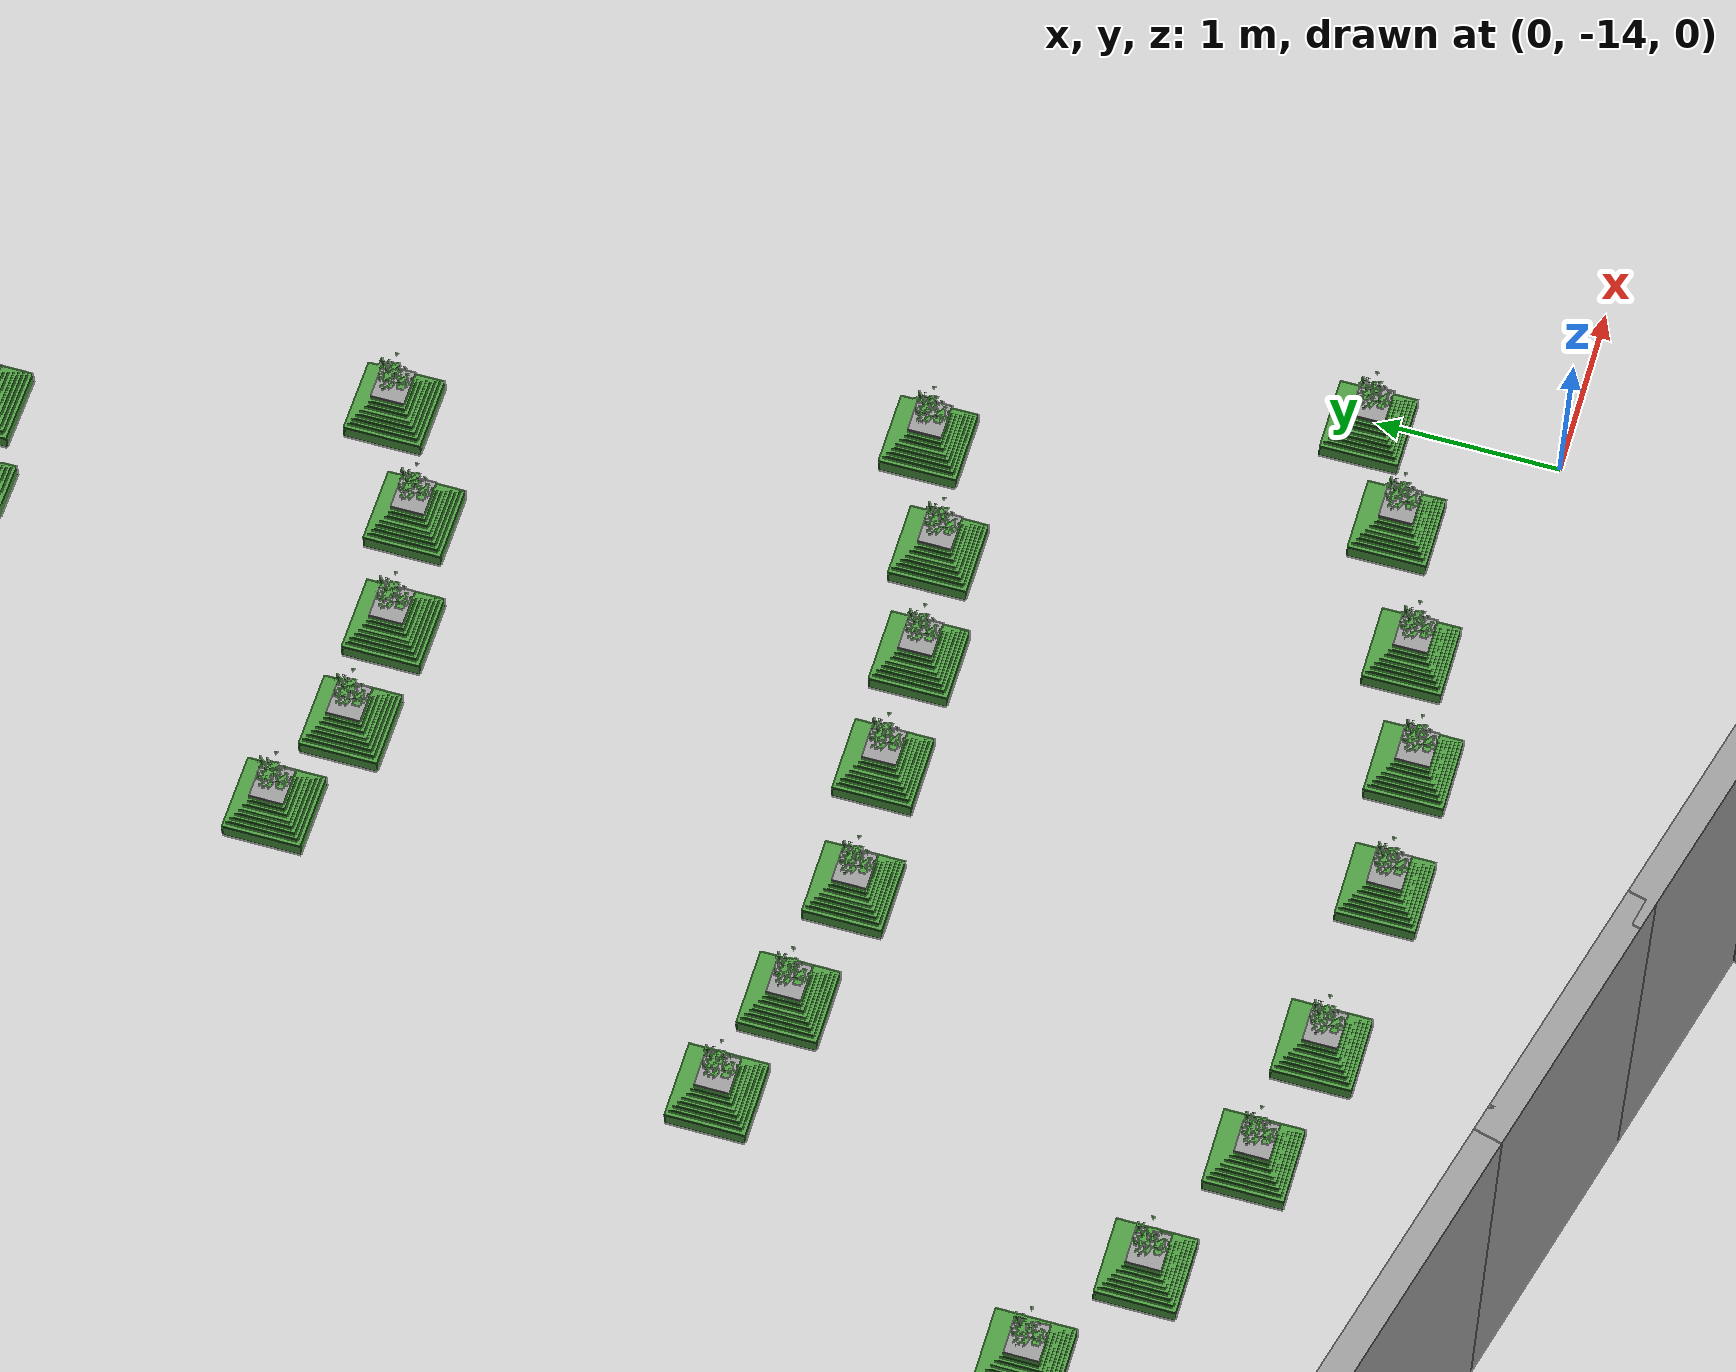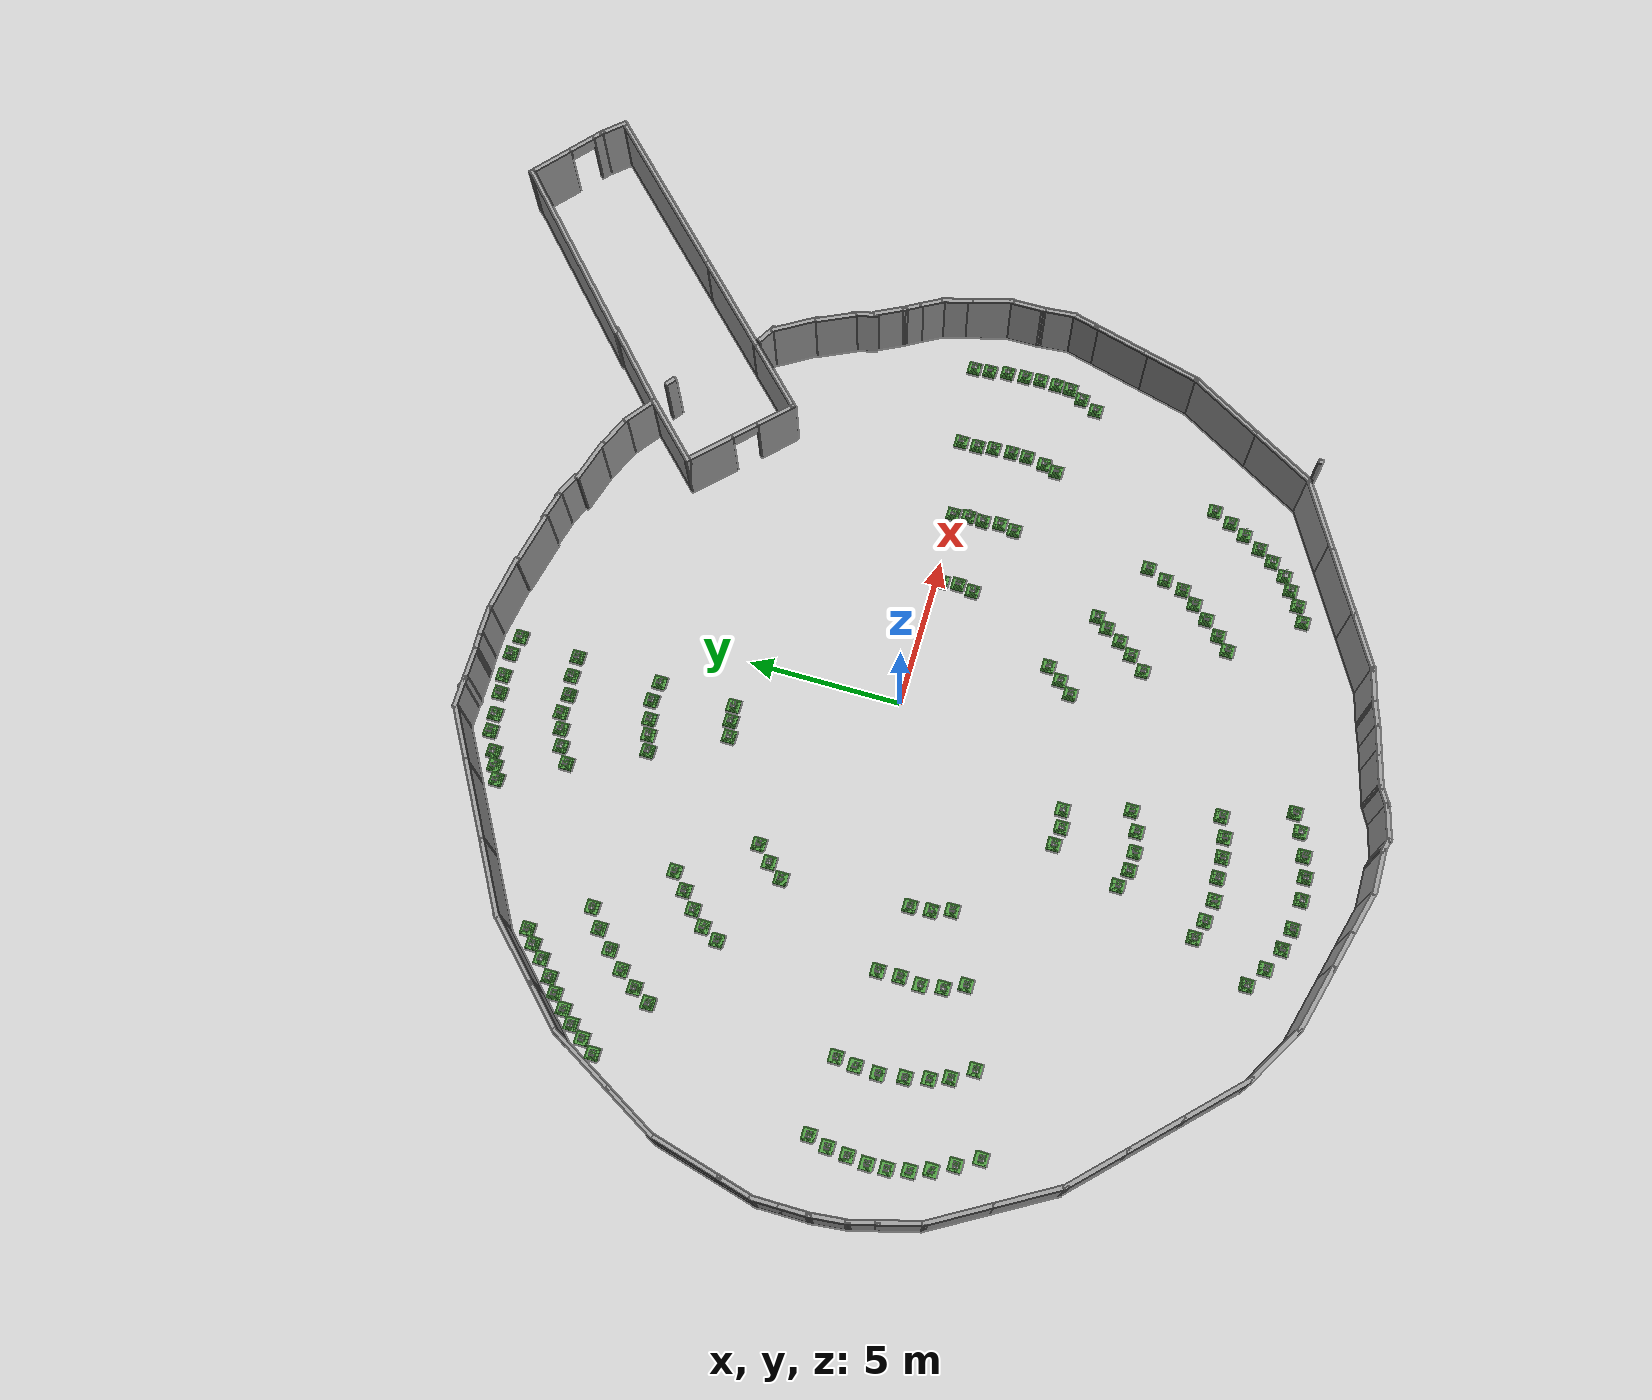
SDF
<sdf version="1.6">
 <world name="default">
  <model name="ground_plane">
   <static>1</static>
   <link name="link">
    <collision name="collision">
     <geometry><plane><normal>0 0 1</normal><size>100 100</size></plane></geometry>
     <surface><friction><ode><mu>100</mu><mu2>50</mu2></ode></friction></surface>
    </collision>
    <visual name="visual">
     <cast_shadows>0</cast_shadows>
     <geometry><plane><normal>0 0 1</normal><size>100 100</size></plane></geometry>
     <material>
      <script><uri>file://media/materials/scripts/gazebo.material</uri><name>Gazebo/Grey</name></script>
     </material>
    </visual>
   </link>
  </model>
  <gravity>0 0 -1.62</gravity>
  <magnetic_field>6e-06 2.3e-05 -4.2e-05</magnetic_field>
  <atmosphere type="adiabatic"/>
  <physics name="default_physics" default="0" type="ode">
   <max_step_size>0.001</max_step_size>
   <real_time_factor>1</real_time_factor>
   <real_time_update_rate>1000</real_time_update_rate>
  </physics>
  <scene><ambient>0.4 0.4 0.4 1</ambient><background>0.7 0.7 0.7 1</background><shadows>1</shadows></scene>
  <spherical_coordinates>
   <surface_model>EARTH_WGS84</surface_model>
   <latitude_deg>0</latitude_deg>
   <longitude_deg>0</longitude_deg>
   <elevation>0</elevation>
   <heading_deg>0</heading_deg>
  </spherical_coordinates>
  <model name="CircularFence">
   <pose>0.1565 0.6213 -0.024158 0 -0 0</pose>
   <link name="Wall_108">
    <collision name="Wall_108_Collision">
     <geometry><box><size>0.16 0.15 2.5</size></box></geometry>
     <pose>0 0 1.25 0 -0 0</pose>
    </collision>
    <visual name="Wall_108_Visual">
     <pose>0 0 1.25 0 -0 0</pose>
     <geometry><box><size>0.16 0.15 2.5</size></box></geometry>
     <material>
      <script><uri>file://media/materials/scripts/gazebo.material</uri><name>Gazebo/Grey</name></script>
      <ambient>0 0 0 0</ambient>
     </material>
    </visual>
    <pose>10.6487 -11.5681 0 0 -0 0</pose>
   </link>
   <link name="Wall_118">
    <collision name="Wall_118_Collision">
     <geometry><box><size>1.94177 0.15 2.5</size></box></geometry>
     <pose>0 0 1.25 0 -0 0</pose>
    </collision>
    <visual name="Wall_118_Visual">
     <pose>0 0 1.25 0 -0 0</pose>
     <geometry><box><size>1.94177 0.15 2.5</size></box></geometry>
     <material>
      <script><uri>file://media/materials/scripts/gazebo.material</uri><name>Gazebo/Grey</name></script>
      <ambient>1 1 1 1</ambient>
     </material>
    </visual>
    <pose>-0.537149 12.2558 0 0 -0 2.98255</pose>
   </link>
   <link name="Wall_120">
    <collision name="Wall_120_Collision">
     <geometry><box><size>1.83123 0.15 2.5</size></box></geometry>
     <pose>0 0 1.25 0 -0 0</pose>
    </collision>
    <visual name="Wall_120_Visual">
     <pose>0 0 1.25 0 -0 0</pose>
     <geometry><box><size>1.83123 0.15 2.5</size></box></geometry>
     <material>
      <script><uri>file://media/materials/scripts/gazebo.material</uri><name>Gazebo/Grey</name></script>
      <ambient>1 1 1 1</ambient>
     </material>
    </visual>
    <pose>1.13156 11.8951 0 0 -0 2.92292</pose>
   </link>
   <link name="Wall_123">
    <collision name="Wall_123_Collision">
     <geometry><box><size>1.25 0.15 2.5</size></box></geometry>
     <pose>0 0 1.25 0 -0 0</pose>
    </collision>
    <visual name="Wall_123_Visual">
     <pose>0 0 1.25 0 -0 0</pose>
     <geometry><box><size>1.25 0.15 2.5</size></box></geometry>
     <material>
      <script><uri>file://media/materials/scripts/gazebo.material</uri><name>Gazebo/Grey</name></script>
      <ambient>1 1 1 1</ambient>
     </material>
    </visual>
    <pose>13.4677 -1.09217 0 0 -0 1.5708</pose>
   </link>
   <link name="Wall_126">
    <collision name="Wall_126_Collision">
     <geometry><box><size>1.5 0.15 2.5</size></box></geometry>
     <pose>0 0 1.25 0 -0 0</pose>
    </collision>
    <visual name="Wall_126_Visual">
     <pose>0 0 1.25 0 -0 0</pose>
     <geometry><box><size>1.5 0.15 2.5</size></box></geometry>
     <material>
      <script><uri>file://media/materials/scripts/gazebo.material</uri><name>Gazebo/Grey</name></script>
      <ambient>1 1 1 1</ambient>
     </material>
    </visual>
    <pose>13.293 0.109828 0 0 -0 1.8326</pose>
   </link>
   <link name="Wall_127">
    <collision name="Wall_127_Collision">
     <geometry><box><size>1 0.15 2.5</size></box></geometry>
     <pose>0 0 1.25 0 -0 0</pose>
    </collision>
    <visual name="Wall_127_Visual">
     <pose>0 0 1.25 0 -0 0</pose>
     <geometry><box><size>1 0.15 2.5</size></box></geometry>
     <material>
      <script><uri>file://media/materials/scripts/gazebo.material</uri><name>Gazebo/Grey</name></script>
      <ambient>1 1 1 1</ambient>
     </material>
    </visual>
    <pose>13.0083 1.17235 0 0 -0 1.8326</pose>
   </link>
   <link name="Wall_128">
    <collision name="Wall_128_Collision">
     <geometry><box><size>0.888528 0.15 2.5</size></box></geometry>
     <pose>0 0 1.25 0 -0 0</pose>
    </collision>
    <visual name="Wall_128_Visual">
     <pose>0 0 1.25 0 -0 0</pose>
     <geometry><box><size>0.888528 0.15 2.5</size></box></geometry>
     <material>
      <script><uri>file://media/materials/scripts/gazebo.material</uri><name>Gazebo/Grey</name></script>
      <ambient>1 1 1 1</ambient>
     </material>
    </visual>
    <pose>12.7215 1.90706 0 0 -0 2.07005</pose>
   </link>
   <link name="Wall_129">
    <collision name="Wall_129_Collision">
     <geometry><box><size>0.75 0.15 2.5</size></box></geometry>
     <pose>0 0 1.25 0 -0 0</pose>
    </collision>
    <visual name="Wall_129_Visual">
     <pose>0 0 1.25 0 -0 0</pose>
     <geometry><box><size>0.75 0.15 2.5</size></box></geometry>
     <material>
      <script><uri>file://media/materials/scripts/gazebo.material</uri><name>Gazebo/Grey</name></script>
      <ambient>1 1 1 1</ambient>
     </material>
    </visual>
    <pose>12.3947 2.49105 0 0 -0 2.0944</pose>
   </link>
   <link name="Wall_130">
    <collision name="Wall_130_Collision">
     <geometry><box><size>1.12578 0.15 2.5</size></box></geometry>
     <pose>0 0 1.25 0 -0 0</pose>
    </collision>
    <visual name="Wall_130_Visual">
     <pose>0 0 1.25 0 -0 0</pose>
     <geometry><box><size>1.12578 0.15 2.5</size></box></geometry>
     <material>
      <script><uri>file://media/materials/scripts/gazebo.material</uri><name>Gazebo/Grey</name></script>
      <ambient>1 1 1 1</ambient>
     </material>
    </visual>
    <pose>12.026 3.18702 0 0 -0 2.03549</pose>
   </link>
   <link name="Wall_131">
    <collision name="Wall_131_Collision">
     <geometry><box><size>0.879 0.15 2.5</size></box></geometry>
     <pose>0 0 1.25 0 -0 0</pose>
    </collision>
    <visual name="Wall_131_Visual">
     <pose>0 0 1.25 0 -0 0</pose>
     <geometry><box><size>0.879 0.15 2.5</size></box></geometry>
     <material>
      <script><uri>file://media/materials/scripts/gazebo.material</uri><name>Gazebo/Grey</name></script>
      <ambient>1 1 1 1</ambient>
     </material>
    </visual>
    <pose>11.6892 3.94192 0 0 -0 1.79684</pose>
   </link>
   <link name="Wall_132">
    <collision name="Wall_132_Collision">
     <geometry><box><size>1.36585 0.15 2.5</size></box></geometry>
     <pose>0 0 1.25 0 -0 0</pose>
    </collision>
    <visual name="Wall_132_Visual">
     <pose>0 0 1.25 0 -0 0</pose>
     <geometry><box><size>1.36585 0.15 2.5</size></box></geometry>
     <material>
      <script><uri>file://media/materials/scripts/gazebo.material</uri><name>Gazebo/Grey</name></script>
      <ambient>1 1 1 1</ambient>
     </material>
    </visual>
    <pose>11.3126 4.84739 0 0 -0 2.00995</pose>
   </link>
   <link name="Wall_133">
    <collision name="Wall_133_Collision">
     <geometry><box><size>1.64734 0.15 2.5</size></box></geometry>
     <pose>0 0 1.25 0 -0 0</pose>
    </collision>
    <visual name="Wall_133_Visual">
     <pose>0 0 1.25 0 -0 0</pose>
     <geometry><box><size>1.64734 0.15 2.5</size></box></geometry>
     <material>
      <script><uri>file://media/materials/scripts/gazebo.material</uri><name>Gazebo/Grey</name></script>
      <ambient>1 1 1 1</ambient>
     </material>
    </visual>
    <pose>10.7045 6.03905 0 0 -0 2.11267</pose>
   </link>
   <link name="Wall_134">
    <collision name="Wall_134_Collision">
     <geometry><box><size>0.75 0.15 2.5</size></box></geometry>
     <pose>0 0 1.25 0 -0 0</pose>
    </collision>
    <visual name="Wall_134_Visual">
     <pose>0 0 1.25 0 -0 0</pose>
     <geometry><box><size>0.75 0.15 2.5</size></box></geometry>
     <material>
      <script><uri>file://media/materials/scripts/gazebo.material</uri><name>Gazebo/Grey</name></script>
      <ambient>1 1 1 1</ambient>
     </material>
    </visual>
    <pose>10.095 6.83046 0 0 -0 2.61799</pose>
   </link>
   <link name="Wall_138">
    <collision name="Wall_138_Collision">
     <geometry><box><size>1.24911 0.15 2.5</size></box></geometry>
     <pose>0 0 1.25 0 -0 0</pose>
    </collision>
    <visual name="Wall_138_Visual">
     <pose>0 0 1.25 0 -0 0</pose>
     <geometry><box><size>1.24911 0.15 2.5</size></box></geometry>
     <material>
      <script><uri>file://media/materials/scripts/gazebo.material</uri><name>Gazebo/Grey</name></script>
      <ambient>1 1 1 1</ambient>
     </material>
    </visual>
    <pose>6.34771 9.97388 0 0 -0 2.4965</pose>
   </link>
   <link name="Wall_139">
    <collision name="Wall_139_Collision">
     <geometry><box><size>1.31498 0.15 2.5</size></box></geometry>
     <pose>0 0 1.25 0 -0 0</pose>
    </collision>
    <visual name="Wall_139_Visual">
     <pose>0 0 1.25 0 -0 0</pose>
     <geometry><box><size>1.31498 0.15 2.5</size></box></geometry>
     <material>
      <script><uri>file://media/materials/scripts/gazebo.material</uri><name>Gazebo/Grey</name></script>
      <ambient>1 1 1 1</ambient>
     </material>
    </visual>
    <pose>5.37423 10.5362 0 0 -0 2.7322</pose>
   </link>
   <link name="Wall_140">
    <collision name="Wall_140_Collision">
     <geometry><box><size>1.49782 0.15 2.5</size></box></geometry>
     <pose>0 0 1.25 0 -0 0</pose>
    </collision>
    <visual name="Wall_140_Visual">
     <pose>0 0 1.25 0 -0 0</pose>
     <geometry><box><size>1.49782 0.15 2.5</size></box></geometry>
     <material>
      <script><uri>file://media/materials/scripts/gazebo.material</uri><name>Gazebo/Grey</name></script>
      <ambient>1 1 1 1</ambient>
     </material>
    </visual>
    <pose>4.22956 10.9573 0 0 -0 2.85692</pose>
   </link>
   <link name="Wall_141">
    <collision name="Wall_141_Collision">
     <geometry><box><size>1.00545 0.15 2.5</size></box></geometry>
     <pose>0 0 1.25 0 -0 0</pose>
    </collision>
    <visual name="Wall_141_Visual">
     <pose>0 0 1.25 0 -0 0</pose>
     <geometry><box><size>1.00545 0.15 2.5</size></box></geometry>
     <material>
      <script><uri>file://media/materials/scripts/gazebo.material</uri><name>Gazebo/Grey</name></script>
      <ambient>1 1 1 1</ambient>
     </material>
    </visual>
    <pose>3.19415 11.3982 0 0 -0 2.71064</pose>
   </link>
   <link name="Wall_142">
    <collision name="Wall_142_Collision">
     <geometry><box><size>0.993176 0.15 2.5</size></box></geometry>
     <pose>0 0 1.25 0 -0 0</pose>
    </collision>
    <visual name="Wall_142_Visual">
     <pose>0 0 1.25 0 -0 0</pose>
     <geometry><box><size>0.993176 0.15 2.5</size></box></geometry>
     <material>
      <script><uri>file://media/materials/scripts/gazebo.material</uri><name>Gazebo/Grey</name></script>
      <ambient>1 1 1 1</ambient>
     </material>
    </visual>
    <pose>2.39708 11.6448 0 0 -0 2.89134</pose>
   </link>
   <link name="Wall_144">
    <collision name="Wall_144_Collision">
     <geometry><box><size>0.5 0.15 2.5</size></box></geometry>
     <pose>0 0 1.25 0 -0 0</pose>
    </collision>
    <visual name="Wall_144_Visual">
     <pose>0 0 1.25 0 -0 0</pose>
     <geometry><box><size>0.5 0.15 2.5</size></box></geometry>
     <material>
      <script><uri>file://media/materials/scripts/gazebo.material</uri><name>Gazebo/Grey</name></script>
      <ambient>1 1 1 1</ambient>
     </material>
    </visual>
    <pose>-1.16759 -16.1719 0 0 0 -0.261799</pose>
   </link>
   <link name="Wall_145">
    <collision name="Wall_145_Collision">
     <geometry><box><size>1.25 0.15 2.5</size></box></geometry>
     <pose>0 0 1.25 0 -0 0</pose>
    </collision>
    <visual name="Wall_145_Visual">
     <pose>0 0 1.25 0 -0 0</pose>
     <geometry><box><size>1.25 0.15 2.5</size></box></geometry>
     <material>
      <script><uri>file://media/materials/scripts/gazebo.material</uri><name>Gazebo/Grey</name></script>
      <ambient>1 1 1 1</ambient>
     </material>
    </visual>
    <pose>-0.467294 -16.0748 0 0 -0 0.261799</pose>
   </link>
   <link name="Wall_146">
    <collision name="Wall_146_Collision">
     <geometry><box><size>0.75 0.15 2.5</size></box></geometry>
     <pose>0 0 1.25 0 -0 0</pose>
    </collision>
    <visual name="Wall_146_Visual">
     <pose>0 0 1.25 0 -0 0</pose>
     <geometry><box><size>0.75 0.15 2.5</size></box></geometry>
     <material>
      <script><uri>file://media/materials/scripts/gazebo.material</uri><name>Gazebo/Grey</name></script>
      <ambient>1 1 1 1</ambient>
     </material>
    </visual>
    <pose>0.323772 -15.7825 0 0 -0 0.523599</pose>
   </link>
   <link name="Wall_147">
    <collision name="Wall_147_Collision">
     <geometry><box><size>1.25 0.15 2.5</size></box></geometry>
     <pose>0 0 1.25 0 -0 0</pose>
    </collision>
    <visual name="Wall_147_Visual">
     <pose>0 0 1.25 0 -0 0</pose>
     <geometry><box><size>1.25 0.15 2.5</size></box></geometry>
     <material>
      <script><uri>file://media/materials/scripts/gazebo.material</uri><name>Gazebo/Grey</name></script>
      <ambient>1 1 1 1</ambient>
     </material>
    </visual>
    <pose>1.11484 -15.4901 0 0 -0 0.261799</pose>
   </link>
   <link name="Wall_148">
    <collision name="Wall_148_Collision">
     <geometry><box><size>1 0.15 2.5</size></box></geometry>
     <pose>0 0 1.25 0 -0 0</pose>
    </collision>
    <visual name="Wall_148_Visual">
     <pose>0 0 1.25 0 -0 0</pose>
     <geometry><box><size>1 0.15 2.5</size></box></geometry>
     <material>
      <script><uri>file://media/materials/scripts/gazebo.material</uri><name>Gazebo/Grey</name></script>
      <ambient>1 1 1 1</ambient>
     </material>
    </visual>
    <pose>2.05662 -15.2378 0 0 -0 0.261799</pose>
   </link>
   <link name="Wall_166">
    <collision name="Wall_166_Collision">
     <geometry><box><size>1.16803 0.15 2.5</size></box></geometry>
     <pose>0 0 1.25 0 -0 0</pose>
    </collision>
    <visual name="Wall_166_Visual">
     <pose>0 0 1.25 0 -0 0</pose>
     <geometry><box><size>1.16803 0.15 2.5</size></box></geometry>
     <material>
      <script><uri>file://media/materials/scripts/gazebo.material</uri><name>Gazebo/Grey</name></script>
      <ambient>1 1 1 1</ambient>
     </material>
    </visual>
    <pose>13.5088 -2.14952 0 0 -0 1.6517</pose>
   </link>
   <link name="Wall_168">
    <collision name="Wall_168_Collision">
     <geometry><box><size>0.970327 0.15 2.5</size></box></geometry>
     <pose>0 0 1.25 0 -0 0</pose>
    </collision>
    <visual name="Wall_168_Visual">
     <pose>0 0 1.25 0 -0 0</pose>
     <geometry><box><size>0.970327 0.15 2.5</size></box></geometry>
     <material>
      <script><uri>file://media/materials/scripts/gazebo.material</uri><name>Gazebo/Grey</name></script>
      <ambient>1 1 1 1</ambient>
     </material>
    </visual>
    <pose>-1.83187 12.4017 0 0 0 -0.009748</pose>
   </link>
   <link name="Wall_170">
    <collision name="Wall_170_Collision">
     <geometry><box><size>1 0.15 2.5</size></box></geometry>
     <pose>0 0 1.25 0 -0 0</pose>
    </collision>
    <visual name="Wall_170_Visual">
     <pose>0 0 1.25 0 -0 0</pose>
     <geometry><box><size>1 0.15 2.5</size></box></geometry>
     <material>
      <script><uri>file://media/materials/scripts/gazebo.material</uri><name>Gazebo/Grey</name></script>
      <ambient>1 1 1 1</ambient>
     </material>
    </visual>
    <pose>-16.3823 -1.21717 0 0 -0 1.5708</pose>
   </link>
   <link name="Wall_172">
    <collision name="Wall_172_Collision">
     <geometry><box><size>1 0.15 2.5</size></box></geometry>
     <pose>0 0 1.25 0 -0 0</pose>
    </collision>
    <visual name="Wall_172_Visual">
     <pose>0 0 1.25 0 -0 0</pose>
     <geometry><box><size>1 0.15 2.5</size></box></geometry>
     <material>
      <script><uri>file://media/materials/scripts/gazebo.material</uri><name>Gazebo/Grey</name></script>
      <ambient>1 1 1 1</ambient>
     </material>
    </visual>
    <pose>-16.3823 -2.06717 0 0 0 -1.5708</pose>
   </link>
   <link name="Wall_174">
    <collision name="Wall_174_Collision">
     <geometry><box><size>1.5 0.15 2.5</size></box></geometry>
     <pose>0 0 1.25 0 -0 0</pose>
    </collision>
    <visual name="Wall_174_Visual">
     <pose>0 0 1.25 0 -0 0</pose>
     <geometry><box><size>1.5 0.15 2.5</size></box></geometry>
     <material>
      <script><uri>file://media/materials/scripts/gazebo.material</uri><name>Gazebo/Grey</name></script>
      <ambient>1 1 1 1</ambient>
     </material>
    </visual>
    <pose>-2.01163 -16.1266 0 0 -0 3.14159</pose>
   </link>
   <link name="Wall_175">
    <collision name="Wall_175_Collision">
     <geometry><box><size>1.5 0.15 2.5</size></box></geometry>
     <pose>0 0 1.25 0 -0 0</pose>
    </collision>
    <visual name="Wall_175_Visual">
     <pose>0 0 1.25 0 -0 0</pose>
     <geometry><box><size>1.5 0.15 2.5</size></box></geometry>
     <material>
      <script><uri>file://media/materials/scripts/gazebo.material</uri><name>Gazebo/Grey</name></script>
      <ambient>1 1 1 1</ambient>
     </material>
    </visual>
    <pose>-3.33863 -15.9519 0 0 -0 2.87979</pose>
   </link>
   <link name="Wall_176">
    <collision name="Wall_176_Collision">
     <geometry><box><size>1.5 0.15 2.5</size></box></geometry>
     <pose>0 0 1.25 0 -0 0</pose>
    </collision>
    <visual name="Wall_176_Visual">
     <pose>0 0 1.25 0 -0 0</pose>
     <geometry><box><size>1.5 0.15 2.5</size></box></geometry>
     <material>
      <script><uri>file://media/materials/scripts/gazebo.material</uri><name>Gazebo/Grey</name></script>
      <ambient>1 1 1 1</ambient>
     </material>
    </visual>
    <pose>-4.64263 -15.6025 0 0 -0 2.87979</pose>
   </link>
   <link name="Wall_177">
    <collision name="Wall_177_Collision">
     <geometry><box><size>2.25 0.15 2.5</size></box></geometry>
     <pose>0 0 1.25 0 -0 0</pose>
    </collision>
    <visual name="Wall_177_Visual">
     <pose>0 0 1.25 0 -0 0</pose>
     <geometry><box><size>2.25 0.15 2.5</size></box></geometry>
     <material>
      <script><uri>file://media/materials/scripts/gazebo.material</uri><name>Gazebo/Grey</name></script>
      <ambient>1 1 1 1</ambient>
     </material>
    </visual>
    <pose>-6.30885 -15.156 0 0 -0 2.87979</pose>
   </link>
   <link name="Wall_178">
    <collision name="Wall_178_Collision">
     <geometry><box><size>2.25 0.15 2.5</size></box></geometry>
     <pose>0 0 1.25 0 -0 0</pose>
    </collision>
    <visual name="Wall_178_Visual">
     <pose>0 0 1.25 0 -0 0</pose>
     <geometry><box><size>2.25 0.15 2.5</size></box></geometry>
     <material>
      <script><uri>file://media/materials/scripts/gazebo.material</uri><name>Gazebo/Grey</name></script>
      <ambient>1 1 1 1</ambient>
     </material>
    </visual>
    <pose>-8.2324 -14.3592 0 0 -0 2.61799</pose>
   </link>
   <link name="Wall_179">
    <collision name="Wall_179_Collision">
     <geometry><box><size>2.5 0.15 2.5</size></box></geometry>
     <pose>0 0 1.25 0 -0 0</pose>
    </collision>
    <visual name="Wall_179_Visual">
     <pose>0 0 1.25 0 -0 0</pose>
     <geometry><box><size>2.5 0.15 2.5</size></box></geometry>
     <material>
      <script><uri>file://media/materials/scripts/gazebo.material</uri><name>Gazebo/Grey</name></script>
      <ambient>1 1 1 1</ambient>
     </material>
    </visual>
    <pose>-9.97258 -13.0034 0 0 -0 2.35619</pose>
   </link>
   <link name="Wall_180">
    <collision name="Wall_180_Collision">
     <geometry><box><size>2 0.15 2.5</size></box></geometry>
     <pose>0 0 1.25 0 -0 0</pose>
    </collision>
    <visual name="Wall_180_Visual">
     <pose>0 0 1.25 0 -0 0</pose>
     <geometry><box><size>2 0.15 2.5</size></box></geometry>
     <material>
      <script><uri>file://media/materials/scripts/gazebo.material</uri><name>Gazebo/Grey</name></script>
      <ambient>1 1 1 1</ambient>
     </material>
    </visual>
    <pose>-11.4575 -11.5185 0 0 -0 2.35619</pose>
   </link>
   <link name="Wall_181">
    <collision name="Wall_181_Collision">
     <geometry><box><size>2.25 0.15 2.5</size></box></geometry>
     <pose>0 0 1.25 0 -0 0</pose>
    </collision>
    <visual name="Wall_181_Visual">
     <pose>0 0 1.25 0 -0 0</pose>
     <geometry><box><size>2.25 0.15 2.5</size></box></geometry>
     <material>
      <script><uri>file://media/materials/scripts/gazebo.material</uri><name>Gazebo/Grey</name></script>
      <ambient>1 1 1 1</ambient>
     </material>
    </visual>
    <pose>-12.854 -10.1219 0 0 -0 2.35619</pose>
   </link>
   <link name="Wall_182">
    <collision name="Wall_182_Collision">
     <geometry><box><size>2.25 0.15 2.5</size></box></geometry>
     <pose>0 0 1.25 0 -0 0</pose>
    </collision>
    <visual name="Wall_182_Visual">
     <pose>0 0 1.25 0 -0 0</pose>
     <geometry><box><size>2.25 0.15 2.5</size></box></geometry>
     <material>
      <script><uri>file://media/materials/scripts/gazebo.material</uri><name>Gazebo/Grey</name></script>
      <ambient>1 1 1 1</ambient>
     </material>
    </visual>
    <pose>-14.1215 -8.47014 0 0 -0 2.0944</pose>
   </link>
   <link name="Wall_183">
    <collision name="Wall_183_Collision">
     <geometry><box><size>2.25 0.15 2.5</size></box></geometry>
     <pose>0 0 1.25 0 -0 0</pose>
    </collision>
    <visual name="Wall_183_Visual">
     <pose>0 0 1.25 0 -0 0</pose>
     <geometry><box><size>2.25 0.15 2.5</size></box></geometry>
     <material>
      <script><uri>file://media/materials/scripts/gazebo.material</uri><name>Gazebo/Grey</name></script>
      <ambient>1 1 1 1</ambient>
     </material>
    </visual>
    <pose>-15.1715 -6.65149 0 0 -0 2.0944</pose>
   </link>
   <link name="Wall_184">
    <collision name="Wall_184_Collision">
     <geometry><box><size>1.5 0.15 2.5</size></box></geometry>
     <pose>0 0 1.25 0 -0 0</pose>
    </collision>
    <visual name="Wall_184_Visual">
     <pose>0 0 1.25 0 -0 0</pose>
     <geometry><box><size>1.5 0.15 2.5</size></box></geometry>
     <material>
      <script><uri>file://media/materials/scripts/gazebo.material</uri><name>Gazebo/Grey</name></script>
      <ambient>1 1 1 1</ambient>
     </material>
    </visual>
    <pose>-15.8712 -5.09016 0 0 -0 1.8326</pose>
   </link>
   <link name="Wall_185">
    <collision name="Wall_185_Collision">
     <geometry><box><size>1 0.15 2.5</size></box></geometry>
     <pose>0 0 1.25 0 -0 0</pose>
    </collision>
    <visual name="Wall_185_Visual">
     <pose>0 0 1.25 0 -0 0</pose>
     <geometry><box><size>1 0.15 2.5</size></box></geometry>
     <material>
      <script><uri>file://media/materials/scripts/gazebo.material</uri><name>Gazebo/Grey</name></script>
      <ambient>1 1 1 1</ambient>
     </material>
    </visual>
    <pose>-16.1559 -4.02765 0 0 -0 1.8326</pose>
   </link>
   <link name="Wall_186">
    <collision name="Wall_186_Collision">
     <geometry><box><size>1.28097 0.15 2.5</size></box></geometry>
     <pose>0 0 1.25 0 -0 0</pose>
    </collision>
    <visual name="Wall_186_Visual">
     <pose>0 0 1.25 0 -0 0</pose>
     <geometry><box><size>1.28097 0.15 2.5</size></box></geometry>
     <material>
      <script><uri>file://media/materials/scripts/gazebo.material</uri><name>Gazebo/Grey</name></script>
      <ambient>1 1 1 1</ambient>
     </material>
    </visual>
    <pose>-16.3241 -3.05465 0 0 -0 1.67393</pose>
   </link>
   <link name="Wall_190">
    <collision name="Wall_190_Collision">
     <geometry><box><size>0.415491 0.15 2.5</size></box></geometry>
     <pose>0 0 1.25 0 -0 0</pose>
    </collision>
    <visual name="Wall_190_Visual">
     <pose>0 0 1.25 0 -0 0</pose>
     <geometry><box><size>0.415491 0.15 2.5</size></box></geometry>
     <material>
      <script><uri>file://media/materials/scripts/gazebo.material</uri><name>Gazebo/Grey</name></script>
      <ambient>0 0 0 0</ambient>
     </material>
    </visual>
    <pose>-3.96438 12.3692 0 0 0 -0.278323</pose>
   </link>
   <link name="Wall_200">
    <collision name="Wall_200_Collision">
     <geometry><box><size>1.25 0.15 2.5</size></box></geometry>
     <pose>0 0 1.25 0 -0 0</pose>
    </collision>
    <visual name="Wall_200_Visual">
     <pose>0 0 1.25 0 -0 0</pose>
     <geometry><box><size>1.25 0.15 2.5</size></box></geometry>
     <material>
      <script><uri>file://media/materials/scripts/gazebo.material</uri><name>Gazebo/Grey</name></script>
      <ambient>1 1 1 1</ambient>
     </material>
    </visual>
    <pose>-16.24 -0.260912 0 0 -0 1.309</pose>
   </link>
   <link name="Wall_201">
    <collision name="Wall_201_Collision">
     <geometry><box><size>2.5 0.15 2.5</size></box></geometry>
     <pose>0 0 1.25 0 -0 0</pose>
    </collision>
    <visual name="Wall_201_Visual">
     <pose>0 0 1.25 0 -0 0</pose>
     <geometry><box><size>2.5 0.15 2.5</size></box></geometry>
     <material>
      <script><uri>file://media/materials/scripts/gazebo.material</uri><name>Gazebo/Grey</name></script>
      <ambient>1 1 1 1</ambient>
     </material>
    </visual>
    <pose>-15.7935 1.40531 0 0 -0 1.309</pose>
   </link>
   <link name="Wall_202">
    <collision name="Wall_202_Collision">
     <geometry><box><size>2 0.15 2.5</size></box></geometry>
     <pose>0 0 1.25 0 -0 0</pose>
    </collision>
    <visual name="Wall_202_Visual">
     <pose>0 0 1.25 0 -0 0</pose>
     <geometry><box><size>2 0.15 2.5</size></box></geometry>
     <material>
      <script><uri>file://media/materials/scripts/gazebo.material</uri><name>Gazebo/Grey</name></script>
      <ambient>1 1 1 1</ambient>
     </material>
    </visual>
    <pose>-15.0269 3.34135 0 0 -0 1.0472</pose>
   </link>
   <link name="Wall_203">
    <collision name="Wall_203_Collision">
     <geometry><box><size>2.5 0.15 2.5</size></box></geometry>
     <pose>0 0 1.25 0 -0 0</pose>
    </collision>
    <visual name="Wall_203_Visual">
     <pose>0 0 1.25 0 -0 0</pose>
     <geometry><box><size>2.5 0.15 2.5</size></box></geometry>
     <material>
      <script><uri>file://media/materials/scripts/gazebo.material</uri><name>Gazebo/Grey</name></script>
      <ambient>1 1 1 1</ambient>
     </material>
    </visual>
    <pose>-13.9769 5.16 0 0 -0 1.0472</pose>
   </link>
   <link name="Wall_204">
    <collision name="Wall_204_Collision">
     <geometry><box><size>1.75 0.15 2.5</size></box></geometry>
     <pose>0 0 1.25 0 -0 0</pose>
    </collision>
    <visual name="Wall_204_Visual">
     <pose>0 0 1.25 0 -0 0</pose>
     <geometry><box><size>1.75 0.15 2.5</size></box></geometry>
     <material>
      <script><uri>file://media/materials/scripts/gazebo.material</uri><name>Gazebo/Grey</name></script>
      <ambient>1 1 1 1</ambient>
     </material>
    </visual>
    <pose>-12.8237 6.74327 0 0 -0 0.785398</pose>
   </link>
   <link name="Wall_205">
    <collision name="Wall_205_Collision">
     <geometry><box><size>2.5 0.15 2.5</size></box></geometry>
     <pose>0 0 1.25 0 -0 0</pose>
    </collision>
    <visual name="Wall_205_Visual">
     <pose>0 0 1.25 0 -0 0</pose>
     <geometry><box><size>2.5 0.15 2.5</size></box></geometry>
     <material>
      <script><uri>file://media/materials/scripts/gazebo.material</uri><name>Gazebo/Grey</name></script>
      <ambient>1 1 1 1</ambient>
     </material>
    </visual>
    <pose>-11.4272 8.1398 0 0 -0 0.785398</pose>
   </link>
   <link name="Wall_206">
    <collision name="Wall_206_Collision">
     <geometry><box><size>2.5 0.15 2.5</size></box></geometry>
     <pose>0 0 1.25 0 -0 0</pose>
    </collision>
    <visual name="Wall_206_Visual">
     <pose>0 0 1.25 0 -0 0</pose>
     <geometry><box><size>2.5 0.15 2.5</size></box></geometry>
     <material>
      <script><uri>file://media/materials/scripts/gazebo.material</uri><name>Gazebo/Grey</name></script>
      <ambient>1 1 1 1</ambient>
     </material>
    </visual>
    <pose>-9.57876 9.55815 0 0 -0 0.523599</pose>
   </link>
   <link name="Wall_207">
    <collision name="Wall_207_Collision">
     <geometry><box><size>2.75 0.15 2.5</size></box></geometry>
     <pose>0 0 1.25 0 -0 0</pose>
    </collision>
    <visual name="Wall_207_Visual">
     <pose>0 0 1.25 0 -0 0</pose>
     <geometry><box><size>2.75 0.15 2.5</size></box></geometry>
     <material>
      <script><uri>file://media/materials/scripts/gazebo.material</uri><name>Gazebo/Grey</name></script>
      <ambient>1 1 1 1</ambient>
     </material>
    </visual>
    <pose>-7.43534 10.7957 0 0 -0 0.523599</pose>
   </link>
   <link name="Wall_208">
    <collision name="Wall_208_Collision">
     <geometry><box><size>2 0.15 2.5</size></box></geometry>
     <pose>0 0 1.25 0 -0 0</pose>
    </collision>
    <visual name="Wall_208_Visual">
     <pose>0 0 1.25 0 -0 0</pose>
     <geometry><box><size>2 0.15 2.5</size></box></geometry>
     <material>
      <script><uri>file://media/materials/scripts/gazebo.material</uri><name>Gazebo/Grey</name></script>
      <ambient>1 1 1 1</ambient>
     </material>
    </visual>
    <pose>-5.50844 11.9081 0 0 -0 0.523599</pose>
   </link>
   <link name="Wall_209">
    <collision name="Wall_209_Collision">
     <geometry><box><size>2 0.15 2.5</size></box></geometry>
     <pose>0 0 1.25 0 -0 0</pose>
    </collision>
    <visual name="Wall_209_Visual">
     <pose>0 0 1.25 0 -0 0</pose>
     <geometry><box><size>2 0.15 2.5</size></box></geometry>
     <material>
      <script><uri>file://media/materials/scripts/gazebo.material</uri><name>Gazebo/Grey</name></script>
      <ambient>1 1 1 1</ambient>
     </material>
    </visual>
    <pose>-3.78236 12.3707 0 0 -0 0</pose>
   </link>
   <link name="Wall_210">
    <collision name="Wall_210_Collision">
     <geometry><box><size>0.766345 0.15 2.5</size></box></geometry>
     <pose>0 0 1.25 0 -0 0</pose>
    </collision>
    <visual name="Wall_210_Visual">
     <pose>0 0 1.25 0 -0 0</pose>
     <geometry><box><size>0.766345 0.15 2.5</size></box></geometry>
     <material>
      <script><uri>file://media/materials/scripts/gazebo.material</uri><name>Gazebo/Grey</name></script>
      <ambient>1 1 1 1</ambient>
     </material>
    </visual>
    <pose>-2.54969 12.3882 0 0 -0 0.056841</pose>
   </link>
   <link name="Wall_212">
    <collision name="Wall_212_Collision">
     <geometry><box><size>1 0.15 2.5</size></box></geometry>
     <pose>0 0 1.25 0 -0 0</pose>
    </collision>
    <visual name="Wall_212_Visual">
     <pose>0 0 1.25 0 -0 0</pose>
     <geometry><box><size>1 0.15 2.5</size></box></geometry>
     <material>
      <script><uri>file://media/materials/scripts/gazebo.material</uri><name>Gazebo/Grey</name></script>
      <ambient>1 1 1 1</ambient>
     </material>
    </visual>
    <pose>13.4399 -3.06739 0 0 0 -1.8326</pose>
   </link>
   <link name="Wall_213">
    <collision name="Wall_213_Collision">
     <geometry><box><size>2 0.15 2.5</size></box></geometry>
     <pose>0 0 1.25 0 -0 0</pose>
    </collision>
    <visual name="Wall_213_Visual">
     <pose>0 0 1.25 0 -0 0</pose>
     <geometry><box><size>2 0.15 2.5</size></box></geometry>
     <material>
      <script><uri>file://media/materials/scripts/gazebo.material</uri><name>Gazebo/Grey</name></script>
      <ambient>1 1 1 1</ambient>
     </material>
    </visual>
    <pose>13.0905 -4.37139 0 0 0 -1.8326</pose>
   </link>
   <link name="Wall_214">
    <collision name="Wall_214_Collision">
     <geometry><box><size>2 0.15 2.5</size></box></geometry>
     <pose>0 0 1.25 0 -0 0</pose>
    </collision>
    <visual name="Wall_214_Visual">
     <pose>0 0 1.25 0 -0 0</pose>
     <geometry><box><size>2 0.15 2.5</size></box></geometry>
     <material>
      <script><uri>file://media/materials/scripts/gazebo.material</uri><name>Gazebo/Grey</name></script>
      <ambient>1 1 1 1</ambient>
     </material>
    </visual>
    <pose>12.6117 -6.15835 0 0 0 -1.8326</pose>
   </link>
   <link name="Wall_215">
    <collision name="Wall_215_Collision">
     <geometry><box><size>2.75 0.15 2.5</size></box></geometry>
     <pose>0 0 1.25 0 -0 0</pose>
    </collision>
    <visual name="Wall_215_Visual">
     <pose>0 0 1.25 0 -0 0</pose>
     <geometry><box><size>2.75 0.15 2.5</size></box></geometry>
     <material>
      <script><uri>file://media/materials/scripts/gazebo.material</uri><name>Gazebo/Grey</name></script>
      <ambient>1 1 1 1</ambient>
     </material>
    </visual>
    <pose>11.7223 -8.17767 0 0 0 -2.0944</pose>
   </link>
   <link name="Wall_216">
    <collision name="Wall_216_Collision">
     <geometry><box><size>2.5 0.15 2.5</size></box></geometry>
     <pose>0 0 1.25 0 -0 0</pose>
    </collision>
    <visual name="Wall_216_Visual">
     <pose>0 0 1.25 0 -0 0</pose>
     <geometry><box><size>2.5 0.15 2.5</size></box></geometry>
     <material>
      <script><uri>file://media/materials/scripts/gazebo.material</uri><name>Gazebo/Grey</name></script>
      <ambient>1 1 1 1</ambient>
     </material>
    </visual>
    <pose>10.4848 -10.3211 0 0 0 -2.0944</pose>
   </link>
   <link name="Wall_217">
    <collision name="Wall_217_Collision">
     <geometry><box><size>2.5 0.15 2.5</size></box></geometry>
     <pose>0 0 1.25 0 -0 0</pose>
    </collision>
    <visual name="Wall_217_Visual">
     <pose>0 0 1.25 0 -0 0</pose>
     <geometry><box><size>2.5 0.15 2.5</size></box></geometry>
     <material>
      <script><uri>file://media/materials/scripts/gazebo.material</uri><name>Gazebo/Grey</name></script>
      <ambient>1 1 1 1</ambient>
     </material>
    </visual>
    <pose>8.87974 -11.9262 0 0 0 -2.61799</pose>
   </link>
   <link name="Wall_218">
    <collision name="Wall_218_Collision">
     <geometry><box><size>2.5 0.15 2.5</size></box></geometry>
     <pose>0 0 1.25 0 -0 0</pose>
    </collision>
    <visual name="Wall_218_Visual">
     <pose>0 0 1.25 0 -0 0</pose>
     <geometry><box><size>2.5 0.15 2.5</size></box></geometry>
     <material>
      <script><uri>file://media/materials/scripts/gazebo.material</uri><name>Gazebo/Grey</name></script>
      <ambient>1 1 1 1</ambient>
     </material>
    </visual>
    <pose>6.84458 -13.1012 0 0 0 -2.61799</pose>
   </link>
   <link name="Wall_219">
    <collision name="Wall_219_Collision">
     <geometry><box><size>2 0.15 2.5</size></box></geometry>
     <pose>0 0 1.25 0 -0 0</pose>
    </collision>
    <visual name="Wall_219_Visual">
     <pose>0 0 1.25 0 -0 0</pose>
     <geometry><box><size>2 0.15 2.5</size></box></geometry>
     <material>
      <script><uri>file://media/materials/scripts/gazebo.material</uri><name>Gazebo/Grey</name></script>
      <ambient>1 1 1 1</ambient>
     </material>
    </visual>
    <pose>5.02592 -14.1512 0 0 0 -2.61799</pose>
   </link>
   <link name="Wall_220">
    <collision name="Wall_220_Collision">
     <geometry><box><size>1.25 0.15 2.5</size></box></geometry>
     <pose>0 0 1.25 0 -0 0</pose>
    </collision>
    <visual name="Wall_220_Visual">
     <pose>0 0 1.25 0 -0 0</pose>
     <geometry><box><size>1.25 0.15 2.5</size></box></geometry>
     <material>
      <script><uri>file://media/materials/scripts/gazebo.material</uri><name>Gazebo/Grey</name></script>
      <ambient>1 1 1 1</ambient>
     </material>
    </visual>
    <pose>3.69359 -14.756 0 0 0 -2.87979</pose>
   </link>
   <link name="Wall_221">
    <collision name="Wall_221_Collision">
     <geometry><box><size>0.882068 0.15 2.5</size></box></geometry>
     <pose>0 0 1.25 0 -0 0</pose>
    </collision>
    <visual name="Wall_221_Visual">
     <pose>0 0 1.25 0 -0 0</pose>
     <geometry><box><size>0.882068 0.15 2.5</size></box></geometry>
     <material>
      <script><uri>file://media/materials/scripts/gazebo.material</uri><name>Gazebo/Grey</name></script>
      <ambient>1 1 1 1</ambient>
     </material>
    </visual>
    <pose>2.81473 -15.0131 0 0 0 -2.82286</pose>
   </link>
   <link name="Wall_224">
    <collision name="Wall_224_Collision">
     <geometry><box><size>2.5 0.15 2.5</size></box></geometry>
     <pose>0 0 1.25 0 -0 0</pose>
    </collision>
    <visual name="Wall_224_Visual">
     <pose>0 0 1.25 0 -0 0</pose>
     <geometry><box><size>2.5 0.15 2.5</size></box></geometry>
     <material>
      <script><uri>file://media/materials/scripts/gazebo.material</uri><name>Gazebo/Grey</name></script>
      <ambient>1 1 1 1</ambient>
     </material>
    </visual>
    <pose>5.95598 8.8126 0 0 0 -2.35619</pose>
   </link>
   <link name="Wall_225">
    <pose>6.48631 6.62057 0 0 0 -0.785398</pose>
    <visual name="Wall_225_Visual_0">
     <pose>-1.14631 0 1.25 0 -0 0</pose>
     <geometry><box><size>1.70738 0.15 2.5</size></box></geometry>
     <material>
      <script><uri>file://media/materials/scripts/gazebo.material</uri><name>Gazebo/Grey</name></script>
      <ambient>1 1 1 1</ambient>
     </material>
    </visual>
    <collision name="Wall_225_Collision_0">
     <geometry><box><size>1.70738 0.15 2.5</size></box></geometry>
     <pose>-1.14631 0 1.25 0 -0 0</pose>
    </collision>
    <visual name="Wall_225_Visual_1">
     <pose>1.30369 0 1.25 0 -0 0</pose>
     <geometry><box><size>1.39262 0.15 2.5</size></box></geometry>
     <material>
      <script><uri>file://media/materials/scripts/gazebo.material</uri><name>Gazebo/Grey</name></script>
      <ambient>1 1 1 1</ambient>
     </material>
    </visual>
    <collision name="Wall_225_Collision_1">
     <geometry><box><size>1.39262 0.15 2.5</size></box></geometry>
     <pose>1.30369 0 1.25 0 -0 0</pose>
    </collision>
    <visual name="Wall_225_Visual_2">
     <pose>0.157377 0 2.25 0 -0 0</pose>
     <geometry><box><size>0.9 0.15 0.5</size></box></geometry>
     <material>
      <script><uri>file://media/materials/scripts/gazebo.material</uri><name>Gazebo/Grey</name></script>
      <ambient>1 1 1 1</ambient>
     </material>
    </visual>
    <collision name="Wall_225_Collision_2">
     <geometry><box><size>0.9 0.15 0.5</size></box></geometry>
     <pose>0.157377 0 2.25 0 -0 0</pose>
    </collision>
   </link>
   <link name="Wall_226">
    <collision name="Wall_226_Collision">
     <geometry><box><size>2.75 0.15 2.5</size></box></geometry>
     <pose>0 0 1.25 0 -0 0</pose>
    </collision>
    <visual name="Wall_226_Visual">
     <pose>0 0 1.25 0 -0 0</pose>
     <geometry><box><size>2.75 0.15 2.5</size></box></geometry>
     <material>
      <script><uri>file://media/materials/scripts/gazebo.material</uri><name>Gazebo/Grey</name></script>
      <ambient>1 1 1 1</ambient>
     </material>
    </visual>
    <pose>8.76673 6.17863 0 0 -0 0.785398</pose>
   </link>
   <link name="Wall_228">
    <collision name="Wall_228_Collision">
     <geometry><box><size>0.387432 0.15 2.5</size></box></geometry>
     <pose>0 0 1.25 0 -0 0</pose>
    </collision>
    <visual name="Wall_228_Visual">
     <pose>0 0 1.25 0 -0 0</pose>
     <geometry><box><size>0.387432 0.15 2.5</size></box></geometry>
     <material>
      <script><uri>file://media/materials/scripts/gazebo.material</uri><name>Gazebo/Grey</name></script>
      <ambient>0 0 0 0</ambient>
     </material>
    </visual>
    <pose>7.59944 9.34213 0 0 -0 2.48023</pose>
   </link>
   <link name="Wall_230">
    <collision name="Wall_230_Collision">
     <geometry><box><size>3.04553 0.15 2.5</size></box></geometry>
     <pose>0 0 1.25 0 -0 0</pose>
    </collision>
    <visual name="Wall_230_Visual">
     <pose>0 0 1.25 0 -0 0</pose>
     <geometry><box><size>3.04553 0.15 2.5</size></box></geometry>
     <material>
      <script><uri>file://media/materials/scripts/gazebo.material</uri><name>Gazebo/Grey</name></script>
      <ambient>1 1 1 1</ambient>
     </material>
    </visual>
    <pose>7.84637 10.6301 0 0 0 -2.39183</pose>
   </link>
   <link name="Wall_233">
    <collision name="Wall_233_Collision">
     <geometry><box><size>3.5 0.15 2.5</size></box></geometry>
     <pose>0 0 1.25 0 -0 0</pose>
    </collision>
    <visual name="Wall_233_Visual">
     <pose>0 0 1.25 0 -0 0</pose>
     <geometry><box><size>3.5 0.15 2.5</size></box></geometry>
     <material>
      <script><uri>file://media/materials/scripts/gazebo.material</uri><name>Gazebo/Grey</name></script>
      <ambient>1 1 1 1</ambient>
     </material>
    </visual>
    <pose>10.8704 8.28227 0 0 -0 0.785398</pose>
   </link>
   <link name="Wall_235">
    <pose>14.764 15.305 0 0 -0 2.43116</pose>
    <visual name="Wall_235_Visual_0">
     <pose>-1.24215 0 1.25 0 -0 0</pose>
     <geometry><box><size>0.420278 0.15 2.5</size></box></geometry>
     <material>
      <script><uri>file://media/materials/scripts/gazebo.material</uri><name>Gazebo/Grey</name></script>
      <ambient>1 1 1 1</ambient>
     </material>
    </visual>
    <collision name="Wall_235_Collision_0">
     <geometry><box><size>0.420278 0.15 2.5</size></box></geometry>
     <pose>-1.24215 0 1.25 0 -0 0</pose>
    </collision>
    <visual name="Wall_235_Visual_1">
     <pose>0.660139 0 1.25 0 -0 0</pose>
     <geometry><box><size>1.5843 0.15 2.5</size></box></geometry>
     <material>
      <script><uri>file://media/materials/scripts/gazebo.material</uri><name>Gazebo/Grey</name></script>
      <ambient>1 1 1 1</ambient>
     </material>
    </visual>
    <collision name="Wall_235_Collision_1">
     <geometry><box><size>1.5843 0.15 2.5</size></box></geometry>
     <pose>0.660139 0 1.25 0 -0 0</pose>
    </collision>
    <visual name="Wall_235_Visual_2">
     <pose>-0.582012 0 2.25 0 -0 0</pose>
     <geometry><box><size>0.9 0.15 0.5</size></box></geometry>
     <material>
      <script><uri>file://media/materials/scripts/gazebo.material</uri><name>Gazebo/Grey</name></script>
      <ambient>1 1 1 1</ambient>
     </material>
    </visual>
    <collision name="Wall_235_Collision_2">
     <geometry><box><size>0.9 0.15 0.5</size></box></geometry>
     <pose>-0.582012 0 2.25 0 -0 0</pose>
    </collision>
   </link>
   <link name="Wall_236">
    <collision name="Wall_236_Collision">
     <geometry><box><size>6.82723 0.15 2.5</size></box></geometry>
     <pose>0 0 1.25 0 -0 0</pose>
    </collision>
    <visual name="Wall_236_Visual">
     <pose>0 0 1.25 0 -0 0</pose>
     <geometry><box><size>6.82723 0.15 2.5</size></box></geometry>
     <material>
      <script><uri>file://media/materials/scripts/gazebo.material</uri><name>Gazebo/Grey</name></script>
      <ambient>1 1 1 1</ambient>
     </material>
    </visual>
    <pose>11.2764 13.8917 0 0 0 -2.39187</pose>
   </link>
   <link name="Wall_238">
    <collision name="Wall_238_Collision">
     <geometry><box><size>6.25 0.15 2.5</size></box></geometry>
     <pose>0 0 1.25 0 -0 0</pose>
    </collision>
    <visual name="Wall_238_Visual">
     <pose>0 0 1.25 0 -0 0</pose>
     <geometry><box><size>6.25 0.15 2.5</size></box></geometry>
     <material>
      <script><uri>file://media/materials/scripts/gazebo.material</uri><name>Gazebo/Grey</name></script>
      <ambient>1 1 1 1</ambient>
     </material>
    </visual>
    <pose>14.2115 11.6234 0 0 -0 0.785398</pose>
   </link>
   <link name="Wall_239">
    <collision name="Wall_239_Collision">
     <geometry><box><size>0.990548 0.15 2.5</size></box></geometry>
     <pose>0 0 1.25 0 -0 0</pose>
    </collision>
    <visual name="Wall_239_Visual">
     <pose>0 0 1.25 0 -0 0</pose>
     <geometry><box><size>0.990548 0.15 2.5</size></box></geometry>
     <material>
      <script><uri>file://media/materials/scripts/gazebo.material</uri><name>Gazebo/Grey</name></script>
      <ambient>1 1 1 1</ambient>
     </material>
    </visual>
    <pose>16.0881 14.0934 0 0 -0 2.30002</pose>
   </link>
   <static>1</static>
  </model>
  <light name="user_spot_light_0" type="spot">
   <pose>-3.00328 8.84294 1 0 -0 0</pose>
   <diffuse>0.5 0.5 0.5 1</diffuse>
   <specular>0.1 0.1 0.1 1</specular>
   <direction>0 0 -1</direction>
   <attenuation>
    <range>20</range>
    <constant>0.5</constant>
    <linear>0.01</linear>
    <quadratic>0.001</quadratic>
   </attenuation>
   <cast_shadows>0</cast_shadows>
   <spot><inner_angle>0.6</inner_angle><outer_angle>1</outer_angle><falloff>1</falloff></spot>
  </light>
  <light name="user_spot_light_2" type="spot">
   <pose>-9.06056 5.23748 1 0 -0 0</pose>
   <diffuse>0.5 0.5 0.5 1</diffuse>
   <specular>0.1 0.1 0.1 1</specular>
   <direction>0 0 -1</direction>
   <attenuation>
    <range>20</range>
    <constant>0.5</constant>
    <linear>0.01</linear>
    <quadratic>0.001</quadratic>
   </attenuation>
   <cast_shadows>0</cast_shadows>
   <spot><inner_angle>0.6</inner_angle><outer_angle>1</outer_angle><falloff>1</falloff></spot>
  </light>
  <light name="user_spot_light_3" type="spot">
   <pose>-10.1201 -2.92465 1 0 -0 0</pose>
   <diffuse>0.5 0.5 0.5 1</diffuse>
   <specular>0.1 0.1 0.1 1</specular>
   <direction>0 0 -1</direction>
   <attenuation>
    <range>20</range>
    <constant>0.5</constant>
    <linear>0.01</linear>
    <quadratic>0.001</quadratic>
   </attenuation>
   <cast_shadows>0</cast_shadows>
   <spot><inner_angle>0.6</inner_angle><outer_angle>1</outer_angle><falloff>1</falloff></spot>
  </light>
  <light name="user_spot_light_4" type="spot">
   <pose>-2.74288 -9.98563 1 0 -0 0</pose>
   <diffuse>0.5 0.5 0.5 1</diffuse>
   <specular>0.1 0.1 0.1 1</specular>
   <direction>0 0 -1</direction>
   <attenuation>
    <range>20</range>
    <constant>0.5</constant>
    <linear>0.01</linear>
    <quadratic>0.001</quadratic>
   </attenuation>
   <cast_shadows>0</cast_shadows>
   <spot><inner_angle>0.6</inner_angle><outer_angle>1</outer_angle><falloff>1</falloff></spot>
  </light>
  <light name="user_spot_light_5" type="spot">
   <pose>4.95273 -7.40341 1 0 -0 0</pose>
   <diffuse>0.5 0.5 0.5 1</diffuse>
   <specular>0.1 0.1 0.1 1</specular>
   <direction>0 0 -1</direction>
   <attenuation>
    <range>20</range>
    <constant>0.5</constant>
    <linear>0.01</linear>
    <quadratic>0.001</quadratic>
   </attenuation>
   <cast_shadows>0</cast_shadows>
   <spot><inner_angle>0.6</inner_angle><outer_angle>1</outer_angle><falloff>1</falloff></spot>
  </light>
  <light name="user_point_light_0" type="point">
   <pose>-0.9192 -1.17981 1 0 -0 0</pose>
   <diffuse>0.5 0.5 0.5 1</diffuse>
   <specular>0.1 0.1 0.1 1</specular>
   <attenuation>
    <range>20</range>
    <constant>0.5</constant>
    <linear>0.01</linear>
    <quadratic>0.001</quadratic>
   </attenuation>
   <cast_shadows>0</cast_shadows>
   <direction>0 0 -1</direction>
  </light>
  <light name="user_spot_light_6" type="spot">
   <pose>0.082434 -0.052743 1 0 -0 0</pose>
   <diffuse>0.5 0.5 0.5 1</diffuse>
   <specular>0.1 0.1 0.1 1</specular>
   <direction>0 0 -1</direction>
   <attenuation>
    <range>20</range>
    <constant>0.5</constant>
    <linear>0.01</linear>
    <quadratic>0.001</quadratic>
   </attenuation>
   <cast_shadows>0</cast_shadows>
   <spot><inner_angle>0.6</inner_angle><outer_angle>1</outer_angle><falloff>1</falloff></spot>
  </light>
  <model name="central_column">
   <static>1</static>
   <link name="link">
    <inertial>
     <mass>1</mass>
     <inertia>
      <ixx>0.166667</ixx>
      <ixy>0</ixy>
      <ixz>0</ixz>
      <iyy>0.166667</iyy>
      <iyz>0</iyz>
      <izz>0.166667</izz>
     </inertia>
    </inertial>
    <visual name="visual">
     <geometry><mesh><uri>model://central_column/central_column.stl</uri><scale>1 1 1</scale></mesh></geometry>
     <material>
      <lighting>1</lighting>
      <script><uri>model://central_column</uri><name>central_column/Diffuse</name></script>
     </material>
    </visual>
    <collision name="collision">
     <pose>0 0 0.25 0 -0 0</pose>
     <geometry><cylinder><radius>0.075</radius><length>0.25</length></cylinder></geometry>
     <surface>
      <friction>
       <ode><mu>1</mu><mu2>1</mu2><fdir1>0 0 0</fdir1><slip1>0</slip1><slip2>0</slip2></ode>
       <torsional>
        <coefficient>1</coefficient>
        <patch_radius>0</patch_radius>
        <surface_radius>0</surface_radius>
        <use_patch_radius>1</use_patch_radius>
        <ode><slip>0</slip></ode>
       </torsional>
      </friction>
      <bounce><restitution_coefficient>0</restitution_coefficient><threshold>1e+06</threshold></bounce>
      <contact>
       <collide_without_contact>1</collide_without_contact>
       <collide_without_contact_bitmask>1</collide_without_contact_bitmask>
       <collide_bitmask>1</collide_bitmask>
       <ode>
        <soft_cfm>0</soft_cfm>
        <soft_erp>0.2</soft_erp>
        <kp>1e+13</kp>
        <kd>1</kd>
        <max_vel>0.01</max_vel>
        <min_depth>0</min_depth>
       </ode>
       <bullet>
        <split_impulse>1</split_impulse>
        <split_impulse_penetration_threshold>-0.01</split_impulse_penetration_threshold>
        <soft_cfm>0</soft_cfm>
        <soft_erp>0.2</soft_erp>
        <kp>1e+13</kp>
        <kd>1</kd>
       </bullet>
      </contact>
     </surface>
    </collision>
   </link>
  </model>
  <model name="plant_0">
   <link name="link_0">
    <inertial>
     <mass>1</mass>
     <inertia>
      <ixx>0.0134051</ixx>
      <ixy>0</ixy>
      <ixz>0</ixz>
      <iyy>0.0134051</iyy>
      <iyz>0</iyz>
      <izz>0.0254102</izz>
     </inertia>
    </inertial>
    <gravity>0</gravity>
    <visual name="visual">
     <geometry><mesh><uri>model://square_pot/pot.stl</uri><scale>0.033 0.033 0.02</scale></mesh></geometry>
     <material>
      <lighting>1</lighting>
      <script><uri>file://media/materials/scripts/gazebo.material</uri><name>Gazebo/Grass</name></script>
      <ambient>0.3 0.3 0.3 1</ambient>
      <diffuse>0.7 0.7 0.7 1</diffuse>
      <specular>0.01 0.01 0.01 1</specular>
      <emissive>0 0 0 1</emissive>
      <shader type="vertex"><normal_map>__default__</normal_map></shader>
     </material>
    </visual>
    <collision name="collision">
     <pose>0 0 0.25 0 -0 0</pose>
     <geometry><box><size>0.4 0.4 0.4</size></box></geometry>
     <surface>
      <friction>
       <ode><mu>1</mu><mu2>1</mu2><fdir1>0 0 0</fdir1><slip1>0</slip1><slip2>0</slip2></ode>
       <torsional>
        <coefficient>1</coefficient>
        <patch_radius>0</patch_radius>
        <surface_radius>0</surface_radius>
        <use_patch_radius>1</use_patch_radius>
        <ode><slip>0</slip></ode>
       </torsional>
      </friction>
      <bounce><restitution_coefficient>0</restitution_coefficient><threshold>1e+06</threshold></bounce>
      <contact>
       <collide_without_contact>1</collide_without_contact>
       <collide_without_contact_bitmask>1</collide_without_contact_bitmask>
       <collide_bitmask>1</collide_bitmask>
       <ode>
        <soft_cfm>0</soft_cfm>
        <soft_erp>0.2</soft_erp>
        <kp>1e+13</kp>
        <kd>1</kd>
        <max_vel>0.01</max_vel>
        <min_depth>0</min_depth>
       </ode>
       <bullet>
        <split_impulse>1</split_impulse>
        <split_impulse_penetration_threshold>-0.01</split_impulse_penetration_threshold>
        <soft_cfm>0</soft_cfm>
        <soft_erp>0.2</soft_erp>
        <kp>1e+13</kp>
        <kd>1</kd>
       </bullet>
      </contact>
     </surface>
    </collision>
   </link>
   <link name="link_0_0">
    <pose>-0.011441 -0.008338 0.308474 0 -0 0</pose>
    <inertial>
     <mass>0.000736153</mass>
     <inertia>
      <ixx>2.11165e-06</ixx>
      <ixy>0</ixy>
      <ixz>0</ixz>
      <iyy>2.64382e-06</iyy>
      <iyz>0</iyz>
      <izz>4.70976e-06</izz>
     </inertia>
    </inertial>
    <visual name="visual">
     <geometry><box><size>0.206678 0.18452 0.019291</size></box></geometry>
     <material>
      <lighting>1</lighting>
      <script><uri>file://media/materials/scripts/gazebo.material</uri><name>Gazebo/Grey</name></script>
      <ambient>0.3 0.3 0.3 1</ambient>
      <diffuse>0.7 0.7 0.7 1</diffuse>
      <specular>0.01 0.01 0.01 1</specular>
      <emissive>0 0 0 1</emissive>
     </material>
    </visual>
    <collision name="collision">
     <geometry><box><size>0.206678 0.18452 0.019291</size></box></geometry>
     <surface>
      <friction>
       <ode><mu>1</mu><mu2>1</mu2><fdir1>0 0 0</fdir1><slip1>0</slip1><slip2>0</slip2></ode>
       <torsional>
        <coefficient>1</coefficient>
        <patch_radius>0</patch_radius>
        <surface_radius>0</surface_radius>
        <use_patch_radius>1</use_patch_radius>
        <ode><slip>0</slip></ode>
       </torsional>
      </friction>
      <bounce><restitution_coefficient>0</restitution_coefficient><threshold>1e+06</threshold></bounce>
      <contact>
       <collide_without_contact>0</collide_without_contact>
       <collide_without_contact_bitmask>1</collide_without_contact_bitmask>
       <collide_bitmask>1</collide_bitmask>
       <ode>
        <soft_cfm>0</soft_cfm>
        <soft_erp>0.2</soft_erp>
        <kp>1e+13</kp>
        <kd>1</kd>
        <max_vel>0.01</max_vel>
        <min_depth>0</min_depth>
       </ode>
       <bullet>
        <split_impulse>1</split_impulse>
        <split_impulse_penetration_threshold>-0.01</split_impulse_penetration_threshold>
        <soft_cfm>0</soft_cfm>
        <soft_erp>0.2</soft_erp>
        <kp>1e+13</kp>
        <kd>1</kd>
       </bullet>
      </contact>
     </surface>
    </collision>
   </link>
   <static>1</static>
   <pose>9.44824 -1.19741 0 0 -0 0</pose>
  </model>
  <model name="plant_1">
   <link name="link_0">
    <inertial>
     <mass>1</mass>
     <inertia>
      <ixx>0.0134051</ixx>
      <ixy>0</ixy>
      <ixz>0</ixz>
      <iyy>0.0134051</iyy>
      <iyz>0</iyz>
      <izz>0.0254102</izz>
     </inertia>
    </inertial>
    <gravity>0</gravity>
    <visual name="visual">
     <geometry><mesh><uri>model://square_pot/pot.stl</uri><scale>0.033 0.033 0.02</scale></mesh></geometry>
     <material>
      <lighting>1</lighting>
      <script><uri>file://media/materials/scripts/gazebo.material</uri><name>Gazebo/Grass</name></script>
      <ambient>0.3 0.3 0.3 1</ambient>
      <diffuse>0.7 0.7 0.7 1</diffuse>
      <specular>0.01 0.01 0.01 1</specular>
      <emissive>0 0 0 1</emissive>
      <shader type="vertex"><normal_map>__default__</normal_map></shader>
     </material>
    </visual>
    <collision name="collision">
     <pose>0 0 0.25 0 -0 0</pose>
     <geometry><box><size>0.4 0.4 0.4</size></box></geometry>
     <surface>
      <friction>
       <ode><mu>1</mu><mu2>1</mu2><fdir1>0 0 0</fdir1><slip1>0</slip1><slip2>0</slip2></ode>
       <torsional>
        <coefficient>1</coefficient>
        <patch_radius>0</patch_radius>
        <surface_radius>0</surface_radius>
        <use_patch_radius>1</use_patch_radius>
        <ode><slip>0</slip></ode>
       </torsional>
      </friction>
      <bounce><restitution_coefficient>0</restitution_coefficient><threshold>1e+06</threshold></bounce>
      <contact>
       <collide_without_contact>1</collide_without_contact>
       <collide_without_contact_bitmask>1</collide_without_contact_bitmask>
       <collide_bitmask>1</collide_bitmask>
       <ode>
        <soft_cfm>0</soft_cfm>
        <soft_erp>0.2</soft_erp>
        <kp>1e+13</kp>
        <kd>1</kd>
        <max_vel>0.01</max_vel>
        <min_depth>0</min_depth>
       </ode>
       <bullet>
        <split_impulse>1</split_impulse>
        <split_impulse_penetration_threshold>-0.01</split_impulse_penetration_threshold>
        <soft_cfm>0</soft_cfm>
        <soft_erp>0.2</soft_erp>
        <kp>1e+13</kp>
        <kd>1</kd>
       </bullet>
      </contact>
     </surface>
    </collision>
   </link>
   <link name="link_0_0">
    <pose>-0.011441 -0.008338 0.308474 0 -0 0</pose>
    <inertial>
     <mass>0.000736153</mass>
     <inertia>
      <ixx>2.11165e-06</ixx>
      <ixy>0</ixy>
      <ixz>0</ixz>
      <iyy>2.64382e-06</iyy>
      <iyz>0</iyz>
      <izz>4.70976e-06</izz>
     </inertia>
    </inertial>
    <visual name="visual">
     <geometry><box><size>0.206678 0.18452 0.019291</size></box></geometry>
     <material>
      <lighting>1</lighting>
      <script><uri>file://media/materials/scripts/gazebo.material</uri><name>Gazebo/Grey</name></script>
      <ambient>0.3 0.3 0.3 1</ambient>
      <diffuse>0.7 0.7 0.7 1</diffuse>
      <specular>0.01 0.01 0.01 1</specular>
      <emissive>0 0 0 1</emissive>
     </material>
    </visual>
    <collision name="collision">
     <geometry><box><size>0.206678 0.18452 0.019291</size></box></geometry>
     <surface>
      <friction>
       <ode><mu>1</mu><mu2>1</mu2><fdir1>0 0 0</fdir1><slip1>0</slip1><slip2>0</slip2></ode>
       <torsional>
        <coefficient>1</coefficient>
        <patch_radius>0</patch_radius>
        <surface_radius>0</surface_radius>
        <use_patch_radius>1</use_patch_radius>
        <ode><slip>0</slip></ode>
       </torsional>
      </friction>
      <bounce><restitution_coefficient>0</restitution_coefficient><threshold>1e+06</threshold></bounce>
      <contact>
       <collide_without_contact>0</collide_without_contact>
       <collide_without_contact_bitmask>1</collide_without_contact_bitmask>
       <collide_bitmask>1</collide_bitmask>
       <ode>
        <soft_cfm>0</soft_cfm>
        <soft_erp>0.2</soft_erp>
        <kp>1e+13</kp>
        <kd>1</kd>
        <max_vel>0.01</max_vel>
        <min_depth>0</min_depth>
       </ode>
       <bullet>
        <split_impulse>1</split_impulse>
        <split_impulse_penetration_threshold>-0.01</split_impulse_penetration_threshold>
        <soft_cfm>0</soft_cfm>
        <soft_erp>0.2</soft_erp>
        <kp>1e+13</kp>
        <kd>1</kd>
       </bullet>
      </contact>
     </surface>
    </collision>
   </link>
   <static>1</static>
   <pose>-5.6876 2.96507 0 0 -0 0</pose>
  </model>
  <model name="plant_2">
   <link name="link_0">
    <inertial>
     <mass>1</mass>
     <inertia>
      <ixx>0.0134051</ixx>
      <ixy>0</ixy>
      <ixz>0</ixz>
      <iyy>0.0134051</iyy>
      <iyz>0</iyz>
      <izz>0.0254102</izz>
     </inertia>
    </inertial>
    <gravity>0</gravity>
    <visual name="visual">
     <geometry><mesh><uri>model://square_pot/pot.stl</uri><scale>0.033 0.033 0.02</scale></mesh></geometry>
     <material>
      <lighting>1</lighting>
      <script><uri>file://media/materials/scripts/gazebo.material</uri><name>Gazebo/Grass</name></script>
      <ambient>0.3 0.3 0.3 1</ambient>
      <diffuse>0.7 0.7 0.7 1</diffuse>
      <specular>0.01 0.01 0.01 1</specular>
      <emissive>0 0 0 1</emissive>
      <shader type="vertex"><normal_map>__default__</normal_map></shader>
     </material>
    </visual>
    <collision name="collision">
     <pose>0 0 0.25 0 -0 0</pose>
     <geometry><box><size>0.4 0.4 0.4</size></box></geometry>
     <surface>
      <friction>
       <ode><mu>1</mu><mu2>1</mu2><fdir1>0 0 0</fdir1><slip1>0</slip1><slip2>0</slip2></ode>
       <torsional>
        <coefficient>1</coefficient>
        <patch_radius>0</patch_radius>
        <surface_radius>0</surface_radius>
        <use_patch_radius>1</use_patch_radius>
        <ode><slip>0</slip></ode>
       </torsional>
      </friction>
      <bounce><restitution_coefficient>0</restitution_coefficient><threshold>1e+06</threshold></bounce>
      <contact>
       <collide_without_contact>1</collide_without_contact>
       <collide_without_contact_bitmask>1</collide_without_contact_bitmask>
       <collide_bitmask>1</collide_bitmask>
       <ode>
        <soft_cfm>0</soft_cfm>
        <soft_erp>0.2</soft_erp>
        <kp>1e+13</kp>
        <kd>1</kd>
        <max_vel>0.01</max_vel>
        <min_depth>0</min_depth>
       </ode>
       <bullet>
        <split_impulse>1</split_impulse>
        <split_impulse_penetration_threshold>-0.01</split_impulse_penetration_threshold>
        <soft_cfm>0</soft_cfm>
        <soft_erp>0.2</soft_erp>
        <kp>1e+13</kp>
        <kd>1</kd>
       </bullet>
      </contact>
     </surface>
    </collision>
   </link>
   <link name="link_0_0">
    <pose>-0.011441 -0.008338 0.308474 0 -0 0</pose>
    <inertial>
     <mass>0.000736153</mass>
     <inertia>
      <ixx>2.11165e-06</ixx>
      <ixy>0</ixy>
      <ixz>0</ixz>
      <iyy>2.64382e-06</iyy>
      <iyz>0</iyz>
      <izz>4.70976e-06</izz>
     </inertia>
    </inertial>
    <visual name="visual">
     <geometry><box><size>0.206678 0.18452 0.019291</size></box></geometry>
     <material>
      <lighting>1</lighting>
      <script><uri>file://media/materials/scripts/gazebo.material</uri><name>Gazebo/Grey</name></script>
      <ambient>0.3 0.3 0.3 1</ambient>
      <diffuse>0.7 0.7 0.7 1</diffuse>
      <specular>0.01 0.01 0.01 1</specular>
      <emissive>0 0 0 1</emissive>
     </material>
    </visual>
    <collision name="collision">
     <geometry><box><size>0.206678 0.18452 0.019291</size></box></geometry>
     <surface>
      <friction>
       <ode><mu>1</mu><mu2>1</mu2><fdir1>0 0 0</fdir1><slip1>0</slip1><slip2>0</slip2></ode>
       <torsional>
        <coefficient>1</coefficient>
        <patch_radius>0</patch_radius>
        <surface_radius>0</surface_radius>
        <use_patch_radius>1</use_patch_radius>
        <ode><slip>0</slip></ode>
       </torsional>
      </friction>
      <bounce><restitution_coefficient>0</restitution_coefficient><threshold>1e+06</threshold></bounce>
      <contact>
       <collide_without_contact>0</collide_without_contact>
       <collide_without_contact_bitmask>1</collide_without_contact_bitmask>
       <collide_bitmask>1</collide_bitmask>
       <ode>
        <soft_cfm>0</soft_cfm>
        <soft_erp>0.2</soft_erp>
        <kp>1e+13</kp>
        <kd>1</kd>
        <max_vel>0.01</max_vel>
        <min_depth>0</min_depth>
       </ode>
       <bullet>
        <split_impulse>1</split_impulse>
        <split_impulse_penetration_threshold>-0.01</split_impulse_penetration_threshold>
        <soft_cfm>0</soft_cfm>
        <soft_erp>0.2</soft_erp>
        <kp>1e+13</kp>
        <kd>1</kd>
       </bullet>
      </contact>
     </surface>
    </collision>
   </link>
   <static>1</static>
   <pose>-6.15596 2.48291 0 0 -0 0</pose>
  </model>
  <model name="plant_3">
   <link name="link_0">
    <inertial>
     <mass>1</mass>
     <inertia>
      <ixx>0.0134051</ixx>
      <ixy>0</ixy>
      <ixz>0</ixz>
      <iyy>0.0134051</iyy>
      <iyz>0</iyz>
      <izz>0.0254102</izz>
     </inertia>
    </inertial>
    <gravity>0</gravity>
    <visual name="visual">
     <geometry><mesh><uri>model://square_pot/pot.stl</uri><scale>0.033 0.033 0.02</scale></mesh></geometry>
     <material>
      <lighting>1</lighting>
      <script><uri>file://media/materials/scripts/gazebo.material</uri><name>Gazebo/Grass</name></script>
      <ambient>0.3 0.3 0.3 1</ambient>
      <diffuse>0.7 0.7 0.7 1</diffuse>
      <specular>0.01 0.01 0.01 1</specular>
      <emissive>0 0 0 1</emissive>
      <shader type="vertex"><normal_map>__default__</normal_map></shader>
     </material>
    </visual>
    <collision name="collision">
     <pose>0 0 0.25 0 -0 0</pose>
     <geometry><box><size>0.4 0.4 0.4</size></box></geometry>
     <surface>
      <friction>
       <ode><mu>1</mu><mu2>1</mu2><fdir1>0 0 0</fdir1><slip1>0</slip1><slip2>0</slip2></ode>
       <torsional>
        <coefficient>1</coefficient>
        <patch_radius>0</patch_radius>
        <surface_radius>0</surface_radius>
        <use_patch_radius>1</use_patch_radius>
        <ode><slip>0</slip></ode>
       </torsional>
      </friction>
      <bounce><restitution_coefficient>0</restitution_coefficient><threshold>1e+06</threshold></bounce>
      <contact>
       <collide_without_contact>1</collide_without_contact>
       <collide_without_contact_bitmask>1</collide_without_contact_bitmask>
       <collide_bitmask>1</collide_bitmask>
       <ode>
        <soft_cfm>0</soft_cfm>
        <soft_erp>0.2</soft_erp>
        <kp>1e+13</kp>
        <kd>1</kd>
        <max_vel>0.01</max_vel>
        <min_depth>0</min_depth>
       </ode>
       <bullet>
        <split_impulse>1</split_impulse>
        <split_impulse_penetration_threshold>-0.01</split_impulse_penetration_threshold>
        <soft_cfm>0</soft_cfm>
        <soft_erp>0.2</soft_erp>
        <kp>1e+13</kp>
        <kd>1</kd>
       </bullet>
      </contact>
     </surface>
    </collision>
   </link>
   <link name="link_0_0">
    <pose>-0.011441 -0.008338 0.308474 0 -0 0</pose>
    <inertial>
     <mass>0.000736153</mass>
     <inertia>
      <ixx>2.11165e-06</ixx>
      <ixy>0</ixy>
      <ixz>0</ixz>
      <iyy>2.64382e-06</iyy>
      <iyz>0</iyz>
      <izz>4.70976e-06</izz>
     </inertia>
    </inertial>
    <visual name="visual">
     <geometry><box><size>0.206678 0.18452 0.019291</size></box></geometry>
     <material>
      <lighting>1</lighting>
      <script><uri>file://media/materials/scripts/gazebo.material</uri><name>Gazebo/Grey</name></script>
      <ambient>0.3 0.3 0.3 1</ambient>
      <diffuse>0.7 0.7 0.7 1</diffuse>
      <specular>0.01 0.01 0.01 1</specular>
      <emissive>0 0 0 1</emissive>
     </material>
    </visual>
    <collision name="collision">
     <geometry><box><size>0.206678 0.18452 0.019291</size></box></geometry>
     <surface>
      <friction>
       <ode><mu>1</mu><mu2>1</mu2><fdir1>0 0 0</fdir1><slip1>0</slip1><slip2>0</slip2></ode>
       <torsional>
        <coefficient>1</coefficient>
        <patch_radius>0</patch_radius>
        <surface_radius>0</surface_radius>
        <use_patch_radius>1</use_patch_radius>
        <ode><slip>0</slip></ode>
       </torsional>
      </friction>
      <bounce><restitution_coefficient>0</restitution_coefficient><threshold>1e+06</threshold></bounce>
      <contact>
       <collide_without_contact>0</collide_without_contact>
       <collide_without_contact_bitmask>1</collide_without_contact_bitmask>
       <collide_bitmask>1</collide_bitmask>
       <ode>
        <soft_cfm>0</soft_cfm>
        <soft_erp>0.2</soft_erp>
        <kp>1e+13</kp>
        <kd>1</kd>
        <max_vel>0.01</max_vel>
        <min_depth>0</min_depth>
       </ode>
       <bullet>
        <split_impulse>1</split_impulse>
        <split_impulse_penetration_threshold>-0.01</split_impulse_penetration_threshold>
        <soft_cfm>0</soft_cfm>
        <soft_erp>0.2</soft_erp>
        <kp>1e+13</kp>
        <kd>1</kd>
       </bullet>
      </contact>
     </surface>
    </collision>
   </link>
   <static>1</static>
   <pose>-6.5508 1.98401 0 0 -0 0</pose>
  </model>
  <model name="plant_4">
   <link name="link_0">
    <inertial>
     <mass>1</mass>
     <inertia>
      <ixx>0.0134051</ixx>
      <ixy>0</ixy>
      <ixz>0</ixz>
      <iyy>0.0134051</iyy>
      <iyz>0</iyz>
      <izz>0.0254102</izz>
     </inertia>
    </inertial>
    <gravity>0</gravity>
    <visual name="visual">
     <geometry><mesh><uri>model://square_pot/pot.stl</uri><scale>0.033 0.033 0.02</scale></mesh></geometry>
     <material>
      <lighting>1</lighting>
      <script><uri>file://media/materials/scripts/gazebo.material</uri><name>Gazebo/Grass</name></script>
      <ambient>0.3 0.3 0.3 1</ambient>
      <diffuse>0.7 0.7 0.7 1</diffuse>
      <specular>0.01 0.01 0.01 1</specular>
      <emissive>0 0 0 1</emissive>
      <shader type="vertex"><normal_map>__default__</normal_map></shader>
     </material>
    </visual>
    <collision name="collision">
     <pose>0 0 0.25 0 -0 0</pose>
     <geometry><box><size>0.4 0.4 0.4</size></box></geometry>
     <surface>
      <friction>
       <ode><mu>1</mu><mu2>1</mu2><fdir1>0 0 0</fdir1><slip1>0</slip1><slip2>0</slip2></ode>
       <torsional>
        <coefficient>1</coefficient>
        <patch_radius>0</patch_radius>
        <surface_radius>0</surface_radius>
        <use_patch_radius>1</use_patch_radius>
        <ode><slip>0</slip></ode>
       </torsional>
      </friction>
      <bounce><restitution_coefficient>0</restitution_coefficient><threshold>1e+06</threshold></bounce>
      <contact>
       <collide_without_contact>1</collide_without_contact>
       <collide_without_contact_bitmask>1</collide_without_contact_bitmask>
       <collide_bitmask>1</collide_bitmask>
       <ode>
        <soft_cfm>0</soft_cfm>
        <soft_erp>0.2</soft_erp>
        <kp>1e+13</kp>
        <kd>1</kd>
        <max_vel>0.01</max_vel>
        <min_depth>0</min_depth>
       </ode>
       <bullet>
        <split_impulse>1</split_impulse>
        <split_impulse_penetration_threshold>-0.01</split_impulse_penetration_threshold>
        <soft_cfm>0</soft_cfm>
        <soft_erp>0.2</soft_erp>
        <kp>1e+13</kp>
        <kd>1</kd>
       </bullet>
      </contact>
     </surface>
    </collision>
   </link>
   <link name="link_0_0">
    <pose>-0.011441 -0.008338 0.308474 0 -0 0</pose>
    <inertial>
     <mass>0.000736153</mass>
     <inertia>
      <ixx>2.11165e-06</ixx>
      <ixy>0</ixy>
      <ixz>0</ixz>
      <iyy>2.64382e-06</iyy>
      <iyz>0</iyz>
      <izz>4.70976e-06</izz>
     </inertia>
    </inertial>
    <visual name="visual">
     <geometry><box><size>0.206678 0.18452 0.019291</size></box></geometry>
     <material>
      <lighting>1</lighting>
      <script><uri>file://media/materials/scripts/gazebo.material</uri><name>Gazebo/Grey</name></script>
      <ambient>0.3 0.3 0.3 1</ambient>
      <diffuse>0.7 0.7 0.7 1</diffuse>
      <specular>0.01 0.01 0.01 1</specular>
      <emissive>0 0 0 1</emissive>
     </material>
    </visual>
    <collision name="collision">
     <geometry><box><size>0.206678 0.18452 0.019291</size></box></geometry>
     <surface>
      <friction>
       <ode><mu>1</mu><mu2>1</mu2><fdir1>0 0 0</fdir1><slip1>0</slip1><slip2>0</slip2></ode>
       <torsional>
        <coefficient>1</coefficient>
        <patch_radius>0</patch_radius>
        <surface_radius>0</surface_radius>
        <use_patch_radius>1</use_patch_radius>
        <ode><slip>0</slip></ode>
       </torsional>
      </friction>
      <bounce><restitution_coefficient>0</restitution_coefficient><threshold>1e+06</threshold></bounce>
      <contact>
       <collide_without_contact>0</collide_without_contact>
       <collide_without_contact_bitmask>1</collide_without_contact_bitmask>
       <collide_bitmask>1</collide_bitmask>
       <ode>
        <soft_cfm>0</soft_cfm>
        <soft_erp>0.2</soft_erp>
        <kp>1e+13</kp>
        <kd>1</kd>
        <max_vel>0.01</max_vel>
        <min_depth>0</min_depth>
       </ode>
       <bullet>
        <split_impulse>1</split_impulse>
        <split_impulse_penetration_threshold>-0.01</split_impulse_penetration_threshold>
        <soft_cfm>0</soft_cfm>
        <soft_erp>0.2</soft_erp>
        <kp>1e+13</kp>
        <kd>1</kd>
       </bullet>
      </contact>
     </surface>
    </collision>
   </link>
   <static>1</static>
   <pose>-7.23242 5.23641 0 0 -0 0</pose>
  </model>
  <model name="plant_5">
   <link name="link_0">
    <inertial>
     <mass>1</mass>
     <inertia>
      <ixx>0.0134051</ixx>
      <ixy>0</ixy>
      <ixz>0</ixz>
      <iyy>0.0134051</iyy>
      <iyz>0</iyz>
      <izz>0.0254102</izz>
     </inertia>
    </inertial>
    <gravity>0</gravity>
    <visual name="visual">
     <geometry><mesh><uri>model://square_pot/pot.stl</uri><scale>0.033 0.033 0.02</scale></mesh></geometry>
     <material>
      <lighting>1</lighting>
      <script><uri>file://media/materials/scripts/gazebo.material</uri><name>Gazebo/Grass</name></script>
      <ambient>0.3 0.3 0.3 1</ambient>
      <diffuse>0.7 0.7 0.7 1</diffuse>
      <specular>0.01 0.01 0.01 1</specular>
      <emissive>0 0 0 1</emissive>
      <shader type="vertex"><normal_map>__default__</normal_map></shader>
     </material>
    </visual>
    <collision name="collision">
     <pose>0 0 0.25 0 -0 0</pose>
     <geometry><box><size>0.4 0.4 0.4</size></box></geometry>
     <surface>
      <friction>
       <ode><mu>1</mu><mu2>1</mu2><fdir1>0 0 0</fdir1><slip1>0</slip1><slip2>0</slip2></ode>
       <torsional>
        <coefficient>1</coefficient>
        <patch_radius>0</patch_radius>
        <surface_radius>0</surface_radius>
        <use_patch_radius>1</use_patch_radius>
        <ode><slip>0</slip></ode>
       </torsional>
      </friction>
      <bounce><restitution_coefficient>0</restitution_coefficient><threshold>1e+06</threshold></bounce>
      <contact>
       <collide_without_contact>1</collide_without_contact>
       <collide_without_contact_bitmask>1</collide_without_contact_bitmask>
       <collide_bitmask>1</collide_bitmask>
       <ode>
        <soft_cfm>0</soft_cfm>
        <soft_erp>0.2</soft_erp>
        <kp>1e+13</kp>
        <kd>1</kd>
        <max_vel>0.01</max_vel>
        <min_depth>0</min_depth>
       </ode>
       <bullet>
        <split_impulse>1</split_impulse>
        <split_impulse_penetration_threshold>-0.01</split_impulse_penetration_threshold>
        <soft_cfm>0</soft_cfm>
        <soft_erp>0.2</soft_erp>
        <kp>1e+13</kp>
        <kd>1</kd>
       </bullet>
      </contact>
     </surface>
    </collision>
   </link>
   <link name="link_0_0">
    <pose>-0.011441 -0.008338 0.308474 0 -0 0</pose>
    <inertial>
     <mass>0.000736153</mass>
     <inertia>
      <ixx>2.11165e-06</ixx>
      <ixy>0</ixy>
      <ixz>0</ixz>
      <iyy>2.64382e-06</iyy>
      <iyz>0</iyz>
      <izz>4.70976e-06</izz>
     </inertia>
    </inertial>
    <visual name="visual">
     <geometry><box><size>0.206678 0.18452 0.019291</size></box></geometry>
     <material>
      <lighting>1</lighting>
      <script><uri>file://media/materials/scripts/gazebo.material</uri><name>Gazebo/Grey</name></script>
      <ambient>0.3 0.3 0.3 1</ambient>
      <diffuse>0.7 0.7 0.7 1</diffuse>
      <specular>0.01 0.01 0.01 1</specular>
      <emissive>0 0 0 1</emissive>
     </material>
    </visual>
    <collision name="collision">
     <geometry><box><size>0.206678 0.18452 0.019291</size></box></geometry>
     <surface>
      <friction>
       <ode><mu>1</mu><mu2>1</mu2><fdir1>0 0 0</fdir1><slip1>0</slip1><slip2>0</slip2></ode>
       <torsional>
        <coefficient>1</coefficient>
        <patch_radius>0</patch_radius>
        <surface_radius>0</surface_radius>
        <use_patch_radius>1</use_patch_radius>
        <ode><slip>0</slip></ode>
       </torsional>
      </friction>
      <bounce><restitution_coefficient>0</restitution_coefficient><threshold>1e+06</threshold></bounce>
      <contact>
       <collide_without_contact>0</collide_without_contact>
       <collide_without_contact_bitmask>1</collide_without_contact_bitmask>
       <collide_bitmask>1</collide_bitmask>
       <ode>
        <soft_cfm>0</soft_cfm>
        <soft_erp>0.2</soft_erp>
        <kp>1e+13</kp>
        <kd>1</kd>
        <max_vel>0.01</max_vel>
        <min_depth>0</min_depth>
       </ode>
       <bullet>
        <split_impulse>1</split_impulse>
        <split_impulse_penetration_threshold>-0.01</split_impulse_penetration_threshold>
        <soft_cfm>0</soft_cfm>
        <soft_erp>0.2</soft_erp>
        <kp>1e+13</kp>
        <kd>1</kd>
       </bullet>
      </contact>
     </surface>
    </collision>
   </link>
   <static>1</static>
   <pose>-7.73558 4.76374 0 0 -0 0</pose>
  </model>
  <model name="plant_6">
   <link name="link_0">
    <inertial>
     <mass>1</mass>
     <inertia>
      <ixx>0.0134051</ixx>
      <ixy>0</ixy>
      <ixz>0</ixz>
      <iyy>0.0134051</iyy>
      <iyz>0</iyz>
      <izz>0.0254102</izz>
     </inertia>
    </inertial>
    <gravity>0</gravity>
    <visual name="visual">
     <geometry><mesh><uri>model://square_pot/pot.stl</uri><scale>0.033 0.033 0.02</scale></mesh></geometry>
     <material>
      <lighting>1</lighting>
      <script><uri>file://media/materials/scripts/gazebo.material</uri><name>Gazebo/Grass</name></script>
      <ambient>0.3 0.3 0.3 1</ambient>
      <diffuse>0.7 0.7 0.7 1</diffuse>
      <specular>0.01 0.01 0.01 1</specular>
      <emissive>0 0 0 1</emissive>
      <shader type="vertex"><normal_map>__default__</normal_map></shader>
     </material>
    </visual>
    <collision name="collision">
     <pose>0 0 0.25 0 -0 0</pose>
     <geometry><box><size>0.4 0.4 0.4</size></box></geometry>
     <surface>
      <friction>
       <ode><mu>1</mu><mu2>1</mu2><fdir1>0 0 0</fdir1><slip1>0</slip1><slip2>0</slip2></ode>
       <torsional>
        <coefficient>1</coefficient>
        <patch_radius>0</patch_radius>
        <surface_radius>0</surface_radius>
        <use_patch_radius>1</use_patch_radius>
        <ode><slip>0</slip></ode>
       </torsional>
      </friction>
      <bounce><restitution_coefficient>0</restitution_coefficient><threshold>1e+06</threshold></bounce>
      <contact>
       <collide_without_contact>1</collide_without_contact>
       <collide_without_contact_bitmask>1</collide_without_contact_bitmask>
       <collide_bitmask>1</collide_bitmask>
       <ode>
        <soft_cfm>0</soft_cfm>
        <soft_erp>0.2</soft_erp>
        <kp>1e+13</kp>
        <kd>1</kd>
        <max_vel>0.01</max_vel>
        <min_depth>0</min_depth>
       </ode>
       <bullet>
        <split_impulse>1</split_impulse>
        <split_impulse_penetration_threshold>-0.01</split_impulse_penetration_threshold>
        <soft_cfm>0</soft_cfm>
        <soft_erp>0.2</soft_erp>
        <kp>1e+13</kp>
        <kd>1</kd>
       </bullet>
      </contact>
     </surface>
    </collision>
   </link>
   <link name="link_0_0">
    <pose>-0.011441 -0.008338 0.308474 0 -0 0</pose>
    <inertial>
     <mass>0.000736153</mass>
     <inertia>
      <ixx>2.11165e-06</ixx>
      <ixy>0</ixy>
      <ixz>0</ixz>
      <iyy>2.64382e-06</iyy>
      <iyz>0</iyz>
      <izz>4.70976e-06</izz>
     </inertia>
    </inertial>
    <visual name="visual">
     <geometry><box><size>0.206678 0.18452 0.019291</size></box></geometry>
     <material>
      <lighting>1</lighting>
      <script><uri>file://media/materials/scripts/gazebo.material</uri><name>Gazebo/Grey</name></script>
      <ambient>0.3 0.3 0.3 1</ambient>
      <diffuse>0.7 0.7 0.7 1</diffuse>
      <specular>0.01 0.01 0.01 1</specular>
      <emissive>0 0 0 1</emissive>
     </material>
    </visual>
    <collision name="collision">
     <geometry><box><size>0.206678 0.18452 0.019291</size></box></geometry>
     <surface>
      <friction>
       <ode><mu>1</mu><mu2>1</mu2><fdir1>0 0 0</fdir1><slip1>0</slip1><slip2>0</slip2></ode>
       <torsional>
        <coefficient>1</coefficient>
        <patch_radius>0</patch_radius>
        <surface_radius>0</surface_radius>
        <use_patch_radius>1</use_patch_radius>
        <ode><slip>0</slip></ode>
       </torsional>
      </friction>
      <bounce><restitution_coefficient>0</restitution_coefficient><threshold>1e+06</threshold></bounce>
      <contact>
       <collide_without_contact>0</collide_without_contact>
       <collide_without_contact_bitmask>1</collide_without_contact_bitmask>
       <collide_bitmask>1</collide_bitmask>
       <ode>
        <soft_cfm>0</soft_cfm>
        <soft_erp>0.2</soft_erp>
        <kp>1e+13</kp>
        <kd>1</kd>
        <max_vel>0.01</max_vel>
        <min_depth>0</min_depth>
       </ode>
       <bullet>
        <split_impulse>1</split_impulse>
        <split_impulse_penetration_threshold>-0.01</split_impulse_penetration_threshold>
        <soft_cfm>0</soft_cfm>
        <soft_erp>0.2</soft_erp>
        <kp>1e+13</kp>
        <kd>1</kd>
       </bullet>
      </contact>
     </surface>
    </collision>
   </link>
   <static>1</static>
   <pose>-8.23629 4.3263 0 0 -0 0</pose>
  </model>
  <model name="plant_7">
   <link name="link_0">
    <inertial>
     <mass>1</mass>
     <inertia>
      <ixx>0.0134051</ixx>
      <ixy>0</ixy>
      <ixz>0</ixz>
      <iyy>0.0134051</iyy>
      <iyz>0</iyz>
      <izz>0.0254102</izz>
     </inertia>
    </inertial>
    <gravity>0</gravity>
    <visual name="visual">
     <geometry><mesh><uri>model://square_pot/pot.stl</uri><scale>0.033 0.033 0.02</scale></mesh></geometry>
     <material>
      <lighting>1</lighting>
      <script><uri>file://media/materials/scripts/gazebo.material</uri><name>Gazebo/Grass</name></script>
      <ambient>0.3 0.3 0.3 1</ambient>
      <diffuse>0.7 0.7 0.7 1</diffuse>
      <specular>0.01 0.01 0.01 1</specular>
      <emissive>0 0 0 1</emissive>
      <shader type="vertex"><normal_map>__default__</normal_map></shader>
     </material>
    </visual>
    <collision name="collision">
     <pose>0 0 0.25 0 -0 0</pose>
     <geometry><box><size>0.4 0.4 0.4</size></box></geometry>
     <surface>
      <friction>
       <ode><mu>1</mu><mu2>1</mu2><fdir1>0 0 0</fdir1><slip1>0</slip1><slip2>0</slip2></ode>
       <torsional>
        <coefficient>1</coefficient>
        <patch_radius>0</patch_radius>
        <surface_radius>0</surface_radius>
        <use_patch_radius>1</use_patch_radius>
        <ode><slip>0</slip></ode>
       </torsional>
      </friction>
      <bounce><restitution_coefficient>0</restitution_coefficient><threshold>1e+06</threshold></bounce>
      <contact>
       <collide_without_contact>1</collide_without_contact>
       <collide_without_contact_bitmask>1</collide_without_contact_bitmask>
       <collide_bitmask>1</collide_bitmask>
       <ode>
        <soft_cfm>0</soft_cfm>
        <soft_erp>0.2</soft_erp>
        <kp>1e+13</kp>
        <kd>1</kd>
        <max_vel>0.01</max_vel>
        <min_depth>0</min_depth>
       </ode>
       <bullet>
        <split_impulse>1</split_impulse>
        <split_impulse_penetration_threshold>-0.01</split_impulse_penetration_threshold>
        <soft_cfm>0</soft_cfm>
        <soft_erp>0.2</soft_erp>
        <kp>1e+13</kp>
        <kd>1</kd>
       </bullet>
      </contact>
     </surface>
    </collision>
   </link>
   <link name="link_0_0">
    <pose>-0.011441 -0.008338 0.308474 0 -0 0</pose>
    <inertial>
     <mass>0.000736153</mass>
     <inertia>
      <ixx>2.11165e-06</ixx>
      <ixy>0</ixy>
      <ixz>0</ixz>
      <iyy>2.64382e-06</iyy>
      <iyz>0</iyz>
      <izz>4.70976e-06</izz>
     </inertia>
    </inertial>
    <visual name="visual">
     <geometry><box><size>0.206678 0.18452 0.019291</size></box></geometry>
     <material>
      <lighting>1</lighting>
      <script><uri>file://media/materials/scripts/gazebo.material</uri><name>Gazebo/Grey</name></script>
      <ambient>0.3 0.3 0.3 1</ambient>
      <diffuse>0.7 0.7 0.7 1</diffuse>
      <specular>0.01 0.01 0.01 1</specular>
      <emissive>0 0 0 1</emissive>
     </material>
    </visual>
    <collision name="collision">
     <geometry><box><size>0.206678 0.18452 0.019291</size></box></geometry>
     <surface>
      <friction>
       <ode><mu>1</mu><mu2>1</mu2><fdir1>0 0 0</fdir1><slip1>0</slip1><slip2>0</slip2></ode>
       <torsional>
        <coefficient>1</coefficient>
        <patch_radius>0</patch_radius>
        <surface_radius>0</surface_radius>
        <use_patch_radius>1</use_patch_radius>
        <ode><slip>0</slip></ode>
       </torsional>
      </friction>
      <bounce><restitution_coefficient>0</restitution_coefficient><threshold>1e+06</threshold></bounce>
      <contact>
       <collide_without_contact>0</collide_without_contact>
       <collide_without_contact_bitmask>1</collide_without_contact_bitmask>
       <collide_bitmask>1</collide_bitmask>
       <ode>
        <soft_cfm>0</soft_cfm>
        <soft_erp>0.2</soft_erp>
        <kp>1e+13</kp>
        <kd>1</kd>
        <max_vel>0.01</max_vel>
        <min_depth>0</min_depth>
       </ode>
       <bullet>
        <split_impulse>1</split_impulse>
        <split_impulse_penetration_threshold>-0.01</split_impulse_penetration_threshold>
        <soft_cfm>0</soft_cfm>
        <soft_erp>0.2</soft_erp>
        <kp>1e+13</kp>
        <kd>1</kd>
       </bullet>
      </contact>
     </surface>
    </collision>
   </link>
   <static>1</static>
   <pose>-8.67163 3.86879 0 0 -0 0</pose>
  </model>
  <model name="plant_8">
   <link name="link_0">
    <inertial>
     <mass>1</mass>
     <inertia>
      <ixx>0.0134051</ixx>
      <ixy>0</ixy>
      <ixz>0</ixz>
      <iyy>0.0134051</iyy>
      <iyz>0</iyz>
      <izz>0.0254102</izz>
     </inertia>
    </inertial>
    <gravity>0</gravity>
    <visual name="visual">
     <geometry><mesh><uri>model://square_pot/pot.stl</uri><scale>0.033 0.033 0.02</scale></mesh></geometry>
     <material>
      <lighting>1</lighting>
      <script><uri>file://media/materials/scripts/gazebo.material</uri><name>Gazebo/Grass</name></script>
      <ambient>0.3 0.3 0.3 1</ambient>
      <diffuse>0.7 0.7 0.7 1</diffuse>
      <specular>0.01 0.01 0.01 1</specular>
      <emissive>0 0 0 1</emissive>
      <shader type="vertex"><normal_map>__default__</normal_map></shader>
     </material>
    </visual>
    <collision name="collision">
     <pose>0 0 0.25 0 -0 0</pose>
     <geometry><box><size>0.4 0.4 0.4</size></box></geometry>
     <surface>
      <friction>
       <ode><mu>1</mu><mu2>1</mu2><fdir1>0 0 0</fdir1><slip1>0</slip1><slip2>0</slip2></ode>
       <torsional>
        <coefficient>1</coefficient>
        <patch_radius>0</patch_radius>
        <surface_radius>0</surface_radius>
        <use_patch_radius>1</use_patch_radius>
        <ode><slip>0</slip></ode>
       </torsional>
      </friction>
      <bounce><restitution_coefficient>0</restitution_coefficient><threshold>1e+06</threshold></bounce>
      <contact>
       <collide_without_contact>1</collide_without_contact>
       <collide_without_contact_bitmask>1</collide_without_contact_bitmask>
       <collide_bitmask>1</collide_bitmask>
       <ode>
        <soft_cfm>0</soft_cfm>
        <soft_erp>0.2</soft_erp>
        <kp>1e+13</kp>
        <kd>1</kd>
        <max_vel>0.01</max_vel>
        <min_depth>0</min_depth>
       </ode>
       <bullet>
        <split_impulse>1</split_impulse>
        <split_impulse_penetration_threshold>-0.01</split_impulse_penetration_threshold>
        <soft_cfm>0</soft_cfm>
        <soft_erp>0.2</soft_erp>
        <kp>1e+13</kp>
        <kd>1</kd>
       </bullet>
      </contact>
     </surface>
    </collision>
   </link>
   <link name="link_0_0">
    <pose>-0.011441 -0.008338 0.308474 0 -0 0</pose>
    <inertial>
     <mass>0.000736153</mass>
     <inertia>
      <ixx>2.11165e-06</ixx>
      <ixy>0</ixy>
      <ixz>0</ixz>
      <iyy>2.64382e-06</iyy>
      <iyz>0</iyz>
      <izz>4.70976e-06</izz>
     </inertia>
    </inertial>
    <visual name="visual">
     <geometry><box><size>0.206678 0.18452 0.019291</size></box></geometry>
     <material>
      <lighting>1</lighting>
      <script><uri>file://media/materials/scripts/gazebo.material</uri><name>Gazebo/Grey</name></script>
      <ambient>0.3 0.3 0.3 1</ambient>
      <diffuse>0.7 0.7 0.7 1</diffuse>
      <specular>0.01 0.01 0.01 1</specular>
      <emissive>0 0 0 1</emissive>
     </material>
    </visual>
    <collision name="collision">
     <geometry><box><size>0.206678 0.18452 0.019291</size></box></geometry>
     <surface>
      <friction>
       <ode><mu>1</mu><mu2>1</mu2><fdir1>0 0 0</fdir1><slip1>0</slip1><slip2>0</slip2></ode>
       <torsional>
        <coefficient>1</coefficient>
        <patch_radius>0</patch_radius>
        <surface_radius>0</surface_radius>
        <use_patch_radius>1</use_patch_radius>
        <ode><slip>0</slip></ode>
       </torsional>
      </friction>
      <bounce><restitution_coefficient>0</restitution_coefficient><threshold>1e+06</threshold></bounce>
      <contact>
       <collide_without_contact>0</collide_without_contact>
       <collide_without_contact_bitmask>1</collide_without_contact_bitmask>
       <collide_bitmask>1</collide_bitmask>
       <ode>
        <soft_cfm>0</soft_cfm>
        <soft_erp>0.2</soft_erp>
        <kp>1e+13</kp>
        <kd>1</kd>
        <max_vel>0.01</max_vel>
        <min_depth>0</min_depth>
       </ode>
       <bullet>
        <split_impulse>1</split_impulse>
        <split_impulse_penetration_threshold>-0.01</split_impulse_penetration_threshold>
        <soft_cfm>0</soft_cfm>
        <soft_erp>0.2</soft_erp>
        <kp>1e+13</kp>
        <kd>1</kd>
       </bullet>
      </contact>
     </surface>
    </collision>
   </link>
   <static>1</static>
   <pose>-8.96042 3.31665 0 0 -0 0</pose>
  </model>
  <model name="plant_9">
   <link name="link_0">
    <inertial>
     <mass>1</mass>
     <inertia>
      <ixx>0.0134051</ixx>
      <ixy>0</ixy>
      <ixz>0</ixz>
      <iyy>0.0134051</iyy>
      <iyz>0</iyz>
      <izz>0.0254102</izz>
     </inertia>
    </inertial>
    <gravity>0</gravity>
    <visual name="visual">
     <geometry><mesh><uri>model://square_pot/pot.stl</uri><scale>0.033 0.033 0.02</scale></mesh></geometry>
     <material>
      <lighting>1</lighting>
      <script><uri>file://media/materials/scripts/gazebo.material</uri><name>Gazebo/Grass</name></script>
      <ambient>0.3 0.3 0.3 1</ambient>
      <diffuse>0.7 0.7 0.7 1</diffuse>
      <specular>0.01 0.01 0.01 1</specular>
      <emissive>0 0 0 1</emissive>
      <shader type="vertex"><normal_map>__default__</normal_map></shader>
     </material>
    </visual>
    <collision name="collision">
     <pose>0 0 0.25 0 -0 0</pose>
     <geometry><box><size>0.4 0.4 0.4</size></box></geometry>
     <surface>
      <friction>
       <ode><mu>1</mu><mu2>1</mu2><fdir1>0 0 0</fdir1><slip1>0</slip1><slip2>0</slip2></ode>
       <torsional>
        <coefficient>1</coefficient>
        <patch_radius>0</patch_radius>
        <surface_radius>0</surface_radius>
        <use_patch_radius>1</use_patch_radius>
        <ode><slip>0</slip></ode>
       </torsional>
      </friction>
      <bounce><restitution_coefficient>0</restitution_coefficient><threshold>1e+06</threshold></bounce>
      <contact>
       <collide_without_contact>1</collide_without_contact>
       <collide_without_contact_bitmask>1</collide_without_contact_bitmask>
       <collide_bitmask>1</collide_bitmask>
       <ode>
        <soft_cfm>0</soft_cfm>
        <soft_erp>0.2</soft_erp>
        <kp>1e+13</kp>
        <kd>1</kd>
        <max_vel>0.01</max_vel>
        <min_depth>0</min_depth>
       </ode>
       <bullet>
        <split_impulse>1</split_impulse>
        <split_impulse_penetration_threshold>-0.01</split_impulse_penetration_threshold>
        <soft_cfm>0</soft_cfm>
        <soft_erp>0.2</soft_erp>
        <kp>1e+13</kp>
        <kd>1</kd>
       </bullet>
      </contact>
     </surface>
    </collision>
   </link>
   <link name="link_0_0">
    <pose>-0.011441 -0.008338 0.308474 0 -0 0</pose>
    <inertial>
     <mass>0.000736153</mass>
     <inertia>
      <ixx>2.11165e-06</ixx>
      <ixy>0</ixy>
      <ixz>0</ixz>
      <iyy>2.64382e-06</iyy>
      <iyz>0</iyz>
      <izz>4.70976e-06</izz>
     </inertia>
    </inertial>
    <visual name="visual">
     <geometry><box><size>0.206678 0.18452 0.019291</size></box></geometry>
     <material>
      <lighting>1</lighting>
      <script><uri>file://media/materials/scripts/gazebo.material</uri><name>Gazebo/Grey</name></script>
      <ambient>0.3 0.3 0.3 1</ambient>
      <diffuse>0.7 0.7 0.7 1</diffuse>
      <specular>0.01 0.01 0.01 1</specular>
      <emissive>0 0 0 1</emissive>
     </material>
    </visual>
    <collision name="collision">
     <geometry><box><size>0.206678 0.18452 0.019291</size></box></geometry>
     <surface>
      <friction>
       <ode><mu>1</mu><mu2>1</mu2><fdir1>0 0 0</fdir1><slip1>0</slip1><slip2>0</slip2></ode>
       <torsional>
        <coefficient>1</coefficient>
        <patch_radius>0</patch_radius>
        <surface_radius>0</surface_radius>
        <use_patch_radius>1</use_patch_radius>
        <ode><slip>0</slip></ode>
       </torsional>
      </friction>
      <bounce><restitution_coefficient>0</restitution_coefficient><threshold>1e+06</threshold></bounce>
      <contact>
       <collide_without_contact>0</collide_without_contact>
       <collide_without_contact_bitmask>1</collide_without_contact_bitmask>
       <collide_bitmask>1</collide_bitmask>
       <ode>
        <soft_cfm>0</soft_cfm>
        <soft_erp>0.2</soft_erp>
        <kp>1e+13</kp>
        <kd>1</kd>
        <max_vel>0.01</max_vel>
        <min_depth>0</min_depth>
       </ode>
       <bullet>
        <split_impulse>1</split_impulse>
        <split_impulse_penetration_threshold>-0.01</split_impulse_penetration_threshold>
        <soft_cfm>0</soft_cfm>
        <soft_erp>0.2</soft_erp>
        <kp>1e+13</kp>
        <kd>1</kd>
       </bullet>
      </contact>
     </surface>
    </collision>
   </link>
   <static>1</static>
   <pose>-11.3989 4.76744 0 0 -0 0</pose>
  </model>
  <model name="plant_10">
   <link name="link_0">
    <inertial>
     <mass>1</mass>
     <inertia>
      <ixx>0.0134051</ixx>
      <ixy>0</ixy>
      <ixz>0</ixz>
      <iyy>0.0134051</iyy>
      <iyz>0</iyz>
      <izz>0.0254102</izz>
     </inertia>
    </inertial>
    <gravity>0</gravity>
    <visual name="visual">
     <geometry><mesh><uri>model://square_pot/pot.stl</uri><scale>0.033 0.033 0.02</scale></mesh></geometry>
     <material>
      <lighting>1</lighting>
      <script><uri>file://media/materials/scripts/gazebo.material</uri><name>Gazebo/Grass</name></script>
      <ambient>0.3 0.3 0.3 1</ambient>
      <diffuse>0.7 0.7 0.7 1</diffuse>
      <specular>0.01 0.01 0.01 1</specular>
      <emissive>0 0 0 1</emissive>
      <shader type="vertex"><normal_map>__default__</normal_map></shader>
     </material>
    </visual>
    <collision name="collision">
     <pose>0 0 0.25 0 -0 0</pose>
     <geometry><box><size>0.4 0.4 0.4</size></box></geometry>
     <surface>
      <friction>
       <ode><mu>1</mu><mu2>1</mu2><fdir1>0 0 0</fdir1><slip1>0</slip1><slip2>0</slip2></ode>
       <torsional>
        <coefficient>1</coefficient>
        <patch_radius>0</patch_radius>
        <surface_radius>0</surface_radius>
        <use_patch_radius>1</use_patch_radius>
        <ode><slip>0</slip></ode>
       </torsional>
      </friction>
      <bounce><restitution_coefficient>0</restitution_coefficient><threshold>1e+06</threshold></bounce>
      <contact>
       <collide_without_contact>1</collide_without_contact>
       <collide_without_contact_bitmask>1</collide_without_contact_bitmask>
       <collide_bitmask>1</collide_bitmask>
       <ode>
        <soft_cfm>0</soft_cfm>
        <soft_erp>0.2</soft_erp>
        <kp>1e+13</kp>
        <kd>1</kd>
        <max_vel>0.01</max_vel>
        <min_depth>0</min_depth>
       </ode>
       <bullet>
        <split_impulse>1</split_impulse>
        <split_impulse_penetration_threshold>-0.01</split_impulse_penetration_threshold>
        <soft_cfm>0</soft_cfm>
        <soft_erp>0.2</soft_erp>
        <kp>1e+13</kp>
        <kd>1</kd>
       </bullet>
      </contact>
     </surface>
    </collision>
   </link>
   <link name="link_0_0">
    <pose>-0.011441 -0.008338 0.308474 0 -0 0</pose>
    <inertial>
     <mass>0.000736153</mass>
     <inertia>
      <ixx>2.11165e-06</ixx>
      <ixy>0</ixy>
      <ixz>0</ixz>
      <iyy>2.64382e-06</iyy>
      <iyz>0</iyz>
      <izz>4.70976e-06</izz>
     </inertia>
    </inertial>
    <visual name="visual">
     <geometry><box><size>0.206678 0.18452 0.019291</size></box></geometry>
     <material>
      <lighting>1</lighting>
      <script><uri>file://media/materials/scripts/gazebo.material</uri><name>Gazebo/Grey</name></script>
      <ambient>0.3 0.3 0.3 1</ambient>
      <diffuse>0.7 0.7 0.7 1</diffuse>
      <specular>0.01 0.01 0.01 1</specular>
      <emissive>0 0 0 1</emissive>
     </material>
    </visual>
    <collision name="collision">
     <geometry><box><size>0.206678 0.18452 0.019291</size></box></geometry>
     <surface>
      <friction>
       <ode><mu>1</mu><mu2>1</mu2><fdir1>0 0 0</fdir1><slip1>0</slip1><slip2>0</slip2></ode>
       <torsional>
        <coefficient>1</coefficient>
        <patch_radius>0</patch_radius>
        <surface_radius>0</surface_radius>
        <use_patch_radius>1</use_patch_radius>
        <ode><slip>0</slip></ode>
       </torsional>
      </friction>
      <bounce><restitution_coefficient>0</restitution_coefficient><threshold>1e+06</threshold></bounce>
      <contact>
       <collide_without_contact>0</collide_without_contact>
       <collide_without_contact_bitmask>1</collide_without_contact_bitmask>
       <collide_bitmask>1</collide_bitmask>
       <ode>
        <soft_cfm>0</soft_cfm>
        <soft_erp>0.2</soft_erp>
        <kp>1e+13</kp>
        <kd>1</kd>
        <max_vel>0.01</max_vel>
        <min_depth>0</min_depth>
       </ode>
       <bullet>
        <split_impulse>1</split_impulse>
        <split_impulse_penetration_threshold>-0.01</split_impulse_penetration_threshold>
        <soft_cfm>0</soft_cfm>
        <soft_erp>0.2</soft_erp>
        <kp>1e+13</kp>
        <kd>1</kd>
       </bullet>
      </contact>
     </surface>
    </collision>
   </link>
   <static>1</static>
   <pose>-6.28126 -2.11881 0 0 -0 0</pose>
  </model>
  <model name="plant_11">
   <link name="link_0">
    <inertial>
     <mass>1</mass>
     <inertia>
      <ixx>0.0134051</ixx>
      <ixy>0</ixy>
      <ixz>0</ixz>
      <iyy>0.0134051</iyy>
      <iyz>0</iyz>
      <izz>0.0254102</izz>
     </inertia>
    </inertial>
    <gravity>0</gravity>
    <visual name="visual">
     <geometry><mesh><uri>model://square_pot/pot.stl</uri><scale>0.033 0.033 0.02</scale></mesh></geometry>
     <material>
      <lighting>1</lighting>
      <script><uri>file://media/materials/scripts/gazebo.material</uri><name>Gazebo/Grass</name></script>
      <ambient>0.3 0.3 0.3 1</ambient>
      <diffuse>0.7 0.7 0.7 1</diffuse>
      <specular>0.01 0.01 0.01 1</specular>
      <emissive>0 0 0 1</emissive>
      <shader type="vertex"><normal_map>__default__</normal_map></shader>
     </material>
    </visual>
    <collision name="collision">
     <pose>0 0 0.25 0 -0 0</pose>
     <geometry><box><size>0.4 0.4 0.4</size></box></geometry>
     <surface>
      <friction>
       <ode><mu>1</mu><mu2>1</mu2><fdir1>0 0 0</fdir1><slip1>0</slip1><slip2>0</slip2></ode>
       <torsional>
        <coefficient>1</coefficient>
        <patch_radius>0</patch_radius>
        <surface_radius>0</surface_radius>
        <use_patch_radius>1</use_patch_radius>
        <ode><slip>0</slip></ode>
       </torsional>
      </friction>
      <bounce><restitution_coefficient>0</restitution_coefficient><threshold>1e+06</threshold></bounce>
      <contact>
       <collide_without_contact>1</collide_without_contact>
       <collide_without_contact_bitmask>1</collide_without_contact_bitmask>
       <collide_bitmask>1</collide_bitmask>
       <ode>
        <soft_cfm>0</soft_cfm>
        <soft_erp>0.2</soft_erp>
        <kp>1e+13</kp>
        <kd>1</kd>
        <max_vel>0.01</max_vel>
        <min_depth>0</min_depth>
       </ode>
       <bullet>
        <split_impulse>1</split_impulse>
        <split_impulse_penetration_threshold>-0.01</split_impulse_penetration_threshold>
        <soft_cfm>0</soft_cfm>
        <soft_erp>0.2</soft_erp>
        <kp>1e+13</kp>
        <kd>1</kd>
       </bullet>
      </contact>
     </surface>
    </collision>
   </link>
   <link name="link_0_0">
    <pose>-0.011441 -0.008338 0.308474 0 -0 0</pose>
    <inertial>
     <mass>0.000736153</mass>
     <inertia>
      <ixx>2.11165e-06</ixx>
      <ixy>0</ixy>
      <ixz>0</ixz>
      <iyy>2.64382e-06</iyy>
      <iyz>0</iyz>
      <izz>4.70976e-06</izz>
     </inertia>
    </inertial>
    <visual name="visual">
     <geometry><box><size>0.206678 0.18452 0.019291</size></box></geometry>
     <material>
      <lighting>1</lighting>
      <script><uri>file://media/materials/scripts/gazebo.material</uri><name>Gazebo/Grey</name></script>
      <ambient>0.3 0.3 0.3 1</ambient>
      <diffuse>0.7 0.7 0.7 1</diffuse>
      <specular>0.01 0.01 0.01 1</specular>
      <emissive>0 0 0 1</emissive>
     </material>
    </visual>
    <collision name="collision">
     <geometry><box><size>0.206678 0.18452 0.019291</size></box></geometry>
     <surface>
      <friction>
       <ode><mu>1</mu><mu2>1</mu2><fdir1>0 0 0</fdir1><slip1>0</slip1><slip2>0</slip2></ode>
       <torsional>
        <coefficient>1</coefficient>
        <patch_radius>0</patch_radius>
        <surface_radius>0</surface_radius>
        <use_patch_radius>1</use_patch_radius>
        <ode><slip>0</slip></ode>
       </torsional>
      </friction>
      <bounce><restitution_coefficient>0</restitution_coefficient><threshold>1e+06</threshold></bounce>
      <contact>
       <collide_without_contact>0</collide_without_contact>
       <collide_without_contact_bitmask>1</collide_without_contact_bitmask>
       <collide_bitmask>1</collide_bitmask>
       <ode>
        <soft_cfm>0</soft_cfm>
        <soft_erp>0.2</soft_erp>
        <kp>1e+13</kp>
        <kd>1</kd>
        <max_vel>0.01</max_vel>
        <min_depth>0</min_depth>
       </ode>
       <bullet>
        <split_impulse>1</split_impulse>
        <split_impulse_penetration_threshold>-0.01</split_impulse_penetration_threshold>
        <soft_cfm>0</soft_cfm>
        <soft_erp>0.2</soft_erp>
        <kp>1e+13</kp>
        <kd>1</kd>
       </bullet>
      </contact>
     </surface>
    </collision>
   </link>
   <static>1</static>
   <pose>-6.23385 -2.79018 0 0 -0 0</pose>
  </model>
  <model name="plant_12">
   <link name="link_0">
    <inertial>
     <mass>1</mass>
     <inertia>
      <ixx>0.0134051</ixx>
      <ixy>0</ixy>
      <ixz>0</ixz>
      <iyy>0.0134051</iyy>
      <iyz>0</iyz>
      <izz>0.0254102</izz>
     </inertia>
    </inertial>
    <gravity>0</gravity>
    <visual name="visual">
     <geometry><mesh><uri>model://square_pot/pot.stl</uri><scale>0.033 0.033 0.02</scale></mesh></geometry>
     <material>
      <lighting>1</lighting>
      <script><uri>file://media/materials/scripts/gazebo.material</uri><name>Gazebo/Grass</name></script>
      <ambient>0.3 0.3 0.3 1</ambient>
      <diffuse>0.7 0.7 0.7 1</diffuse>
      <specular>0.01 0.01 0.01 1</specular>
      <emissive>0 0 0 1</emissive>
      <shader type="vertex"><normal_map>__default__</normal_map></shader>
     </material>
    </visual>
    <collision name="collision">
     <pose>0 0 0.25 0 -0 0</pose>
     <geometry><box><size>0.4 0.4 0.4</size></box></geometry>
     <surface>
      <friction>
       <ode><mu>1</mu><mu2>1</mu2><fdir1>0 0 0</fdir1><slip1>0</slip1><slip2>0</slip2></ode>
       <torsional>
        <coefficient>1</coefficient>
        <patch_radius>0</patch_radius>
        <surface_radius>0</surface_radius>
        <use_patch_radius>1</use_patch_radius>
        <ode><slip>0</slip></ode>
       </torsional>
      </friction>
      <bounce><restitution_coefficient>0</restitution_coefficient><threshold>1e+06</threshold></bounce>
      <contact>
       <collide_without_contact>1</collide_without_contact>
       <collide_without_contact_bitmask>1</collide_without_contact_bitmask>
       <collide_bitmask>1</collide_bitmask>
       <ode>
        <soft_cfm>0</soft_cfm>
        <soft_erp>0.2</soft_erp>
        <kp>1e+13</kp>
        <kd>1</kd>
        <max_vel>0.01</max_vel>
        <min_depth>0</min_depth>
       </ode>
       <bullet>
        <split_impulse>1</split_impulse>
        <split_impulse_penetration_threshold>-0.01</split_impulse_penetration_threshold>
        <soft_cfm>0</soft_cfm>
        <soft_erp>0.2</soft_erp>
        <kp>1e+13</kp>
        <kd>1</kd>
       </bullet>
      </contact>
     </surface>
    </collision>
   </link>
   <link name="link_0_0">
    <pose>-0.011441 -0.008338 0.308474 0 -0 0</pose>
    <inertial>
     <mass>0.000736153</mass>
     <inertia>
      <ixx>2.11165e-06</ixx>
      <ixy>0</ixy>
      <ixz>0</ixz>
      <iyy>2.64382e-06</iyy>
      <iyz>0</iyz>
      <izz>4.70976e-06</izz>
     </inertia>
    </inertial>
    <visual name="visual">
     <geometry><box><size>0.206678 0.18452 0.019291</size></box></geometry>
     <material>
      <lighting>1</lighting>
      <script><uri>file://media/materials/scripts/gazebo.material</uri><name>Gazebo/Grey</name></script>
      <ambient>0.3 0.3 0.3 1</ambient>
      <diffuse>0.7 0.7 0.7 1</diffuse>
      <specular>0.01 0.01 0.01 1</specular>
      <emissive>0 0 0 1</emissive>
     </material>
    </visual>
    <collision name="collision">
     <geometry><box><size>0.206678 0.18452 0.019291</size></box></geometry>
     <surface>
      <friction>
       <ode><mu>1</mu><mu2>1</mu2><fdir1>0 0 0</fdir1><slip1>0</slip1><slip2>0</slip2></ode>
       <torsional>
        <coefficient>1</coefficient>
        <patch_radius>0</patch_radius>
        <surface_radius>0</surface_radius>
        <use_patch_radius>1</use_patch_radius>
        <ode><slip>0</slip></ode>
       </torsional>
      </friction>
      <bounce><restitution_coefficient>0</restitution_coefficient><threshold>1e+06</threshold></bounce>
      <contact>
       <collide_without_contact>0</collide_without_contact>
       <collide_without_contact_bitmask>1</collide_without_contact_bitmask>
       <collide_bitmask>1</collide_bitmask>
       <ode>
        <soft_cfm>0</soft_cfm>
        <soft_erp>0.2</soft_erp>
        <kp>1e+13</kp>
        <kd>1</kd>
        <max_vel>0.01</max_vel>
        <min_depth>0</min_depth>
       </ode>
       <bullet>
        <split_impulse>1</split_impulse>
        <split_impulse_penetration_threshold>-0.01</split_impulse_penetration_threshold>
        <soft_cfm>0</soft_cfm>
        <soft_erp>0.2</soft_erp>
        <kp>1e+13</kp>
        <kd>1</kd>
       </bullet>
      </contact>
     </surface>
    </collision>
   </link>
   <static>1</static>
   <pose>-6.04763 -3.41944 0 0 -0 0</pose>
  </model>
  <model name="plant_13">
   <link name="link_0">
    <inertial>
     <mass>1</mass>
     <inertia>
      <ixx>0.0134051</ixx>
      <ixy>0</ixy>
      <ixz>0</ixz>
      <iyy>0.0134051</iyy>
      <iyz>0</iyz>
      <izz>0.0254102</izz>
     </inertia>
    </inertial>
    <gravity>0</gravity>
    <visual name="visual">
     <geometry><mesh><uri>model://square_pot/pot.stl</uri><scale>0.033 0.033 0.02</scale></mesh></geometry>
     <material>
      <lighting>1</lighting>
      <script><uri>file://media/materials/scripts/gazebo.material</uri><name>Gazebo/Grass</name></script>
      <ambient>0.3 0.3 0.3 1</ambient>
      <diffuse>0.7 0.7 0.7 1</diffuse>
      <specular>0.01 0.01 0.01 1</specular>
      <emissive>0 0 0 1</emissive>
      <shader type="vertex"><normal_map>__default__</normal_map></shader>
     </material>
    </visual>
    <collision name="collision">
     <pose>0 0 0.25 0 -0 0</pose>
     <geometry><box><size>0.4 0.4 0.4</size></box></geometry>
     <surface>
      <friction>
       <ode><mu>1</mu><mu2>1</mu2><fdir1>0 0 0</fdir1><slip1>0</slip1><slip2>0</slip2></ode>
       <torsional>
        <coefficient>1</coefficient>
        <patch_radius>0</patch_radius>
        <surface_radius>0</surface_radius>
        <use_patch_radius>1</use_patch_radius>
        <ode><slip>0</slip></ode>
       </torsional>
      </friction>
      <bounce><restitution_coefficient>0</restitution_coefficient><threshold>1e+06</threshold></bounce>
      <contact>
       <collide_without_contact>1</collide_without_contact>
       <collide_without_contact_bitmask>1</collide_without_contact_bitmask>
       <collide_bitmask>1</collide_bitmask>
       <ode>
        <soft_cfm>0</soft_cfm>
        <soft_erp>0.2</soft_erp>
        <kp>1e+13</kp>
        <kd>1</kd>
        <max_vel>0.01</max_vel>
        <min_depth>0</min_depth>
       </ode>
       <bullet>
        <split_impulse>1</split_impulse>
        <split_impulse_penetration_threshold>-0.01</split_impulse_penetration_threshold>
        <soft_cfm>0</soft_cfm>
        <soft_erp>0.2</soft_erp>
        <kp>1e+13</kp>
        <kd>1</kd>
       </bullet>
      </contact>
     </surface>
    </collision>
   </link>
   <link name="link_0_0">
    <pose>-0.011441 -0.008338 0.308474 0 -0 0</pose>
    <inertial>
     <mass>0.000736153</mass>
     <inertia>
      <ixx>2.11165e-06</ixx>
      <ixy>0</ixy>
      <ixz>0</ixz>
      <iyy>2.64382e-06</iyy>
      <iyz>0</iyz>
      <izz>4.70976e-06</izz>
     </inertia>
    </inertial>
    <visual name="visual">
     <geometry><box><size>0.206678 0.18452 0.019291</size></box></geometry>
     <material>
      <lighting>1</lighting>
      <script><uri>file://media/materials/scripts/gazebo.material</uri><name>Gazebo/Grey</name></script>
      <ambient>0.3 0.3 0.3 1</ambient>
      <diffuse>0.7 0.7 0.7 1</diffuse>
      <specular>0.01 0.01 0.01 1</specular>
      <emissive>0 0 0 1</emissive>
     </material>
    </visual>
    <collision name="collision">
     <geometry><box><size>0.206678 0.18452 0.019291</size></box></geometry>
     <surface>
      <friction>
       <ode><mu>1</mu><mu2>1</mu2><fdir1>0 0 0</fdir1><slip1>0</slip1><slip2>0</slip2></ode>
       <torsional>
        <coefficient>1</coefficient>
        <patch_radius>0</patch_radius>
        <surface_radius>0</surface_radius>
        <use_patch_radius>1</use_patch_radius>
        <ode><slip>0</slip></ode>
       </torsional>
      </friction>
      <bounce><restitution_coefficient>0</restitution_coefficient><threshold>1e+06</threshold></bounce>
      <contact>
       <collide_without_contact>0</collide_without_contact>
       <collide_without_contact_bitmask>1</collide_without_contact_bitmask>
       <collide_bitmask>1</collide_bitmask>
       <ode>
        <soft_cfm>0</soft_cfm>
        <soft_erp>0.2</soft_erp>
        <kp>1e+13</kp>
        <kd>1</kd>
        <max_vel>0.01</max_vel>
        <min_depth>0</min_depth>
       </ode>
       <bullet>
        <split_impulse>1</split_impulse>
        <split_impulse_penetration_threshold>-0.01</split_impulse_penetration_threshold>
        <soft_cfm>0</soft_cfm>
        <soft_erp>0.2</soft_erp>
        <kp>1e+13</kp>
        <kd>1</kd>
       </bullet>
      </contact>
     </surface>
    </collision>
   </link>
   <static>1</static>
   <pose>-8.49612 -1.71397 0 0 -0 0</pose>
  </model>
  <model name="plant_14">
   <link name="link_0">
    <inertial>
     <mass>1</mass>
     <inertia>
      <ixx>0.0134051</ixx>
      <ixy>0</ixy>
      <ixz>0</ixz>
      <iyy>0.0134051</iyy>
      <iyz>0</iyz>
      <izz>0.0254102</izz>
     </inertia>
    </inertial>
    <gravity>0</gravity>
    <visual name="visual">
     <geometry><mesh><uri>model://square_pot/pot.stl</uri><scale>0.033 0.033 0.02</scale></mesh></geometry>
     <material>
      <lighting>1</lighting>
      <script><uri>file://media/materials/scripts/gazebo.material</uri><name>Gazebo/Grass</name></script>
      <ambient>0.3 0.3 0.3 1</ambient>
      <diffuse>0.7 0.7 0.7 1</diffuse>
      <specular>0.01 0.01 0.01 1</specular>
      <emissive>0 0 0 1</emissive>
      <shader type="vertex"><normal_map>__default__</normal_map></shader>
     </material>
    </visual>
    <collision name="collision">
     <pose>0 0 0.25 0 -0 0</pose>
     <geometry><box><size>0.4 0.4 0.4</size></box></geometry>
     <surface>
      <friction>
       <ode><mu>1</mu><mu2>1</mu2><fdir1>0 0 0</fdir1><slip1>0</slip1><slip2>0</slip2></ode>
       <torsional>
        <coefficient>1</coefficient>
        <patch_radius>0</patch_radius>
        <surface_radius>0</surface_radius>
        <use_patch_radius>1</use_patch_radius>
        <ode><slip>0</slip></ode>
       </torsional>
      </friction>
      <bounce><restitution_coefficient>0</restitution_coefficient><threshold>1e+06</threshold></bounce>
      <contact>
       <collide_without_contact>1</collide_without_contact>
       <collide_without_contact_bitmask>1</collide_without_contact_bitmask>
       <collide_bitmask>1</collide_bitmask>
       <ode>
        <soft_cfm>0</soft_cfm>
        <soft_erp>0.2</soft_erp>
        <kp>1e+13</kp>
        <kd>1</kd>
        <max_vel>0.01</max_vel>
        <min_depth>0</min_depth>
       </ode>
       <bullet>
        <split_impulse>1</split_impulse>
        <split_impulse_penetration_threshold>-0.01</split_impulse_penetration_threshold>
        <soft_cfm>0</soft_cfm>
        <soft_erp>0.2</soft_erp>
        <kp>1e+13</kp>
        <kd>1</kd>
       </bullet>
      </contact>
     </surface>
    </collision>
   </link>
   <link name="link_0_0">
    <pose>-0.011441 -0.008338 0.308474 0 -0 0</pose>
    <inertial>
     <mass>0.000736153</mass>
     <inertia>
      <ixx>2.11165e-06</ixx>
      <ixy>0</ixy>
      <ixz>0</ixz>
      <iyy>2.64382e-06</iyy>
      <iyz>0</iyz>
      <izz>4.70976e-06</izz>
     </inertia>
    </inertial>
    <visual name="visual">
     <geometry><box><size>0.206678 0.18452 0.019291</size></box></geometry>
     <material>
      <lighting>1</lighting>
      <script><uri>file://media/materials/scripts/gazebo.material</uri><name>Gazebo/Grey</name></script>
      <ambient>0.3 0.3 0.3 1</ambient>
      <diffuse>0.7 0.7 0.7 1</diffuse>
      <specular>0.01 0.01 0.01 1</specular>
      <emissive>0 0 0 1</emissive>
     </material>
    </visual>
    <collision name="collision">
     <geometry><box><size>0.206678 0.18452 0.019291</size></box></geometry>
     <surface>
      <friction>
       <ode><mu>1</mu><mu2>1</mu2><fdir1>0 0 0</fdir1><slip1>0</slip1><slip2>0</slip2></ode>
       <torsional>
        <coefficient>1</coefficient>
        <patch_radius>0</patch_radius>
        <surface_radius>0</surface_radius>
        <use_patch_radius>1</use_patch_radius>
        <ode><slip>0</slip></ode>
       </torsional>
      </friction>
      <bounce><restitution_coefficient>0</restitution_coefficient><threshold>1e+06</threshold></bounce>
      <contact>
       <collide_without_contact>0</collide_without_contact>
       <collide_without_contact_bitmask>1</collide_without_contact_bitmask>
       <collide_bitmask>1</collide_bitmask>
       <ode>
        <soft_cfm>0</soft_cfm>
        <soft_erp>0.2</soft_erp>
        <kp>1e+13</kp>
        <kd>1</kd>
        <max_vel>0.01</max_vel>
        <min_depth>0</min_depth>
       </ode>
       <bullet>
        <split_impulse>1</split_impulse>
        <split_impulse_penetration_threshold>-0.01</split_impulse_penetration_threshold>
        <soft_cfm>0</soft_cfm>
        <soft_erp>0.2</soft_erp>
        <kp>1e+13</kp>
        <kd>1</kd>
       </bullet>
      </contact>
     </surface>
    </collision>
   </link>
   <static>1</static>
   <pose>-8.48452 -2.42223 0 0 -0 0</pose>
  </model>
  <model name="plant_15">
   <link name="link_0">
    <inertial>
     <mass>1</mass>
     <inertia>
      <ixx>0.0134051</ixx>
      <ixy>0</ixy>
      <ixz>0</ixz>
      <iyy>0.0134051</iyy>
      <iyz>0</iyz>
      <izz>0.0254102</izz>
     </inertia>
    </inertial>
    <gravity>0</gravity>
    <visual name="visual">
     <geometry><mesh><uri>model://square_pot/pot.stl</uri><scale>0.033 0.033 0.02</scale></mesh></geometry>
     <material>
      <lighting>1</lighting>
      <script><uri>file://media/materials/scripts/gazebo.material</uri><name>Gazebo/Grass</name></script>
      <ambient>0.3 0.3 0.3 1</ambient>
      <diffuse>0.7 0.7 0.7 1</diffuse>
      <specular>0.01 0.01 0.01 1</specular>
      <emissive>0 0 0 1</emissive>
      <shader type="vertex"><normal_map>__default__</normal_map></shader>
     </material>
    </visual>
    <collision name="collision">
     <pose>0 0 0.25 0 -0 0</pose>
     <geometry><box><size>0.4 0.4 0.4</size></box></geometry>
     <surface>
      <friction>
       <ode><mu>1</mu><mu2>1</mu2><fdir1>0 0 0</fdir1><slip1>0</slip1><slip2>0</slip2></ode>
       <torsional>
        <coefficient>1</coefficient>
        <patch_radius>0</patch_radius>
        <surface_radius>0</surface_radius>
        <use_patch_radius>1</use_patch_radius>
        <ode><slip>0</slip></ode>
       </torsional>
      </friction>
      <bounce><restitution_coefficient>0</restitution_coefficient><threshold>1e+06</threshold></bounce>
      <contact>
       <collide_without_contact>1</collide_without_contact>
       <collide_without_contact_bitmask>1</collide_without_contact_bitmask>
       <collide_bitmask>1</collide_bitmask>
       <ode>
        <soft_cfm>0</soft_cfm>
        <soft_erp>0.2</soft_erp>
        <kp>1e+13</kp>
        <kd>1</kd>
        <max_vel>0.01</max_vel>
        <min_depth>0</min_depth>
       </ode>
       <bullet>
        <split_impulse>1</split_impulse>
        <split_impulse_penetration_threshold>-0.01</split_impulse_penetration_threshold>
        <soft_cfm>0</soft_cfm>
        <soft_erp>0.2</soft_erp>
        <kp>1e+13</kp>
        <kd>1</kd>
       </bullet>
      </contact>
     </surface>
    </collision>
   </link>
   <link name="link_0_0">
    <pose>-0.011441 -0.008338 0.308474 0 -0 0</pose>
    <inertial>
     <mass>0.000736153</mass>
     <inertia>
      <ixx>2.11165e-06</ixx>
      <ixy>0</ixy>
      <ixz>0</ixz>
      <iyy>2.64382e-06</iyy>
      <iyz>0</iyz>
      <izz>4.70976e-06</izz>
     </inertia>
    </inertial>
    <visual name="visual">
     <geometry><box><size>0.206678 0.18452 0.019291</size></box></geometry>
     <material>
      <lighting>1</lighting>
      <script><uri>file://media/materials/scripts/gazebo.material</uri><name>Gazebo/Grey</name></script>
      <ambient>0.3 0.3 0.3 1</ambient>
      <diffuse>0.7 0.7 0.7 1</diffuse>
      <specular>0.01 0.01 0.01 1</specular>
      <emissive>0 0 0 1</emissive>
     </material>
    </visual>
    <collision name="collision">
     <geometry><box><size>0.206678 0.18452 0.019291</size></box></geometry>
     <surface>
      <friction>
       <ode><mu>1</mu><mu2>1</mu2><fdir1>0 0 0</fdir1><slip1>0</slip1><slip2>0</slip2></ode>
       <torsional>
        <coefficient>1</coefficient>
        <patch_radius>0</patch_radius>
        <surface_radius>0</surface_radius>
        <use_patch_radius>1</use_patch_radius>
        <ode><slip>0</slip></ode>
       </torsional>
      </friction>
      <bounce><restitution_coefficient>0</restitution_coefficient><threshold>1e+06</threshold></bounce>
      <contact>
       <collide_without_contact>0</collide_without_contact>
       <collide_without_contact_bitmask>1</collide_without_contact_bitmask>
       <collide_bitmask>1</collide_bitmask>
       <ode>
        <soft_cfm>0</soft_cfm>
        <soft_erp>0.2</soft_erp>
        <kp>1e+13</kp>
        <kd>1</kd>
        <max_vel>0.01</max_vel>
        <min_depth>0</min_depth>
       </ode>
       <bullet>
        <split_impulse>1</split_impulse>
        <split_impulse_penetration_threshold>-0.01</split_impulse_penetration_threshold>
        <soft_cfm>0</soft_cfm>
        <soft_erp>0.2</soft_erp>
        <kp>1e+13</kp>
        <kd>1</kd>
       </bullet>
      </contact>
     </surface>
    </collision>
   </link>
   <static>1</static>
   <pose>-8.56241 -3.09623 0 0 -0 0</pose>
  </model>
  <model name="plant_16">
   <link name="link_0">
    <inertial>
     <mass>1</mass>
     <inertia>
      <ixx>0.0134051</ixx>
      <ixy>0</ixy>
      <ixz>0</ixz>
      <iyy>0.0134051</iyy>
      <iyz>0</iyz>
      <izz>0.0254102</izz>
     </inertia>
    </inertial>
    <gravity>0</gravity>
    <visual name="visual">
     <geometry><mesh><uri>model://square_pot/pot.stl</uri><scale>0.033 0.033 0.02</scale></mesh></geometry>
     <material>
      <lighting>1</lighting>
      <script><uri>file://media/materials/scripts/gazebo.material</uri><name>Gazebo/Grass</name></script>
      <ambient>0.3 0.3 0.3 1</ambient>
      <diffuse>0.7 0.7 0.7 1</diffuse>
      <specular>0.01 0.01 0.01 1</specular>
      <emissive>0 0 0 1</emissive>
      <shader type="vertex"><normal_map>__default__</normal_map></shader>
     </material>
    </visual>
    <collision name="collision">
     <pose>0 0 0.25 0 -0 0</pose>
     <geometry><box><size>0.4 0.4 0.4</size></box></geometry>
     <surface>
      <friction>
       <ode><mu>1</mu><mu2>1</mu2><fdir1>0 0 0</fdir1><slip1>0</slip1><slip2>0</slip2></ode>
       <torsional>
        <coefficient>1</coefficient>
        <patch_radius>0</patch_radius>
        <surface_radius>0</surface_radius>
        <use_patch_radius>1</use_patch_radius>
        <ode><slip>0</slip></ode>
       </torsional>
      </friction>
      <bounce><restitution_coefficient>0</restitution_coefficient><threshold>1e+06</threshold></bounce>
      <contact>
       <collide_without_contact>1</collide_without_contact>
       <collide_without_contact_bitmask>1</collide_without_contact_bitmask>
       <collide_bitmask>1</collide_bitmask>
       <ode>
        <soft_cfm>0</soft_cfm>
        <soft_erp>0.2</soft_erp>
        <kp>1e+13</kp>
        <kd>1</kd>
        <max_vel>0.01</max_vel>
        <min_depth>0</min_depth>
       </ode>
       <bullet>
        <split_impulse>1</split_impulse>
        <split_impulse_penetration_threshold>-0.01</split_impulse_penetration_threshold>
        <soft_cfm>0</soft_cfm>
        <soft_erp>0.2</soft_erp>
        <kp>1e+13</kp>
        <kd>1</kd>
       </bullet>
      </contact>
     </surface>
    </collision>
   </link>
   <link name="link_0_0">
    <pose>-0.011441 -0.008338 0.308474 0 -0 0</pose>
    <inertial>
     <mass>0.000736153</mass>
     <inertia>
      <ixx>2.11165e-06</ixx>
      <ixy>0</ixy>
      <ixz>0</ixz>
      <iyy>2.64382e-06</iyy>
      <iyz>0</iyz>
      <izz>4.70976e-06</izz>
     </inertia>
    </inertial>
    <visual name="visual">
     <geometry><box><size>0.206678 0.18452 0.019291</size></box></geometry>
     <material>
      <lighting>1</lighting>
      <script><uri>file://media/materials/scripts/gazebo.material</uri><name>Gazebo/Grey</name></script>
      <ambient>0.3 0.3 0.3 1</ambient>
      <diffuse>0.7 0.7 0.7 1</diffuse>
      <specular>0.01 0.01 0.01 1</specular>
      <emissive>0 0 0 1</emissive>
     </material>
    </visual>
    <collision name="collision">
     <geometry><box><size>0.206678 0.18452 0.019291</size></box></geometry>
     <surface>
      <friction>
       <ode><mu>1</mu><mu2>1</mu2><fdir1>0 0 0</fdir1><slip1>0</slip1><slip2>0</slip2></ode>
       <torsional>
        <coefficient>1</coefficient>
        <patch_radius>0</patch_radius>
        <surface_radius>0</surface_radius>
        <use_patch_radius>1</use_patch_radius>
        <ode><slip>0</slip></ode>
       </torsional>
      </friction>
      <bounce><restitution_coefficient>0</restitution_coefficient><threshold>1e+06</threshold></bounce>
      <contact>
       <collide_without_contact>0</collide_without_contact>
       <collide_without_contact_bitmask>1</collide_without_contact_bitmask>
       <collide_bitmask>1</collide_bitmask>
       <ode>
        <soft_cfm>0</soft_cfm>
        <soft_erp>0.2</soft_erp>
        <kp>1e+13</kp>
        <kd>1</kd>
        <max_vel>0.01</max_vel>
        <min_depth>0</min_depth>
       </ode>
       <bullet>
        <split_impulse>1</split_impulse>
        <split_impulse_penetration_threshold>-0.01</split_impulse_penetration_threshold>
        <soft_cfm>0</soft_cfm>
        <soft_erp>0.2</soft_erp>
        <kp>1e+13</kp>
        <kd>1</kd>
       </bullet>
      </contact>
     </surface>
    </collision>
   </link>
   <static>1</static>
   <pose>-11.0624 5.31415 0 0 -0 0</pose>
  </model>
  <model name="plant_17">
   <link name="link_0">
    <inertial>
     <mass>1</mass>
     <inertia>
      <ixx>0.0134051</ixx>
      <ixy>0</ixy>
      <ixz>0</ixz>
      <iyy>0.0134051</iyy>
      <iyz>0</iyz>
      <izz>0.0254102</izz>
     </inertia>
    </inertial>
    <gravity>0</gravity>
    <visual name="visual">
     <geometry><mesh><uri>model://square_pot/pot.stl</uri><scale>0.033 0.033 0.02</scale></mesh></geometry>
     <material>
      <lighting>1</lighting>
      <script><uri>file://media/materials/scripts/gazebo.material</uri><name>Gazebo/Grass</name></script>
      <ambient>0.3 0.3 0.3 1</ambient>
      <diffuse>0.7 0.7 0.7 1</diffuse>
      <specular>0.01 0.01 0.01 1</specular>
      <emissive>0 0 0 1</emissive>
      <shader type="vertex"><normal_map>__default__</normal_map></shader>
     </material>
    </visual>
    <collision name="collision">
     <pose>0 0 0.25 0 -0 0</pose>
     <geometry><box><size>0.4 0.4 0.4</size></box></geometry>
     <surface>
      <friction>
       <ode><mu>1</mu><mu2>1</mu2><fdir1>0 0 0</fdir1><slip1>0</slip1><slip2>0</slip2></ode>
       <torsional>
        <coefficient>1</coefficient>
        <patch_radius>0</patch_radius>
        <surface_radius>0</surface_radius>
        <use_patch_radius>1</use_patch_radius>
        <ode><slip>0</slip></ode>
       </torsional>
      </friction>
      <bounce><restitution_coefficient>0</restitution_coefficient><threshold>1e+06</threshold></bounce>
      <contact>
       <collide_without_contact>1</collide_without_contact>
       <collide_without_contact_bitmask>1</collide_without_contact_bitmask>
       <collide_bitmask>1</collide_bitmask>
       <ode>
        <soft_cfm>0</soft_cfm>
        <soft_erp>0.2</soft_erp>
        <kp>1e+13</kp>
        <kd>1</kd>
        <max_vel>0.01</max_vel>
        <min_depth>0</min_depth>
       </ode>
       <bullet>
        <split_impulse>1</split_impulse>
        <split_impulse_penetration_threshold>-0.01</split_impulse_penetration_threshold>
        <soft_cfm>0</soft_cfm>
        <soft_erp>0.2</soft_erp>
        <kp>1e+13</kp>
        <kd>1</kd>
       </bullet>
      </contact>
     </surface>
    </collision>
   </link>
   <link name="link_0_0">
    <pose>-0.011441 -0.008338 0.308474 0 -0 0</pose>
    <inertial>
     <mass>0.000736153</mass>
     <inertia>
      <ixx>2.11165e-06</ixx>
      <ixy>0</ixy>
      <ixz>0</ixz>
      <iyy>2.64382e-06</iyy>
      <iyz>0</iyz>
      <izz>4.70976e-06</izz>
     </inertia>
    </inertial>
    <visual name="visual">
     <geometry><box><size>0.206678 0.18452 0.019291</size></box></geometry>
     <material>
      <lighting>1</lighting>
      <script><uri>file://media/materials/scripts/gazebo.material</uri><name>Gazebo/Grey</name></script>
      <ambient>0.3 0.3 0.3 1</ambient>
      <diffuse>0.7 0.7 0.7 1</diffuse>
      <specular>0.01 0.01 0.01 1</specular>
      <emissive>0 0 0 1</emissive>
     </material>
    </visual>
    <collision name="collision">
     <geometry><box><size>0.206678 0.18452 0.019291</size></box></geometry>
     <surface>
      <friction>
       <ode><mu>1</mu><mu2>1</mu2><fdir1>0 0 0</fdir1><slip1>0</slip1><slip2>0</slip2></ode>
       <torsional>
        <coefficient>1</coefficient>
        <patch_radius>0</patch_radius>
        <surface_radius>0</surface_radius>
        <use_patch_radius>1</use_patch_radius>
        <ode><slip>0</slip></ode>
       </torsional>
      </friction>
      <bounce><restitution_coefficient>0</restitution_coefficient><threshold>1e+06</threshold></bounce>
      <contact>
       <collide_without_contact>0</collide_without_contact>
       <collide_without_contact_bitmask>1</collide_without_contact_bitmask>
       <collide_bitmask>1</collide_bitmask>
       <ode>
        <soft_cfm>0</soft_cfm>
        <soft_erp>0.2</soft_erp>
        <kp>1e+13</kp>
        <kd>1</kd>
        <max_vel>0.01</max_vel>
        <min_depth>0</min_depth>
       </ode>
       <bullet>
        <split_impulse>1</split_impulse>
        <split_impulse_penetration_threshold>-0.01</split_impulse_penetration_threshold>
        <soft_cfm>0</soft_cfm>
        <soft_erp>0.2</soft_erp>
        <kp>1e+13</kp>
        <kd>1</kd>
       </bullet>
      </contact>
     </surface>
    </collision>
   </link>
   <static>1</static>
   <pose>-10.6426 5.87795 0 0 -0 0</pose>
  </model>
  <model name="plant_18">
   <link name="link_0">
    <inertial>
     <mass>1</mass>
     <inertia>
      <ixx>0.0134051</ixx>
      <ixy>0</ixy>
      <ixz>0</ixz>
      <iyy>0.0134051</iyy>
      <iyz>0</iyz>
      <izz>0.0254102</izz>
     </inertia>
    </inertial>
    <gravity>0</gravity>
    <visual name="visual">
     <geometry><mesh><uri>model://square_pot/pot.stl</uri><scale>0.033 0.033 0.02</scale></mesh></geometry>
     <material>
      <lighting>1</lighting>
      <script><uri>file://media/materials/scripts/gazebo.material</uri><name>Gazebo/Grass</name></script>
      <ambient>0.3 0.3 0.3 1</ambient>
      <diffuse>0.7 0.7 0.7 1</diffuse>
      <specular>0.01 0.01 0.01 1</specular>
      <emissive>0 0 0 1</emissive>
      <shader type="vertex"><normal_map>__default__</normal_map></shader>
     </material>
    </visual>
    <collision name="collision">
     <pose>0 0 0.25 0 -0 0</pose>
     <geometry><box><size>0.4 0.4 0.4</size></box></geometry>
     <surface>
      <friction>
       <ode><mu>1</mu><mu2>1</mu2><fdir1>0 0 0</fdir1><slip1>0</slip1><slip2>0</slip2></ode>
       <torsional>
        <coefficient>1</coefficient>
        <patch_radius>0</patch_radius>
        <surface_radius>0</surface_radius>
        <use_patch_radius>1</use_patch_radius>
        <ode><slip>0</slip></ode>
       </torsional>
      </friction>
      <bounce><restitution_coefficient>0</restitution_coefficient><threshold>1e+06</threshold></bounce>
      <contact>
       <collide_without_contact>1</collide_without_contact>
       <collide_without_contact_bitmask>1</collide_without_contact_bitmask>
       <collide_bitmask>1</collide_bitmask>
       <ode>
        <soft_cfm>0</soft_cfm>
        <soft_erp>0.2</soft_erp>
        <kp>1e+13</kp>
        <kd>1</kd>
        <max_vel>0.01</max_vel>
        <min_depth>0</min_depth>
       </ode>
       <bullet>
        <split_impulse>1</split_impulse>
        <split_impulse_penetration_threshold>-0.01</split_impulse_penetration_threshold>
        <soft_cfm>0</soft_cfm>
        <soft_erp>0.2</soft_erp>
        <kp>1e+13</kp>
        <kd>1</kd>
       </bullet>
      </contact>
     </surface>
    </collision>
   </link>
   <link name="link_0_0">
    <pose>-0.011441 -0.008338 0.308474 0 -0 0</pose>
    <inertial>
     <mass>0.000736153</mass>
     <inertia>
      <ixx>2.11165e-06</ixx>
      <ixy>0</ixy>
      <ixz>0</ixz>
      <iyy>2.64382e-06</iyy>
      <iyz>0</iyz>
      <izz>4.70976e-06</izz>
     </inertia>
    </inertial>
    <visual name="visual">
     <geometry><box><size>0.206678 0.18452 0.019291</size></box></geometry>
     <material>
      <lighting>1</lighting>
      <script><uri>file://media/materials/scripts/gazebo.material</uri><name>Gazebo/Grey</name></script>
      <ambient>0.3 0.3 0.3 1</ambient>
      <diffuse>0.7 0.7 0.7 1</diffuse>
      <specular>0.01 0.01 0.01 1</specular>
      <emissive>0 0 0 1</emissive>
     </material>
    </visual>
    <collision name="collision">
     <geometry><box><size>0.206678 0.18452 0.019291</size></box></geometry>
     <surface>
      <friction>
       <ode><mu>1</mu><mu2>1</mu2><fdir1>0 0 0</fdir1><slip1>0</slip1><slip2>0</slip2></ode>
       <torsional>
        <coefficient>1</coefficient>
        <patch_radius>0</patch_radius>
        <surface_radius>0</surface_radius>
        <use_patch_radius>1</use_patch_radius>
        <ode><slip>0</slip></ode>
       </torsional>
      </friction>
      <bounce><restitution_coefficient>0</restitution_coefficient><threshold>1e+06</threshold></bounce>
      <contact>
       <collide_without_contact>0</collide_without_contact>
       <collide_without_contact_bitmask>1</collide_without_contact_bitmask>
       <collide_bitmask>1</collide_bitmask>
       <ode>
        <soft_cfm>0</soft_cfm>
        <soft_erp>0.2</soft_erp>
        <kp>1e+13</kp>
        <kd>1</kd>
        <max_vel>0.01</max_vel>
        <min_depth>0</min_depth>
       </ode>
       <bullet>
        <split_impulse>1</split_impulse>
        <split_impulse_penetration_threshold>-0.01</split_impulse_penetration_threshold>
        <soft_cfm>0</soft_cfm>
        <soft_erp>0.2</soft_erp>
        <kp>1e+13</kp>
        <kd>1</kd>
       </bullet>
      </contact>
     </surface>
    </collision>
   </link>
   <static>1</static>
   <pose>-10.1402 6.40915 0 0 -0 0</pose>
  </model>
  <model name="plant_19">
   <link name="link_0">
    <inertial>
     <mass>1</mass>
     <inertia>
      <ixx>0.0134051</ixx>
      <ixy>0</ixy>
      <ixz>0</ixz>
      <iyy>0.0134051</iyy>
      <iyz>0</iyz>
      <izz>0.0254102</izz>
     </inertia>
    </inertial>
    <gravity>0</gravity>
    <visual name="visual">
     <geometry><mesh><uri>model://square_pot/pot.stl</uri><scale>0.033 0.033 0.02</scale></mesh></geometry>
     <material>
      <lighting>1</lighting>
      <script><uri>file://media/materials/scripts/gazebo.material</uri><name>Gazebo/Grass</name></script>
      <ambient>0.3 0.3 0.3 1</ambient>
      <diffuse>0.7 0.7 0.7 1</diffuse>
      <specular>0.01 0.01 0.01 1</specular>
      <emissive>0 0 0 1</emissive>
      <shader type="vertex"><normal_map>__default__</normal_map></shader>
     </material>
    </visual>
    <collision name="collision">
     <pose>0 0 0.25 0 -0 0</pose>
     <geometry><box><size>0.4 0.4 0.4</size></box></geometry>
     <surface>
      <friction>
       <ode><mu>1</mu><mu2>1</mu2><fdir1>0 0 0</fdir1><slip1>0</slip1><slip2>0</slip2></ode>
       <torsional>
        <coefficient>1</coefficient>
        <patch_radius>0</patch_radius>
        <surface_radius>0</surface_radius>
        <use_patch_radius>1</use_patch_radius>
        <ode><slip>0</slip></ode>
       </torsional>
      </friction>
      <bounce><restitution_coefficient>0</restitution_coefficient><threshold>1e+06</threshold></bounce>
      <contact>
       <collide_without_contact>1</collide_without_contact>
       <collide_without_contact_bitmask>1</collide_without_contact_bitmask>
       <collide_bitmask>1</collide_bitmask>
       <ode>
        <soft_cfm>0</soft_cfm>
        <soft_erp>0.2</soft_erp>
        <kp>1e+13</kp>
        <kd>1</kd>
        <max_vel>0.01</max_vel>
        <min_depth>0</min_depth>
       </ode>
       <bullet>
        <split_impulse>1</split_impulse>
        <split_impulse_penetration_threshold>-0.01</split_impulse_penetration_threshold>
        <soft_cfm>0</soft_cfm>
        <soft_erp>0.2</soft_erp>
        <kp>1e+13</kp>
        <kd>1</kd>
       </bullet>
      </contact>
     </surface>
    </collision>
   </link>
   <link name="link_0_0">
    <pose>-0.011441 -0.008338 0.308474 0 -0 0</pose>
    <inertial>
     <mass>0.000736153</mass>
     <inertia>
      <ixx>2.11165e-06</ixx>
      <ixy>0</ixy>
      <ixz>0</ixz>
      <iyy>2.64382e-06</iyy>
      <iyz>0</iyz>
      <izz>4.70976e-06</izz>
     </inertia>
    </inertial>
    <visual name="visual">
     <geometry><box><size>0.206678 0.18452 0.019291</size></box></geometry>
     <material>
      <lighting>1</lighting>
      <script><uri>file://media/materials/scripts/gazebo.material</uri><name>Gazebo/Grey</name></script>
      <ambient>0.3 0.3 0.3 1</ambient>
      <diffuse>0.7 0.7 0.7 1</diffuse>
      <specular>0.01 0.01 0.01 1</specular>
      <emissive>0 0 0 1</emissive>
     </material>
    </visual>
    <collision name="collision">
     <geometry><box><size>0.206678 0.18452 0.019291</size></box></geometry>
     <surface>
      <friction>
       <ode><mu>1</mu><mu2>1</mu2><fdir1>0 0 0</fdir1><slip1>0</slip1><slip2>0</slip2></ode>
       <torsional>
        <coefficient>1</coefficient>
        <patch_radius>0</patch_radius>
        <surface_radius>0</surface_radius>
        <use_patch_radius>1</use_patch_radius>
        <ode><slip>0</slip></ode>
       </torsional>
      </friction>
      <bounce><restitution_coefficient>0</restitution_coefficient><threshold>1e+06</threshold></bounce>
      <contact>
       <collide_without_contact>0</collide_without_contact>
       <collide_without_contact_bitmask>1</collide_without_contact_bitmask>
       <collide_bitmask>1</collide_bitmask>
       <ode>
        <soft_cfm>0</soft_cfm>
        <soft_erp>0.2</soft_erp>
        <kp>1e+13</kp>
        <kd>1</kd>
        <max_vel>0.01</max_vel>
        <min_depth>0</min_depth>
       </ode>
       <bullet>
        <split_impulse>1</split_impulse>
        <split_impulse_penetration_threshold>-0.01</split_impulse_penetration_threshold>
        <soft_cfm>0</soft_cfm>
        <soft_erp>0.2</soft_erp>
        <kp>1e+13</kp>
        <kd>1</kd>
       </bullet>
      </contact>
     </surface>
    </collision>
   </link>
   <static>1</static>
   <pose>-9.60975 6.93094 0 0 -0 0</pose>
  </model>
  <model name="plant_20">
   <link name="link_0">
    <inertial>
     <mass>1</mass>
     <inertia>
      <ixx>0.0134051</ixx>
      <ixy>0</ixy>
      <ixz>0</ixz>
      <iyy>0.0134051</iyy>
      <iyz>0</iyz>
      <izz>0.0254102</izz>
     </inertia>
    </inertial>
    <gravity>0</gravity>
    <visual name="visual">
     <geometry><mesh><uri>model://square_pot/pot.stl</uri><scale>0.033 0.033 0.02</scale></mesh></geometry>
     <material>
      <lighting>1</lighting>
      <script><uri>file://media/materials/scripts/gazebo.material</uri><name>Gazebo/Grass</name></script>
      <ambient>0.3 0.3 0.3 1</ambient>
      <diffuse>0.7 0.7 0.7 1</diffuse>
      <specular>0.01 0.01 0.01 1</specular>
      <emissive>0 0 0 1</emissive>
      <shader type="vertex"><normal_map>__default__</normal_map></shader>
     </material>
    </visual>
    <collision name="collision">
     <pose>0 0 0.25 0 -0 0</pose>
     <geometry><box><size>0.4 0.4 0.4</size></box></geometry>
     <surface>
      <friction>
       <ode><mu>1</mu><mu2>1</mu2><fdir1>0 0 0</fdir1><slip1>0</slip1><slip2>0</slip2></ode>
       <torsional>
        <coefficient>1</coefficient>
        <patch_radius>0</patch_radius>
        <surface_radius>0</surface_radius>
        <use_patch_radius>1</use_patch_radius>
        <ode><slip>0</slip></ode>
       </torsional>
      </friction>
      <bounce><restitution_coefficient>0</restitution_coefficient><threshold>1e+06</threshold></bounce>
      <contact>
       <collide_without_contact>1</collide_without_contact>
       <collide_without_contact_bitmask>1</collide_without_contact_bitmask>
       <collide_bitmask>1</collide_bitmask>
       <ode>
        <soft_cfm>0</soft_cfm>
        <soft_erp>0.2</soft_erp>
        <kp>1e+13</kp>
        <kd>1</kd>
        <max_vel>0.01</max_vel>
        <min_depth>0</min_depth>
       </ode>
       <bullet>
        <split_impulse>1</split_impulse>
        <split_impulse_penetration_threshold>-0.01</split_impulse_penetration_threshold>
        <soft_cfm>0</soft_cfm>
        <soft_erp>0.2</soft_erp>
        <kp>1e+13</kp>
        <kd>1</kd>
       </bullet>
      </contact>
     </surface>
    </collision>
   </link>
   <link name="link_0_0">
    <pose>-0.011441 -0.008338 0.308474 0 -0 0</pose>
    <inertial>
     <mass>0.000736153</mass>
     <inertia>
      <ixx>2.11165e-06</ixx>
      <ixy>0</ixy>
      <ixz>0</ixz>
      <iyy>2.64382e-06</iyy>
      <iyz>0</iyz>
      <izz>4.70976e-06</izz>
     </inertia>
    </inertial>
    <visual name="visual">
     <geometry><box><size>0.206678 0.18452 0.019291</size></box></geometry>
     <material>
      <lighting>1</lighting>
      <script><uri>file://media/materials/scripts/gazebo.material</uri><name>Gazebo/Grey</name></script>
      <ambient>0.3 0.3 0.3 1</ambient>
      <diffuse>0.7 0.7 0.7 1</diffuse>
      <specular>0.01 0.01 0.01 1</specular>
      <emissive>0 0 0 1</emissive>
     </material>
    </visual>
    <collision name="collision">
     <geometry><box><size>0.206678 0.18452 0.019291</size></box></geometry>
     <surface>
      <friction>
       <ode><mu>1</mu><mu2>1</mu2><fdir1>0 0 0</fdir1><slip1>0</slip1><slip2>0</slip2></ode>
       <torsional>
        <coefficient>1</coefficient>
        <patch_radius>0</patch_radius>
        <surface_radius>0</surface_radius>
        <use_patch_radius>1</use_patch_radius>
        <ode><slip>0</slip></ode>
       </torsional>
      </friction>
      <bounce><restitution_coefficient>0</restitution_coefficient><threshold>1e+06</threshold></bounce>
      <contact>
       <collide_without_contact>0</collide_without_contact>
       <collide_without_contact_bitmask>1</collide_without_contact_bitmask>
       <collide_bitmask>1</collide_bitmask>
       <ode>
        <soft_cfm>0</soft_cfm>
        <soft_erp>0.2</soft_erp>
        <kp>1e+13</kp>
        <kd>1</kd>
        <max_vel>0.01</max_vel>
        <min_depth>0</min_depth>
       </ode>
       <bullet>
        <split_impulse>1</split_impulse>
        <split_impulse_penetration_threshold>-0.01</split_impulse_penetration_threshold>
        <soft_cfm>0</soft_cfm>
        <soft_erp>0.2</soft_erp>
        <kp>1e+13</kp>
        <kd>1</kd>
       </bullet>
      </contact>
     </surface>
    </collision>
   </link>
   <static>1</static>
   <pose>-9.02744 7.34405 0 0 -0 0</pose>
  </model>
  <model name="plant_21">
   <link name="link_0">
    <inertial>
     <mass>1</mass>
     <inertia>
      <ixx>0.0134051</ixx>
      <ixy>0</ixy>
      <ixz>0</ixz>
      <iyy>0.0134051</iyy>
      <iyz>0</iyz>
      <izz>0.0254102</izz>
     </inertia>
    </inertial>
    <gravity>0</gravity>
    <visual name="visual">
     <geometry><mesh><uri>model://square_pot/pot.stl</uri><scale>0.033 0.033 0.02</scale></mesh></geometry>
     <material>
      <lighting>1</lighting>
      <script><uri>file://media/materials/scripts/gazebo.material</uri><name>Gazebo/Grass</name></script>
      <ambient>0.3 0.3 0.3 1</ambient>
      <diffuse>0.7 0.7 0.7 1</diffuse>
      <specular>0.01 0.01 0.01 1</specular>
      <emissive>0 0 0 1</emissive>
      <shader type="vertex"><normal_map>__default__</normal_map></shader>
     </material>
    </visual>
    <collision name="collision">
     <pose>0 0 0.25 0 -0 0</pose>
     <geometry><box><size>0.4 0.4 0.4</size></box></geometry>
     <surface>
      <friction>
       <ode><mu>1</mu><mu2>1</mu2><fdir1>0 0 0</fdir1><slip1>0</slip1><slip2>0</slip2></ode>
       <torsional>
        <coefficient>1</coefficient>
        <patch_radius>0</patch_radius>
        <surface_radius>0</surface_radius>
        <use_patch_radius>1</use_patch_radius>
        <ode><slip>0</slip></ode>
       </torsional>
      </friction>
      <bounce><restitution_coefficient>0</restitution_coefficient><threshold>1e+06</threshold></bounce>
      <contact>
       <collide_without_contact>1</collide_without_contact>
       <collide_without_contact_bitmask>1</collide_without_contact_bitmask>
       <collide_bitmask>1</collide_bitmask>
       <ode>
        <soft_cfm>0</soft_cfm>
        <soft_erp>0.2</soft_erp>
        <kp>1e+13</kp>
        <kd>1</kd>
        <max_vel>0.01</max_vel>
        <min_depth>0</min_depth>
       </ode>
       <bullet>
        <split_impulse>1</split_impulse>
        <split_impulse_penetration_threshold>-0.01</split_impulse_penetration_threshold>
        <soft_cfm>0</soft_cfm>
        <soft_erp>0.2</soft_erp>
        <kp>1e+13</kp>
        <kd>1</kd>
       </bullet>
      </contact>
     </surface>
    </collision>
   </link>
   <link name="link_0_0">
    <pose>-0.011441 -0.008338 0.308474 0 -0 0</pose>
    <inertial>
     <mass>0.000736153</mass>
     <inertia>
      <ixx>2.11165e-06</ixx>
      <ixy>0</ixy>
      <ixz>0</ixz>
      <iyy>2.64382e-06</iyy>
      <iyz>0</iyz>
      <izz>4.70976e-06</izz>
     </inertia>
    </inertial>
    <visual name="visual">
     <geometry><box><size>0.206678 0.18452 0.019291</size></box></geometry>
     <material>
      <lighting>1</lighting>
      <script><uri>file://media/materials/scripts/gazebo.material</uri><name>Gazebo/Grey</name></script>
      <ambient>0.3 0.3 0.3 1</ambient>
      <diffuse>0.7 0.7 0.7 1</diffuse>
      <specular>0.01 0.01 0.01 1</specular>
      <emissive>0 0 0 1</emissive>
     </material>
    </visual>
    <collision name="collision">
     <geometry><box><size>0.206678 0.18452 0.019291</size></box></geometry>
     <surface>
      <friction>
       <ode><mu>1</mu><mu2>1</mu2><fdir1>0 0 0</fdir1><slip1>0</slip1><slip2>0</slip2></ode>
       <torsional>
        <coefficient>1</coefficient>
        <patch_radius>0</patch_radius>
        <surface_radius>0</surface_radius>
        <use_patch_radius>1</use_patch_radius>
        <ode><slip>0</slip></ode>
       </torsional>
      </friction>
      <bounce><restitution_coefficient>0</restitution_coefficient><threshold>1e+06</threshold></bounce>
      <contact>
       <collide_without_contact>0</collide_without_contact>
       <collide_without_contact_bitmask>1</collide_without_contact_bitmask>
       <collide_bitmask>1</collide_bitmask>
       <ode>
        <soft_cfm>0</soft_cfm>
        <soft_erp>0.2</soft_erp>
        <kp>1e+13</kp>
        <kd>1</kd>
        <max_vel>0.01</max_vel>
        <min_depth>0</min_depth>
       </ode>
       <bullet>
        <split_impulse>1</split_impulse>
        <split_impulse_penetration_threshold>-0.01</split_impulse_penetration_threshold>
        <soft_cfm>0</soft_cfm>
        <soft_erp>0.2</soft_erp>
        <kp>1e+13</kp>
        <kd>1</kd>
       </bullet>
      </contact>
     </surface>
    </collision>
   </link>
   <static>1</static>
   <pose>-13.3305 5.9089 0 0 -0 0</pose>
  </model>
  <model name="plant_22">
   <link name="link_0">
    <inertial>
     <mass>1</mass>
     <inertia>
      <ixx>0.0134051</ixx>
      <ixy>0</ixy>
      <ixz>0</ixz>
      <iyy>0.0134051</iyy>
      <iyz>0</iyz>
      <izz>0.0254102</izz>
     </inertia>
    </inertial>
    <gravity>0</gravity>
    <visual name="visual">
     <geometry><mesh><uri>model://square_pot/pot.stl</uri><scale>0.033 0.033 0.02</scale></mesh></geometry>
     <material>
      <lighting>1</lighting>
      <script><uri>file://media/materials/scripts/gazebo.material</uri><name>Gazebo/Grass</name></script>
      <ambient>0.3 0.3 0.3 1</ambient>
      <diffuse>0.7 0.7 0.7 1</diffuse>
      <specular>0.01 0.01 0.01 1</specular>
      <emissive>0 0 0 1</emissive>
      <shader type="vertex"><normal_map>__default__</normal_map></shader>
     </material>
    </visual>
    <collision name="collision">
     <pose>0 0 0.25 0 -0 0</pose>
     <geometry><box><size>0.4 0.4 0.4</size></box></geometry>
     <surface>
      <friction>
       <ode><mu>1</mu><mu2>1</mu2><fdir1>0 0 0</fdir1><slip1>0</slip1><slip2>0</slip2></ode>
       <torsional>
        <coefficient>1</coefficient>
        <patch_radius>0</patch_radius>
        <surface_radius>0</surface_radius>
        <use_patch_radius>1</use_patch_radius>
        <ode><slip>0</slip></ode>
       </torsional>
      </friction>
      <bounce><restitution_coefficient>0</restitution_coefficient><threshold>1e+06</threshold></bounce>
      <contact>
       <collide_without_contact>1</collide_without_contact>
       <collide_without_contact_bitmask>1</collide_without_contact_bitmask>
       <collide_bitmask>1</collide_bitmask>
       <ode>
        <soft_cfm>0</soft_cfm>
        <soft_erp>0.2</soft_erp>
        <kp>1e+13</kp>
        <kd>1</kd>
        <max_vel>0.01</max_vel>
        <min_depth>0</min_depth>
       </ode>
       <bullet>
        <split_impulse>1</split_impulse>
        <split_impulse_penetration_threshold>-0.01</split_impulse_penetration_threshold>
        <soft_cfm>0</soft_cfm>
        <soft_erp>0.2</soft_erp>
        <kp>1e+13</kp>
        <kd>1</kd>
       </bullet>
      </contact>
     </surface>
    </collision>
   </link>
   <link name="link_0_0">
    <pose>-0.011441 -0.008338 0.308474 0 -0 0</pose>
    <inertial>
     <mass>0.000736153</mass>
     <inertia>
      <ixx>2.11165e-06</ixx>
      <ixy>0</ixy>
      <ixz>0</ixz>
      <iyy>2.64382e-06</iyy>
      <iyz>0</iyz>
      <izz>4.70976e-06</izz>
     </inertia>
    </inertial>
    <visual name="visual">
     <geometry><box><size>0.206678 0.18452 0.019291</size></box></geometry>
     <material>
      <lighting>1</lighting>
      <script><uri>file://media/materials/scripts/gazebo.material</uri><name>Gazebo/Grey</name></script>
      <ambient>0.3 0.3 0.3 1</ambient>
      <diffuse>0.7 0.7 0.7 1</diffuse>
      <specular>0.01 0.01 0.01 1</specular>
      <emissive>0 0 0 1</emissive>
     </material>
    </visual>
    <collision name="collision">
     <geometry><box><size>0.206678 0.18452 0.019291</size></box></geometry>
     <surface>
      <friction>
       <ode><mu>1</mu><mu2>1</mu2><fdir1>0 0 0</fdir1><slip1>0</slip1><slip2>0</slip2></ode>
       <torsional>
        <coefficient>1</coefficient>
        <patch_radius>0</patch_radius>
        <surface_radius>0</surface_radius>
        <use_patch_radius>1</use_patch_radius>
        <ode><slip>0</slip></ode>
       </torsional>
      </friction>
      <bounce><restitution_coefficient>0</restitution_coefficient><threshold>1e+06</threshold></bounce>
      <contact>
       <collide_without_contact>0</collide_without_contact>
       <collide_without_contact_bitmask>1</collide_without_contact_bitmask>
       <collide_bitmask>1</collide_bitmask>
       <ode>
        <soft_cfm>0</soft_cfm>
        <soft_erp>0.2</soft_erp>
        <kp>1e+13</kp>
        <kd>1</kd>
        <max_vel>0.01</max_vel>
        <min_depth>0</min_depth>
       </ode>
       <bullet>
        <split_impulse>1</split_impulse>
        <split_impulse_penetration_threshold>-0.01</split_impulse_penetration_threshold>
        <soft_cfm>0</soft_cfm>
        <soft_erp>0.2</soft_erp>
        <kp>1e+13</kp>
        <kd>1</kd>
       </bullet>
      </contact>
     </surface>
    </collision>
   </link>
   <static>1</static>
   <pose>-12.9815 6.36473 0 0 -0 0</pose>
  </model>
  <model name="plant_23">
   <link name="link_0">
    <inertial>
     <mass>1</mass>
     <inertia>
      <ixx>0.0134051</ixx>
      <ixy>0</ixy>
      <ixz>0</ixz>
      <iyy>0.0134051</iyy>
      <iyz>0</iyz>
      <izz>0.0254102</izz>
     </inertia>
    </inertial>
    <gravity>0</gravity>
    <visual name="visual">
     <geometry><mesh><uri>model://square_pot/pot.stl</uri><scale>0.033 0.033 0.02</scale></mesh></geometry>
     <material>
      <lighting>1</lighting>
      <script><uri>file://media/materials/scripts/gazebo.material</uri><name>Gazebo/Grass</name></script>
      <ambient>0.3 0.3 0.3 1</ambient>
      <diffuse>0.7 0.7 0.7 1</diffuse>
      <specular>0.01 0.01 0.01 1</specular>
      <emissive>0 0 0 1</emissive>
      <shader type="vertex"><normal_map>__default__</normal_map></shader>
     </material>
    </visual>
    <collision name="collision">
     <pose>0 0 0.25 0 -0 0</pose>
     <geometry><box><size>0.4 0.4 0.4</size></box></geometry>
     <surface>
      <friction>
       <ode><mu>1</mu><mu2>1</mu2><fdir1>0 0 0</fdir1><slip1>0</slip1><slip2>0</slip2></ode>
       <torsional>
        <coefficient>1</coefficient>
        <patch_radius>0</patch_radius>
        <surface_radius>0</surface_radius>
        <use_patch_radius>1</use_patch_radius>
        <ode><slip>0</slip></ode>
       </torsional>
      </friction>
      <bounce><restitution_coefficient>0</restitution_coefficient><threshold>1e+06</threshold></bounce>
      <contact>
       <collide_without_contact>1</collide_without_contact>
       <collide_without_contact_bitmask>1</collide_without_contact_bitmask>
       <collide_bitmask>1</collide_bitmask>
       <ode>
        <soft_cfm>0</soft_cfm>
        <soft_erp>0.2</soft_erp>
        <kp>1e+13</kp>
        <kd>1</kd>
        <max_vel>0.01</max_vel>
        <min_depth>0</min_depth>
       </ode>
       <bullet>
        <split_impulse>1</split_impulse>
        <split_impulse_penetration_threshold>-0.01</split_impulse_penetration_threshold>
        <soft_cfm>0</soft_cfm>
        <soft_erp>0.2</soft_erp>
        <kp>1e+13</kp>
        <kd>1</kd>
       </bullet>
      </contact>
     </surface>
    </collision>
   </link>
   <link name="link_0_0">
    <pose>-0.011441 -0.008338 0.308474 0 -0 0</pose>
    <inertial>
     <mass>0.000736153</mass>
     <inertia>
      <ixx>2.11165e-06</ixx>
      <ixy>0</ixy>
      <ixz>0</ixz>
      <iyy>2.64382e-06</iyy>
      <iyz>0</iyz>
      <izz>4.70976e-06</izz>
     </inertia>
    </inertial>
    <visual name="visual">
     <geometry><box><size>0.206678 0.18452 0.019291</size></box></geometry>
     <material>
      <lighting>1</lighting>
      <script><uri>file://media/materials/scripts/gazebo.material</uri><name>Gazebo/Grey</name></script>
      <ambient>0.3 0.3 0.3 1</ambient>
      <diffuse>0.7 0.7 0.7 1</diffuse>
      <specular>0.01 0.01 0.01 1</specular>
      <emissive>0 0 0 1</emissive>
     </material>
    </visual>
    <collision name="collision">
     <geometry><box><size>0.206678 0.18452 0.019291</size></box></geometry>
     <surface>
      <friction>
       <ode><mu>1</mu><mu2>1</mu2><fdir1>0 0 0</fdir1><slip1>0</slip1><slip2>0</slip2></ode>
       <torsional>
        <coefficient>1</coefficient>
        <patch_radius>0</patch_radius>
        <surface_radius>0</surface_radius>
        <use_patch_radius>1</use_patch_radius>
        <ode><slip>0</slip></ode>
       </torsional>
      </friction>
      <bounce><restitution_coefficient>0</restitution_coefficient><threshold>1e+06</threshold></bounce>
      <contact>
       <collide_without_contact>0</collide_without_contact>
       <collide_without_contact_bitmask>1</collide_without_contact_bitmask>
       <collide_bitmask>1</collide_bitmask>
       <ode>
        <soft_cfm>0</soft_cfm>
        <soft_erp>0.2</soft_erp>
        <kp>1e+13</kp>
        <kd>1</kd>
        <max_vel>0.01</max_vel>
        <min_depth>0</min_depth>
       </ode>
       <bullet>
        <split_impulse>1</split_impulse>
        <split_impulse_penetration_threshold>-0.01</split_impulse_penetration_threshold>
        <soft_cfm>0</soft_cfm>
        <soft_erp>0.2</soft_erp>
        <kp>1e+13</kp>
        <kd>1</kd>
       </bullet>
      </contact>
     </surface>
    </collision>
   </link>
   <static>1</static>
   <pose>-12.6564 6.82435 0 0 -0 0</pose>
  </model>
  <model name="plant_24">
   <link name="link_0">
    <inertial>
     <mass>1</mass>
     <inertia>
      <ixx>0.0134051</ixx>
      <ixy>0</ixy>
      <ixz>0</ixz>
      <iyy>0.0134051</iyy>
      <iyz>0</iyz>
      <izz>0.0254102</izz>
     </inertia>
    </inertial>
    <gravity>0</gravity>
    <visual name="visual">
     <geometry><mesh><uri>model://square_pot/pot.stl</uri><scale>0.033 0.033 0.02</scale></mesh></geometry>
     <material>
      <lighting>1</lighting>
      <script><uri>file://media/materials/scripts/gazebo.material</uri><name>Gazebo/Grass</name></script>
      <ambient>0.3 0.3 0.3 1</ambient>
      <diffuse>0.7 0.7 0.7 1</diffuse>
      <specular>0.01 0.01 0.01 1</specular>
      <emissive>0 0 0 1</emissive>
      <shader type="vertex"><normal_map>__default__</normal_map></shader>
     </material>
    </visual>
    <collision name="collision">
     <pose>0 0 0.25 0 -0 0</pose>
     <geometry><box><size>0.4 0.4 0.4</size></box></geometry>
     <surface>
      <friction>
       <ode><mu>1</mu><mu2>1</mu2><fdir1>0 0 0</fdir1><slip1>0</slip1><slip2>0</slip2></ode>
       <torsional>
        <coefficient>1</coefficient>
        <patch_radius>0</patch_radius>
        <surface_radius>0</surface_radius>
        <use_patch_radius>1</use_patch_radius>
        <ode><slip>0</slip></ode>
       </torsional>
      </friction>
      <bounce><restitution_coefficient>0</restitution_coefficient><threshold>1e+06</threshold></bounce>
      <contact>
       <collide_without_contact>1</collide_without_contact>
       <collide_without_contact_bitmask>1</collide_without_contact_bitmask>
       <collide_bitmask>1</collide_bitmask>
       <ode>
        <soft_cfm>0</soft_cfm>
        <soft_erp>0.2</soft_erp>
        <kp>1e+13</kp>
        <kd>1</kd>
        <max_vel>0.01</max_vel>
        <min_depth>0</min_depth>
       </ode>
       <bullet>
        <split_impulse>1</split_impulse>
        <split_impulse_penetration_threshold>-0.01</split_impulse_penetration_threshold>
        <soft_cfm>0</soft_cfm>
        <soft_erp>0.2</soft_erp>
        <kp>1e+13</kp>
        <kd>1</kd>
       </bullet>
      </contact>
     </surface>
    </collision>
   </link>
   <link name="link_0_0">
    <pose>-0.011441 -0.008338 0.308474 0 -0 0</pose>
    <inertial>
     <mass>0.000736153</mass>
     <inertia>
      <ixx>2.11165e-06</ixx>
      <ixy>0</ixy>
      <ixz>0</ixz>
      <iyy>2.64382e-06</iyy>
      <iyz>0</iyz>
      <izz>4.70976e-06</izz>
     </inertia>
    </inertial>
    <visual name="visual">
     <geometry><box><size>0.206678 0.18452 0.019291</size></box></geometry>
     <material>
      <lighting>1</lighting>
      <script><uri>file://media/materials/scripts/gazebo.material</uri><name>Gazebo/Grey</name></script>
      <ambient>0.3 0.3 0.3 1</ambient>
      <diffuse>0.7 0.7 0.7 1</diffuse>
      <specular>0.01 0.01 0.01 1</specular>
      <emissive>0 0 0 1</emissive>
     </material>
    </visual>
    <collision name="collision">
     <geometry><box><size>0.206678 0.18452 0.019291</size></box></geometry>
     <surface>
      <friction>
       <ode><mu>1</mu><mu2>1</mu2><fdir1>0 0 0</fdir1><slip1>0</slip1><slip2>0</slip2></ode>
       <torsional>
        <coefficient>1</coefficient>
        <patch_radius>0</patch_radius>
        <surface_radius>0</surface_radius>
        <use_patch_radius>1</use_patch_radius>
        <ode><slip>0</slip></ode>
       </torsional>
      </friction>
      <bounce><restitution_coefficient>0</restitution_coefficient><threshold>1e+06</threshold></bounce>
      <contact>
       <collide_without_contact>0</collide_without_contact>
       <collide_without_contact_bitmask>1</collide_without_contact_bitmask>
       <collide_bitmask>1</collide_bitmask>
       <ode>
        <soft_cfm>0</soft_cfm>
        <soft_erp>0.2</soft_erp>
        <kp>1e+13</kp>
        <kd>1</kd>
        <max_vel>0.01</max_vel>
        <min_depth>0</min_depth>
       </ode>
       <bullet>
        <split_impulse>1</split_impulse>
        <split_impulse_penetration_threshold>-0.01</split_impulse_penetration_threshold>
        <soft_cfm>0</soft_cfm>
        <soft_erp>0.2</soft_erp>
        <kp>1e+13</kp>
        <kd>1</kd>
       </bullet>
      </contact>
     </surface>
    </collision>
   </link>
   <static>1</static>
   <pose>-12.2862 7.19538 0 0 -0 0</pose>
  </model>
  <model name="plant_25">
   <link name="link_0">
    <inertial>
     <mass>1</mass>
     <inertia>
      <ixx>0.0134051</ixx>
      <ixy>0</ixy>
      <ixz>0</ixz>
      <iyy>0.0134051</iyy>
      <iyz>0</iyz>
      <izz>0.0254102</izz>
     </inertia>
    </inertial>
    <gravity>0</gravity>
    <visual name="visual">
     <geometry><mesh><uri>model://square_pot/pot.stl</uri><scale>0.033 0.033 0.02</scale></mesh></geometry>
     <material>
      <lighting>1</lighting>
      <script><uri>file://media/materials/scripts/gazebo.material</uri><name>Gazebo/Grass</name></script>
      <ambient>0.3 0.3 0.3 1</ambient>
      <diffuse>0.7 0.7 0.7 1</diffuse>
      <specular>0.01 0.01 0.01 1</specular>
      <emissive>0 0 0 1</emissive>
      <shader type="vertex"><normal_map>__default__</normal_map></shader>
     </material>
    </visual>
    <collision name="collision">
     <pose>0 0 0.25 0 -0 0</pose>
     <geometry><box><size>0.4 0.4 0.4</size></box></geometry>
     <surface>
      <friction>
       <ode><mu>1</mu><mu2>1</mu2><fdir1>0 0 0</fdir1><slip1>0</slip1><slip2>0</slip2></ode>
       <torsional>
        <coefficient>1</coefficient>
        <patch_radius>0</patch_radius>
        <surface_radius>0</surface_radius>
        <use_patch_radius>1</use_patch_radius>
        <ode><slip>0</slip></ode>
       </torsional>
      </friction>
      <bounce><restitution_coefficient>0</restitution_coefficient><threshold>1e+06</threshold></bounce>
      <contact>
       <collide_without_contact>1</collide_without_contact>
       <collide_without_contact_bitmask>1</collide_without_contact_bitmask>
       <collide_bitmask>1</collide_bitmask>
       <ode>
        <soft_cfm>0</soft_cfm>
        <soft_erp>0.2</soft_erp>
        <kp>1e+13</kp>
        <kd>1</kd>
        <max_vel>0.01</max_vel>
        <min_depth>0</min_depth>
       </ode>
       <bullet>
        <split_impulse>1</split_impulse>
        <split_impulse_penetration_threshold>-0.01</split_impulse_penetration_threshold>
        <soft_cfm>0</soft_cfm>
        <soft_erp>0.2</soft_erp>
        <kp>1e+13</kp>
        <kd>1</kd>
       </bullet>
      </contact>
     </surface>
    </collision>
   </link>
   <link name="link_0_0">
    <pose>-0.011441 -0.008338 0.308474 0 -0 0</pose>
    <inertial>
     <mass>0.000736153</mass>
     <inertia>
      <ixx>2.11165e-06</ixx>
      <ixy>0</ixy>
      <ixz>0</ixz>
      <iyy>2.64382e-06</iyy>
      <iyz>0</iyz>
      <izz>4.70976e-06</izz>
     </inertia>
    </inertial>
    <visual name="visual">
     <geometry><box><size>0.206678 0.18452 0.019291</size></box></geometry>
     <material>
      <lighting>1</lighting>
      <script><uri>file://media/materials/scripts/gazebo.material</uri><name>Gazebo/Grey</name></script>
      <ambient>0.3 0.3 0.3 1</ambient>
      <diffuse>0.7 0.7 0.7 1</diffuse>
      <specular>0.01 0.01 0.01 1</specular>
      <emissive>0 0 0 1</emissive>
     </material>
    </visual>
    <collision name="collision">
     <geometry><box><size>0.206678 0.18452 0.019291</size></box></geometry>
     <surface>
      <friction>
       <ode><mu>1</mu><mu2>1</mu2><fdir1>0 0 0</fdir1><slip1>0</slip1><slip2>0</slip2></ode>
       <torsional>
        <coefficient>1</coefficient>
        <patch_radius>0</patch_radius>
        <surface_radius>0</surface_radius>
        <use_patch_radius>1</use_patch_radius>
        <ode><slip>0</slip></ode>
       </torsional>
      </friction>
      <bounce><restitution_coefficient>0</restitution_coefficient><threshold>1e+06</threshold></bounce>
      <contact>
       <collide_without_contact>0</collide_without_contact>
       <collide_without_contact_bitmask>1</collide_without_contact_bitmask>
       <collide_bitmask>1</collide_bitmask>
       <ode>
        <soft_cfm>0</soft_cfm>
        <soft_erp>0.2</soft_erp>
        <kp>1e+13</kp>
        <kd>1</kd>
        <max_vel>0.01</max_vel>
        <min_depth>0</min_depth>
       </ode>
       <bullet>
        <split_impulse>1</split_impulse>
        <split_impulse_penetration_threshold>-0.01</split_impulse_penetration_threshold>
        <soft_cfm>0</soft_cfm>
        <soft_erp>0.2</soft_erp>
        <kp>1e+13</kp>
        <kd>1</kd>
       </bullet>
      </contact>
     </surface>
    </collision>
   </link>
   <static>1</static>
   <pose>-11.8999 7.60931 0 0 -0 0</pose>
  </model>
  <model name="plant_26">
   <link name="link_0">
    <inertial>
     <mass>1</mass>
     <inertia>
      <ixx>0.0134051</ixx>
      <ixy>0</ixy>
      <ixz>0</ixz>
      <iyy>0.0134051</iyy>
      <iyz>0</iyz>
      <izz>0.0254102</izz>
     </inertia>
    </inertial>
    <gravity>0</gravity>
    <visual name="visual">
     <geometry><mesh><uri>model://square_pot/pot.stl</uri><scale>0.033 0.033 0.02</scale></mesh></geometry>
     <material>
      <lighting>1</lighting>
      <script><uri>file://media/materials/scripts/gazebo.material</uri><name>Gazebo/Grass</name></script>
      <ambient>0.3 0.3 0.3 1</ambient>
      <diffuse>0.7 0.7 0.7 1</diffuse>
      <specular>0.01 0.01 0.01 1</specular>
      <emissive>0 0 0 1</emissive>
      <shader type="vertex"><normal_map>__default__</normal_map></shader>
     </material>
    </visual>
    <collision name="collision">
     <pose>0 0 0.25 0 -0 0</pose>
     <geometry><box><size>0.4 0.4 0.4</size></box></geometry>
     <surface>
      <friction>
       <ode><mu>1</mu><mu2>1</mu2><fdir1>0 0 0</fdir1><slip1>0</slip1><slip2>0</slip2></ode>
       <torsional>
        <coefficient>1</coefficient>
        <patch_radius>0</patch_radius>
        <surface_radius>0</surface_radius>
        <use_patch_radius>1</use_patch_radius>
        <ode><slip>0</slip></ode>
       </torsional>
      </friction>
      <bounce><restitution_coefficient>0</restitution_coefficient><threshold>1e+06</threshold></bounce>
      <contact>
       <collide_without_contact>1</collide_without_contact>
       <collide_without_contact_bitmask>1</collide_without_contact_bitmask>
       <collide_bitmask>1</collide_bitmask>
       <ode>
        <soft_cfm>0</soft_cfm>
        <soft_erp>0.2</soft_erp>
        <kp>1e+13</kp>
        <kd>1</kd>
        <max_vel>0.01</max_vel>
        <min_depth>0</min_depth>
       </ode>
       <bullet>
        <split_impulse>1</split_impulse>
        <split_impulse_penetration_threshold>-0.01</split_impulse_penetration_threshold>
        <soft_cfm>0</soft_cfm>
        <soft_erp>0.2</soft_erp>
        <kp>1e+13</kp>
        <kd>1</kd>
       </bullet>
      </contact>
     </surface>
    </collision>
   </link>
   <link name="link_0_0">
    <pose>-0.011441 -0.008338 0.308474 0 -0 0</pose>
    <inertial>
     <mass>0.000736153</mass>
     <inertia>
      <ixx>2.11165e-06</ixx>
      <ixy>0</ixy>
      <ixz>0</ixz>
      <iyy>2.64382e-06</iyy>
      <iyz>0</iyz>
      <izz>4.70976e-06</izz>
     </inertia>
    </inertial>
    <visual name="visual">
     <geometry><box><size>0.206678 0.18452 0.019291</size></box></geometry>
     <material>
      <lighting>1</lighting>
      <script><uri>file://media/materials/scripts/gazebo.material</uri><name>Gazebo/Grey</name></script>
      <ambient>0.3 0.3 0.3 1</ambient>
      <diffuse>0.7 0.7 0.7 1</diffuse>
      <specular>0.01 0.01 0.01 1</specular>
      <emissive>0 0 0 1</emissive>
     </material>
    </visual>
    <collision name="collision">
     <geometry><box><size>0.206678 0.18452 0.019291</size></box></geometry>
     <surface>
      <friction>
       <ode><mu>1</mu><mu2>1</mu2><fdir1>0 0 0</fdir1><slip1>0</slip1><slip2>0</slip2></ode>
       <torsional>
        <coefficient>1</coefficient>
        <patch_radius>0</patch_radius>
        <surface_radius>0</surface_radius>
        <use_patch_radius>1</use_patch_radius>
        <ode><slip>0</slip></ode>
       </torsional>
      </friction>
      <bounce><restitution_coefficient>0</restitution_coefficient><threshold>1e+06</threshold></bounce>
      <contact>
       <collide_without_contact>0</collide_without_contact>
       <collide_without_contact_bitmask>1</collide_without_contact_bitmask>
       <collide_bitmask>1</collide_bitmask>
       <ode>
        <soft_cfm>0</soft_cfm>
        <soft_erp>0.2</soft_erp>
        <kp>1e+13</kp>
        <kd>1</kd>
        <max_vel>0.01</max_vel>
        <min_depth>0</min_depth>
       </ode>
       <bullet>
        <split_impulse>1</split_impulse>
        <split_impulse_penetration_threshold>-0.01</split_impulse_penetration_threshold>
        <soft_cfm>0</soft_cfm>
        <soft_erp>0.2</soft_erp>
        <kp>1e+13</kp>
        <kd>1</kd>
       </bullet>
      </contact>
     </surface>
    </collision>
   </link>
   <static>1</static>
   <pose>-11.4632 7.93343 0 0 -0 0</pose>
  </model>
  <model name="plant_27">
   <link name="link_0">
    <inertial>
     <mass>1</mass>
     <inertia>
      <ixx>0.0134051</ixx>
      <ixy>0</ixy>
      <ixz>0</ixz>
      <iyy>0.0134051</iyy>
      <iyz>0</iyz>
      <izz>0.0254102</izz>
     </inertia>
    </inertial>
    <gravity>0</gravity>
    <visual name="visual">
     <geometry><mesh><uri>model://square_pot/pot.stl</uri><scale>0.033 0.033 0.02</scale></mesh></geometry>
     <material>
      <lighting>1</lighting>
      <script><uri>file://media/materials/scripts/gazebo.material</uri><name>Gazebo/Grass</name></script>
      <ambient>0.3 0.3 0.3 1</ambient>
      <diffuse>0.7 0.7 0.7 1</diffuse>
      <specular>0.01 0.01 0.01 1</specular>
      <emissive>0 0 0 1</emissive>
      <shader type="vertex"><normal_map>__default__</normal_map></shader>
     </material>
    </visual>
    <collision name="collision">
     <pose>0 0 0.25 0 -0 0</pose>
     <geometry><box><size>0.4 0.4 0.4</size></box></geometry>
     <surface>
      <friction>
       <ode><mu>1</mu><mu2>1</mu2><fdir1>0 0 0</fdir1><slip1>0</slip1><slip2>0</slip2></ode>
       <torsional>
        <coefficient>1</coefficient>
        <patch_radius>0</patch_radius>
        <surface_radius>0</surface_radius>
        <use_patch_radius>1</use_patch_radius>
        <ode><slip>0</slip></ode>
       </torsional>
      </friction>
      <bounce><restitution_coefficient>0</restitution_coefficient><threshold>1e+06</threshold></bounce>
      <contact>
       <collide_without_contact>1</collide_without_contact>
       <collide_without_contact_bitmask>1</collide_without_contact_bitmask>
       <collide_bitmask>1</collide_bitmask>
       <ode>
        <soft_cfm>0</soft_cfm>
        <soft_erp>0.2</soft_erp>
        <kp>1e+13</kp>
        <kd>1</kd>
        <max_vel>0.01</max_vel>
        <min_depth>0</min_depth>
       </ode>
       <bullet>
        <split_impulse>1</split_impulse>
        <split_impulse_penetration_threshold>-0.01</split_impulse_penetration_threshold>
        <soft_cfm>0</soft_cfm>
        <soft_erp>0.2</soft_erp>
        <kp>1e+13</kp>
        <kd>1</kd>
       </bullet>
      </contact>
     </surface>
    </collision>
   </link>
   <link name="link_0_0">
    <pose>-0.011441 -0.008338 0.308474 0 -0 0</pose>
    <inertial>
     <mass>0.000736153</mass>
     <inertia>
      <ixx>2.11165e-06</ixx>
      <ixy>0</ixy>
      <ixz>0</ixz>
      <iyy>2.64382e-06</iyy>
      <iyz>0</iyz>
      <izz>4.70976e-06</izz>
     </inertia>
    </inertial>
    <visual name="visual">
     <geometry><box><size>0.206678 0.18452 0.019291</size></box></geometry>
     <material>
      <lighting>1</lighting>
      <script><uri>file://media/materials/scripts/gazebo.material</uri><name>Gazebo/Grey</name></script>
      <ambient>0.3 0.3 0.3 1</ambient>
      <diffuse>0.7 0.7 0.7 1</diffuse>
      <specular>0.01 0.01 0.01 1</specular>
      <emissive>0 0 0 1</emissive>
     </material>
    </visual>
    <collision name="collision">
     <geometry><box><size>0.206678 0.18452 0.019291</size></box></geometry>
     <surface>
      <friction>
       <ode><mu>1</mu><mu2>1</mu2><fdir1>0 0 0</fdir1><slip1>0</slip1><slip2>0</slip2></ode>
       <torsional>
        <coefficient>1</coefficient>
        <patch_radius>0</patch_radius>
        <surface_radius>0</surface_radius>
        <use_patch_radius>1</use_patch_radius>
        <ode><slip>0</slip></ode>
       </torsional>
      </friction>
      <bounce><restitution_coefficient>0</restitution_coefficient><threshold>1e+06</threshold></bounce>
      <contact>
       <collide_without_contact>0</collide_without_contact>
       <collide_without_contact_bitmask>1</collide_without_contact_bitmask>
       <collide_bitmask>1</collide_bitmask>
       <ode>
        <soft_cfm>0</soft_cfm>
        <soft_erp>0.2</soft_erp>
        <kp>1e+13</kp>
        <kd>1</kd>
        <max_vel>0.01</max_vel>
        <min_depth>0</min_depth>
       </ode>
       <bullet>
        <split_impulse>1</split_impulse>
        <split_impulse_penetration_threshold>-0.01</split_impulse_penetration_threshold>
        <soft_cfm>0</soft_cfm>
        <soft_erp>0.2</soft_erp>
        <kp>1e+13</kp>
        <kd>1</kd>
       </bullet>
      </contact>
     </surface>
    </collision>
   </link>
   <static>1</static>
   <pose>-10.984 8.3541 0 0 -0 0</pose>
  </model>
  <model name="plant_28">
   <link name="link_0">
    <inertial>
     <mass>1</mass>
     <inertia>
      <ixx>0.0134051</ixx>
      <ixy>0</ixy>
      <ixz>0</ixz>
      <iyy>0.0134051</iyy>
      <iyz>0</iyz>
      <izz>0.0254102</izz>
     </inertia>
    </inertial>
    <gravity>0</gravity>
    <visual name="visual">
     <geometry><mesh><uri>model://square_pot/pot.stl</uri><scale>0.033 0.033 0.02</scale></mesh></geometry>
     <material>
      <lighting>1</lighting>
      <script><uri>file://media/materials/scripts/gazebo.material</uri><name>Gazebo/Grass</name></script>
      <ambient>0.3 0.3 0.3 1</ambient>
      <diffuse>0.7 0.7 0.7 1</diffuse>
      <specular>0.01 0.01 0.01 1</specular>
      <emissive>0 0 0 1</emissive>
      <shader type="vertex"><normal_map>__default__</normal_map></shader>
     </material>
    </visual>
    <collision name="collision">
     <pose>0 0 0.25 0 -0 0</pose>
     <geometry><box><size>0.4 0.4 0.4</size></box></geometry>
     <surface>
      <friction>
       <ode><mu>1</mu><mu2>1</mu2><fdir1>0 0 0</fdir1><slip1>0</slip1><slip2>0</slip2></ode>
       <torsional>
        <coefficient>1</coefficient>
        <patch_radius>0</patch_radius>
        <surface_radius>0</surface_radius>
        <use_patch_radius>1</use_patch_radius>
        <ode><slip>0</slip></ode>
       </torsional>
      </friction>
      <bounce><restitution_coefficient>0</restitution_coefficient><threshold>1e+06</threshold></bounce>
      <contact>
       <collide_without_contact>1</collide_without_contact>
       <collide_without_contact_bitmask>1</collide_without_contact_bitmask>
       <collide_bitmask>1</collide_bitmask>
       <ode>
        <soft_cfm>0</soft_cfm>
        <soft_erp>0.2</soft_erp>
        <kp>1e+13</kp>
        <kd>1</kd>
        <max_vel>0.01</max_vel>
        <min_depth>0</min_depth>
       </ode>
       <bullet>
        <split_impulse>1</split_impulse>
        <split_impulse_penetration_threshold>-0.01</split_impulse_penetration_threshold>
        <soft_cfm>0</soft_cfm>
        <soft_erp>0.2</soft_erp>
        <kp>1e+13</kp>
        <kd>1</kd>
       </bullet>
      </contact>
     </surface>
    </collision>
   </link>
   <link name="link_0_0">
    <pose>-0.011441 -0.008338 0.308474 0 -0 0</pose>
    <inertial>
     <mass>0.000736153</mass>
     <inertia>
      <ixx>2.11165e-06</ixx>
      <ixy>0</ixy>
      <ixz>0</ixz>
      <iyy>2.64382e-06</iyy>
      <iyz>0</iyz>
      <izz>4.70976e-06</izz>
     </inertia>
    </inertial>
    <visual name="visual">
     <geometry><box><size>0.206678 0.18452 0.019291</size></box></geometry>
     <material>
      <lighting>1</lighting>
      <script><uri>file://media/materials/scripts/gazebo.material</uri><name>Gazebo/Grey</name></script>
      <ambient>0.3 0.3 0.3 1</ambient>
      <diffuse>0.7 0.7 0.7 1</diffuse>
      <specular>0.01 0.01 0.01 1</specular>
      <emissive>0 0 0 1</emissive>
     </material>
    </visual>
    <collision name="collision">
     <geometry><box><size>0.206678 0.18452 0.019291</size></box></geometry>
     <surface>
      <friction>
       <ode><mu>1</mu><mu2>1</mu2><fdir1>0 0 0</fdir1><slip1>0</slip1><slip2>0</slip2></ode>
       <torsional>
        <coefficient>1</coefficient>
        <patch_radius>0</patch_radius>
        <surface_radius>0</surface_radius>
        <use_patch_radius>1</use_patch_radius>
        <ode><slip>0</slip></ode>
       </torsional>
      </friction>
      <bounce><restitution_coefficient>0</restitution_coefficient><threshold>1e+06</threshold></bounce>
      <contact>
       <collide_without_contact>0</collide_without_contact>
       <collide_without_contact_bitmask>1</collide_without_contact_bitmask>
       <collide_bitmask>1</collide_bitmask>
       <ode>
        <soft_cfm>0</soft_cfm>
        <soft_erp>0.2</soft_erp>
        <kp>1e+13</kp>
        <kd>1</kd>
        <max_vel>0.01</max_vel>
        <min_depth>0</min_depth>
       </ode>
       <bullet>
        <split_impulse>1</split_impulse>
        <split_impulse_penetration_threshold>-0.01</split_impulse_penetration_threshold>
        <soft_cfm>0</soft_cfm>
        <soft_erp>0.2</soft_erp>
        <kp>1e+13</kp>
        <kd>1</kd>
       </bullet>
      </contact>
     </surface>
    </collision>
   </link>
   <static>1</static>
   <pose>-10.6225 8.74808 0 0 -0 0</pose>
  </model>
  <model name="plant_29">
   <link name="link_0">
    <inertial>
     <mass>1</mass>
     <inertia>
      <ixx>0.0134051</ixx>
      <ixy>0</ixy>
      <ixz>0</ixz>
      <iyy>0.0134051</iyy>
      <iyz>0</iyz>
      <izz>0.0254102</izz>
     </inertia>
    </inertial>
    <gravity>0</gravity>
    <visual name="visual">
     <geometry><mesh><uri>model://square_pot/pot.stl</uri><scale>0.033 0.033 0.02</scale></mesh></geometry>
     <material>
      <lighting>1</lighting>
      <script><uri>file://media/materials/scripts/gazebo.material</uri><name>Gazebo/Grass</name></script>
      <ambient>0.3 0.3 0.3 1</ambient>
      <diffuse>0.7 0.7 0.7 1</diffuse>
      <specular>0.01 0.01 0.01 1</specular>
      <emissive>0 0 0 1</emissive>
      <shader type="vertex"><normal_map>__default__</normal_map></shader>
     </material>
    </visual>
    <collision name="collision">
     <pose>0 0 0.25 0 -0 0</pose>
     <geometry><box><size>0.4 0.4 0.4</size></box></geometry>
     <surface>
      <friction>
       <ode><mu>1</mu><mu2>1</mu2><fdir1>0 0 0</fdir1><slip1>0</slip1><slip2>0</slip2></ode>
       <torsional>
        <coefficient>1</coefficient>
        <patch_radius>0</patch_radius>
        <surface_radius>0</surface_radius>
        <use_patch_radius>1</use_patch_radius>
        <ode><slip>0</slip></ode>
       </torsional>
      </friction>
      <bounce><restitution_coefficient>0</restitution_coefficient><threshold>1e+06</threshold></bounce>
      <contact>
       <collide_without_contact>1</collide_without_contact>
       <collide_without_contact_bitmask>1</collide_without_contact_bitmask>
       <collide_bitmask>1</collide_bitmask>
       <ode>
        <soft_cfm>0</soft_cfm>
        <soft_erp>0.2</soft_erp>
        <kp>1e+13</kp>
        <kd>1</kd>
        <max_vel>0.01</max_vel>
        <min_depth>0</min_depth>
       </ode>
       <bullet>
        <split_impulse>1</split_impulse>
        <split_impulse_penetration_threshold>-0.01</split_impulse_penetration_threshold>
        <soft_cfm>0</soft_cfm>
        <soft_erp>0.2</soft_erp>
        <kp>1e+13</kp>
        <kd>1</kd>
       </bullet>
      </contact>
     </surface>
    </collision>
   </link>
   <link name="link_0_0">
    <pose>-0.011441 -0.008338 0.308474 0 -0 0</pose>
    <inertial>
     <mass>0.000736153</mass>
     <inertia>
      <ixx>2.11165e-06</ixx>
      <ixy>0</ixy>
      <ixz>0</ixz>
      <iyy>2.64382e-06</iyy>
      <iyz>0</iyz>
      <izz>4.70976e-06</izz>
     </inertia>
    </inertial>
    <visual name="visual">
     <geometry><box><size>0.206678 0.18452 0.019291</size></box></geometry>
     <material>
      <lighting>1</lighting>
      <script><uri>file://media/materials/scripts/gazebo.material</uri><name>Gazebo/Grey</name></script>
      <ambient>0.3 0.3 0.3 1</ambient>
      <diffuse>0.7 0.7 0.7 1</diffuse>
      <specular>0.01 0.01 0.01 1</specular>
      <emissive>0 0 0 1</emissive>
     </material>
    </visual>
    <collision name="collision">
     <geometry><box><size>0.206678 0.18452 0.019291</size></box></geometry>
     <surface>
      <friction>
       <ode><mu>1</mu><mu2>1</mu2><fdir1>0 0 0</fdir1><slip1>0</slip1><slip2>0</slip2></ode>
       <torsional>
        <coefficient>1</coefficient>
        <patch_radius>0</patch_radius>
        <surface_radius>0</surface_radius>
        <use_patch_radius>1</use_patch_radius>
        <ode><slip>0</slip></ode>
       </torsional>
      </friction>
      <bounce><restitution_coefficient>0</restitution_coefficient><threshold>1e+06</threshold></bounce>
      <contact>
       <collide_without_contact>0</collide_without_contact>
       <collide_without_contact_bitmask>1</collide_without_contact_bitmask>
       <collide_bitmask>1</collide_bitmask>
       <ode>
        <soft_cfm>0</soft_cfm>
        <soft_erp>0.2</soft_erp>
        <kp>1e+13</kp>
        <kd>1</kd>
        <max_vel>0.01</max_vel>
        <min_depth>0</min_depth>
       </ode>
       <bullet>
        <split_impulse>1</split_impulse>
        <split_impulse_penetration_threshold>-0.01</split_impulse_penetration_threshold>
        <soft_cfm>0</soft_cfm>
        <soft_erp>0.2</soft_erp>
        <kp>1e+13</kp>
        <kd>1</kd>
       </bullet>
      </contact>
     </surface>
    </collision>
   </link>
   <static>1</static>
   <pose>-10.229 9.05865 0 0 -0 0</pose>
  </model>
  <model name="plant_30">
   <link name="link_0">
    <inertial>
     <mass>1</mass>
     <inertia>
      <ixx>0.0134051</ixx>
      <ixy>0</ixy>
      <ixz>0</ixz>
      <iyy>0.0134051</iyy>
      <iyz>0</iyz>
      <izz>0.0254102</izz>
     </inertia>
    </inertial>
    <gravity>0</gravity>
    <visual name="visual">
     <geometry><mesh><uri>model://square_pot/pot.stl</uri><scale>0.033 0.033 0.02</scale></mesh></geometry>
     <material>
      <lighting>1</lighting>
      <script><uri>file://media/materials/scripts/gazebo.material</uri><name>Gazebo/Grass</name></script>
      <ambient>0.3 0.3 0.3 1</ambient>
      <diffuse>0.7 0.7 0.7 1</diffuse>
      <specular>0.01 0.01 0.01 1</specular>
      <emissive>0 0 0 1</emissive>
      <shader type="vertex"><normal_map>__default__</normal_map></shader>
     </material>
    </visual>
    <collision name="collision">
     <pose>0 0 0.25 0 -0 0</pose>
     <geometry><box><size>0.4 0.4 0.4</size></box></geometry>
     <surface>
      <friction>
       <ode><mu>1</mu><mu2>1</mu2><fdir1>0 0 0</fdir1><slip1>0</slip1><slip2>0</slip2></ode>
       <torsional>
        <coefficient>1</coefficient>
        <patch_radius>0</patch_radius>
        <surface_radius>0</surface_radius>
        <use_patch_radius>1</use_patch_radius>
        <ode><slip>0</slip></ode>
       </torsional>
      </friction>
      <bounce><restitution_coefficient>0</restitution_coefficient><threshold>1e+06</threshold></bounce>
      <contact>
       <collide_without_contact>1</collide_without_contact>
       <collide_without_contact_bitmask>1</collide_without_contact_bitmask>
       <collide_bitmask>1</collide_bitmask>
       <ode>
        <soft_cfm>0</soft_cfm>
        <soft_erp>0.2</soft_erp>
        <kp>1e+13</kp>
        <kd>1</kd>
        <max_vel>0.01</max_vel>
        <min_depth>0</min_depth>
       </ode>
       <bullet>
        <split_impulse>1</split_impulse>
        <split_impulse_penetration_threshold>-0.01</split_impulse_penetration_threshold>
        <soft_cfm>0</soft_cfm>
        <soft_erp>0.2</soft_erp>
        <kp>1e+13</kp>
        <kd>1</kd>
       </bullet>
      </contact>
     </surface>
    </collision>
   </link>
   <link name="link_0_0">
    <pose>-0.011441 -0.008338 0.308474 0 -0 0</pose>
    <inertial>
     <mass>0.000736153</mass>
     <inertia>
      <ixx>2.11165e-06</ixx>
      <ixy>0</ixy>
      <ixz>0</ixz>
      <iyy>2.64382e-06</iyy>
      <iyz>0</iyz>
      <izz>4.70976e-06</izz>
     </inertia>
    </inertial>
    <visual name="visual">
     <geometry><box><size>0.206678 0.18452 0.019291</size></box></geometry>
     <material>
      <lighting>1</lighting>
      <script><uri>file://media/materials/scripts/gazebo.material</uri><name>Gazebo/Grey</name></script>
      <ambient>0.3 0.3 0.3 1</ambient>
      <diffuse>0.7 0.7 0.7 1</diffuse>
      <specular>0.01 0.01 0.01 1</specular>
      <emissive>0 0 0 1</emissive>
     </material>
    </visual>
    <collision name="collision">
     <geometry><box><size>0.206678 0.18452 0.019291</size></box></geometry>
     <surface>
      <friction>
       <ode><mu>1</mu><mu2>1</mu2><fdir1>0 0 0</fdir1><slip1>0</slip1><slip2>0</slip2></ode>
       <torsional>
        <coefficient>1</coefficient>
        <patch_radius>0</patch_radius>
        <surface_radius>0</surface_radius>
        <use_patch_radius>1</use_patch_radius>
        <ode><slip>0</slip></ode>
       </torsional>
      </friction>
      <bounce><restitution_coefficient>0</restitution_coefficient><threshold>1e+06</threshold></bounce>
      <contact>
       <collide_without_contact>0</collide_without_contact>
       <collide_without_contact_bitmask>1</collide_without_contact_bitmask>
       <collide_bitmask>1</collide_bitmask>
       <ode>
        <soft_cfm>0</soft_cfm>
        <soft_erp>0.2</soft_erp>
        <kp>1e+13</kp>
        <kd>1</kd>
        <max_vel>0.01</max_vel>
        <min_depth>0</min_depth>
       </ode>
       <bullet>
        <split_impulse>1</split_impulse>
        <split_impulse_penetration_threshold>-0.01</split_impulse_penetration_threshold>
        <soft_cfm>0</soft_cfm>
        <soft_erp>0.2</soft_erp>
        <kp>1e+13</kp>
        <kd>1</kd>
       </bullet>
      </contact>
     </surface>
    </collision>
   </link>
   <static>1</static>
   <pose>-3.14333 -5.92066 0 0 -0 0</pose>
  </model>
  <model name="plant_31">
   <link name="link_0">
    <inertial>
     <mass>1</mass>
     <inertia>
      <ixx>0.0134051</ixx>
      <ixy>0</ixy>
      <ixz>0</ixz>
      <iyy>0.0134051</iyy>
      <iyz>0</iyz>
      <izz>0.0254102</izz>
     </inertia>
    </inertial>
    <gravity>0</gravity>
    <visual name="visual">
     <geometry><mesh><uri>model://square_pot/pot.stl</uri><scale>0.033 0.033 0.02</scale></mesh></geometry>
     <material>
      <lighting>1</lighting>
      <script><uri>file://media/materials/scripts/gazebo.material</uri><name>Gazebo/Grass</name></script>
      <ambient>0.3 0.3 0.3 1</ambient>
      <diffuse>0.7 0.7 0.7 1</diffuse>
      <specular>0.01 0.01 0.01 1</specular>
      <emissive>0 0 0 1</emissive>
      <shader type="vertex"><normal_map>__default__</normal_map></shader>
     </material>
    </visual>
    <collision name="collision">
     <pose>0 0 0.25 0 -0 0</pose>
     <geometry><box><size>0.4 0.4 0.4</size></box></geometry>
     <surface>
      <friction>
       <ode><mu>1</mu><mu2>1</mu2><fdir1>0 0 0</fdir1><slip1>0</slip1><slip2>0</slip2></ode>
       <torsional>
        <coefficient>1</coefficient>
        <patch_radius>0</patch_radius>
        <surface_radius>0</surface_radius>
        <use_patch_radius>1</use_patch_radius>
        <ode><slip>0</slip></ode>
       </torsional>
      </friction>
      <bounce><restitution_coefficient>0</restitution_coefficient><threshold>1e+06</threshold></bounce>
      <contact>
       <collide_without_contact>1</collide_without_contact>
       <collide_without_contact_bitmask>1</collide_without_contact_bitmask>
       <collide_bitmask>1</collide_bitmask>
       <ode>
        <soft_cfm>0</soft_cfm>
        <soft_erp>0.2</soft_erp>
        <kp>1e+13</kp>
        <kd>1</kd>
        <max_vel>0.01</max_vel>
        <min_depth>0</min_depth>
       </ode>
       <bullet>
        <split_impulse>1</split_impulse>
        <split_impulse_penetration_threshold>-0.01</split_impulse_penetration_threshold>
        <soft_cfm>0</soft_cfm>
        <soft_erp>0.2</soft_erp>
        <kp>1e+13</kp>
        <kd>1</kd>
       </bullet>
      </contact>
     </surface>
    </collision>
   </link>
   <link name="link_0_0">
    <pose>-0.011441 -0.008338 0.308474 0 -0 0</pose>
    <inertial>
     <mass>0.000736153</mass>
     <inertia>
      <ixx>2.11165e-06</ixx>
      <ixy>0</ixy>
      <ixz>0</ixz>
      <iyy>2.64382e-06</iyy>
      <iyz>0</iyz>
      <izz>4.70976e-06</izz>
     </inertia>
    </inertial>
    <visual name="visual">
     <geometry><box><size>0.206678 0.18452 0.019291</size></box></geometry>
     <material>
      <lighting>1</lighting>
      <script><uri>file://media/materials/scripts/gazebo.material</uri><name>Gazebo/Grey</name></script>
      <ambient>0.3 0.3 0.3 1</ambient>
      <diffuse>0.7 0.7 0.7 1</diffuse>
      <specular>0.01 0.01 0.01 1</specular>
      <emissive>0 0 0 1</emissive>
     </material>
    </visual>
    <collision name="collision">
     <geometry><box><size>0.206678 0.18452 0.019291</size></box></geometry>
     <surface>
      <friction>
       <ode><mu>1</mu><mu2>1</mu2><fdir1>0 0 0</fdir1><slip1>0</slip1><slip2>0</slip2></ode>
       <torsional>
        <coefficient>1</coefficient>
        <patch_radius>0</patch_radius>
        <surface_radius>0</surface_radius>
        <use_patch_radius>1</use_patch_radius>
        <ode><slip>0</slip></ode>
       </torsional>
      </friction>
      <bounce><restitution_coefficient>0</restitution_coefficient><threshold>1e+06</threshold></bounce>
      <contact>
       <collide_without_contact>0</collide_without_contact>
       <collide_without_contact_bitmask>1</collide_without_contact_bitmask>
       <collide_bitmask>1</collide_bitmask>
       <ode>
        <soft_cfm>0</soft_cfm>
        <soft_erp>0.2</soft_erp>
        <kp>1e+13</kp>
        <kd>1</kd>
        <max_vel>0.01</max_vel>
        <min_depth>0</min_depth>
       </ode>
       <bullet>
        <split_impulse>1</split_impulse>
        <split_impulse_penetration_threshold>-0.01</split_impulse_penetration_threshold>
        <soft_cfm>0</soft_cfm>
        <soft_erp>0.2</soft_erp>
        <kp>1e+13</kp>
        <kd>1</kd>
       </bullet>
      </contact>
     </surface>
    </collision>
   </link>
   <static>1</static>
   <pose>-2.54854 -6.01059 0 0 -0 0</pose>
  </model>
  <model name="plant_32">
   <link name="link_0">
    <inertial>
     <mass>1</mass>
     <inertia>
      <ixx>0.0134051</ixx>
      <ixy>0</ixy>
      <ixz>0</ixz>
      <iyy>0.0134051</iyy>
      <iyz>0</iyz>
      <izz>0.0254102</izz>
     </inertia>
    </inertial>
    <gravity>0</gravity>
    <visual name="visual">
     <geometry><mesh><uri>model://square_pot/pot.stl</uri><scale>0.033 0.033 0.02</scale></mesh></geometry>
     <material>
      <lighting>1</lighting>
      <script><uri>file://media/materials/scripts/gazebo.material</uri><name>Gazebo/Grass</name></script>
      <ambient>0.3 0.3 0.3 1</ambient>
      <diffuse>0.7 0.7 0.7 1</diffuse>
      <specular>0.01 0.01 0.01 1</specular>
      <emissive>0 0 0 1</emissive>
      <shader type="vertex"><normal_map>__default__</normal_map></shader>
     </material>
    </visual>
    <collision name="collision">
     <pose>0 0 0.25 0 -0 0</pose>
     <geometry><box><size>0.4 0.4 0.4</size></box></geometry>
     <surface>
      <friction>
       <ode><mu>1</mu><mu2>1</mu2><fdir1>0 0 0</fdir1><slip1>0</slip1><slip2>0</slip2></ode>
       <torsional>
        <coefficient>1</coefficient>
        <patch_radius>0</patch_radius>
        <surface_radius>0</surface_radius>
        <use_patch_radius>1</use_patch_radius>
        <ode><slip>0</slip></ode>
       </torsional>
      </friction>
      <bounce><restitution_coefficient>0</restitution_coefficient><threshold>1e+06</threshold></bounce>
      <contact>
       <collide_without_contact>1</collide_without_contact>
       <collide_without_contact_bitmask>1</collide_without_contact_bitmask>
       <collide_bitmask>1</collide_bitmask>
       <ode>
        <soft_cfm>0</soft_cfm>
        <soft_erp>0.2</soft_erp>
        <kp>1e+13</kp>
        <kd>1</kd>
        <max_vel>0.01</max_vel>
        <min_depth>0</min_depth>
       </ode>
       <bullet>
        <split_impulse>1</split_impulse>
        <split_impulse_penetration_threshold>-0.01</split_impulse_penetration_threshold>
        <soft_cfm>0</soft_cfm>
        <soft_erp>0.2</soft_erp>
        <kp>1e+13</kp>
        <kd>1</kd>
       </bullet>
      </contact>
     </surface>
    </collision>
   </link>
   <link name="link_0_0">
    <pose>-0.011441 -0.008338 0.308474 0 -0 0</pose>
    <inertial>
     <mass>0.000736153</mass>
     <inertia>
      <ixx>2.11165e-06</ixx>
      <ixy>0</ixy>
      <ixz>0</ixz>
      <iyy>2.64382e-06</iyy>
      <iyz>0</iyz>
      <izz>4.70976e-06</izz>
     </inertia>
    </inertial>
    <visual name="visual">
     <geometry><box><size>0.206678 0.18452 0.019291</size></box></geometry>
     <material>
      <lighting>1</lighting>
      <script><uri>file://media/materials/scripts/gazebo.material</uri><name>Gazebo/Grey</name></script>
      <ambient>0.3 0.3 0.3 1</ambient>
      <diffuse>0.7 0.7 0.7 1</diffuse>
      <specular>0.01 0.01 0.01 1</specular>
      <emissive>0 0 0 1</emissive>
     </material>
    </visual>
    <collision name="collision">
     <geometry><box><size>0.206678 0.18452 0.019291</size></box></geometry>
     <surface>
      <friction>
       <ode><mu>1</mu><mu2>1</mu2><fdir1>0 0 0</fdir1><slip1>0</slip1><slip2>0</slip2></ode>
       <torsional>
        <coefficient>1</coefficient>
        <patch_radius>0</patch_radius>
        <surface_radius>0</surface_radius>
        <use_patch_radius>1</use_patch_radius>
        <ode><slip>0</slip></ode>
       </torsional>
      </friction>
      <bounce><restitution_coefficient>0</restitution_coefficient><threshold>1e+06</threshold></bounce>
      <contact>
       <collide_without_contact>0</collide_without_contact>
       <collide_without_contact_bitmask>1</collide_without_contact_bitmask>
       <collide_bitmask>1</collide_bitmask>
       <ode>
        <soft_cfm>0</soft_cfm>
        <soft_erp>0.2</soft_erp>
        <kp>1e+13</kp>
        <kd>1</kd>
        <max_vel>0.01</max_vel>
        <min_depth>0</min_depth>
       </ode>
       <bullet>
        <split_impulse>1</split_impulse>
        <split_impulse_penetration_threshold>-0.01</split_impulse_penetration_threshold>
        <soft_cfm>0</soft_cfm>
        <soft_erp>0.2</soft_erp>
        <kp>1e+13</kp>
        <kd>1</kd>
       </bullet>
      </contact>
     </surface>
    </collision>
   </link>
   <static>1</static>
   <pose>-1.97889 -5.89957 0 0 -0 0</pose>
  </model>
  <model name="plant_33">
   <link name="link_0">
    <inertial>
     <mass>1</mass>
     <inertia>
      <ixx>0.0134051</ixx>
      <ixy>0</ixy>
      <ixz>0</ixz>
      <iyy>0.0134051</iyy>
      <iyz>0</iyz>
      <izz>0.0254102</izz>
     </inertia>
    </inertial>
    <gravity>0</gravity>
    <visual name="visual">
     <geometry><mesh><uri>model://square_pot/pot.stl</uri><scale>0.033 0.033 0.02</scale></mesh></geometry>
     <material>
      <lighting>1</lighting>
      <script><uri>file://media/materials/scripts/gazebo.material</uri><name>Gazebo/Grass</name></script>
      <ambient>0.3 0.3 0.3 1</ambient>
      <diffuse>0.7 0.7 0.7 1</diffuse>
      <specular>0.01 0.01 0.01 1</specular>
      <emissive>0 0 0 1</emissive>
      <shader type="vertex"><normal_map>__default__</normal_map></shader>
     </material>
    </visual>
    <collision name="collision">
     <pose>0 0 0.25 0 -0 0</pose>
     <geometry><box><size>0.4 0.4 0.4</size></box></geometry>
     <surface>
      <friction>
       <ode><mu>1</mu><mu2>1</mu2><fdir1>0 0 0</fdir1><slip1>0</slip1><slip2>0</slip2></ode>
       <torsional>
        <coefficient>1</coefficient>
        <patch_radius>0</patch_radius>
        <surface_radius>0</surface_radius>
        <use_patch_radius>1</use_patch_radius>
        <ode><slip>0</slip></ode>
       </torsional>
      </friction>
      <bounce><restitution_coefficient>0</restitution_coefficient><threshold>1e+06</threshold></bounce>
      <contact>
       <collide_without_contact>1</collide_without_contact>
       <collide_without_contact_bitmask>1</collide_without_contact_bitmask>
       <collide_bitmask>1</collide_bitmask>
       <ode>
        <soft_cfm>0</soft_cfm>
        <soft_erp>0.2</soft_erp>
        <kp>1e+13</kp>
        <kd>1</kd>
        <max_vel>0.01</max_vel>
        <min_depth>0</min_depth>
       </ode>
       <bullet>
        <split_impulse>1</split_impulse>
        <split_impulse_penetration_threshold>-0.01</split_impulse_penetration_threshold>
        <soft_cfm>0</soft_cfm>
        <soft_erp>0.2</soft_erp>
        <kp>1e+13</kp>
        <kd>1</kd>
       </bullet>
      </contact>
     </surface>
    </collision>
   </link>
   <link name="link_0_0">
    <pose>-0.011441 -0.008338 0.308474 0 -0 0</pose>
    <inertial>
     <mass>0.000736153</mass>
     <inertia>
      <ixx>2.11165e-06</ixx>
      <ixy>0</ixy>
      <ixz>0</ixz>
      <iyy>2.64382e-06</iyy>
      <iyz>0</iyz>
      <izz>4.70976e-06</izz>
     </inertia>
    </inertial>
    <visual name="visual">
     <geometry><box><size>0.206678 0.18452 0.019291</size></box></geometry>
     <material>
      <lighting>1</lighting>
      <script><uri>file://media/materials/scripts/gazebo.material</uri><name>Gazebo/Grey</name></script>
      <ambient>0.3 0.3 0.3 1</ambient>
      <diffuse>0.7 0.7 0.7 1</diffuse>
      <specular>0.01 0.01 0.01 1</specular>
      <emissive>0 0 0 1</emissive>
     </material>
    </visual>
    <collision name="collision">
     <geometry><box><size>0.206678 0.18452 0.019291</size></box></geometry>
     <surface>
      <friction>
       <ode><mu>1</mu><mu2>1</mu2><fdir1>0 0 0</fdir1><slip1>0</slip1><slip2>0</slip2></ode>
       <torsional>
        <coefficient>1</coefficient>
        <patch_radius>0</patch_radius>
        <surface_radius>0</surface_radius>
        <use_patch_radius>1</use_patch_radius>
        <ode><slip>0</slip></ode>
       </torsional>
      </friction>
      <bounce><restitution_coefficient>0</restitution_coefficient><threshold>1e+06</threshold></bounce>
      <contact>
       <collide_without_contact>0</collide_without_contact>
       <collide_without_contact_bitmask>1</collide_without_contact_bitmask>
       <collide_bitmask>1</collide_bitmask>
       <ode>
        <soft_cfm>0</soft_cfm>
        <soft_erp>0.2</soft_erp>
        <kp>1e+13</kp>
        <kd>1</kd>
        <max_vel>0.01</max_vel>
        <min_depth>0</min_depth>
       </ode>
       <bullet>
        <split_impulse>1</split_impulse>
        <split_impulse_penetration_threshold>-0.01</split_impulse_penetration_threshold>
        <soft_cfm>0</soft_cfm>
        <soft_erp>0.2</soft_erp>
        <kp>1e+13</kp>
        <kd>1</kd>
       </bullet>
      </contact>
     </surface>
    </collision>
   </link>
   <static>1</static>
   <pose>-3.87648 -8.16534 0 0 -0 0</pose>
  </model>
  <model name="plant_34">
   <link name="link_0">
    <inertial>
     <mass>1</mass>
     <inertia>
      <ixx>0.0134051</ixx>
      <ixy>0</ixy>
      <ixz>0</ixz>
      <iyy>0.0134051</iyy>
      <iyz>0</iyz>
      <izz>0.0254102</izz>
     </inertia>
    </inertial>
    <gravity>0</gravity>
    <visual name="visual">
     <geometry><mesh><uri>model://square_pot/pot.stl</uri><scale>0.033 0.033 0.02</scale></mesh></geometry>
     <material>
      <lighting>1</lighting>
      <script><uri>file://media/materials/scripts/gazebo.material</uri><name>Gazebo/Grass</name></script>
      <ambient>0.3 0.3 0.3 1</ambient>
      <diffuse>0.7 0.7 0.7 1</diffuse>
      <specular>0.01 0.01 0.01 1</specular>
      <emissive>0 0 0 1</emissive>
      <shader type="vertex"><normal_map>__default__</normal_map></shader>
     </material>
    </visual>
    <collision name="collision">
     <pose>0 0 0.25 0 -0 0</pose>
     <geometry><box><size>0.4 0.4 0.4</size></box></geometry>
     <surface>
      <friction>
       <ode><mu>1</mu><mu2>1</mu2><fdir1>0 0 0</fdir1><slip1>0</slip1><slip2>0</slip2></ode>
       <torsional>
        <coefficient>1</coefficient>
        <patch_radius>0</patch_radius>
        <surface_radius>0</surface_radius>
        <use_patch_radius>1</use_patch_radius>
        <ode><slip>0</slip></ode>
       </torsional>
      </friction>
      <bounce><restitution_coefficient>0</restitution_coefficient><threshold>1e+06</threshold></bounce>
      <contact>
       <collide_without_contact>1</collide_without_contact>
       <collide_without_contact_bitmask>1</collide_without_contact_bitmask>
       <collide_bitmask>1</collide_bitmask>
       <ode>
        <soft_cfm>0</soft_cfm>
        <soft_erp>0.2</soft_erp>
        <kp>1e+13</kp>
        <kd>1</kd>
        <max_vel>0.01</max_vel>
        <min_depth>0</min_depth>
       </ode>
       <bullet>
        <split_impulse>1</split_impulse>
        <split_impulse_penetration_threshold>-0.01</split_impulse_penetration_threshold>
        <soft_cfm>0</soft_cfm>
        <soft_erp>0.2</soft_erp>
        <kp>1e+13</kp>
        <kd>1</kd>
       </bullet>
      </contact>
     </surface>
    </collision>
   </link>
   <link name="link_0_0">
    <pose>-0.011441 -0.008338 0.308474 0 -0 0</pose>
    <inertial>
     <mass>0.000736153</mass>
     <inertia>
      <ixx>2.11165e-06</ixx>
      <ixy>0</ixy>
      <ixz>0</ixz>
      <iyy>2.64382e-06</iyy>
      <iyz>0</iyz>
      <izz>4.70976e-06</izz>
     </inertia>
    </inertial>
    <visual name="visual">
     <geometry><box><size>0.206678 0.18452 0.019291</size></box></geometry>
     <material>
      <lighting>1</lighting>
      <script><uri>file://media/materials/scripts/gazebo.material</uri><name>Gazebo/Grey</name></script>
      <ambient>0.3 0.3 0.3 1</ambient>
      <diffuse>0.7 0.7 0.7 1</diffuse>
      <specular>0.01 0.01 0.01 1</specular>
      <emissive>0 0 0 1</emissive>
     </material>
    </visual>
    <collision name="collision">
     <geometry><box><size>0.206678 0.18452 0.019291</size></box></geometry>
     <surface>
      <friction>
       <ode><mu>1</mu><mu2>1</mu2><fdir1>0 0 0</fdir1><slip1>0</slip1><slip2>0</slip2></ode>
       <torsional>
        <coefficient>1</coefficient>
        <patch_radius>0</patch_radius>
        <surface_radius>0</surface_radius>
        <use_patch_radius>1</use_patch_radius>
        <ode><slip>0</slip></ode>
       </torsional>
      </friction>
      <bounce><restitution_coefficient>0</restitution_coefficient><threshold>1e+06</threshold></bounce>
      <contact>
       <collide_without_contact>0</collide_without_contact>
       <collide_without_contact_bitmask>1</collide_without_contact_bitmask>
       <collide_bitmask>1</collide_bitmask>
       <ode>
        <soft_cfm>0</soft_cfm>
        <soft_erp>0.2</soft_erp>
        <kp>1e+13</kp>
        <kd>1</kd>
        <max_vel>0.01</max_vel>
        <min_depth>0</min_depth>
       </ode>
       <bullet>
        <split_impulse>1</split_impulse>
        <split_impulse_penetration_threshold>-0.01</split_impulse_penetration_threshold>
        <soft_cfm>0</soft_cfm>
        <soft_erp>0.2</soft_erp>
        <kp>1e+13</kp>
        <kd>1</kd>
       </bullet>
      </contact>
     </surface>
    </collision>
   </link>
   <static>1</static>
   <pose>-3.29938 -8.38818 0 0 -0 0</pose>
  </model>
  <model name="plant_35">
   <link name="link_0">
    <inertial>
     <mass>1</mass>
     <inertia>
      <ixx>0.0134051</ixx>
      <ixy>0</ixy>
      <ixz>0</ixz>
      <iyy>0.0134051</iyy>
      <iyz>0</iyz>
      <izz>0.0254102</izz>
     </inertia>
    </inertial>
    <gravity>0</gravity>
    <visual name="visual">
     <geometry><mesh><uri>model://square_pot/pot.stl</uri><scale>0.033 0.033 0.02</scale></mesh></geometry>
     <material>
      <lighting>1</lighting>
      <script><uri>file://media/materials/scripts/gazebo.material</uri><name>Gazebo/Grass</name></script>
      <ambient>0.3 0.3 0.3 1</ambient>
      <diffuse>0.7 0.7 0.7 1</diffuse>
      <specular>0.01 0.01 0.01 1</specular>
      <emissive>0 0 0 1</emissive>
      <shader type="vertex"><normal_map>__default__</normal_map></shader>
     </material>
    </visual>
    <collision name="collision">
     <pose>0 0 0.25 0 -0 0</pose>
     <geometry><box><size>0.4 0.4 0.4</size></box></geometry>
     <surface>
      <friction>
       <ode><mu>1</mu><mu2>1</mu2><fdir1>0 0 0</fdir1><slip1>0</slip1><slip2>0</slip2></ode>
       <torsional>
        <coefficient>1</coefficient>
        <patch_radius>0</patch_radius>
        <surface_radius>0</surface_radius>
        <use_patch_radius>1</use_patch_radius>
        <ode><slip>0</slip></ode>
       </torsional>
      </friction>
      <bounce><restitution_coefficient>0</restitution_coefficient><threshold>1e+06</threshold></bounce>
      <contact>
       <collide_without_contact>1</collide_without_contact>
       <collide_without_contact_bitmask>1</collide_without_contact_bitmask>
       <collide_bitmask>1</collide_bitmask>
       <ode>
        <soft_cfm>0</soft_cfm>
        <soft_erp>0.2</soft_erp>
        <kp>1e+13</kp>
        <kd>1</kd>
        <max_vel>0.01</max_vel>
        <min_depth>0</min_depth>
       </ode>
       <bullet>
        <split_impulse>1</split_impulse>
        <split_impulse_penetration_threshold>-0.01</split_impulse_penetration_threshold>
        <soft_cfm>0</soft_cfm>
        <soft_erp>0.2</soft_erp>
        <kp>1e+13</kp>
        <kd>1</kd>
       </bullet>
      </contact>
     </surface>
    </collision>
   </link>
   <link name="link_0_0">
    <pose>-0.011441 -0.008338 0.308474 0 -0 0</pose>
    <inertial>
     <mass>0.000736153</mass>
     <inertia>
      <ixx>2.11165e-06</ixx>
      <ixy>0</ixy>
      <ixz>0</ixz>
      <iyy>2.64382e-06</iyy>
      <iyz>0</iyz>
      <izz>4.70976e-06</izz>
     </inertia>
    </inertial>
    <visual name="visual">
     <geometry><box><size>0.206678 0.18452 0.019291</size></box></geometry>
     <material>
      <lighting>1</lighting>
      <script><uri>file://media/materials/scripts/gazebo.material</uri><name>Gazebo/Grey</name></script>
      <ambient>0.3 0.3 0.3 1</ambient>
      <diffuse>0.7 0.7 0.7 1</diffuse>
      <specular>0.01 0.01 0.01 1</specular>
      <emissive>0 0 0 1</emissive>
     </material>
    </visual>
    <collision name="collision">
     <geometry><box><size>0.206678 0.18452 0.019291</size></box></geometry>
     <surface>
      <friction>
       <ode><mu>1</mu><mu2>1</mu2><fdir1>0 0 0</fdir1><slip1>0</slip1><slip2>0</slip2></ode>
       <torsional>
        <coefficient>1</coefficient>
        <patch_radius>0</patch_radius>
        <surface_radius>0</surface_radius>
        <use_patch_radius>1</use_patch_radius>
        <ode><slip>0</slip></ode>
       </torsional>
      </friction>
      <bounce><restitution_coefficient>0</restitution_coefficient><threshold>1e+06</threshold></bounce>
      <contact>
       <collide_without_contact>0</collide_without_contact>
       <collide_without_contact_bitmask>1</collide_without_contact_bitmask>
       <collide_bitmask>1</collide_bitmask>
       <ode>
        <soft_cfm>0</soft_cfm>
        <soft_erp>0.2</soft_erp>
        <kp>1e+13</kp>
        <kd>1</kd>
        <max_vel>0.01</max_vel>
        <min_depth>0</min_depth>
       </ode>
       <bullet>
        <split_impulse>1</split_impulse>
        <split_impulse_penetration_threshold>-0.01</split_impulse_penetration_threshold>
        <soft_cfm>0</soft_cfm>
        <soft_erp>0.2</soft_erp>
        <kp>1e+13</kp>
        <kd>1</kd>
       </bullet>
      </contact>
     </surface>
    </collision>
   </link>
   <static>1</static>
   <pose>-2.68524 -8.4179 0 0 -0 0</pose>
  </model>
  <model name="plant_36">
   <link name="link_0">
    <inertial>
     <mass>1</mass>
     <inertia>
      <ixx>0.0134051</ixx>
      <ixy>0</ixy>
      <ixz>0</ixz>
      <iyy>0.0134051</iyy>
      <iyz>0</iyz>
      <izz>0.0254102</izz>
     </inertia>
    </inertial>
    <gravity>0</gravity>
    <visual name="visual">
     <geometry><mesh><uri>model://square_pot/pot.stl</uri><scale>0.033 0.033 0.02</scale></mesh></geometry>
     <material>
      <lighting>1</lighting>
      <script><uri>file://media/materials/scripts/gazebo.material</uri><name>Gazebo/Grass</name></script>
      <ambient>0.3 0.3 0.3 1</ambient>
      <diffuse>0.7 0.7 0.7 1</diffuse>
      <specular>0.01 0.01 0.01 1</specular>
      <emissive>0 0 0 1</emissive>
      <shader type="vertex"><normal_map>__default__</normal_map></shader>
     </material>
    </visual>
    <collision name="collision">
     <pose>0 0 0.25 0 -0 0</pose>
     <geometry><box><size>0.4 0.4 0.4</size></box></geometry>
     <surface>
      <friction>
       <ode><mu>1</mu><mu2>1</mu2><fdir1>0 0 0</fdir1><slip1>0</slip1><slip2>0</slip2></ode>
       <torsional>
        <coefficient>1</coefficient>
        <patch_radius>0</patch_radius>
        <surface_radius>0</surface_radius>
        <use_patch_radius>1</use_patch_radius>
        <ode><slip>0</slip></ode>
       </torsional>
      </friction>
      <bounce><restitution_coefficient>0</restitution_coefficient><threshold>1e+06</threshold></bounce>
      <contact>
       <collide_without_contact>1</collide_without_contact>
       <collide_without_contact_bitmask>1</collide_without_contact_bitmask>
       <collide_bitmask>1</collide_bitmask>
       <ode>
        <soft_cfm>0</soft_cfm>
        <soft_erp>0.2</soft_erp>
        <kp>1e+13</kp>
        <kd>1</kd>
        <max_vel>0.01</max_vel>
        <min_depth>0</min_depth>
       </ode>
       <bullet>
        <split_impulse>1</split_impulse>
        <split_impulse_penetration_threshold>-0.01</split_impulse_penetration_threshold>
        <soft_cfm>0</soft_cfm>
        <soft_erp>0.2</soft_erp>
        <kp>1e+13</kp>
        <kd>1</kd>
       </bullet>
      </contact>
     </surface>
    </collision>
   </link>
   <link name="link_0_0">
    <pose>-0.011441 -0.008338 0.308474 0 -0 0</pose>
    <inertial>
     <mass>0.000736153</mass>
     <inertia>
      <ixx>2.11165e-06</ixx>
      <ixy>0</ixy>
      <ixz>0</ixz>
      <iyy>2.64382e-06</iyy>
      <iyz>0</iyz>
      <izz>4.70976e-06</izz>
     </inertia>
    </inertial>
    <visual name="visual">
     <geometry><box><size>0.206678 0.18452 0.019291</size></box></geometry>
     <material>
      <lighting>1</lighting>
      <script><uri>file://media/materials/scripts/gazebo.material</uri><name>Gazebo/Grey</name></script>
      <ambient>0.3 0.3 0.3 1</ambient>
      <diffuse>0.7 0.7 0.7 1</diffuse>
      <specular>0.01 0.01 0.01 1</specular>
      <emissive>0 0 0 1</emissive>
     </material>
    </visual>
    <collision name="collision">
     <geometry><box><size>0.206678 0.18452 0.019291</size></box></geometry>
     <surface>
      <friction>
       <ode><mu>1</mu><mu2>1</mu2><fdir1>0 0 0</fdir1><slip1>0</slip1><slip2>0</slip2></ode>
       <torsional>
        <coefficient>1</coefficient>
        <patch_radius>0</patch_radius>
        <surface_radius>0</surface_radius>
        <use_patch_radius>1</use_patch_radius>
        <ode><slip>0</slip></ode>
       </torsional>
      </friction>
      <bounce><restitution_coefficient>0</restitution_coefficient><threshold>1e+06</threshold></bounce>
      <contact>
       <collide_without_contact>0</collide_without_contact>
       <collide_without_contact_bitmask>1</collide_without_contact_bitmask>
       <collide_bitmask>1</collide_bitmask>
       <ode>
        <soft_cfm>0</soft_cfm>
        <soft_erp>0.2</soft_erp>
        <kp>1e+13</kp>
        <kd>1</kd>
        <max_vel>0.01</max_vel>
        <min_depth>0</min_depth>
       </ode>
       <bullet>
        <split_impulse>1</split_impulse>
        <split_impulse_penetration_threshold>-0.01</split_impulse_penetration_threshold>
        <soft_cfm>0</soft_cfm>
        <soft_erp>0.2</soft_erp>
        <kp>1e+13</kp>
        <kd>1</kd>
       </bullet>
      </contact>
     </surface>
    </collision>
   </link>
   <static>1</static>
   <pose>-2.02553 -8.31826 0 0 -0 0</pose>
  </model>
  <model name="plant_37">
   <link name="link_0">
    <inertial>
     <mass>1</mass>
     <inertia>
      <ixx>0.0134051</ixx>
      <ixy>0</ixy>
      <ixz>0</ixz>
      <iyy>0.0134051</iyy>
      <iyz>0</iyz>
      <izz>0.0254102</izz>
     </inertia>
    </inertial>
    <gravity>0</gravity>
    <visual name="visual">
     <geometry><mesh><uri>model://square_pot/pot.stl</uri><scale>0.033 0.033 0.02</scale></mesh></geometry>
     <material>
      <lighting>1</lighting>
      <script><uri>file://media/materials/scripts/gazebo.material</uri><name>Gazebo/Grass</name></script>
      <ambient>0.3 0.3 0.3 1</ambient>
      <diffuse>0.7 0.7 0.7 1</diffuse>
      <specular>0.01 0.01 0.01 1</specular>
      <emissive>0 0 0 1</emissive>
      <shader type="vertex"><normal_map>__default__</normal_map></shader>
     </material>
    </visual>
    <collision name="collision">
     <pose>0 0 0.25 0 -0 0</pose>
     <geometry><box><size>0.4 0.4 0.4</size></box></geometry>
     <surface>
      <friction>
       <ode><mu>1</mu><mu2>1</mu2><fdir1>0 0 0</fdir1><slip1>0</slip1><slip2>0</slip2></ode>
       <torsional>
        <coefficient>1</coefficient>
        <patch_radius>0</patch_radius>
        <surface_radius>0</surface_radius>
        <use_patch_radius>1</use_patch_radius>
        <ode><slip>0</slip></ode>
       </torsional>
      </friction>
      <bounce><restitution_coefficient>0</restitution_coefficient><threshold>1e+06</threshold></bounce>
      <contact>
       <collide_without_contact>1</collide_without_contact>
       <collide_without_contact_bitmask>1</collide_without_contact_bitmask>
       <collide_bitmask>1</collide_bitmask>
       <ode>
        <soft_cfm>0</soft_cfm>
        <soft_erp>0.2</soft_erp>
        <kp>1e+13</kp>
        <kd>1</kd>
        <max_vel>0.01</max_vel>
        <min_depth>0</min_depth>
       </ode>
       <bullet>
        <split_impulse>1</split_impulse>
        <split_impulse_penetration_threshold>-0.01</split_impulse_penetration_threshold>
        <soft_cfm>0</soft_cfm>
        <soft_erp>0.2</soft_erp>
        <kp>1e+13</kp>
        <kd>1</kd>
       </bullet>
      </contact>
     </surface>
    </collision>
   </link>
   <link name="link_0_0">
    <pose>-0.011441 -0.008338 0.308474 0 -0 0</pose>
    <inertial>
     <mass>0.000736153</mass>
     <inertia>
      <ixx>2.11165e-06</ixx>
      <ixy>0</ixy>
      <ixz>0</ixz>
      <iyy>2.64382e-06</iyy>
      <iyz>0</iyz>
      <izz>4.70976e-06</izz>
     </inertia>
    </inertial>
    <visual name="visual">
     <geometry><box><size>0.206678 0.18452 0.019291</size></box></geometry>
     <material>
      <lighting>1</lighting>
      <script><uri>file://media/materials/scripts/gazebo.material</uri><name>Gazebo/Grey</name></script>
      <ambient>0.3 0.3 0.3 1</ambient>
      <diffuse>0.7 0.7 0.7 1</diffuse>
      <specular>0.01 0.01 0.01 1</specular>
      <emissive>0 0 0 1</emissive>
     </material>
    </visual>
    <collision name="collision">
     <geometry><box><size>0.206678 0.18452 0.019291</size></box></geometry>
     <surface>
      <friction>
       <ode><mu>1</mu><mu2>1</mu2><fdir1>0 0 0</fdir1><slip1>0</slip1><slip2>0</slip2></ode>
       <torsional>
        <coefficient>1</coefficient>
        <patch_radius>0</patch_radius>
        <surface_radius>0</surface_radius>
        <use_patch_radius>1</use_patch_radius>
        <ode><slip>0</slip></ode>
       </torsional>
      </friction>
      <bounce><restitution_coefficient>0</restitution_coefficient><threshold>1e+06</threshold></bounce>
      <contact>
       <collide_without_contact>0</collide_without_contact>
       <collide_without_contact_bitmask>1</collide_without_contact_bitmask>
       <collide_bitmask>1</collide_bitmask>
       <ode>
        <soft_cfm>0</soft_cfm>
        <soft_erp>0.2</soft_erp>
        <kp>1e+13</kp>
        <kd>1</kd>
        <max_vel>0.01</max_vel>
        <min_depth>0</min_depth>
       </ode>
       <bullet>
        <split_impulse>1</split_impulse>
        <split_impulse_penetration_threshold>-0.01</split_impulse_penetration_threshold>
        <soft_cfm>0</soft_cfm>
        <soft_erp>0.2</soft_erp>
        <kp>1e+13</kp>
        <kd>1</kd>
       </bullet>
      </contact>
     </surface>
    </collision>
   </link>
   <static>1</static>
   <pose>-1.40881 -8.00581 0 0 -0 0</pose>
  </model>
  <model name="plant_38">
   <link name="link_0">
    <inertial>
     <mass>1</mass>
     <inertia>
      <ixx>0.0134051</ixx>
      <ixy>0</ixy>
      <ixz>0</ixz>
      <iyy>0.0134051</iyy>
      <iyz>0</iyz>
      <izz>0.0254102</izz>
     </inertia>
    </inertial>
    <gravity>0</gravity>
    <visual name="visual">
     <geometry><mesh><uri>model://square_pot/pot.stl</uri><scale>0.033 0.033 0.02</scale></mesh></geometry>
     <material>
      <lighting>1</lighting>
      <script><uri>file://media/materials/scripts/gazebo.material</uri><name>Gazebo/Grass</name></script>
      <ambient>0.3 0.3 0.3 1</ambient>
      <diffuse>0.7 0.7 0.7 1</diffuse>
      <specular>0.01 0.01 0.01 1</specular>
      <emissive>0 0 0 1</emissive>
      <shader type="vertex"><normal_map>__default__</normal_map></shader>
     </material>
    </visual>
    <collision name="collision">
     <pose>0 0 0.25 0 -0 0</pose>
     <geometry><box><size>0.4 0.4 0.4</size></box></geometry>
     <surface>
      <friction>
       <ode><mu>1</mu><mu2>1</mu2><fdir1>0 0 0</fdir1><slip1>0</slip1><slip2>0</slip2></ode>
       <torsional>
        <coefficient>1</coefficient>
        <patch_radius>0</patch_radius>
        <surface_radius>0</surface_radius>
        <use_patch_radius>1</use_patch_radius>
        <ode><slip>0</slip></ode>
       </torsional>
      </friction>
      <bounce><restitution_coefficient>0</restitution_coefficient><threshold>1e+06</threshold></bounce>
      <contact>
       <collide_without_contact>1</collide_without_contact>
       <collide_without_contact_bitmask>1</collide_without_contact_bitmask>
       <collide_bitmask>1</collide_bitmask>
       <ode>
        <soft_cfm>0</soft_cfm>
        <soft_erp>0.2</soft_erp>
        <kp>1e+13</kp>
        <kd>1</kd>
        <max_vel>0.01</max_vel>
        <min_depth>0</min_depth>
       </ode>
       <bullet>
        <split_impulse>1</split_impulse>
        <split_impulse_penetration_threshold>-0.01</split_impulse_penetration_threshold>
        <soft_cfm>0</soft_cfm>
        <soft_erp>0.2</soft_erp>
        <kp>1e+13</kp>
        <kd>1</kd>
       </bullet>
      </contact>
     </surface>
    </collision>
   </link>
   <link name="link_0_0">
    <pose>-0.011441 -0.008338 0.308474 0 -0 0</pose>
    <inertial>
     <mass>0.000736153</mass>
     <inertia>
      <ixx>2.11165e-06</ixx>
      <ixy>0</ixy>
      <ixz>0</ixz>
      <iyy>2.64382e-06</iyy>
      <iyz>0</iyz>
      <izz>4.70976e-06</izz>
     </inertia>
    </inertial>
    <visual name="visual">
     <geometry><box><size>0.206678 0.18452 0.019291</size></box></geometry>
     <material>
      <lighting>1</lighting>
      <script><uri>file://media/materials/scripts/gazebo.material</uri><name>Gazebo/Grey</name></script>
      <ambient>0.3 0.3 0.3 1</ambient>
      <diffuse>0.7 0.7 0.7 1</diffuse>
      <specular>0.01 0.01 0.01 1</specular>
      <emissive>0 0 0 1</emissive>
     </material>
    </visual>
    <collision name="collision">
     <geometry><box><size>0.206678 0.18452 0.019291</size></box></geometry>
     <surface>
      <friction>
       <ode><mu>1</mu><mu2>1</mu2><fdir1>0 0 0</fdir1><slip1>0</slip1><slip2>0</slip2></ode>
       <torsional>
        <coefficient>1</coefficient>
        <patch_radius>0</patch_radius>
        <surface_radius>0</surface_radius>
        <use_patch_radius>1</use_patch_radius>
        <ode><slip>0</slip></ode>
       </torsional>
      </friction>
      <bounce><restitution_coefficient>0</restitution_coefficient><threshold>1e+06</threshold></bounce>
      <contact>
       <collide_without_contact>0</collide_without_contact>
       <collide_without_contact_bitmask>1</collide_without_contact_bitmask>
       <collide_bitmask>1</collide_bitmask>
       <ode>
        <soft_cfm>0</soft_cfm>
        <soft_erp>0.2</soft_erp>
        <kp>1e+13</kp>
        <kd>1</kd>
        <max_vel>0.01</max_vel>
        <min_depth>0</min_depth>
       </ode>
       <bullet>
        <split_impulse>1</split_impulse>
        <split_impulse_penetration_threshold>-0.01</split_impulse_penetration_threshold>
        <soft_cfm>0</soft_cfm>
        <soft_erp>0.2</soft_erp>
        <kp>1e+13</kp>
        <kd>1</kd>
       </bullet>
      </contact>
     </surface>
    </collision>
   </link>
   <static>1</static>
   <pose>-5.81207 -12.7309 0 0 -0 0</pose>
  </model>
  <model name="plant_39">
   <link name="link_0">
    <inertial>
     <mass>1</mass>
     <inertia>
      <ixx>0.0134051</ixx>
      <ixy>0</ixy>
      <ixz>0</ixz>
      <iyy>0.0134051</iyy>
      <iyz>0</iyz>
      <izz>0.0254102</izz>
     </inertia>
    </inertial>
    <gravity>0</gravity>
    <visual name="visual">
     <geometry><mesh><uri>model://square_pot/pot.stl</uri><scale>0.033 0.033 0.02</scale></mesh></geometry>
     <material>
      <lighting>1</lighting>
      <script><uri>file://media/materials/scripts/gazebo.material</uri><name>Gazebo/Grass</name></script>
      <ambient>0.3 0.3 0.3 1</ambient>
      <diffuse>0.7 0.7 0.7 1</diffuse>
      <specular>0.01 0.01 0.01 1</specular>
      <emissive>0 0 0 1</emissive>
      <shader type="vertex"><normal_map>__default__</normal_map></shader>
     </material>
    </visual>
    <collision name="collision">
     <pose>0 0 0.25 0 -0 0</pose>
     <geometry><box><size>0.4 0.4 0.4</size></box></geometry>
     <surface>
      <friction>
       <ode><mu>1</mu><mu2>1</mu2><fdir1>0 0 0</fdir1><slip1>0</slip1><slip2>0</slip2></ode>
       <torsional>
        <coefficient>1</coefficient>
        <patch_radius>0</patch_radius>
        <surface_radius>0</surface_radius>
        <use_patch_radius>1</use_patch_radius>
        <ode><slip>0</slip></ode>
       </torsional>
      </friction>
      <bounce><restitution_coefficient>0</restitution_coefficient><threshold>1e+06</threshold></bounce>
      <contact>
       <collide_without_contact>1</collide_without_contact>
       <collide_without_contact_bitmask>1</collide_without_contact_bitmask>
       <collide_bitmask>1</collide_bitmask>
       <ode>
        <soft_cfm>0</soft_cfm>
        <soft_erp>0.2</soft_erp>
        <kp>1e+13</kp>
        <kd>1</kd>
        <max_vel>0.01</max_vel>
        <min_depth>0</min_depth>
       </ode>
       <bullet>
        <split_impulse>1</split_impulse>
        <split_impulse_penetration_threshold>-0.01</split_impulse_penetration_threshold>
        <soft_cfm>0</soft_cfm>
        <soft_erp>0.2</soft_erp>
        <kp>1e+13</kp>
        <kd>1</kd>
       </bullet>
      </contact>
     </surface>
    </collision>
   </link>
   <link name="link_0_0">
    <pose>-0.011441 -0.008338 0.308474 0 -0 0</pose>
    <inertial>
     <mass>0.000736153</mass>
     <inertia>
      <ixx>2.11165e-06</ixx>
      <ixy>0</ixy>
      <ixz>0</ixz>
      <iyy>2.64382e-06</iyy>
      <iyz>0</iyz>
      <izz>4.70976e-06</izz>
     </inertia>
    </inertial>
    <visual name="visual">
     <geometry><box><size>0.206678 0.18452 0.019291</size></box></geometry>
     <material>
      <lighting>1</lighting>
      <script><uri>file://media/materials/scripts/gazebo.material</uri><name>Gazebo/Grey</name></script>
      <ambient>0.3 0.3 0.3 1</ambient>
      <diffuse>0.7 0.7 0.7 1</diffuse>
      <specular>0.01 0.01 0.01 1</specular>
      <emissive>0 0 0 1</emissive>
     </material>
    </visual>
    <collision name="collision">
     <geometry><box><size>0.206678 0.18452 0.019291</size></box></geometry>
     <surface>
      <friction>
       <ode><mu>1</mu><mu2>1</mu2><fdir1>0 0 0</fdir1><slip1>0</slip1><slip2>0</slip2></ode>
       <torsional>
        <coefficient>1</coefficient>
        <patch_radius>0</patch_radius>
        <surface_radius>0</surface_radius>
        <use_patch_radius>1</use_patch_radius>
        <ode><slip>0</slip></ode>
       </torsional>
      </friction>
      <bounce><restitution_coefficient>0</restitution_coefficient><threshold>1e+06</threshold></bounce>
      <contact>
       <collide_without_contact>0</collide_without_contact>
       <collide_without_contact_bitmask>1</collide_without_contact_bitmask>
       <collide_bitmask>1</collide_bitmask>
       <ode>
        <soft_cfm>0</soft_cfm>
        <soft_erp>0.2</soft_erp>
        <kp>1e+13</kp>
        <kd>1</kd>
        <max_vel>0.01</max_vel>
        <min_depth>0</min_depth>
       </ode>
       <bullet>
        <split_impulse>1</split_impulse>
        <split_impulse_penetration_threshold>-0.01</split_impulse_penetration_threshold>
        <soft_cfm>0</soft_cfm>
        <soft_erp>0.2</soft_erp>
        <kp>1e+13</kp>
        <kd>1</kd>
       </bullet>
      </contact>
     </surface>
    </collision>
   </link>
   <static>1</static>
   <pose>-5.16368 -13.1723 0 0 -0 0</pose>
  </model>
  <model name="plant_40">
   <link name="link_0">
    <inertial>
     <mass>1</mass>
     <inertia>
      <ixx>0.0134051</ixx>
      <ixy>0</ixy>
      <ixz>0</ixz>
      <iyy>0.0134051</iyy>
      <iyz>0</iyz>
      <izz>0.0254102</izz>
     </inertia>
    </inertial>
    <gravity>0</gravity>
    <visual name="visual">
     <geometry><mesh><uri>model://square_pot/pot.stl</uri><scale>0.033 0.033 0.02</scale></mesh></geometry>
     <material>
      <lighting>1</lighting>
      <script><uri>file://media/materials/scripts/gazebo.material</uri><name>Gazebo/Grass</name></script>
      <ambient>0.3 0.3 0.3 1</ambient>
      <diffuse>0.7 0.7 0.7 1</diffuse>
      <specular>0.01 0.01 0.01 1</specular>
      <emissive>0 0 0 1</emissive>
      <shader type="vertex"><normal_map>__default__</normal_map></shader>
     </material>
    </visual>
    <collision name="collision">
     <pose>0 0 0.25 0 -0 0</pose>
     <geometry><box><size>0.4 0.4 0.4</size></box></geometry>
     <surface>
      <friction>
       <ode><mu>1</mu><mu2>1</mu2><fdir1>0 0 0</fdir1><slip1>0</slip1><slip2>0</slip2></ode>
       <torsional>
        <coefficient>1</coefficient>
        <patch_radius>0</patch_radius>
        <surface_radius>0</surface_radius>
        <use_patch_radius>1</use_patch_radius>
        <ode><slip>0</slip></ode>
       </torsional>
      </friction>
      <bounce><restitution_coefficient>0</restitution_coefficient><threshold>1e+06</threshold></bounce>
      <contact>
       <collide_without_contact>1</collide_without_contact>
       <collide_without_contact_bitmask>1</collide_without_contact_bitmask>
       <collide_bitmask>1</collide_bitmask>
       <ode>
        <soft_cfm>0</soft_cfm>
        <soft_erp>0.2</soft_erp>
        <kp>1e+13</kp>
        <kd>1</kd>
        <max_vel>0.01</max_vel>
        <min_depth>0</min_depth>
       </ode>
       <bullet>
        <split_impulse>1</split_impulse>
        <split_impulse_penetration_threshold>-0.01</split_impulse_penetration_threshold>
        <soft_cfm>0</soft_cfm>
        <soft_erp>0.2</soft_erp>
        <kp>1e+13</kp>
        <kd>1</kd>
       </bullet>
      </contact>
     </surface>
    </collision>
   </link>
   <link name="link_0_0">
    <pose>-0.011441 -0.008338 0.308474 0 -0 0</pose>
    <inertial>
     <mass>0.000736153</mass>
     <inertia>
      <ixx>2.11165e-06</ixx>
      <ixy>0</ixy>
      <ixz>0</ixz>
      <iyy>2.64382e-06</iyy>
      <iyz>0</iyz>
      <izz>4.70976e-06</izz>
     </inertia>
    </inertial>
    <visual name="visual">
     <geometry><box><size>0.206678 0.18452 0.019291</size></box></geometry>
     <material>
      <lighting>1</lighting>
      <script><uri>file://media/materials/scripts/gazebo.material</uri><name>Gazebo/Grey</name></script>
      <ambient>0.3 0.3 0.3 1</ambient>
      <diffuse>0.7 0.7 0.7 1</diffuse>
      <specular>0.01 0.01 0.01 1</specular>
      <emissive>0 0 0 1</emissive>
     </material>
    </visual>
    <collision name="collision">
     <geometry><box><size>0.206678 0.18452 0.019291</size></box></geometry>
     <surface>
      <friction>
       <ode><mu>1</mu><mu2>1</mu2><fdir1>0 0 0</fdir1><slip1>0</slip1><slip2>0</slip2></ode>
       <torsional>
        <coefficient>1</coefficient>
        <patch_radius>0</patch_radius>
        <surface_radius>0</surface_radius>
        <use_patch_radius>1</use_patch_radius>
        <ode><slip>0</slip></ode>
       </torsional>
      </friction>
      <bounce><restitution_coefficient>0</restitution_coefficient><threshold>1e+06</threshold></bounce>
      <contact>
       <collide_without_contact>0</collide_without_contact>
       <collide_without_contact_bitmask>1</collide_without_contact_bitmask>
       <collide_bitmask>1</collide_bitmask>
       <ode>
        <soft_cfm>0</soft_cfm>
        <soft_erp>0.2</soft_erp>
        <kp>1e+13</kp>
        <kd>1</kd>
        <max_vel>0.01</max_vel>
        <min_depth>0</min_depth>
       </ode>
       <bullet>
        <split_impulse>1</split_impulse>
        <split_impulse_penetration_threshold>-0.01</split_impulse_penetration_threshold>
        <soft_cfm>0</soft_cfm>
        <soft_erp>0.2</soft_erp>
        <kp>1e+13</kp>
        <kd>1</kd>
       </bullet>
      </contact>
     </surface>
    </collision>
   </link>
   <static>1</static>
   <pose>-4.41898 -13.526 0 0 -0 0</pose>
  </model>
  <model name="plant_41">
   <link name="link_0">
    <inertial>
     <mass>1</mass>
     <inertia>
      <ixx>0.0134051</ixx>
      <ixy>0</ixy>
      <ixz>0</ixz>
      <iyy>0.0134051</iyy>
      <iyz>0</iyz>
      <izz>0.0254102</izz>
     </inertia>
    </inertial>
    <gravity>0</gravity>
    <visual name="visual">
     <geometry><mesh><uri>model://square_pot/pot.stl</uri><scale>0.033 0.033 0.02</scale></mesh></geometry>
     <material>
      <lighting>1</lighting>
      <script><uri>file://media/materials/scripts/gazebo.material</uri><name>Gazebo/Grass</name></script>
      <ambient>0.3 0.3 0.3 1</ambient>
      <diffuse>0.7 0.7 0.7 1</diffuse>
      <specular>0.01 0.01 0.01 1</specular>
      <emissive>0 0 0 1</emissive>
      <shader type="vertex"><normal_map>__default__</normal_map></shader>
     </material>
    </visual>
    <collision name="collision">
     <pose>0 0 0.25 0 -0 0</pose>
     <geometry><box><size>0.4 0.4 0.4</size></box></geometry>
     <surface>
      <friction>
       <ode><mu>1</mu><mu2>1</mu2><fdir1>0 0 0</fdir1><slip1>0</slip1><slip2>0</slip2></ode>
       <torsional>
        <coefficient>1</coefficient>
        <patch_radius>0</patch_radius>
        <surface_radius>0</surface_radius>
        <use_patch_radius>1</use_patch_radius>
        <ode><slip>0</slip></ode>
       </torsional>
      </friction>
      <bounce><restitution_coefficient>0</restitution_coefficient><threshold>1e+06</threshold></bounce>
      <contact>
       <collide_without_contact>1</collide_without_contact>
       <collide_without_contact_bitmask>1</collide_without_contact_bitmask>
       <collide_bitmask>1</collide_bitmask>
       <ode>
        <soft_cfm>0</soft_cfm>
        <soft_erp>0.2</soft_erp>
        <kp>1e+13</kp>
        <kd>1</kd>
        <max_vel>0.01</max_vel>
        <min_depth>0</min_depth>
       </ode>
       <bullet>
        <split_impulse>1</split_impulse>
        <split_impulse_penetration_threshold>-0.01</split_impulse_penetration_threshold>
        <soft_cfm>0</soft_cfm>
        <soft_erp>0.2</soft_erp>
        <kp>1e+13</kp>
        <kd>1</kd>
       </bullet>
      </contact>
     </surface>
    </collision>
   </link>
   <link name="link_0_0">
    <pose>-0.011441 -0.008338 0.308474 0 -0 0</pose>
    <inertial>
     <mass>0.000736153</mass>
     <inertia>
      <ixx>2.11165e-06</ixx>
      <ixy>0</ixy>
      <ixz>0</ixz>
      <iyy>2.64382e-06</iyy>
      <iyz>0</iyz>
      <izz>4.70976e-06</izz>
     </inertia>
    </inertial>
    <visual name="visual">
     <geometry><box><size>0.206678 0.18452 0.019291</size></box></geometry>
     <material>
      <lighting>1</lighting>
      <script><uri>file://media/materials/scripts/gazebo.material</uri><name>Gazebo/Grey</name></script>
      <ambient>0.3 0.3 0.3 1</ambient>
      <diffuse>0.7 0.7 0.7 1</diffuse>
      <specular>0.01 0.01 0.01 1</specular>
      <emissive>0 0 0 1</emissive>
     </material>
    </visual>
    <collision name="collision">
     <geometry><box><size>0.206678 0.18452 0.019291</size></box></geometry>
     <surface>
      <friction>
       <ode><mu>1</mu><mu2>1</mu2><fdir1>0 0 0</fdir1><slip1>0</slip1><slip2>0</slip2></ode>
       <torsional>
        <coefficient>1</coefficient>
        <patch_radius>0</patch_radius>
        <surface_radius>0</surface_radius>
        <use_patch_radius>1</use_patch_radius>
        <ode><slip>0</slip></ode>
       </torsional>
      </friction>
      <bounce><restitution_coefficient>0</restitution_coefficient><threshold>1e+06</threshold></bounce>
      <contact>
       <collide_without_contact>0</collide_without_contact>
       <collide_without_contact_bitmask>1</collide_without_contact_bitmask>
       <collide_bitmask>1</collide_bitmask>
       <ode>
        <soft_cfm>0</soft_cfm>
        <soft_erp>0.2</soft_erp>
        <kp>1e+13</kp>
        <kd>1</kd>
        <max_vel>0.01</max_vel>
        <min_depth>0</min_depth>
       </ode>
       <bullet>
        <split_impulse>1</split_impulse>
        <split_impulse_penetration_threshold>-0.01</split_impulse_penetration_threshold>
        <soft_cfm>0</soft_cfm>
        <soft_erp>0.2</soft_erp>
        <kp>1e+13</kp>
        <kd>1</kd>
       </bullet>
      </contact>
     </surface>
    </collision>
   </link>
   <static>1</static>
   <pose>-3.7161 -13.6899 0 0 -0 0</pose>
  </model>
  <model name="plant_42">
   <link name="link_0">
    <inertial>
     <mass>1</mass>
     <inertia>
      <ixx>0.0134051</ixx>
      <ixy>0</ixy>
      <ixz>0</ixz>
      <iyy>0.0134051</iyy>
      <iyz>0</iyz>
      <izz>0.0254102</izz>
     </inertia>
    </inertial>
    <gravity>0</gravity>
    <visual name="visual">
     <geometry><mesh><uri>model://square_pot/pot.stl</uri><scale>0.033 0.033 0.02</scale></mesh></geometry>
     <material>
      <lighting>1</lighting>
      <script><uri>file://media/materials/scripts/gazebo.material</uri><name>Gazebo/Grass</name></script>
      <ambient>0.3 0.3 0.3 1</ambient>
      <diffuse>0.7 0.7 0.7 1</diffuse>
      <specular>0.01 0.01 0.01 1</specular>
      <emissive>0 0 0 1</emissive>
      <shader type="vertex"><normal_map>__default__</normal_map></shader>
     </material>
    </visual>
    <collision name="collision">
     <pose>0 0 0.25 0 -0 0</pose>
     <geometry><box><size>0.4 0.4 0.4</size></box></geometry>
     <surface>
      <friction>
       <ode><mu>1</mu><mu2>1</mu2><fdir1>0 0 0</fdir1><slip1>0</slip1><slip2>0</slip2></ode>
       <torsional>
        <coefficient>1</coefficient>
        <patch_radius>0</patch_radius>
        <surface_radius>0</surface_radius>
        <use_patch_radius>1</use_patch_radius>
        <ode><slip>0</slip></ode>
       </torsional>
      </friction>
      <bounce><restitution_coefficient>0</restitution_coefficient><threshold>1e+06</threshold></bounce>
      <contact>
       <collide_without_contact>1</collide_without_contact>
       <collide_without_contact_bitmask>1</collide_without_contact_bitmask>
       <collide_bitmask>1</collide_bitmask>
       <ode>
        <soft_cfm>0</soft_cfm>
        <soft_erp>0.2</soft_erp>
        <kp>1e+13</kp>
        <kd>1</kd>
        <max_vel>0.01</max_vel>
        <min_depth>0</min_depth>
       </ode>
       <bullet>
        <split_impulse>1</split_impulse>
        <split_impulse_penetration_threshold>-0.01</split_impulse_penetration_threshold>
        <soft_cfm>0</soft_cfm>
        <soft_erp>0.2</soft_erp>
        <kp>1e+13</kp>
        <kd>1</kd>
       </bullet>
      </contact>
     </surface>
    </collision>
   </link>
   <link name="link_0_0">
    <pose>-0.011441 -0.008338 0.308474 0 -0 0</pose>
    <inertial>
     <mass>0.000736153</mass>
     <inertia>
      <ixx>2.11165e-06</ixx>
      <ixy>0</ixy>
      <ixz>0</ixz>
      <iyy>2.64382e-06</iyy>
      <iyz>0</iyz>
      <izz>4.70976e-06</izz>
     </inertia>
    </inertial>
    <visual name="visual">
     <geometry><box><size>0.206678 0.18452 0.019291</size></box></geometry>
     <material>
      <lighting>1</lighting>
      <script><uri>file://media/materials/scripts/gazebo.material</uri><name>Gazebo/Grey</name></script>
      <ambient>0.3 0.3 0.3 1</ambient>
      <diffuse>0.7 0.7 0.7 1</diffuse>
      <specular>0.01 0.01 0.01 1</specular>
      <emissive>0 0 0 1</emissive>
     </material>
    </visual>
    <collision name="collision">
     <geometry><box><size>0.206678 0.18452 0.019291</size></box></geometry>
     <surface>
      <friction>
       <ode><mu>1</mu><mu2>1</mu2><fdir1>0 0 0</fdir1><slip1>0</slip1><slip2>0</slip2></ode>
       <torsional>
        <coefficient>1</coefficient>
        <patch_radius>0</patch_radius>
        <surface_radius>0</surface_radius>
        <use_patch_radius>1</use_patch_radius>
        <ode><slip>0</slip></ode>
       </torsional>
      </friction>
      <bounce><restitution_coefficient>0</restitution_coefficient><threshold>1e+06</threshold></bounce>
      <contact>
       <collide_without_contact>0</collide_without_contact>
       <collide_without_contact_bitmask>1</collide_without_contact_bitmask>
       <collide_bitmask>1</collide_bitmask>
       <ode>
        <soft_cfm>0</soft_cfm>
        <soft_erp>0.2</soft_erp>
        <kp>1e+13</kp>
        <kd>1</kd>
        <max_vel>0.01</max_vel>
        <min_depth>0</min_depth>
       </ode>
       <bullet>
        <split_impulse>1</split_impulse>
        <split_impulse_penetration_threshold>-0.01</split_impulse_penetration_threshold>
        <soft_cfm>0</soft_cfm>
        <soft_erp>0.2</soft_erp>
        <kp>1e+13</kp>
        <kd>1</kd>
       </bullet>
      </contact>
     </surface>
    </collision>
   </link>
   <static>1</static>
   <pose>-2.7467 -13.7678 0 0 -0 0</pose>
  </model>
  <model name="plant_43">
   <link name="link_0">
    <inertial>
     <mass>1</mass>
     <inertia>
      <ixx>0.0134051</ixx>
      <ixy>0</ixy>
      <ixz>0</ixz>
      <iyy>0.0134051</iyy>
      <iyz>0</iyz>
      <izz>0.0254102</izz>
     </inertia>
    </inertial>
    <gravity>0</gravity>
    <visual name="visual">
     <geometry><mesh><uri>model://square_pot/pot.stl</uri><scale>0.033 0.033 0.02</scale></mesh></geometry>
     <material>
      <lighting>1</lighting>
      <script><uri>file://media/materials/scripts/gazebo.material</uri><name>Gazebo/Grass</name></script>
      <ambient>0.3 0.3 0.3 1</ambient>
      <diffuse>0.7 0.7 0.7 1</diffuse>
      <specular>0.01 0.01 0.01 1</specular>
      <emissive>0 0 0 1</emissive>
      <shader type="vertex"><normal_map>__default__</normal_map></shader>
     </material>
    </visual>
    <collision name="collision">
     <pose>0 0 0.25 0 -0 0</pose>
     <geometry><box><size>0.4 0.4 0.4</size></box></geometry>
     <surface>
      <friction>
       <ode><mu>1</mu><mu2>1</mu2><fdir1>0 0 0</fdir1><slip1>0</slip1><slip2>0</slip2></ode>
       <torsional>
        <coefficient>1</coefficient>
        <patch_radius>0</patch_radius>
        <surface_radius>0</surface_radius>
        <use_patch_radius>1</use_patch_radius>
        <ode><slip>0</slip></ode>
       </torsional>
      </friction>
      <bounce><restitution_coefficient>0</restitution_coefficient><threshold>1e+06</threshold></bounce>
      <contact>
       <collide_without_contact>1</collide_without_contact>
       <collide_without_contact_bitmask>1</collide_without_contact_bitmask>
       <collide_bitmask>1</collide_bitmask>
       <ode>
        <soft_cfm>0</soft_cfm>
        <soft_erp>0.2</soft_erp>
        <kp>1e+13</kp>
        <kd>1</kd>
        <max_vel>0.01</max_vel>
        <min_depth>0</min_depth>
       </ode>
       <bullet>
        <split_impulse>1</split_impulse>
        <split_impulse_penetration_threshold>-0.01</split_impulse_penetration_threshold>
        <soft_cfm>0</soft_cfm>
        <soft_erp>0.2</soft_erp>
        <kp>1e+13</kp>
        <kd>1</kd>
       </bullet>
      </contact>
     </surface>
    </collision>
   </link>
   <link name="link_0_0">
    <pose>-0.011441 -0.008338 0.308474 0 -0 0</pose>
    <inertial>
     <mass>0.000736153</mass>
     <inertia>
      <ixx>2.11165e-06</ixx>
      <ixy>0</ixy>
      <ixz>0</ixz>
      <iyy>2.64382e-06</iyy>
      <iyz>0</iyz>
      <izz>4.70976e-06</izz>
     </inertia>
    </inertial>
    <visual name="visual">
     <geometry><box><size>0.206678 0.18452 0.019291</size></box></geometry>
     <material>
      <lighting>1</lighting>
      <script><uri>file://media/materials/scripts/gazebo.material</uri><name>Gazebo/Grey</name></script>
      <ambient>0.3 0.3 0.3 1</ambient>
      <diffuse>0.7 0.7 0.7 1</diffuse>
      <specular>0.01 0.01 0.01 1</specular>
      <emissive>0 0 0 1</emissive>
     </material>
    </visual>
    <collision name="collision">
     <geometry><box><size>0.206678 0.18452 0.019291</size></box></geometry>
     <surface>
      <friction>
       <ode><mu>1</mu><mu2>1</mu2><fdir1>0 0 0</fdir1><slip1>0</slip1><slip2>0</slip2></ode>
       <torsional>
        <coefficient>1</coefficient>
        <patch_radius>0</patch_radius>
        <surface_radius>0</surface_radius>
        <use_patch_radius>1</use_patch_radius>
        <ode><slip>0</slip></ode>
       </torsional>
      </friction>
      <bounce><restitution_coefficient>0</restitution_coefficient><threshold>1e+06</threshold></bounce>
      <contact>
       <collide_without_contact>0</collide_without_contact>
       <collide_without_contact_bitmask>1</collide_without_contact_bitmask>
       <collide_bitmask>1</collide_bitmask>
       <ode>
        <soft_cfm>0</soft_cfm>
        <soft_erp>0.2</soft_erp>
        <kp>1e+13</kp>
        <kd>1</kd>
        <max_vel>0.01</max_vel>
        <min_depth>0</min_depth>
       </ode>
       <bullet>
        <split_impulse>1</split_impulse>
        <split_impulse_penetration_threshold>-0.01</split_impulse_penetration_threshold>
        <soft_cfm>0</soft_cfm>
        <soft_erp>0.2</soft_erp>
        <kp>1e+13</kp>
        <kd>1</kd>
       </bullet>
      </contact>
     </surface>
    </collision>
   </link>
   <static>1</static>
   <pose>-2.00876 -13.7234 0 0 -0 0</pose>
  </model>
  <model name="plant_44">
   <link name="link_0">
    <inertial>
     <mass>1</mass>
     <inertia>
      <ixx>0.0134051</ixx>
      <ixy>0</ixy>
      <ixz>0</ixz>
      <iyy>0.0134051</iyy>
      <iyz>0</iyz>
      <izz>0.0254102</izz>
     </inertia>
    </inertial>
    <gravity>0</gravity>
    <visual name="visual">
     <geometry><mesh><uri>model://square_pot/pot.stl</uri><scale>0.033 0.033 0.02</scale></mesh></geometry>
     <material>
      <lighting>1</lighting>
      <script><uri>file://media/materials/scripts/gazebo.material</uri><name>Gazebo/Grass</name></script>
      <ambient>0.3 0.3 0.3 1</ambient>
      <diffuse>0.7 0.7 0.7 1</diffuse>
      <specular>0.01 0.01 0.01 1</specular>
      <emissive>0 0 0 1</emissive>
      <shader type="vertex"><normal_map>__default__</normal_map></shader>
     </material>
    </visual>
    <collision name="collision">
     <pose>0 0 0.25 0 -0 0</pose>
     <geometry><box><size>0.4 0.4 0.4</size></box></geometry>
     <surface>
      <friction>
       <ode><mu>1</mu><mu2>1</mu2><fdir1>0 0 0</fdir1><slip1>0</slip1><slip2>0</slip2></ode>
       <torsional>
        <coefficient>1</coefficient>
        <patch_radius>0</patch_radius>
        <surface_radius>0</surface_radius>
        <use_patch_radius>1</use_patch_radius>
        <ode><slip>0</slip></ode>
       </torsional>
      </friction>
      <bounce><restitution_coefficient>0</restitution_coefficient><threshold>1e+06</threshold></bounce>
      <contact>
       <collide_without_contact>1</collide_without_contact>
       <collide_without_contact_bitmask>1</collide_without_contact_bitmask>
       <collide_bitmask>1</collide_bitmask>
       <ode>
        <soft_cfm>0</soft_cfm>
        <soft_erp>0.2</soft_erp>
        <kp>1e+13</kp>
        <kd>1</kd>
        <max_vel>0.01</max_vel>
        <min_depth>0</min_depth>
       </ode>
       <bullet>
        <split_impulse>1</split_impulse>
        <split_impulse_penetration_threshold>-0.01</split_impulse_penetration_threshold>
        <soft_cfm>0</soft_cfm>
        <soft_erp>0.2</soft_erp>
        <kp>1e+13</kp>
        <kd>1</kd>
       </bullet>
      </contact>
     </surface>
    </collision>
   </link>
   <link name="link_0_0">
    <pose>-0.011441 -0.008338 0.308474 0 -0 0</pose>
    <inertial>
     <mass>0.000736153</mass>
     <inertia>
      <ixx>2.11165e-06</ixx>
      <ixy>0</ixy>
      <ixz>0</ixz>
      <iyy>2.64382e-06</iyy>
      <iyz>0</iyz>
      <izz>4.70976e-06</izz>
     </inertia>
    </inertial>
    <visual name="visual">
     <geometry><box><size>0.206678 0.18452 0.019291</size></box></geometry>
     <material>
      <lighting>1</lighting>
      <script><uri>file://media/materials/scripts/gazebo.material</uri><name>Gazebo/Grey</name></script>
      <ambient>0.3 0.3 0.3 1</ambient>
      <diffuse>0.7 0.7 0.7 1</diffuse>
      <specular>0.01 0.01 0.01 1</specular>
      <emissive>0 0 0 1</emissive>
     </material>
    </visual>
    <collision name="collision">
     <geometry><box><size>0.206678 0.18452 0.019291</size></box></geometry>
     <surface>
      <friction>
       <ode><mu>1</mu><mu2>1</mu2><fdir1>0 0 0</fdir1><slip1>0</slip1><slip2>0</slip2></ode>
       <torsional>
        <coefficient>1</coefficient>
        <patch_radius>0</patch_radius>
        <surface_radius>0</surface_radius>
        <use_patch_radius>1</use_patch_radius>
        <ode><slip>0</slip></ode>
       </torsional>
      </friction>
      <bounce><restitution_coefficient>0</restitution_coefficient><threshold>1e+06</threshold></bounce>
      <contact>
       <collide_without_contact>0</collide_without_contact>
       <collide_without_contact_bitmask>1</collide_without_contact_bitmask>
       <collide_bitmask>1</collide_bitmask>
       <ode>
        <soft_cfm>0</soft_cfm>
        <soft_erp>0.2</soft_erp>
        <kp>1e+13</kp>
        <kd>1</kd>
        <max_vel>0.01</max_vel>
        <min_depth>0</min_depth>
       </ode>
       <bullet>
        <split_impulse>1</split_impulse>
        <split_impulse_penetration_threshold>-0.01</split_impulse_penetration_threshold>
        <soft_cfm>0</soft_cfm>
        <soft_erp>0.2</soft_erp>
        <kp>1e+13</kp>
        <kd>1</kd>
       </bullet>
      </contact>
     </surface>
    </collision>
   </link>
   <static>1</static>
   <pose>-1.35663 -13.5413 0 0 -0 0</pose>
  </model>
  <model name="plant_45">
   <link name="link_0">
    <inertial>
     <mass>1</mass>
     <inertia>
      <ixx>0.0134051</ixx>
      <ixy>0</ixy>
      <ixz>0</ixz>
      <iyy>0.0134051</iyy>
      <iyz>0</iyz>
      <izz>0.0254102</izz>
     </inertia>
    </inertial>
    <gravity>0</gravity>
    <visual name="visual">
     <geometry><mesh><uri>model://square_pot/pot.stl</uri><scale>0.033 0.033 0.02</scale></mesh></geometry>
     <material>
      <lighting>1</lighting>
      <script><uri>file://media/materials/scripts/gazebo.material</uri><name>Gazebo/Grass</name></script>
      <ambient>0.3 0.3 0.3 1</ambient>
      <diffuse>0.7 0.7 0.7 1</diffuse>
      <specular>0.01 0.01 0.01 1</specular>
      <emissive>0 0 0 1</emissive>
      <shader type="vertex"><normal_map>__default__</normal_map></shader>
     </material>
    </visual>
    <collision name="collision">
     <pose>0 0 0.25 0 -0 0</pose>
     <geometry><box><size>0.4 0.4 0.4</size></box></geometry>
     <surface>
      <friction>
       <ode><mu>1</mu><mu2>1</mu2><fdir1>0 0 0</fdir1><slip1>0</slip1><slip2>0</slip2></ode>
       <torsional>
        <coefficient>1</coefficient>
        <patch_radius>0</patch_radius>
        <surface_radius>0</surface_radius>
        <use_patch_radius>1</use_patch_radius>
        <ode><slip>0</slip></ode>
       </torsional>
      </friction>
      <bounce><restitution_coefficient>0</restitution_coefficient><threshold>1e+06</threshold></bounce>
      <contact>
       <collide_without_contact>1</collide_without_contact>
       <collide_without_contact_bitmask>1</collide_without_contact_bitmask>
       <collide_bitmask>1</collide_bitmask>
       <ode>
        <soft_cfm>0</soft_cfm>
        <soft_erp>0.2</soft_erp>
        <kp>1e+13</kp>
        <kd>1</kd>
        <max_vel>0.01</max_vel>
        <min_depth>0</min_depth>
       </ode>
       <bullet>
        <split_impulse>1</split_impulse>
        <split_impulse_penetration_threshold>-0.01</split_impulse_penetration_threshold>
        <soft_cfm>0</soft_cfm>
        <soft_erp>0.2</soft_erp>
        <kp>1e+13</kp>
        <kd>1</kd>
       </bullet>
      </contact>
     </surface>
    </collision>
   </link>
   <link name="link_0_0">
    <pose>-0.011441 -0.008338 0.308474 0 -0 0</pose>
    <inertial>
     <mass>0.000736153</mass>
     <inertia>
      <ixx>2.11165e-06</ixx>
      <ixy>0</ixy>
      <ixz>0</ixz>
      <iyy>2.64382e-06</iyy>
      <iyz>0</iyz>
      <izz>4.70976e-06</izz>
     </inertia>
    </inertial>
    <visual name="visual">
     <geometry><box><size>0.206678 0.18452 0.019291</size></box></geometry>
     <material>
      <lighting>1</lighting>
      <script><uri>file://media/materials/scripts/gazebo.material</uri><name>Gazebo/Grey</name></script>
      <ambient>0.3 0.3 0.3 1</ambient>
      <diffuse>0.7 0.7 0.7 1</diffuse>
      <specular>0.01 0.01 0.01 1</specular>
      <emissive>0 0 0 1</emissive>
     </material>
    </visual>
    <collision name="collision">
     <geometry><box><size>0.206678 0.18452 0.019291</size></box></geometry>
     <surface>
      <friction>
       <ode><mu>1</mu><mu2>1</mu2><fdir1>0 0 0</fdir1><slip1>0</slip1><slip2>0</slip2></ode>
       <torsional>
        <coefficient>1</coefficient>
        <patch_radius>0</patch_radius>
        <surface_radius>0</surface_radius>
        <use_patch_radius>1</use_patch_radius>
        <ode><slip>0</slip></ode>
       </torsional>
      </friction>
      <bounce><restitution_coefficient>0</restitution_coefficient><threshold>1e+06</threshold></bounce>
      <contact>
       <collide_without_contact>0</collide_without_contact>
       <collide_without_contact_bitmask>1</collide_without_contact_bitmask>
       <collide_bitmask>1</collide_bitmask>
       <ode>
        <soft_cfm>0</soft_cfm>
        <soft_erp>0.2</soft_erp>
        <kp>1e+13</kp>
        <kd>1</kd>
        <max_vel>0.01</max_vel>
        <min_depth>0</min_depth>
       </ode>
       <bullet>
        <split_impulse>1</split_impulse>
        <split_impulse_penetration_threshold>-0.01</split_impulse_penetration_threshold>
        <soft_cfm>0</soft_cfm>
        <soft_erp>0.2</soft_erp>
        <kp>1e+13</kp>
        <kd>1</kd>
       </bullet>
      </contact>
     </surface>
    </collision>
   </link>
   <static>1</static>
   <pose>-0.623547 -13.2706 0 0 -0 0</pose>
  </model>
  <model name="plant_46">
   <link name="link_0">
    <inertial>
     <mass>1</mass>
     <inertia>
      <ixx>0.0134051</ixx>
      <ixy>0</ixy>
      <ixz>0</ixz>
      <iyy>0.0134051</iyy>
      <iyz>0</iyz>
      <izz>0.0254102</izz>
     </inertia>
    </inertial>
    <gravity>0</gravity>
    <visual name="visual">
     <geometry><mesh><uri>model://square_pot/pot.stl</uri><scale>0.033 0.033 0.02</scale></mesh></geometry>
     <material>
      <lighting>1</lighting>
      <script><uri>file://media/materials/scripts/gazebo.material</uri><name>Gazebo/Grass</name></script>
      <ambient>0.3 0.3 0.3 1</ambient>
      <diffuse>0.7 0.7 0.7 1</diffuse>
      <specular>0.01 0.01 0.01 1</specular>
      <emissive>0 0 0 1</emissive>
      <shader type="vertex"><normal_map>__default__</normal_map></shader>
     </material>
    </visual>
    <collision name="collision">
     <pose>0 0 0.25 0 -0 0</pose>
     <geometry><box><size>0.4 0.4 0.4</size></box></geometry>
     <surface>
      <friction>
       <ode><mu>1</mu><mu2>1</mu2><fdir1>0 0 0</fdir1><slip1>0</slip1><slip2>0</slip2></ode>
       <torsional>
        <coefficient>1</coefficient>
        <patch_radius>0</patch_radius>
        <surface_radius>0</surface_radius>
        <use_patch_radius>1</use_patch_radius>
        <ode><slip>0</slip></ode>
       </torsional>
      </friction>
      <bounce><restitution_coefficient>0</restitution_coefficient><threshold>1e+06</threshold></bounce>
      <contact>
       <collide_without_contact>1</collide_without_contact>
       <collide_without_contact_bitmask>1</collide_without_contact_bitmask>
       <collide_bitmask>1</collide_bitmask>
       <ode>
        <soft_cfm>0</soft_cfm>
        <soft_erp>0.2</soft_erp>
        <kp>1e+13</kp>
        <kd>1</kd>
        <max_vel>0.01</max_vel>
        <min_depth>0</min_depth>
       </ode>
       <bullet>
        <split_impulse>1</split_impulse>
        <split_impulse_penetration_threshold>-0.01</split_impulse_penetration_threshold>
        <soft_cfm>0</soft_cfm>
        <soft_erp>0.2</soft_erp>
        <kp>1e+13</kp>
        <kd>1</kd>
       </bullet>
      </contact>
     </surface>
    </collision>
   </link>
   <link name="link_0_0">
    <pose>-0.011441 -0.008338 0.308474 0 -0 0</pose>
    <inertial>
     <mass>0.000736153</mass>
     <inertia>
      <ixx>2.11165e-06</ixx>
      <ixy>0</ixy>
      <ixz>0</ixz>
      <iyy>2.64382e-06</iyy>
      <iyz>0</iyz>
      <izz>4.70976e-06</izz>
     </inertia>
    </inertial>
    <visual name="visual">
     <geometry><box><size>0.206678 0.18452 0.019291</size></box></geometry>
     <material>
      <lighting>1</lighting>
      <script><uri>file://media/materials/scripts/gazebo.material</uri><name>Gazebo/Grey</name></script>
      <ambient>0.3 0.3 0.3 1</ambient>
      <diffuse>0.7 0.7 0.7 1</diffuse>
      <specular>0.01 0.01 0.01 1</specular>
      <emissive>0 0 0 1</emissive>
     </material>
    </visual>
    <collision name="collision">
     <geometry><box><size>0.206678 0.18452 0.019291</size></box></geometry>
     <surface>
      <friction>
       <ode><mu>1</mu><mu2>1</mu2><fdir1>0 0 0</fdir1><slip1>0</slip1><slip2>0</slip2></ode>
       <torsional>
        <coefficient>1</coefficient>
        <patch_radius>0</patch_radius>
        <surface_radius>0</surface_radius>
        <use_patch_radius>1</use_patch_radius>
        <ode><slip>0</slip></ode>
       </torsional>
      </friction>
      <bounce><restitution_coefficient>0</restitution_coefficient><threshold>1e+06</threshold></bounce>
      <contact>
       <collide_without_contact>0</collide_without_contact>
       <collide_without_contact_bitmask>1</collide_without_contact_bitmask>
       <collide_bitmask>1</collide_bitmask>
       <ode>
        <soft_cfm>0</soft_cfm>
        <soft_erp>0.2</soft_erp>
        <kp>1e+13</kp>
        <kd>1</kd>
        <max_vel>0.01</max_vel>
        <min_depth>0</min_depth>
       </ode>
       <bullet>
        <split_impulse>1</split_impulse>
        <split_impulse_penetration_threshold>-0.01</split_impulse_penetration_threshold>
        <soft_cfm>0</soft_cfm>
        <soft_erp>0.2</soft_erp>
        <kp>1e+13</kp>
        <kd>1</kd>
       </bullet>
      </contact>
     </surface>
    </collision>
   </link>
   <static>1</static>
   <pose>-0.065263 -12.9717 0 0 -0 0</pose>
  </model>
  <model name="plant_47">
   <link name="link_0">
    <inertial>
     <mass>1</mass>
     <inertia>
      <ixx>0.0134051</ixx>
      <ixy>0</ixy>
      <ixz>0</ixz>
      <iyy>0.0134051</iyy>
      <iyz>0</iyz>
      <izz>0.0254102</izz>
     </inertia>
    </inertial>
    <gravity>0</gravity>
    <visual name="visual">
     <geometry><mesh><uri>model://square_pot/pot.stl</uri><scale>0.033 0.033 0.02</scale></mesh></geometry>
     <material>
      <lighting>1</lighting>
      <script><uri>file://media/materials/scripts/gazebo.material</uri><name>Gazebo/Grass</name></script>
      <ambient>0.3 0.3 0.3 1</ambient>
      <diffuse>0.7 0.7 0.7 1</diffuse>
      <specular>0.01 0.01 0.01 1</specular>
      <emissive>0 0 0 1</emissive>
      <shader type="vertex"><normal_map>__default__</normal_map></shader>
     </material>
    </visual>
    <collision name="collision">
     <pose>0 0 0.25 0 -0 0</pose>
     <geometry><box><size>0.4 0.4 0.4</size></box></geometry>
     <surface>
      <friction>
       <ode><mu>1</mu><mu2>1</mu2><fdir1>0 0 0</fdir1><slip1>0</slip1><slip2>0</slip2></ode>
       <torsional>
        <coefficient>1</coefficient>
        <patch_radius>0</patch_radius>
        <surface_radius>0</surface_radius>
        <use_patch_radius>1</use_patch_radius>
        <ode><slip>0</slip></ode>
       </torsional>
      </friction>
      <bounce><restitution_coefficient>0</restitution_coefficient><threshold>1e+06</threshold></bounce>
      <contact>
       <collide_without_contact>1</collide_without_contact>
       <collide_without_contact_bitmask>1</collide_without_contact_bitmask>
       <collide_bitmask>1</collide_bitmask>
       <ode>
        <soft_cfm>0</soft_cfm>
        <soft_erp>0.2</soft_erp>
        <kp>1e+13</kp>
        <kd>1</kd>
        <max_vel>0.01</max_vel>
        <min_depth>0</min_depth>
       </ode>
       <bullet>
        <split_impulse>1</split_impulse>
        <split_impulse_penetration_threshold>-0.01</split_impulse_penetration_threshold>
        <soft_cfm>0</soft_cfm>
        <soft_erp>0.2</soft_erp>
        <kp>1e+13</kp>
        <kd>1</kd>
       </bullet>
      </contact>
     </surface>
    </collision>
   </link>
   <link name="link_0_0">
    <pose>-0.011441 -0.008338 0.308474 0 -0 0</pose>
    <inertial>
     <mass>0.000736153</mass>
     <inertia>
      <ixx>2.11165e-06</ixx>
      <ixy>0</ixy>
      <ixz>0</ixz>
      <iyy>2.64382e-06</iyy>
      <iyz>0</iyz>
      <izz>4.70976e-06</izz>
     </inertia>
    </inertial>
    <visual name="visual">
     <geometry><box><size>0.206678 0.18452 0.019291</size></box></geometry>
     <material>
      <lighting>1</lighting>
      <script><uri>file://media/materials/scripts/gazebo.material</uri><name>Gazebo/Grey</name></script>
      <ambient>0.3 0.3 0.3 1</ambient>
      <diffuse>0.7 0.7 0.7 1</diffuse>
      <specular>0.01 0.01 0.01 1</specular>
      <emissive>0 0 0 1</emissive>
     </material>
    </visual>
    <collision name="collision">
     <geometry><box><size>0.206678 0.18452 0.019291</size></box></geometry>
     <surface>
      <friction>
       <ode><mu>1</mu><mu2>1</mu2><fdir1>0 0 0</fdir1><slip1>0</slip1><slip2>0</slip2></ode>
       <torsional>
        <coefficient>1</coefficient>
        <patch_radius>0</patch_radius>
        <surface_radius>0</surface_radius>
        <use_patch_radius>1</use_patch_radius>
        <ode><slip>0</slip></ode>
       </torsional>
      </friction>
      <bounce><restitution_coefficient>0</restitution_coefficient><threshold>1e+06</threshold></bounce>
      <contact>
       <collide_without_contact>0</collide_without_contact>
       <collide_without_contact_bitmask>1</collide_without_contact_bitmask>
       <collide_bitmask>1</collide_bitmask>
       <ode>
        <soft_cfm>0</soft_cfm>
        <soft_erp>0.2</soft_erp>
        <kp>1e+13</kp>
        <kd>1</kd>
        <max_vel>0.01</max_vel>
        <min_depth>0</min_depth>
       </ode>
       <bullet>
        <split_impulse>1</split_impulse>
        <split_impulse_penetration_threshold>-0.01</split_impulse_penetration_threshold>
        <soft_cfm>0</soft_cfm>
        <soft_erp>0.2</soft_erp>
        <kp>1e+13</kp>
        <kd>1</kd>
       </bullet>
      </contact>
     </surface>
    </collision>
   </link>
   <static>1</static>
   <pose>-4.82339 -10.8347 0 0 -0 0</pose>
  </model>
  <model name="plant_48">
   <link name="link_0">
    <inertial>
     <mass>1</mass>
     <inertia>
      <ixx>0.0134051</ixx>
      <ixy>0</ixy>
      <ixz>0</ixz>
      <iyy>0.0134051</iyy>
      <iyz>0</iyz>
      <izz>0.0254102</izz>
     </inertia>
    </inertial>
    <gravity>0</gravity>
    <visual name="visual">
     <geometry><mesh><uri>model://square_pot/pot.stl</uri><scale>0.033 0.033 0.02</scale></mesh></geometry>
     <material>
      <lighting>1</lighting>
      <script><uri>file://media/materials/scripts/gazebo.material</uri><name>Gazebo/Grass</name></script>
      <ambient>0.3 0.3 0.3 1</ambient>
      <diffuse>0.7 0.7 0.7 1</diffuse>
      <specular>0.01 0.01 0.01 1</specular>
      <emissive>0 0 0 1</emissive>
      <shader type="vertex"><normal_map>__default__</normal_map></shader>
     </material>
    </visual>
    <collision name="collision">
     <pose>0 0 0.25 0 -0 0</pose>
     <geometry><box><size>0.4 0.4 0.4</size></box></geometry>
     <surface>
      <friction>
       <ode><mu>1</mu><mu2>1</mu2><fdir1>0 0 0</fdir1><slip1>0</slip1><slip2>0</slip2></ode>
       <torsional>
        <coefficient>1</coefficient>
        <patch_radius>0</patch_radius>
        <surface_radius>0</surface_radius>
        <use_patch_radius>1</use_patch_radius>
        <ode><slip>0</slip></ode>
       </torsional>
      </friction>
      <bounce><restitution_coefficient>0</restitution_coefficient><threshold>1e+06</threshold></bounce>
      <contact>
       <collide_without_contact>1</collide_without_contact>
       <collide_without_contact_bitmask>1</collide_without_contact_bitmask>
       <collide_bitmask>1</collide_bitmask>
       <ode>
        <soft_cfm>0</soft_cfm>
        <soft_erp>0.2</soft_erp>
        <kp>1e+13</kp>
        <kd>1</kd>
        <max_vel>0.01</max_vel>
        <min_depth>0</min_depth>
       </ode>
       <bullet>
        <split_impulse>1</split_impulse>
        <split_impulse_penetration_threshold>-0.01</split_impulse_penetration_threshold>
        <soft_cfm>0</soft_cfm>
        <soft_erp>0.2</soft_erp>
        <kp>1e+13</kp>
        <kd>1</kd>
       </bullet>
      </contact>
     </surface>
    </collision>
   </link>
   <link name="link_0_0">
    <pose>-0.011441 -0.008338 0.308474 0 -0 0</pose>
    <inertial>
     <mass>0.000736153</mass>
     <inertia>
      <ixx>2.11165e-06</ixx>
      <ixy>0</ixy>
      <ixz>0</ixz>
      <iyy>2.64382e-06</iyy>
      <iyz>0</iyz>
      <izz>4.70976e-06</izz>
     </inertia>
    </inertial>
    <visual name="visual">
     <geometry><box><size>0.206678 0.18452 0.019291</size></box></geometry>
     <material>
      <lighting>1</lighting>
      <script><uri>file://media/materials/scripts/gazebo.material</uri><name>Gazebo/Grey</name></script>
      <ambient>0.3 0.3 0.3 1</ambient>
      <diffuse>0.7 0.7 0.7 1</diffuse>
      <specular>0.01 0.01 0.01 1</specular>
      <emissive>0 0 0 1</emissive>
     </material>
    </visual>
    <collision name="collision">
     <geometry><box><size>0.206678 0.18452 0.019291</size></box></geometry>
     <surface>
      <friction>
       <ode><mu>1</mu><mu2>1</mu2><fdir1>0 0 0</fdir1><slip1>0</slip1><slip2>0</slip2></ode>
       <torsional>
        <coefficient>1</coefficient>
        <patch_radius>0</patch_radius>
        <surface_radius>0</surface_radius>
        <use_patch_radius>1</use_patch_radius>
        <ode><slip>0</slip></ode>
       </torsional>
      </friction>
      <bounce><restitution_coefficient>0</restitution_coefficient><threshold>1e+06</threshold></bounce>
      <contact>
       <collide_without_contact>0</collide_without_contact>
       <collide_without_contact_bitmask>1</collide_without_contact_bitmask>
       <collide_bitmask>1</collide_bitmask>
       <ode>
        <soft_cfm>0</soft_cfm>
        <soft_erp>0.2</soft_erp>
        <kp>1e+13</kp>
        <kd>1</kd>
        <max_vel>0.01</max_vel>
        <min_depth>0</min_depth>
       </ode>
       <bullet>
        <split_impulse>1</split_impulse>
        <split_impulse_penetration_threshold>-0.01</split_impulse_penetration_threshold>
        <soft_cfm>0</soft_cfm>
        <soft_erp>0.2</soft_erp>
        <kp>1e+13</kp>
        <kd>1</kd>
       </bullet>
      </contact>
     </surface>
    </collision>
   </link>
   <static>1</static>
   <pose>-4.21648 -11.0274 0 0 -0 0</pose>
  </model>
  <model name="plant_49">
   <link name="link_0">
    <inertial>
     <mass>1</mass>
     <inertia>
      <ixx>0.0134051</ixx>
      <ixy>0</ixy>
      <ixz>0</ixz>
      <iyy>0.0134051</iyy>
      <iyz>0</iyz>
      <izz>0.0254102</izz>
     </inertia>
    </inertial>
    <gravity>0</gravity>
    <visual name="visual">
     <geometry><mesh><uri>model://square_pot/pot.stl</uri><scale>0.033 0.033 0.02</scale></mesh></geometry>
     <material>
      <lighting>1</lighting>
      <script><uri>file://media/materials/scripts/gazebo.material</uri><name>Gazebo/Grass</name></script>
      <ambient>0.3 0.3 0.3 1</ambient>
      <diffuse>0.7 0.7 0.7 1</diffuse>
      <specular>0.01 0.01 0.01 1</specular>
      <emissive>0 0 0 1</emissive>
      <shader type="vertex"><normal_map>__default__</normal_map></shader>
     </material>
    </visual>
    <collision name="collision">
     <pose>0 0 0.25 0 -0 0</pose>
     <geometry><box><size>0.4 0.4 0.4</size></box></geometry>
     <surface>
      <friction>
       <ode><mu>1</mu><mu2>1</mu2><fdir1>0 0 0</fdir1><slip1>0</slip1><slip2>0</slip2></ode>
       <torsional>
        <coefficient>1</coefficient>
        <patch_radius>0</patch_radius>
        <surface_radius>0</surface_radius>
        <use_patch_radius>1</use_patch_radius>
        <ode><slip>0</slip></ode>
       </torsional>
      </friction>
      <bounce><restitution_coefficient>0</restitution_coefficient><threshold>1e+06</threshold></bounce>
      <contact>
       <collide_without_contact>1</collide_without_contact>
       <collide_without_contact_bitmask>1</collide_without_contact_bitmask>
       <collide_bitmask>1</collide_bitmask>
       <ode>
        <soft_cfm>0</soft_cfm>
        <soft_erp>0.2</soft_erp>
        <kp>1e+13</kp>
        <kd>1</kd>
        <max_vel>0.01</max_vel>
        <min_depth>0</min_depth>
       </ode>
       <bullet>
        <split_impulse>1</split_impulse>
        <split_impulse_penetration_threshold>-0.01</split_impulse_penetration_threshold>
        <soft_cfm>0</soft_cfm>
        <soft_erp>0.2</soft_erp>
        <kp>1e+13</kp>
        <kd>1</kd>
       </bullet>
      </contact>
     </surface>
    </collision>
   </link>
   <link name="link_0_0">
    <pose>-0.011441 -0.008338 0.308474 0 -0 0</pose>
    <inertial>
     <mass>0.000736153</mass>
     <inertia>
      <ixx>2.11165e-06</ixx>
      <ixy>0</ixy>
      <ixz>0</ixz>
      <iyy>2.64382e-06</iyy>
      <iyz>0</iyz>
      <izz>4.70976e-06</izz>
     </inertia>
    </inertial>
    <visual name="visual">
     <geometry><box><size>0.206678 0.18452 0.019291</size></box></geometry>
     <material>
      <lighting>1</lighting>
      <script><uri>file://media/materials/scripts/gazebo.material</uri><name>Gazebo/Grey</name></script>
      <ambient>0.3 0.3 0.3 1</ambient>
      <diffuse>0.7 0.7 0.7 1</diffuse>
      <specular>0.01 0.01 0.01 1</specular>
      <emissive>0 0 0 1</emissive>
     </material>
    </visual>
    <collision name="collision">
     <geometry><box><size>0.206678 0.18452 0.019291</size></box></geometry>
     <surface>
      <friction>
       <ode><mu>1</mu><mu2>1</mu2><fdir1>0 0 0</fdir1><slip1>0</slip1><slip2>0</slip2></ode>
       <torsional>
        <coefficient>1</coefficient>
        <patch_radius>0</patch_radius>
        <surface_radius>0</surface_radius>
        <use_patch_radius>1</use_patch_radius>
        <ode><slip>0</slip></ode>
       </torsional>
      </friction>
      <bounce><restitution_coefficient>0</restitution_coefficient><threshold>1e+06</threshold></bounce>
      <contact>
       <collide_without_contact>0</collide_without_contact>
       <collide_without_contact_bitmask>1</collide_without_contact_bitmask>
       <collide_bitmask>1</collide_bitmask>
       <ode>
        <soft_cfm>0</soft_cfm>
        <soft_erp>0.2</soft_erp>
        <kp>1e+13</kp>
        <kd>1</kd>
        <max_vel>0.01</max_vel>
        <min_depth>0</min_depth>
       </ode>
       <bullet>
        <split_impulse>1</split_impulse>
        <split_impulse_penetration_threshold>-0.01</split_impulse_penetration_threshold>
        <soft_cfm>0</soft_cfm>
        <soft_erp>0.2</soft_erp>
        <kp>1e+13</kp>
        <kd>1</kd>
       </bullet>
      </contact>
     </surface>
    </collision>
   </link>
   <static>1</static>
   <pose>-3.50603 -11.1604 0 0 -0 0</pose>
  </model>
  <model name="plant_50">
   <link name="link_0">
    <inertial>
     <mass>1</mass>
     <inertia>
      <ixx>0.0134051</ixx>
      <ixy>0</ixy>
      <ixz>0</ixz>
      <iyy>0.0134051</iyy>
      <iyz>0</iyz>
      <izz>0.0254102</izz>
     </inertia>
    </inertial>
    <gravity>0</gravity>
    <visual name="visual">
     <geometry><mesh><uri>model://square_pot/pot.stl</uri><scale>0.033 0.033 0.02</scale></mesh></geometry>
     <material>
      <lighting>1</lighting>
      <script><uri>file://media/materials/scripts/gazebo.material</uri><name>Gazebo/Grass</name></script>
      <ambient>0.3 0.3 0.3 1</ambient>
      <diffuse>0.7 0.7 0.7 1</diffuse>
      <specular>0.01 0.01 0.01 1</specular>
      <emissive>0 0 0 1</emissive>
      <shader type="vertex"><normal_map>__default__</normal_map></shader>
     </material>
    </visual>
    <collision name="collision">
     <pose>0 0 0.25 0 -0 0</pose>
     <geometry><box><size>0.4 0.4 0.4</size></box></geometry>
     <surface>
      <friction>
       <ode><mu>1</mu><mu2>1</mu2><fdir1>0 0 0</fdir1><slip1>0</slip1><slip2>0</slip2></ode>
       <torsional>
        <coefficient>1</coefficient>
        <patch_radius>0</patch_radius>
        <surface_radius>0</surface_radius>
        <use_patch_radius>1</use_patch_radius>
        <ode><slip>0</slip></ode>
       </torsional>
      </friction>
      <bounce><restitution_coefficient>0</restitution_coefficient><threshold>1e+06</threshold></bounce>
      <contact>
       <collide_without_contact>1</collide_without_contact>
       <collide_without_contact_bitmask>1</collide_without_contact_bitmask>
       <collide_bitmask>1</collide_bitmask>
       <ode>
        <soft_cfm>0</soft_cfm>
        <soft_erp>0.2</soft_erp>
        <kp>1e+13</kp>
        <kd>1</kd>
        <max_vel>0.01</max_vel>
        <min_depth>0</min_depth>
       </ode>
       <bullet>
        <split_impulse>1</split_impulse>
        <split_impulse_penetration_threshold>-0.01</split_impulse_penetration_threshold>
        <soft_cfm>0</soft_cfm>
        <soft_erp>0.2</soft_erp>
        <kp>1e+13</kp>
        <kd>1</kd>
       </bullet>
      </contact>
     </surface>
    </collision>
   </link>
   <link name="link_0_0">
    <pose>-0.011441 -0.008338 0.308474 0 -0 0</pose>
    <inertial>
     <mass>0.000736153</mass>
     <inertia>
      <ixx>2.11165e-06</ixx>
      <ixy>0</ixy>
      <ixz>0</ixz>
      <iyy>2.64382e-06</iyy>
      <iyz>0</iyz>
      <izz>4.70976e-06</izz>
     </inertia>
    </inertial>
    <visual name="visual">
     <geometry><box><size>0.206678 0.18452 0.019291</size></box></geometry>
     <material>
      <lighting>1</lighting>
      <script><uri>file://media/materials/scripts/gazebo.material</uri><name>Gazebo/Grey</name></script>
      <ambient>0.3 0.3 0.3 1</ambient>
      <diffuse>0.7 0.7 0.7 1</diffuse>
      <specular>0.01 0.01 0.01 1</specular>
      <emissive>0 0 0 1</emissive>
     </material>
    </visual>
    <collision name="collision">
     <geometry><box><size>0.206678 0.18452 0.019291</size></box></geometry>
     <surface>
      <friction>
       <ode><mu>1</mu><mu2>1</mu2><fdir1>0 0 0</fdir1><slip1>0</slip1><slip2>0</slip2></ode>
       <torsional>
        <coefficient>1</coefficient>
        <patch_radius>0</patch_radius>
        <surface_radius>0</surface_radius>
        <use_patch_radius>1</use_patch_radius>
        <ode><slip>0</slip></ode>
       </torsional>
      </friction>
      <bounce><restitution_coefficient>0</restitution_coefficient><threshold>1e+06</threshold></bounce>
      <contact>
       <collide_without_contact>0</collide_without_contact>
       <collide_without_contact_bitmask>1</collide_without_contact_bitmask>
       <collide_bitmask>1</collide_bitmask>
       <ode>
        <soft_cfm>0</soft_cfm>
        <soft_erp>0.2</soft_erp>
        <kp>1e+13</kp>
        <kd>1</kd>
        <max_vel>0.01</max_vel>
        <min_depth>0</min_depth>
       </ode>
       <bullet>
        <split_impulse>1</split_impulse>
        <split_impulse_penetration_threshold>-0.01</split_impulse_penetration_threshold>
        <soft_cfm>0</soft_cfm>
        <soft_erp>0.2</soft_erp>
        <kp>1e+13</kp>
        <kd>1</kd>
       </bullet>
      </contact>
     </surface>
    </collision>
   </link>
   <static>1</static>
   <pose>-2.77126 -11.101 0 0 -0 0</pose>
  </model>
  <model name="plant_51">
   <link name="link_0">
    <inertial>
     <mass>1</mass>
     <inertia>
      <ixx>0.0134051</ixx>
      <ixy>0</ixy>
      <ixz>0</ixz>
      <iyy>0.0134051</iyy>
      <iyz>0</iyz>
      <izz>0.0254102</izz>
     </inertia>
    </inertial>
    <gravity>0</gravity>
    <visual name="visual">
     <geometry><mesh><uri>model://square_pot/pot.stl</uri><scale>0.033 0.033 0.02</scale></mesh></geometry>
     <material>
      <lighting>1</lighting>
      <script><uri>file://media/materials/scripts/gazebo.material</uri><name>Gazebo/Grass</name></script>
      <ambient>0.3 0.3 0.3 1</ambient>
      <diffuse>0.7 0.7 0.7 1</diffuse>
      <specular>0.01 0.01 0.01 1</specular>
      <emissive>0 0 0 1</emissive>
      <shader type="vertex"><normal_map>__default__</normal_map></shader>
     </material>
    </visual>
    <collision name="collision">
     <pose>0 0 0.25 0 -0 0</pose>
     <geometry><box><size>0.4 0.4 0.4</size></box></geometry>
     <surface>
      <friction>
       <ode><mu>1</mu><mu2>1</mu2><fdir1>0 0 0</fdir1><slip1>0</slip1><slip2>0</slip2></ode>
       <torsional>
        <coefficient>1</coefficient>
        <patch_radius>0</patch_radius>
        <surface_radius>0</surface_radius>
        <use_patch_radius>1</use_patch_radius>
        <ode><slip>0</slip></ode>
       </torsional>
      </friction>
      <bounce><restitution_coefficient>0</restitution_coefficient><threshold>1e+06</threshold></bounce>
      <contact>
       <collide_without_contact>1</collide_without_contact>
       <collide_without_contact_bitmask>1</collide_without_contact_bitmask>
       <collide_bitmask>1</collide_bitmask>
       <ode>
        <soft_cfm>0</soft_cfm>
        <soft_erp>0.2</soft_erp>
        <kp>1e+13</kp>
        <kd>1</kd>
        <max_vel>0.01</max_vel>
        <min_depth>0</min_depth>
       </ode>
       <bullet>
        <split_impulse>1</split_impulse>
        <split_impulse_penetration_threshold>-0.01</split_impulse_penetration_threshold>
        <soft_cfm>0</soft_cfm>
        <soft_erp>0.2</soft_erp>
        <kp>1e+13</kp>
        <kd>1</kd>
       </bullet>
      </contact>
     </surface>
    </collision>
   </link>
   <link name="link_0_0">
    <pose>-0.011441 -0.008338 0.308474 0 -0 0</pose>
    <inertial>
     <mass>0.000736153</mass>
     <inertia>
      <ixx>2.11165e-06</ixx>
      <ixy>0</ixy>
      <ixz>0</ixz>
      <iyy>2.64382e-06</iyy>
      <iyz>0</iyz>
      <izz>4.70976e-06</izz>
     </inertia>
    </inertial>
    <visual name="visual">
     <geometry><box><size>0.206678 0.18452 0.019291</size></box></geometry>
     <material>
      <lighting>1</lighting>
      <script><uri>file://media/materials/scripts/gazebo.material</uri><name>Gazebo/Grey</name></script>
      <ambient>0.3 0.3 0.3 1</ambient>
      <diffuse>0.7 0.7 0.7 1</diffuse>
      <specular>0.01 0.01 0.01 1</specular>
      <emissive>0 0 0 1</emissive>
     </material>
    </visual>
    <collision name="collision">
     <geometry><box><size>0.206678 0.18452 0.019291</size></box></geometry>
     <surface>
      <friction>
       <ode><mu>1</mu><mu2>1</mu2><fdir1>0 0 0</fdir1><slip1>0</slip1><slip2>0</slip2></ode>
       <torsional>
        <coefficient>1</coefficient>
        <patch_radius>0</patch_radius>
        <surface_radius>0</surface_radius>
        <use_patch_radius>1</use_patch_radius>
        <ode><slip>0</slip></ode>
       </torsional>
      </friction>
      <bounce><restitution_coefficient>0</restitution_coefficient><threshold>1e+06</threshold></bounce>
      <contact>
       <collide_without_contact>0</collide_without_contact>
       <collide_without_contact_bitmask>1</collide_without_contact_bitmask>
       <collide_bitmask>1</collide_bitmask>
       <ode>
        <soft_cfm>0</soft_cfm>
        <soft_erp>0.2</soft_erp>
        <kp>1e+13</kp>
        <kd>1</kd>
        <max_vel>0.01</max_vel>
        <min_depth>0</min_depth>
       </ode>
       <bullet>
        <split_impulse>1</split_impulse>
        <split_impulse_penetration_threshold>-0.01</split_impulse_penetration_threshold>
        <soft_cfm>0</soft_cfm>
        <soft_erp>0.2</soft_erp>
        <kp>1e+13</kp>
        <kd>1</kd>
       </bullet>
      </contact>
     </surface>
    </collision>
   </link>
   <static>1</static>
   <pose>-2.09658 -11.0963 0 0 -0 0</pose>
  </model>
  <model name="plant_52">
   <link name="link_0">
    <inertial>
     <mass>1</mass>
     <inertia>
      <ixx>0.0134051</ixx>
      <ixy>0</ixy>
      <ixz>0</ixz>
      <iyy>0.0134051</iyy>
      <iyz>0</iyz>
      <izz>0.0254102</izz>
     </inertia>
    </inertial>
    <gravity>0</gravity>
    <visual name="visual">
     <geometry><mesh><uri>model://square_pot/pot.stl</uri><scale>0.033 0.033 0.02</scale></mesh></geometry>
     <material>
      <lighting>1</lighting>
      <script><uri>file://media/materials/scripts/gazebo.material</uri><name>Gazebo/Grass</name></script>
      <ambient>0.3 0.3 0.3 1</ambient>
      <diffuse>0.7 0.7 0.7 1</diffuse>
      <specular>0.01 0.01 0.01 1</specular>
      <emissive>0 0 0 1</emissive>
      <shader type="vertex"><normal_map>__default__</normal_map></shader>
     </material>
    </visual>
    <collision name="collision">
     <pose>0 0 0.25 0 -0 0</pose>
     <geometry><box><size>0.4 0.4 0.4</size></box></geometry>
     <surface>
      <friction>
       <ode><mu>1</mu><mu2>1</mu2><fdir1>0 0 0</fdir1><slip1>0</slip1><slip2>0</slip2></ode>
       <torsional>
        <coefficient>1</coefficient>
        <patch_radius>0</patch_radius>
        <surface_radius>0</surface_radius>
        <use_patch_radius>1</use_patch_radius>
        <ode><slip>0</slip></ode>
       </torsional>
      </friction>
      <bounce><restitution_coefficient>0</restitution_coefficient><threshold>1e+06</threshold></bounce>
      <contact>
       <collide_without_contact>1</collide_without_contact>
       <collide_without_contact_bitmask>1</collide_without_contact_bitmask>
       <collide_bitmask>1</collide_bitmask>
       <ode>
        <soft_cfm>0</soft_cfm>
        <soft_erp>0.2</soft_erp>
        <kp>1e+13</kp>
        <kd>1</kd>
        <max_vel>0.01</max_vel>
        <min_depth>0</min_depth>
       </ode>
       <bullet>
        <split_impulse>1</split_impulse>
        <split_impulse_penetration_threshold>-0.01</split_impulse_penetration_threshold>
        <soft_cfm>0</soft_cfm>
        <soft_erp>0.2</soft_erp>
        <kp>1e+13</kp>
        <kd>1</kd>
       </bullet>
      </contact>
     </surface>
    </collision>
   </link>
   <link name="link_0_0">
    <pose>-0.011441 -0.008338 0.308474 0 -0 0</pose>
    <inertial>
     <mass>0.000736153</mass>
     <inertia>
      <ixx>2.11165e-06</ixx>
      <ixy>0</ixy>
      <ixz>0</ixz>
      <iyy>2.64382e-06</iyy>
      <iyz>0</iyz>
      <izz>4.70976e-06</izz>
     </inertia>
    </inertial>
    <visual name="visual">
     <geometry><box><size>0.206678 0.18452 0.019291</size></box></geometry>
     <material>
      <lighting>1</lighting>
      <script><uri>file://media/materials/scripts/gazebo.material</uri><name>Gazebo/Grey</name></script>
      <ambient>0.3 0.3 0.3 1</ambient>
      <diffuse>0.7 0.7 0.7 1</diffuse>
      <specular>0.01 0.01 0.01 1</specular>
      <emissive>0 0 0 1</emissive>
     </material>
    </visual>
    <collision name="collision">
     <geometry><box><size>0.206678 0.18452 0.019291</size></box></geometry>
     <surface>
      <friction>
       <ode><mu>1</mu><mu2>1</mu2><fdir1>0 0 0</fdir1><slip1>0</slip1><slip2>0</slip2></ode>
       <torsional>
        <coefficient>1</coefficient>
        <patch_radius>0</patch_radius>
        <surface_radius>0</surface_radius>
        <use_patch_radius>1</use_patch_radius>
        <ode><slip>0</slip></ode>
       </torsional>
      </friction>
      <bounce><restitution_coefficient>0</restitution_coefficient><threshold>1e+06</threshold></bounce>
      <contact>
       <collide_without_contact>0</collide_without_contact>
       <collide_without_contact_bitmask>1</collide_without_contact_bitmask>
       <collide_bitmask>1</collide_bitmask>
       <ode>
        <soft_cfm>0</soft_cfm>
        <soft_erp>0.2</soft_erp>
        <kp>1e+13</kp>
        <kd>1</kd>
        <max_vel>0.01</max_vel>
        <min_depth>0</min_depth>
       </ode>
       <bullet>
        <split_impulse>1</split_impulse>
        <split_impulse_penetration_threshold>-0.01</split_impulse_penetration_threshold>
        <soft_cfm>0</soft_cfm>
        <soft_erp>0.2</soft_erp>
        <kp>1e+13</kp>
        <kd>1</kd>
       </bullet>
      </contact>
     </surface>
    </collision>
   </link>
   <static>1</static>
   <pose>-1.45102 -11.0109 0 0 -0 0</pose>
  </model>
  <model name="plant_53">
   <link name="link_0">
    <inertial>
     <mass>1</mass>
     <inertia>
      <ixx>0.0134051</ixx>
      <ixy>0</ixy>
      <ixz>0</ixz>
      <iyy>0.0134051</iyy>
      <iyz>0</iyz>
      <izz>0.0254102</izz>
     </inertia>
    </inertial>
    <gravity>0</gravity>
    <visual name="visual">
     <geometry><mesh><uri>model://square_pot/pot.stl</uri><scale>0.033 0.033 0.02</scale></mesh></geometry>
     <material>
      <lighting>1</lighting>
      <script><uri>file://media/materials/scripts/gazebo.material</uri><name>Gazebo/Grass</name></script>
      <ambient>0.3 0.3 0.3 1</ambient>
      <diffuse>0.7 0.7 0.7 1</diffuse>
      <specular>0.01 0.01 0.01 1</specular>
      <emissive>0 0 0 1</emissive>
      <shader type="vertex"><normal_map>__default__</normal_map></shader>
     </material>
    </visual>
    <collision name="collision">
     <pose>0 0 0.25 0 -0 0</pose>
     <geometry><box><size>0.4 0.4 0.4</size></box></geometry>
     <surface>
      <friction>
       <ode><mu>1</mu><mu2>1</mu2><fdir1>0 0 0</fdir1><slip1>0</slip1><slip2>0</slip2></ode>
       <torsional>
        <coefficient>1</coefficient>
        <patch_radius>0</patch_radius>
        <surface_radius>0</surface_radius>
        <use_patch_radius>1</use_patch_radius>
        <ode><slip>0</slip></ode>
       </torsional>
      </friction>
      <bounce><restitution_coefficient>0</restitution_coefficient><threshold>1e+06</threshold></bounce>
      <contact>
       <collide_without_contact>1</collide_without_contact>
       <collide_without_contact_bitmask>1</collide_without_contact_bitmask>
       <collide_bitmask>1</collide_bitmask>
       <ode>
        <soft_cfm>0</soft_cfm>
        <soft_erp>0.2</soft_erp>
        <kp>1e+13</kp>
        <kd>1</kd>
        <max_vel>0.01</max_vel>
        <min_depth>0</min_depth>
       </ode>
       <bullet>
        <split_impulse>1</split_impulse>
        <split_impulse_penetration_threshold>-0.01</split_impulse_penetration_threshold>
        <soft_cfm>0</soft_cfm>
        <soft_erp>0.2</soft_erp>
        <kp>1e+13</kp>
        <kd>1</kd>
       </bullet>
      </contact>
     </surface>
    </collision>
   </link>
   <link name="link_0_0">
    <pose>-0.011441 -0.008338 0.308474 0 -0 0</pose>
    <inertial>
     <mass>0.000736153</mass>
     <inertia>
      <ixx>2.11165e-06</ixx>
      <ixy>0</ixy>
      <ixz>0</ixz>
      <iyy>2.64382e-06</iyy>
      <iyz>0</iyz>
      <izz>4.70976e-06</izz>
     </inertia>
    </inertial>
    <visual name="visual">
     <geometry><box><size>0.206678 0.18452 0.019291</size></box></geometry>
     <material>
      <lighting>1</lighting>
      <script><uri>file://media/materials/scripts/gazebo.material</uri><name>Gazebo/Grey</name></script>
      <ambient>0.3 0.3 0.3 1</ambient>
      <diffuse>0.7 0.7 0.7 1</diffuse>
      <specular>0.01 0.01 0.01 1</specular>
      <emissive>0 0 0 1</emissive>
     </material>
    </visual>
    <collision name="collision">
     <geometry><box><size>0.206678 0.18452 0.019291</size></box></geometry>
     <surface>
      <friction>
       <ode><mu>1</mu><mu2>1</mu2><fdir1>0 0 0</fdir1><slip1>0</slip1><slip2>0</slip2></ode>
       <torsional>
        <coefficient>1</coefficient>
        <patch_radius>0</patch_radius>
        <surface_radius>0</surface_radius>
        <use_patch_radius>1</use_patch_radius>
        <ode><slip>0</slip></ode>
       </torsional>
      </friction>
      <bounce><restitution_coefficient>0</restitution_coefficient><threshold>1e+06</threshold></bounce>
      <contact>
       <collide_without_contact>0</collide_without_contact>
       <collide_without_contact_bitmask>1</collide_without_contact_bitmask>
       <collide_bitmask>1</collide_bitmask>
       <ode>
        <soft_cfm>0</soft_cfm>
        <soft_erp>0.2</soft_erp>
        <kp>1e+13</kp>
        <kd>1</kd>
        <max_vel>0.01</max_vel>
        <min_depth>0</min_depth>
       </ode>
       <bullet>
        <split_impulse>1</split_impulse>
        <split_impulse_penetration_threshold>-0.01</split_impulse_penetration_threshold>
        <soft_cfm>0</soft_cfm>
        <soft_erp>0.2</soft_erp>
        <kp>1e+13</kp>
        <kd>1</kd>
       </bullet>
      </contact>
     </surface>
    </collision>
   </link>
   <static>1</static>
   <pose>-0.809917 -10.769 0 0 -0 0</pose>
  </model>
  <model name="plant_54">
   <link name="link_0">
    <inertial>
     <mass>1</mass>
     <inertia>
      <ixx>0.0134051</ixx>
      <ixy>0</ixy>
      <ixz>0</ixz>
      <iyy>0.0134051</iyy>
      <iyz>0</iyz>
      <izz>0.0254102</izz>
     </inertia>
    </inertial>
    <gravity>0</gravity>
    <visual name="visual">
     <geometry><mesh><uri>model://square_pot/pot.stl</uri><scale>0.033 0.033 0.02</scale></mesh></geometry>
     <material>
      <lighting>1</lighting>
      <script><uri>file://media/materials/scripts/gazebo.material</uri><name>Gazebo/Grass</name></script>
      <ambient>0.3 0.3 0.3 1</ambient>
      <diffuse>0.7 0.7 0.7 1</diffuse>
      <specular>0.01 0.01 0.01 1</specular>
      <emissive>0 0 0 1</emissive>
      <shader type="vertex"><normal_map>__default__</normal_map></shader>
     </material>
    </visual>
    <collision name="collision">
     <pose>0 0 0.25 0 -0 0</pose>
     <geometry><box><size>0.4 0.4 0.4</size></box></geometry>
     <surface>
      <friction>
       <ode><mu>1</mu><mu2>1</mu2><fdir1>0 0 0</fdir1><slip1>0</slip1><slip2>0</slip2></ode>
       <torsional>
        <coefficient>1</coefficient>
        <patch_radius>0</patch_radius>
        <surface_radius>0</surface_radius>
        <use_patch_radius>1</use_patch_radius>
        <ode><slip>0</slip></ode>
       </torsional>
      </friction>
      <bounce><restitution_coefficient>0</restitution_coefficient><threshold>1e+06</threshold></bounce>
      <contact>
       <collide_without_contact>1</collide_without_contact>
       <collide_without_contact_bitmask>1</collide_without_contact_bitmask>
       <collide_bitmask>1</collide_bitmask>
       <ode>
        <soft_cfm>0</soft_cfm>
        <soft_erp>0.2</soft_erp>
        <kp>1e+13</kp>
        <kd>1</kd>
        <max_vel>0.01</max_vel>
        <min_depth>0</min_depth>
       </ode>
       <bullet>
        <split_impulse>1</split_impulse>
        <split_impulse_penetration_threshold>-0.01</split_impulse_penetration_threshold>
        <soft_cfm>0</soft_cfm>
        <soft_erp>0.2</soft_erp>
        <kp>1e+13</kp>
        <kd>1</kd>
       </bullet>
      </contact>
     </surface>
    </collision>
   </link>
   <link name="link_0_0">
    <pose>-0.011441 -0.008338 0.308474 0 -0 0</pose>
    <inertial>
     <mass>0.000736153</mass>
     <inertia>
      <ixx>2.11165e-06</ixx>
      <ixy>0</ixy>
      <ixz>0</ixz>
      <iyy>2.64382e-06</iyy>
      <iyz>0</iyz>
      <izz>4.70976e-06</izz>
     </inertia>
    </inertial>
    <visual name="visual">
     <geometry><box><size>0.206678 0.18452 0.019291</size></box></geometry>
     <material>
      <lighting>1</lighting>
      <script><uri>file://media/materials/scripts/gazebo.material</uri><name>Gazebo/Grey</name></script>
      <ambient>0.3 0.3 0.3 1</ambient>
      <diffuse>0.7 0.7 0.7 1</diffuse>
      <specular>0.01 0.01 0.01 1</specular>
      <emissive>0 0 0 1</emissive>
     </material>
    </visual>
    <collision name="collision">
     <geometry><box><size>0.206678 0.18452 0.019291</size></box></geometry>
     <surface>
      <friction>
       <ode><mu>1</mu><mu2>1</mu2><fdir1>0 0 0</fdir1><slip1>0</slip1><slip2>0</slip2></ode>
       <torsional>
        <coefficient>1</coefficient>
        <patch_radius>0</patch_radius>
        <surface_radius>0</surface_radius>
        <use_patch_radius>1</use_patch_radius>
        <ode><slip>0</slip></ode>
       </torsional>
      </friction>
      <bounce><restitution_coefficient>0</restitution_coefficient><threshold>1e+06</threshold></bounce>
      <contact>
       <collide_without_contact>0</collide_without_contact>
       <collide_without_contact_bitmask>1</collide_without_contact_bitmask>
       <collide_bitmask>1</collide_bitmask>
       <ode>
        <soft_cfm>0</soft_cfm>
        <soft_erp>0.2</soft_erp>
        <kp>1e+13</kp>
        <kd>1</kd>
        <max_vel>0.01</max_vel>
        <min_depth>0</min_depth>
       </ode>
       <bullet>
        <split_impulse>1</split_impulse>
        <split_impulse_penetration_threshold>-0.01</split_impulse_penetration_threshold>
        <soft_cfm>0</soft_cfm>
        <soft_erp>0.2</soft_erp>
        <kp>1e+13</kp>
        <kd>1</kd>
       </bullet>
      </contact>
     </surface>
    </collision>
   </link>
   <static>1</static>
   <pose>-8.45649 -3.79638 0 0 -0 0</pose>
  </model>
  <model name="plant_55">
   <link name="link_0">
    <inertial>
     <mass>1</mass>
     <inertia>
      <ixx>0.0134051</ixx>
      <ixy>0</ixy>
      <ixz>0</ixz>
      <iyy>0.0134051</iyy>
      <iyz>0</iyz>
      <izz>0.0254102</izz>
     </inertia>
    </inertial>
    <gravity>0</gravity>
    <visual name="visual">
     <geometry><mesh><uri>model://square_pot/pot.stl</uri><scale>0.033 0.033 0.02</scale></mesh></geometry>
     <material>
      <lighting>1</lighting>
      <script><uri>file://media/materials/scripts/gazebo.material</uri><name>Gazebo/Grass</name></script>
      <ambient>0.3 0.3 0.3 1</ambient>
      <diffuse>0.7 0.7 0.7 1</diffuse>
      <specular>0.01 0.01 0.01 1</specular>
      <emissive>0 0 0 1</emissive>
      <shader type="vertex"><normal_map>__default__</normal_map></shader>
     </material>
    </visual>
    <collision name="collision">
     <pose>0 0 0.25 0 -0 0</pose>
     <geometry><box><size>0.4 0.4 0.4</size></box></geometry>
     <surface>
      <friction>
       <ode><mu>1</mu><mu2>1</mu2><fdir1>0 0 0</fdir1><slip1>0</slip1><slip2>0</slip2></ode>
       <torsional>
        <coefficient>1</coefficient>
        <patch_radius>0</patch_radius>
        <surface_radius>0</surface_radius>
        <use_patch_radius>1</use_patch_radius>
        <ode><slip>0</slip></ode>
       </torsional>
      </friction>
      <bounce><restitution_coefficient>0</restitution_coefficient><threshold>1e+06</threshold></bounce>
      <contact>
       <collide_without_contact>1</collide_without_contact>
       <collide_without_contact_bitmask>1</collide_without_contact_bitmask>
       <collide_bitmask>1</collide_bitmask>
       <ode>
        <soft_cfm>0</soft_cfm>
        <soft_erp>0.2</soft_erp>
        <kp>1e+13</kp>
        <kd>1</kd>
        <max_vel>0.01</max_vel>
        <min_depth>0</min_depth>
       </ode>
       <bullet>
        <split_impulse>1</split_impulse>
        <split_impulse_penetration_threshold>-0.01</split_impulse_penetration_threshold>
        <soft_cfm>0</soft_cfm>
        <soft_erp>0.2</soft_erp>
        <kp>1e+13</kp>
        <kd>1</kd>
       </bullet>
      </contact>
     </surface>
    </collision>
   </link>
   <link name="link_0_0">
    <pose>-0.011441 -0.008338 0.308474 0 -0 0</pose>
    <inertial>
     <mass>0.000736153</mass>
     <inertia>
      <ixx>2.11165e-06</ixx>
      <ixy>0</ixy>
      <ixz>0</ixz>
      <iyy>2.64382e-06</iyy>
      <iyz>0</iyz>
      <izz>4.70976e-06</izz>
     </inertia>
    </inertial>
    <visual name="visual">
     <geometry><box><size>0.206678 0.18452 0.019291</size></box></geometry>
     <material>
      <lighting>1</lighting>
      <script><uri>file://media/materials/scripts/gazebo.material</uri><name>Gazebo/Grey</name></script>
      <ambient>0.3 0.3 0.3 1</ambient>
      <diffuse>0.7 0.7 0.7 1</diffuse>
      <specular>0.01 0.01 0.01 1</specular>
      <emissive>0 0 0 1</emissive>
     </material>
    </visual>
    <collision name="collision">
     <geometry><box><size>0.206678 0.18452 0.019291</size></box></geometry>
     <surface>
      <friction>
       <ode><mu>1</mu><mu2>1</mu2><fdir1>0 0 0</fdir1><slip1>0</slip1><slip2>0</slip2></ode>
       <torsional>
        <coefficient>1</coefficient>
        <patch_radius>0</patch_radius>
        <surface_radius>0</surface_radius>
        <use_patch_radius>1</use_patch_radius>
        <ode><slip>0</slip></ode>
       </torsional>
      </friction>
      <bounce><restitution_coefficient>0</restitution_coefficient><threshold>1e+06</threshold></bounce>
      <contact>
       <collide_without_contact>0</collide_without_contact>
       <collide_without_contact_bitmask>1</collide_without_contact_bitmask>
       <collide_bitmask>1</collide_bitmask>
       <ode>
        <soft_cfm>0</soft_cfm>
        <soft_erp>0.2</soft_erp>
        <kp>1e+13</kp>
        <kd>1</kd>
        <max_vel>0.01</max_vel>
        <min_depth>0</min_depth>
       </ode>
       <bullet>
        <split_impulse>1</split_impulse>
        <split_impulse_penetration_threshold>-0.01</split_impulse_penetration_threshold>
        <soft_cfm>0</soft_cfm>
        <soft_erp>0.2</soft_erp>
        <kp>1e+13</kp>
        <kd>1</kd>
       </bullet>
      </contact>
     </surface>
    </collision>
   </link>
   <static>1</static>
   <pose>-8.1795 -4.45133 0 0 -0 0</pose>
  </model>
  <model name="plant_56">
   <link name="link_0">
    <inertial>
     <mass>1</mass>
     <inertia>
      <ixx>0.0134051</ixx>
      <ixy>0</ixy>
      <ixz>0</ixz>
      <iyy>0.0134051</iyy>
      <iyz>0</iyz>
      <izz>0.0254102</izz>
     </inertia>
    </inertial>
    <gravity>0</gravity>
    <visual name="visual">
     <geometry><mesh><uri>model://square_pot/pot.stl</uri><scale>0.033 0.033 0.02</scale></mesh></geometry>
     <material>
      <lighting>1</lighting>
      <script><uri>file://media/materials/scripts/gazebo.material</uri><name>Gazebo/Grass</name></script>
      <ambient>0.3 0.3 0.3 1</ambient>
      <diffuse>0.7 0.7 0.7 1</diffuse>
      <specular>0.01 0.01 0.01 1</specular>
      <emissive>0 0 0 1</emissive>
      <shader type="vertex"><normal_map>__default__</normal_map></shader>
     </material>
    </visual>
    <collision name="collision">
     <pose>0 0 0.25 0 -0 0</pose>
     <geometry><box><size>0.4 0.4 0.4</size></box></geometry>
     <surface>
      <friction>
       <ode><mu>1</mu><mu2>1</mu2><fdir1>0 0 0</fdir1><slip1>0</slip1><slip2>0</slip2></ode>
       <torsional>
        <coefficient>1</coefficient>
        <patch_radius>0</patch_radius>
        <surface_radius>0</surface_radius>
        <use_patch_radius>1</use_patch_radius>
        <ode><slip>0</slip></ode>
       </torsional>
      </friction>
      <bounce><restitution_coefficient>0</restitution_coefficient><threshold>1e+06</threshold></bounce>
      <contact>
       <collide_without_contact>1</collide_without_contact>
       <collide_without_contact_bitmask>1</collide_without_contact_bitmask>
       <collide_bitmask>1</collide_bitmask>
       <ode>
        <soft_cfm>0</soft_cfm>
        <soft_erp>0.2</soft_erp>
        <kp>1e+13</kp>
        <kd>1</kd>
        <max_vel>0.01</max_vel>
        <min_depth>0</min_depth>
       </ode>
       <bullet>
        <split_impulse>1</split_impulse>
        <split_impulse_penetration_threshold>-0.01</split_impulse_penetration_threshold>
        <soft_cfm>0</soft_cfm>
        <soft_erp>0.2</soft_erp>
        <kp>1e+13</kp>
        <kd>1</kd>
       </bullet>
      </contact>
     </surface>
    </collision>
   </link>
   <link name="link_0_0">
    <pose>-0.011441 -0.008338 0.308474 0 -0 0</pose>
    <inertial>
     <mass>0.000736153</mass>
     <inertia>
      <ixx>2.11165e-06</ixx>
      <ixy>0</ixy>
      <ixz>0</ixz>
      <iyy>2.64382e-06</iyy>
      <iyz>0</iyz>
      <izz>4.70976e-06</izz>
     </inertia>
    </inertial>
    <visual name="visual">
     <geometry><box><size>0.206678 0.18452 0.019291</size></box></geometry>
     <material>
      <lighting>1</lighting>
      <script><uri>file://media/materials/scripts/gazebo.material</uri><name>Gazebo/Grey</name></script>
      <ambient>0.3 0.3 0.3 1</ambient>
      <diffuse>0.7 0.7 0.7 1</diffuse>
      <specular>0.01 0.01 0.01 1</specular>
      <emissive>0 0 0 1</emissive>
     </material>
    </visual>
    <collision name="collision">
     <geometry><box><size>0.206678 0.18452 0.019291</size></box></geometry>
     <surface>
      <friction>
       <ode><mu>1</mu><mu2>1</mu2><fdir1>0 0 0</fdir1><slip1>0</slip1><slip2>0</slip2></ode>
       <torsional>
        <coefficient>1</coefficient>
        <patch_radius>0</patch_radius>
        <surface_radius>0</surface_radius>
        <use_patch_radius>1</use_patch_radius>
        <ode><slip>0</slip></ode>
       </torsional>
      </friction>
      <bounce><restitution_coefficient>0</restitution_coefficient><threshold>1e+06</threshold></bounce>
      <contact>
       <collide_without_contact>0</collide_without_contact>
       <collide_without_contact_bitmask>1</collide_without_contact_bitmask>
       <collide_bitmask>1</collide_bitmask>
       <ode>
        <soft_cfm>0</soft_cfm>
        <soft_erp>0.2</soft_erp>
        <kp>1e+13</kp>
        <kd>1</kd>
        <max_vel>0.01</max_vel>
        <min_depth>0</min_depth>
       </ode>
       <bullet>
        <split_impulse>1</split_impulse>
        <split_impulse_penetration_threshold>-0.01</split_impulse_penetration_threshold>
        <soft_cfm>0</soft_cfm>
        <soft_erp>0.2</soft_erp>
        <kp>1e+13</kp>
        <kd>1</kd>
       </bullet>
      </contact>
     </surface>
    </collision>
   </link>
   <static>1</static>
   <pose>-11.3829 -1.22207 0 0 -0 0</pose>
  </model>
  <model name="plant_57">
   <link name="link_0">
    <inertial>
     <mass>1</mass>
     <inertia>
      <ixx>0.0134051</ixx>
      <ixy>0</ixy>
      <ixz>0</ixz>
      <iyy>0.0134051</iyy>
      <iyz>0</iyz>
      <izz>0.0254102</izz>
     </inertia>
    </inertial>
    <gravity>0</gravity>
    <visual name="visual">
     <geometry><mesh><uri>model://square_pot/pot.stl</uri><scale>0.033 0.033 0.02</scale></mesh></geometry>
     <material>
      <lighting>1</lighting>
      <script><uri>file://media/materials/scripts/gazebo.material</uri><name>Gazebo/Grass</name></script>
      <ambient>0.3 0.3 0.3 1</ambient>
      <diffuse>0.7 0.7 0.7 1</diffuse>
      <specular>0.01 0.01 0.01 1</specular>
      <emissive>0 0 0 1</emissive>
      <shader type="vertex"><normal_map>__default__</normal_map></shader>
     </material>
    </visual>
    <collision name="collision">
     <pose>0 0 0.25 0 -0 0</pose>
     <geometry><box><size>0.4 0.4 0.4</size></box></geometry>
     <surface>
      <friction>
       <ode><mu>1</mu><mu2>1</mu2><fdir1>0 0 0</fdir1><slip1>0</slip1><slip2>0</slip2></ode>
       <torsional>
        <coefficient>1</coefficient>
        <patch_radius>0</patch_radius>
        <surface_radius>0</surface_radius>
        <use_patch_radius>1</use_patch_radius>
        <ode><slip>0</slip></ode>
       </torsional>
      </friction>
      <bounce><restitution_coefficient>0</restitution_coefficient><threshold>1e+06</threshold></bounce>
      <contact>
       <collide_without_contact>1</collide_without_contact>
       <collide_without_contact_bitmask>1</collide_without_contact_bitmask>
       <collide_bitmask>1</collide_bitmask>
       <ode>
        <soft_cfm>0</soft_cfm>
        <soft_erp>0.2</soft_erp>
        <kp>1e+13</kp>
        <kd>1</kd>
        <max_vel>0.01</max_vel>
        <min_depth>0</min_depth>
       </ode>
       <bullet>
        <split_impulse>1</split_impulse>
        <split_impulse_penetration_threshold>-0.01</split_impulse_penetration_threshold>
        <soft_cfm>0</soft_cfm>
        <soft_erp>0.2</soft_erp>
        <kp>1e+13</kp>
        <kd>1</kd>
       </bullet>
      </contact>
     </surface>
    </collision>
   </link>
   <link name="link_0_0">
    <pose>-0.011441 -0.008338 0.308474 0 -0 0</pose>
    <inertial>
     <mass>0.000736153</mass>
     <inertia>
      <ixx>2.11165e-06</ixx>
      <ixy>0</ixy>
      <ixz>0</ixz>
      <iyy>2.64382e-06</iyy>
      <iyz>0</iyz>
      <izz>4.70976e-06</izz>
     </inertia>
    </inertial>
    <visual name="visual">
     <geometry><box><size>0.206678 0.18452 0.019291</size></box></geometry>
     <material>
      <lighting>1</lighting>
      <script><uri>file://media/materials/scripts/gazebo.material</uri><name>Gazebo/Grey</name></script>
      <ambient>0.3 0.3 0.3 1</ambient>
      <diffuse>0.7 0.7 0.7 1</diffuse>
      <specular>0.01 0.01 0.01 1</specular>
      <emissive>0 0 0 1</emissive>
     </material>
    </visual>
    <collision name="collision">
     <geometry><box><size>0.206678 0.18452 0.019291</size></box></geometry>
     <surface>
      <friction>
       <ode><mu>1</mu><mu2>1</mu2><fdir1>0 0 0</fdir1><slip1>0</slip1><slip2>0</slip2></ode>
       <torsional>
        <coefficient>1</coefficient>
        <patch_radius>0</patch_radius>
        <surface_radius>0</surface_radius>
        <use_patch_radius>1</use_patch_radius>
        <ode><slip>0</slip></ode>
       </torsional>
      </friction>
      <bounce><restitution_coefficient>0</restitution_coefficient><threshold>1e+06</threshold></bounce>
      <contact>
       <collide_without_contact>0</collide_without_contact>
       <collide_without_contact_bitmask>1</collide_without_contact_bitmask>
       <collide_bitmask>1</collide_bitmask>
       <ode>
        <soft_cfm>0</soft_cfm>
        <soft_erp>0.2</soft_erp>
        <kp>1e+13</kp>
        <kd>1</kd>
        <max_vel>0.01</max_vel>
        <min_depth>0</min_depth>
       </ode>
       <bullet>
        <split_impulse>1</split_impulse>
        <split_impulse_penetration_threshold>-0.01</split_impulse_penetration_threshold>
        <soft_cfm>0</soft_cfm>
        <soft_erp>0.2</soft_erp>
        <kp>1e+13</kp>
        <kd>1</kd>
       </bullet>
      </contact>
     </surface>
    </collision>
   </link>
   <static>1</static>
   <pose>-11.4752 -1.86133 0 0 -0 0</pose>
  </model>
  <model name="plant_58">
   <link name="link_0">
    <inertial>
     <mass>1</mass>
     <inertia>
      <ixx>0.0134051</ixx>
      <ixy>0</ixy>
      <ixz>0</ixz>
      <iyy>0.0134051</iyy>
      <iyz>0</iyz>
      <izz>0.0254102</izz>
     </inertia>
    </inertial>
    <gravity>0</gravity>
    <visual name="visual">
     <geometry><mesh><uri>model://square_pot/pot.stl</uri><scale>0.033 0.033 0.02</scale></mesh></geometry>
     <material>
      <lighting>1</lighting>
      <script><uri>file://media/materials/scripts/gazebo.material</uri><name>Gazebo/Grass</name></script>
      <ambient>0.3 0.3 0.3 1</ambient>
      <diffuse>0.7 0.7 0.7 1</diffuse>
      <specular>0.01 0.01 0.01 1</specular>
      <emissive>0 0 0 1</emissive>
      <shader type="vertex"><normal_map>__default__</normal_map></shader>
     </material>
    </visual>
    <collision name="collision">
     <pose>0 0 0.25 0 -0 0</pose>
     <geometry><box><size>0.4 0.4 0.4</size></box></geometry>
     <surface>
      <friction>
       <ode><mu>1</mu><mu2>1</mu2><fdir1>0 0 0</fdir1><slip1>0</slip1><slip2>0</slip2></ode>
       <torsional>
        <coefficient>1</coefficient>
        <patch_radius>0</patch_radius>
        <surface_radius>0</surface_radius>
        <use_patch_radius>1</use_patch_radius>
        <ode><slip>0</slip></ode>
       </torsional>
      </friction>
      <bounce><restitution_coefficient>0</restitution_coefficient><threshold>1e+06</threshold></bounce>
      <contact>
       <collide_without_contact>1</collide_without_contact>
       <collide_without_contact_bitmask>1</collide_without_contact_bitmask>
       <collide_bitmask>1</collide_bitmask>
       <ode>
        <soft_cfm>0</soft_cfm>
        <soft_erp>0.2</soft_erp>
        <kp>1e+13</kp>
        <kd>1</kd>
        <max_vel>0.01</max_vel>
        <min_depth>0</min_depth>
       </ode>
       <bullet>
        <split_impulse>1</split_impulse>
        <split_impulse_penetration_threshold>-0.01</split_impulse_penetration_threshold>
        <soft_cfm>0</soft_cfm>
        <soft_erp>0.2</soft_erp>
        <kp>1e+13</kp>
        <kd>1</kd>
       </bullet>
      </contact>
     </surface>
    </collision>
   </link>
   <link name="link_0_0">
    <pose>-0.011441 -0.008338 0.308474 0 -0 0</pose>
    <inertial>
     <mass>0.000736153</mass>
     <inertia>
      <ixx>2.11165e-06</ixx>
      <ixy>0</ixy>
      <ixz>0</ixz>
      <iyy>2.64382e-06</iyy>
      <iyz>0</iyz>
      <izz>4.70976e-06</izz>
     </inertia>
    </inertial>
    <visual name="visual">
     <geometry><box><size>0.206678 0.18452 0.019291</size></box></geometry>
     <material>
      <lighting>1</lighting>
      <script><uri>file://media/materials/scripts/gazebo.material</uri><name>Gazebo/Grey</name></script>
      <ambient>0.3 0.3 0.3 1</ambient>
      <diffuse>0.7 0.7 0.7 1</diffuse>
      <specular>0.01 0.01 0.01 1</specular>
      <emissive>0 0 0 1</emissive>
     </material>
    </visual>
    <collision name="collision">
     <geometry><box><size>0.206678 0.18452 0.019291</size></box></geometry>
     <surface>
      <friction>
       <ode><mu>1</mu><mu2>1</mu2><fdir1>0 0 0</fdir1><slip1>0</slip1><slip2>0</slip2></ode>
       <torsional>
        <coefficient>1</coefficient>
        <patch_radius>0</patch_radius>
        <surface_radius>0</surface_radius>
        <use_patch_radius>1</use_patch_radius>
        <ode><slip>0</slip></ode>
       </torsional>
      </friction>
      <bounce><restitution_coefficient>0</restitution_coefficient><threshold>1e+06</threshold></bounce>
      <contact>
       <collide_without_contact>0</collide_without_contact>
       <collide_without_contact_bitmask>1</collide_without_contact_bitmask>
       <collide_bitmask>1</collide_bitmask>
       <ode>
        <soft_cfm>0</soft_cfm>
        <soft_erp>0.2</soft_erp>
        <kp>1e+13</kp>
        <kd>1</kd>
        <max_vel>0.01</max_vel>
        <min_depth>0</min_depth>
       </ode>
       <bullet>
        <split_impulse>1</split_impulse>
        <split_impulse_penetration_threshold>-0.01</split_impulse_penetration_threshold>
        <soft_cfm>0</soft_cfm>
        <soft_erp>0.2</soft_erp>
        <kp>1e+13</kp>
        <kd>1</kd>
       </bullet>
      </contact>
     </surface>
    </collision>
   </link>
   <static>1</static>
   <pose>-11.5191 -2.58771 0 0 -0 0</pose>
  </model>
  <model name="plant_59">
   <link name="link_0">
    <inertial>
     <mass>1</mass>
     <inertia>
      <ixx>0.0134051</ixx>
      <ixy>0</ixy>
      <ixz>0</ixz>
      <iyy>0.0134051</iyy>
      <iyz>0</iyz>
      <izz>0.0254102</izz>
     </inertia>
    </inertial>
    <gravity>0</gravity>
    <visual name="visual">
     <geometry><mesh><uri>model://square_pot/pot.stl</uri><scale>0.033 0.033 0.02</scale></mesh></geometry>
     <material>
      <lighting>1</lighting>
      <script><uri>file://media/materials/scripts/gazebo.material</uri><name>Gazebo/Grass</name></script>
      <ambient>0.3 0.3 0.3 1</ambient>
      <diffuse>0.7 0.7 0.7 1</diffuse>
      <specular>0.01 0.01 0.01 1</specular>
      <emissive>0 0 0 1</emissive>
      <shader type="vertex"><normal_map>__default__</normal_map></shader>
     </material>
    </visual>
    <collision name="collision">
     <pose>0 0 0.25 0 -0 0</pose>
     <geometry><box><size>0.4 0.4 0.4</size></box></geometry>
     <surface>
      <friction>
       <ode><mu>1</mu><mu2>1</mu2><fdir1>0 0 0</fdir1><slip1>0</slip1><slip2>0</slip2></ode>
       <torsional>
        <coefficient>1</coefficient>
        <patch_radius>0</patch_radius>
        <surface_radius>0</surface_radius>
        <use_patch_radius>1</use_patch_radius>
        <ode><slip>0</slip></ode>
       </torsional>
      </friction>
      <bounce><restitution_coefficient>0</restitution_coefficient><threshold>1e+06</threshold></bounce>
      <contact>
       <collide_without_contact>1</collide_without_contact>
       <collide_without_contact_bitmask>1</collide_without_contact_bitmask>
       <collide_bitmask>1</collide_bitmask>
       <ode>
        <soft_cfm>0</soft_cfm>
        <soft_erp>0.2</soft_erp>
        <kp>1e+13</kp>
        <kd>1</kd>
        <max_vel>0.01</max_vel>
        <min_depth>0</min_depth>
       </ode>
       <bullet>
        <split_impulse>1</split_impulse>
        <split_impulse_penetration_threshold>-0.01</split_impulse_penetration_threshold>
        <soft_cfm>0</soft_cfm>
        <soft_erp>0.2</soft_erp>
        <kp>1e+13</kp>
        <kd>1</kd>
       </bullet>
      </contact>
     </surface>
    </collision>
   </link>
   <link name="link_0_0">
    <pose>-0.011441 -0.008338 0.308474 0 -0 0</pose>
    <inertial>
     <mass>0.000736153</mass>
     <inertia>
      <ixx>2.11165e-06</ixx>
      <ixy>0</ixy>
      <ixz>0</ixz>
      <iyy>2.64382e-06</iyy>
      <iyz>0</iyz>
      <izz>4.70976e-06</izz>
     </inertia>
    </inertial>
    <visual name="visual">
     <geometry><box><size>0.206678 0.18452 0.019291</size></box></geometry>
     <material>
      <lighting>1</lighting>
      <script><uri>file://media/materials/scripts/gazebo.material</uri><name>Gazebo/Grey</name></script>
      <ambient>0.3 0.3 0.3 1</ambient>
      <diffuse>0.7 0.7 0.7 1</diffuse>
      <specular>0.01 0.01 0.01 1</specular>
      <emissive>0 0 0 1</emissive>
     </material>
    </visual>
    <collision name="collision">
     <geometry><box><size>0.206678 0.18452 0.019291</size></box></geometry>
     <surface>
      <friction>
       <ode><mu>1</mu><mu2>1</mu2><fdir1>0 0 0</fdir1><slip1>0</slip1><slip2>0</slip2></ode>
       <torsional>
        <coefficient>1</coefficient>
        <patch_radius>0</patch_radius>
        <surface_radius>0</surface_radius>
        <use_patch_radius>1</use_patch_radius>
        <ode><slip>0</slip></ode>
       </torsional>
      </friction>
      <bounce><restitution_coefficient>0</restitution_coefficient><threshold>1e+06</threshold></bounce>
      <contact>
       <collide_without_contact>0</collide_without_contact>
       <collide_without_contact_bitmask>1</collide_without_contact_bitmask>
       <collide_bitmask>1</collide_bitmask>
       <ode>
        <soft_cfm>0</soft_cfm>
        <soft_erp>0.2</soft_erp>
        <kp>1e+13</kp>
        <kd>1</kd>
        <max_vel>0.01</max_vel>
        <min_depth>0</min_depth>
       </ode>
       <bullet>
        <split_impulse>1</split_impulse>
        <split_impulse_penetration_threshold>-0.01</split_impulse_penetration_threshold>
        <soft_cfm>0</soft_cfm>
        <soft_erp>0.2</soft_erp>
        <kp>1e+13</kp>
        <kd>1</kd>
       </bullet>
      </contact>
     </surface>
    </collision>
   </link>
   <static>1</static>
   <pose>-11.4073 -3.40644 0 0 -0 0</pose>
  </model>
  <model name="plant_60">
   <link name="link_0">
    <inertial>
     <mass>1</mass>
     <inertia>
      <ixx>0.0134051</ixx>
      <ixy>0</ixy>
      <ixz>0</ixz>
      <iyy>0.0134051</iyy>
      <iyz>0</iyz>
      <izz>0.0254102</izz>
     </inertia>
    </inertial>
    <gravity>0</gravity>
    <visual name="visual">
     <geometry><mesh><uri>model://square_pot/pot.stl</uri><scale>0.033 0.033 0.02</scale></mesh></geometry>
     <material>
      <lighting>1</lighting>
      <script><uri>file://media/materials/scripts/gazebo.material</uri><name>Gazebo/Grass</name></script>
      <ambient>0.3 0.3 0.3 1</ambient>
      <diffuse>0.7 0.7 0.7 1</diffuse>
      <specular>0.01 0.01 0.01 1</specular>
      <emissive>0 0 0 1</emissive>
      <shader type="vertex"><normal_map>__default__</normal_map></shader>
     </material>
    </visual>
    <collision name="collision">
     <pose>0 0 0.25 0 -0 0</pose>
     <geometry><box><size>0.4 0.4 0.4</size></box></geometry>
     <surface>
      <friction>
       <ode><mu>1</mu><mu2>1</mu2><fdir1>0 0 0</fdir1><slip1>0</slip1><slip2>0</slip2></ode>
       <torsional>
        <coefficient>1</coefficient>
        <patch_radius>0</patch_radius>
        <surface_radius>0</surface_radius>
        <use_patch_radius>1</use_patch_radius>
        <ode><slip>0</slip></ode>
       </torsional>
      </friction>
      <bounce><restitution_coefficient>0</restitution_coefficient><threshold>1e+06</threshold></bounce>
      <contact>
       <collide_without_contact>1</collide_without_contact>
       <collide_without_contact_bitmask>1</collide_without_contact_bitmask>
       <collide_bitmask>1</collide_bitmask>
       <ode>
        <soft_cfm>0</soft_cfm>
        <soft_erp>0.2</soft_erp>
        <kp>1e+13</kp>
        <kd>1</kd>
        <max_vel>0.01</max_vel>
        <min_depth>0</min_depth>
       </ode>
       <bullet>
        <split_impulse>1</split_impulse>
        <split_impulse_penetration_threshold>-0.01</split_impulse_penetration_threshold>
        <soft_cfm>0</soft_cfm>
        <soft_erp>0.2</soft_erp>
        <kp>1e+13</kp>
        <kd>1</kd>
       </bullet>
      </contact>
     </surface>
    </collision>
   </link>
   <link name="link_0_0">
    <pose>-0.011441 -0.008338 0.308474 0 -0 0</pose>
    <inertial>
     <mass>0.000736153</mass>
     <inertia>
      <ixx>2.11165e-06</ixx>
      <ixy>0</ixy>
      <ixz>0</ixz>
      <iyy>2.64382e-06</iyy>
      <iyz>0</iyz>
      <izz>4.70976e-06</izz>
     </inertia>
    </inertial>
    <visual name="visual">
     <geometry><box><size>0.206678 0.18452 0.019291</size></box></geometry>
     <material>
      <lighting>1</lighting>
      <script><uri>file://media/materials/scripts/gazebo.material</uri><name>Gazebo/Grey</name></script>
      <ambient>0.3 0.3 0.3 1</ambient>
      <diffuse>0.7 0.7 0.7 1</diffuse>
      <specular>0.01 0.01 0.01 1</specular>
      <emissive>0 0 0 1</emissive>
     </material>
    </visual>
    <collision name="collision">
     <geometry><box><size>0.206678 0.18452 0.019291</size></box></geometry>
     <surface>
      <friction>
       <ode><mu>1</mu><mu2>1</mu2><fdir1>0 0 0</fdir1><slip1>0</slip1><slip2>0</slip2></ode>
       <torsional>
        <coefficient>1</coefficient>
        <patch_radius>0</patch_radius>
        <surface_radius>0</surface_radius>
        <use_patch_radius>1</use_patch_radius>
        <ode><slip>0</slip></ode>
       </torsional>
      </friction>
      <bounce><restitution_coefficient>0</restitution_coefficient><threshold>1e+06</threshold></bounce>
      <contact>
       <collide_without_contact>0</collide_without_contact>
       <collide_without_contact_bitmask>1</collide_without_contact_bitmask>
       <collide_bitmask>1</collide_bitmask>
       <ode>
        <soft_cfm>0</soft_cfm>
        <soft_erp>0.2</soft_erp>
        <kp>1e+13</kp>
        <kd>1</kd>
        <max_vel>0.01</max_vel>
        <min_depth>0</min_depth>
       </ode>
       <bullet>
        <split_impulse>1</split_impulse>
        <split_impulse_penetration_threshold>-0.01</split_impulse_penetration_threshold>
        <soft_cfm>0</soft_cfm>
        <soft_erp>0.2</soft_erp>
        <kp>1e+13</kp>
        <kd>1</kd>
       </bullet>
      </contact>
     </surface>
    </collision>
   </link>
   <static>1</static>
   <pose>-11.2412 -4.12909 0 0 -0 0</pose>
  </model>
  <model name="plant_61">
   <link name="link_0">
    <inertial>
     <mass>1</mass>
     <inertia>
      <ixx>0.0134051</ixx>
      <ixy>0</ixy>
      <ixz>0</ixz>
      <iyy>0.0134051</iyy>
      <iyz>0</iyz>
      <izz>0.0254102</izz>
     </inertia>
    </inertial>
    <gravity>0</gravity>
    <visual name="visual">
     <geometry><mesh><uri>model://square_pot/pot.stl</uri><scale>0.033 0.033 0.02</scale></mesh></geometry>
     <material>
      <lighting>1</lighting>
      <script><uri>file://media/materials/scripts/gazebo.material</uri><name>Gazebo/Grass</name></script>
      <ambient>0.3 0.3 0.3 1</ambient>
      <diffuse>0.7 0.7 0.7 1</diffuse>
      <specular>0.01 0.01 0.01 1</specular>
      <emissive>0 0 0 1</emissive>
      <shader type="vertex"><normal_map>__default__</normal_map></shader>
     </material>
    </visual>
    <collision name="collision">
     <pose>0 0 0.25 0 -0 0</pose>
     <geometry><box><size>0.4 0.4 0.4</size></box></geometry>
     <surface>
      <friction>
       <ode><mu>1</mu><mu2>1</mu2><fdir1>0 0 0</fdir1><slip1>0</slip1><slip2>0</slip2></ode>
       <torsional>
        <coefficient>1</coefficient>
        <patch_radius>0</patch_radius>
        <surface_radius>0</surface_radius>
        <use_patch_radius>1</use_patch_radius>
        <ode><slip>0</slip></ode>
       </torsional>
      </friction>
      <bounce><restitution_coefficient>0</restitution_coefficient><threshold>1e+06</threshold></bounce>
      <contact>
       <collide_without_contact>1</collide_without_contact>
       <collide_without_contact_bitmask>1</collide_without_contact_bitmask>
       <collide_bitmask>1</collide_bitmask>
       <ode>
        <soft_cfm>0</soft_cfm>
        <soft_erp>0.2</soft_erp>
        <kp>1e+13</kp>
        <kd>1</kd>
        <max_vel>0.01</max_vel>
        <min_depth>0</min_depth>
       </ode>
       <bullet>
        <split_impulse>1</split_impulse>
        <split_impulse_penetration_threshold>-0.01</split_impulse_penetration_threshold>
        <soft_cfm>0</soft_cfm>
        <soft_erp>0.2</soft_erp>
        <kp>1e+13</kp>
        <kd>1</kd>
       </bullet>
      </contact>
     </surface>
    </collision>
   </link>
   <link name="link_0_0">
    <pose>-0.011441 -0.008338 0.308474 0 -0 0</pose>
    <inertial>
     <mass>0.000736153</mass>
     <inertia>
      <ixx>2.11165e-06</ixx>
      <ixy>0</ixy>
      <ixz>0</ixz>
      <iyy>2.64382e-06</iyy>
      <iyz>0</iyz>
      <izz>4.70976e-06</izz>
     </inertia>
    </inertial>
    <visual name="visual">
     <geometry><box><size>0.206678 0.18452 0.019291</size></box></geometry>
     <material>
      <lighting>1</lighting>
      <script><uri>file://media/materials/scripts/gazebo.material</uri><name>Gazebo/Grey</name></script>
      <ambient>0.3 0.3 0.3 1</ambient>
      <diffuse>0.7 0.7 0.7 1</diffuse>
      <specular>0.01 0.01 0.01 1</specular>
      <emissive>0 0 0 1</emissive>
     </material>
    </visual>
    <collision name="collision">
     <geometry><box><size>0.206678 0.18452 0.019291</size></box></geometry>
     <surface>
      <friction>
       <ode><mu>1</mu><mu2>1</mu2><fdir1>0 0 0</fdir1><slip1>0</slip1><slip2>0</slip2></ode>
       <torsional>
        <coefficient>1</coefficient>
        <patch_radius>0</patch_radius>
        <surface_radius>0</surface_radius>
        <use_patch_radius>1</use_patch_radius>
        <ode><slip>0</slip></ode>
       </torsional>
      </friction>
      <bounce><restitution_coefficient>0</restitution_coefficient><threshold>1e+06</threshold></bounce>
      <contact>
       <collide_without_contact>0</collide_without_contact>
       <collide_without_contact_bitmask>1</collide_without_contact_bitmask>
       <collide_bitmask>1</collide_bitmask>
       <ode>
        <soft_cfm>0</soft_cfm>
        <soft_erp>0.2</soft_erp>
        <kp>1e+13</kp>
        <kd>1</kd>
        <max_vel>0.01</max_vel>
        <min_depth>0</min_depth>
       </ode>
       <bullet>
        <split_impulse>1</split_impulse>
        <split_impulse_penetration_threshold>-0.01</split_impulse_penetration_threshold>
        <soft_cfm>0</soft_cfm>
        <soft_erp>0.2</soft_erp>
        <kp>1e+13</kp>
        <kd>1</kd>
       </bullet>
      </contact>
     </surface>
    </collision>
   </link>
   <static>1</static>
   <pose>-11.0437 -4.73448 0 0 -0 0</pose>
  </model>
  <model name="plant_62">
   <link name="link_0">
    <inertial>
     <mass>1</mass>
     <inertia>
      <ixx>0.0134051</ixx>
      <ixy>0</ixy>
      <ixz>0</ixz>
      <iyy>0.0134051</iyy>
      <iyz>0</iyz>
      <izz>0.0254102</izz>
     </inertia>
    </inertial>
    <gravity>0</gravity>
    <visual name="visual">
     <geometry><mesh><uri>model://square_pot/pot.stl</uri><scale>0.033 0.033 0.02</scale></mesh></geometry>
     <material>
      <lighting>1</lighting>
      <script><uri>file://media/materials/scripts/gazebo.material</uri><name>Gazebo/Grass</name></script>
      <ambient>0.3 0.3 0.3 1</ambient>
      <diffuse>0.7 0.7 0.7 1</diffuse>
      <specular>0.01 0.01 0.01 1</specular>
      <emissive>0 0 0 1</emissive>
      <shader type="vertex"><normal_map>__default__</normal_map></shader>
     </material>
    </visual>
    <collision name="collision">
     <pose>0 0 0.25 0 -0 0</pose>
     <geometry><box><size>0.4 0.4 0.4</size></box></geometry>
     <surface>
      <friction>
       <ode><mu>1</mu><mu2>1</mu2><fdir1>0 0 0</fdir1><slip1>0</slip1><slip2>0</slip2></ode>
       <torsional>
        <coefficient>1</coefficient>
        <patch_radius>0</patch_radius>
        <surface_radius>0</surface_radius>
        <use_patch_radius>1</use_patch_radius>
        <ode><slip>0</slip></ode>
       </torsional>
      </friction>
      <bounce><restitution_coefficient>0</restitution_coefficient><threshold>1e+06</threshold></bounce>
      <contact>
       <collide_without_contact>1</collide_without_contact>
       <collide_without_contact_bitmask>1</collide_without_contact_bitmask>
       <collide_bitmask>1</collide_bitmask>
       <ode>
        <soft_cfm>0</soft_cfm>
        <soft_erp>0.2</soft_erp>
        <kp>1e+13</kp>
        <kd>1</kd>
        <max_vel>0.01</max_vel>
        <min_depth>0</min_depth>
       </ode>
       <bullet>
        <split_impulse>1</split_impulse>
        <split_impulse_penetration_threshold>-0.01</split_impulse_penetration_threshold>
        <soft_cfm>0</soft_cfm>
        <soft_erp>0.2</soft_erp>
        <kp>1e+13</kp>
        <kd>1</kd>
       </bullet>
      </contact>
     </surface>
    </collision>
   </link>
   <link name="link_0_0">
    <pose>-0.011441 -0.008338 0.308474 0 -0 0</pose>
    <inertial>
     <mass>0.000736153</mass>
     <inertia>
      <ixx>2.11165e-06</ixx>
      <ixy>0</ixy>
      <ixz>0</ixz>
      <iyy>2.64382e-06</iyy>
      <iyz>0</iyz>
      <izz>4.70976e-06</izz>
     </inertia>
    </inertial>
    <visual name="visual">
     <geometry><box><size>0.206678 0.18452 0.019291</size></box></geometry>
     <material>
      <lighting>1</lighting>
      <script><uri>file://media/materials/scripts/gazebo.material</uri><name>Gazebo/Grey</name></script>
      <ambient>0.3 0.3 0.3 1</ambient>
      <diffuse>0.7 0.7 0.7 1</diffuse>
      <specular>0.01 0.01 0.01 1</specular>
      <emissive>0 0 0 1</emissive>
     </material>
    </visual>
    <collision name="collision">
     <geometry><box><size>0.206678 0.18452 0.019291</size></box></geometry>
     <surface>
      <friction>
       <ode><mu>1</mu><mu2>1</mu2><fdir1>0 0 0</fdir1><slip1>0</slip1><slip2>0</slip2></ode>
       <torsional>
        <coefficient>1</coefficient>
        <patch_radius>0</patch_radius>
        <surface_radius>0</surface_radius>
        <use_patch_radius>1</use_patch_radius>
        <ode><slip>0</slip></ode>
       </torsional>
      </friction>
      <bounce><restitution_coefficient>0</restitution_coefficient><threshold>1e+06</threshold></bounce>
      <contact>
       <collide_without_contact>0</collide_without_contact>
       <collide_without_contact_bitmask>1</collide_without_contact_bitmask>
       <collide_bitmask>1</collide_bitmask>
       <ode>
        <soft_cfm>0</soft_cfm>
        <soft_erp>0.2</soft_erp>
        <kp>1e+13</kp>
        <kd>1</kd>
        <max_vel>0.01</max_vel>
        <min_depth>0</min_depth>
       </ode>
       <bullet>
        <split_impulse>1</split_impulse>
        <split_impulse_penetration_threshold>-0.01</split_impulse_penetration_threshold>
        <soft_cfm>0</soft_cfm>
        <soft_erp>0.2</soft_erp>
        <kp>1e+13</kp>
        <kd>1</kd>
       </bullet>
      </contact>
     </surface>
    </collision>
   </link>
   <static>1</static>
   <pose>-10.5975 -5.39916 0 0 -0 0</pose>
  </model>
  <model name="plant_63">
   <link name="link_0">
    <inertial>
     <mass>1</mass>
     <inertia>
      <ixx>0.0134051</ixx>
      <ixy>0</ixy>
      <ixz>0</ixz>
      <iyy>0.0134051</iyy>
      <iyz>0</iyz>
      <izz>0.0254102</izz>
     </inertia>
    </inertial>
    <gravity>0</gravity>
    <visual name="visual">
     <geometry><mesh><uri>model://square_pot/pot.stl</uri><scale>0.033 0.033 0.02</scale></mesh></geometry>
     <material>
      <lighting>1</lighting>
      <script><uri>file://media/materials/scripts/gazebo.material</uri><name>Gazebo/Grass</name></script>
      <ambient>0.3 0.3 0.3 1</ambient>
      <diffuse>0.7 0.7 0.7 1</diffuse>
      <specular>0.01 0.01 0.01 1</specular>
      <emissive>0 0 0 1</emissive>
      <shader type="vertex"><normal_map>__default__</normal_map></shader>
     </material>
    </visual>
    <collision name="collision">
     <pose>0 0 0.25 0 -0 0</pose>
     <geometry><box><size>0.4 0.4 0.4</size></box></geometry>
     <surface>
      <friction>
       <ode><mu>1</mu><mu2>1</mu2><fdir1>0 0 0</fdir1><slip1>0</slip1><slip2>0</slip2></ode>
       <torsional>
        <coefficient>1</coefficient>
        <patch_radius>0</patch_radius>
        <surface_radius>0</surface_radius>
        <use_patch_radius>1</use_patch_radius>
        <ode><slip>0</slip></ode>
       </torsional>
      </friction>
      <bounce><restitution_coefficient>0</restitution_coefficient><threshold>1e+06</threshold></bounce>
      <contact>
       <collide_without_contact>1</collide_without_contact>
       <collide_without_contact_bitmask>1</collide_without_contact_bitmask>
       <collide_bitmask>1</collide_bitmask>
       <ode>
        <soft_cfm>0</soft_cfm>
        <soft_erp>0.2</soft_erp>
        <kp>1e+13</kp>
        <kd>1</kd>
        <max_vel>0.01</max_vel>
        <min_depth>0</min_depth>
       </ode>
       <bullet>
        <split_impulse>1</split_impulse>
        <split_impulse_penetration_threshold>-0.01</split_impulse_penetration_threshold>
        <soft_cfm>0</soft_cfm>
        <soft_erp>0.2</soft_erp>
        <kp>1e+13</kp>
        <kd>1</kd>
       </bullet>
      </contact>
     </surface>
    </collision>
   </link>
   <link name="link_0_0">
    <pose>-0.011441 -0.008338 0.308474 0 -0 0</pose>
    <inertial>
     <mass>0.000736153</mass>
     <inertia>
      <ixx>2.11165e-06</ixx>
      <ixy>0</ixy>
      <ixz>0</ixz>
      <iyy>2.64382e-06</iyy>
      <iyz>0</iyz>
      <izz>4.70976e-06</izz>
     </inertia>
    </inertial>
    <visual name="visual">
     <geometry><box><size>0.206678 0.18452 0.019291</size></box></geometry>
     <material>
      <lighting>1</lighting>
      <script><uri>file://media/materials/scripts/gazebo.material</uri><name>Gazebo/Grey</name></script>
      <ambient>0.3 0.3 0.3 1</ambient>
      <diffuse>0.7 0.7 0.7 1</diffuse>
      <specular>0.01 0.01 0.01 1</specular>
      <emissive>0 0 0 1</emissive>
     </material>
    </visual>
    <collision name="collision">
     <geometry><box><size>0.206678 0.18452 0.019291</size></box></geometry>
     <surface>
      <friction>
       <ode><mu>1</mu><mu2>1</mu2><fdir1>0 0 0</fdir1><slip1>0</slip1><slip2>0</slip2></ode>
       <torsional>
        <coefficient>1</coefficient>
        <patch_radius>0</patch_radius>
        <surface_radius>0</surface_radius>
        <use_patch_radius>1</use_patch_radius>
        <ode><slip>0</slip></ode>
       </torsional>
      </friction>
      <bounce><restitution_coefficient>0</restitution_coefficient><threshold>1e+06</threshold></bounce>
      <contact>
       <collide_without_contact>0</collide_without_contact>
       <collide_without_contact_bitmask>1</collide_without_contact_bitmask>
       <collide_bitmask>1</collide_bitmask>
       <ode>
        <soft_cfm>0</soft_cfm>
        <soft_erp>0.2</soft_erp>
        <kp>1e+13</kp>
        <kd>1</kd>
        <max_vel>0.01</max_vel>
        <min_depth>0</min_depth>
       </ode>
       <bullet>
        <split_impulse>1</split_impulse>
        <split_impulse_penetration_threshold>-0.01</split_impulse_penetration_threshold>
        <soft_cfm>0</soft_cfm>
        <soft_erp>0.2</soft_erp>
        <kp>1e+13</kp>
        <kd>1</kd>
       </bullet>
      </contact>
     </surface>
    </collision>
   </link>
   <static>1</static>
   <pose>-5.95411 11.5689 0 0 -0 0</pose>
  </model>
  <model name="plant_64">
   <link name="link_0">
    <inertial>
     <mass>1</mass>
     <inertia>
      <ixx>0.0134051</ixx>
      <ixy>0</ixy>
      <ixz>0</ixz>
      <iyy>0.0134051</iyy>
      <iyz>0</iyz>
      <izz>0.0254102</izz>
     </inertia>
    </inertial>
    <gravity>0</gravity>
    <visual name="visual">
     <geometry><mesh><uri>model://square_pot/pot.stl</uri><scale>0.033 0.033 0.02</scale></mesh></geometry>
     <material>
      <lighting>1</lighting>
      <script><uri>file://media/materials/scripts/gazebo.material</uri><name>Gazebo/Grass</name></script>
      <ambient>0.3 0.3 0.3 1</ambient>
      <diffuse>0.7 0.7 0.7 1</diffuse>
      <specular>0.01 0.01 0.01 1</specular>
      <emissive>0 0 0 1</emissive>
      <shader type="vertex"><normal_map>__default__</normal_map></shader>
     </material>
    </visual>
    <collision name="collision">
     <pose>0 0 0.25 0 -0 0</pose>
     <geometry><box><size>0.4 0.4 0.4</size></box></geometry>
     <surface>
      <friction>
       <ode><mu>1</mu><mu2>1</mu2><fdir1>0 0 0</fdir1><slip1>0</slip1><slip2>0</slip2></ode>
       <torsional>
        <coefficient>1</coefficient>
        <patch_radius>0</patch_radius>
        <surface_radius>0</surface_radius>
        <use_patch_radius>1</use_patch_radius>
        <ode><slip>0</slip></ode>
       </torsional>
      </friction>
      <bounce><restitution_coefficient>0</restitution_coefficient><threshold>1e+06</threshold></bounce>
      <contact>
       <collide_without_contact>1</collide_without_contact>
       <collide_without_contact_bitmask>1</collide_without_contact_bitmask>
       <collide_bitmask>1</collide_bitmask>
       <ode>
        <soft_cfm>0</soft_cfm>
        <soft_erp>0.2</soft_erp>
        <kp>1e+13</kp>
        <kd>1</kd>
        <max_vel>0.01</max_vel>
        <min_depth>0</min_depth>
       </ode>
       <bullet>
        <split_impulse>1</split_impulse>
        <split_impulse_penetration_threshold>-0.01</split_impulse_penetration_threshold>
        <soft_cfm>0</soft_cfm>
        <soft_erp>0.2</soft_erp>
        <kp>1e+13</kp>
        <kd>1</kd>
       </bullet>
      </contact>
     </surface>
    </collision>
   </link>
   <link name="link_0_0">
    <pose>-0.011441 -0.008338 0.308474 0 -0 0</pose>
    <inertial>
     <mass>0.000736153</mass>
     <inertia>
      <ixx>2.11165e-06</ixx>
      <ixy>0</ixy>
      <ixz>0</ixz>
      <iyy>2.64382e-06</iyy>
      <iyz>0</iyz>
      <izz>4.70976e-06</izz>
     </inertia>
    </inertial>
    <visual name="visual">
     <geometry><box><size>0.206678 0.18452 0.019291</size></box></geometry>
     <material>
      <lighting>1</lighting>
      <script><uri>file://media/materials/scripts/gazebo.material</uri><name>Gazebo/Grey</name></script>
      <ambient>0.3 0.3 0.3 1</ambient>
      <diffuse>0.7 0.7 0.7 1</diffuse>
      <specular>0.01 0.01 0.01 1</specular>
      <emissive>0 0 0 1</emissive>
     </material>
    </visual>
    <collision name="collision">
     <geometry><box><size>0.206678 0.18452 0.019291</size></box></geometry>
     <surface>
      <friction>
       <ode><mu>1</mu><mu2>1</mu2><fdir1>0 0 0</fdir1><slip1>0</slip1><slip2>0</slip2></ode>
       <torsional>
        <coefficient>1</coefficient>
        <patch_radius>0</patch_radius>
        <surface_radius>0</surface_radius>
        <use_patch_radius>1</use_patch_radius>
        <ode><slip>0</slip></ode>
       </torsional>
      </friction>
      <bounce><restitution_coefficient>0</restitution_coefficient><threshold>1e+06</threshold></bounce>
      <contact>
       <collide_without_contact>0</collide_without_contact>
       <collide_without_contact_bitmask>1</collide_without_contact_bitmask>
       <collide_bitmask>1</collide_bitmask>
       <ode>
        <soft_cfm>0</soft_cfm>
        <soft_erp>0.2</soft_erp>
        <kp>1e+13</kp>
        <kd>1</kd>
        <max_vel>0.01</max_vel>
        <min_depth>0</min_depth>
       </ode>
       <bullet>
        <split_impulse>1</split_impulse>
        <split_impulse_penetration_threshold>-0.01</split_impulse_penetration_threshold>
        <soft_cfm>0</soft_cfm>
        <soft_erp>0.2</soft_erp>
        <kp>1e+13</kp>
        <kd>1</kd>
       </bullet>
      </contact>
     </surface>
    </collision>
   </link>
   <static>1</static>
   <pose>-5.53643 11.7807 0 0 -0 0</pose>
  </model>
  <model name="plant_65">
   <link name="link_0">
    <inertial>
     <mass>1</mass>
     <inertia>
      <ixx>0.0134051</ixx>
      <ixy>0</ixy>
      <ixz>0</ixz>
      <iyy>0.0134051</iyy>
      <iyz>0</iyz>
      <izz>0.0254102</izz>
     </inertia>
    </inertial>
    <gravity>0</gravity>
    <visual name="visual">
     <geometry><mesh><uri>model://square_pot/pot.stl</uri><scale>0.033 0.033 0.02</scale></mesh></geometry>
     <material>
      <lighting>1</lighting>
      <script><uri>file://media/materials/scripts/gazebo.material</uri><name>Gazebo/Grass</name></script>
      <ambient>0.3 0.3 0.3 1</ambient>
      <diffuse>0.7 0.7 0.7 1</diffuse>
      <specular>0.01 0.01 0.01 1</specular>
      <emissive>0 0 0 1</emissive>
      <shader type="vertex"><normal_map>__default__</normal_map></shader>
     </material>
    </visual>
    <collision name="collision">
     <pose>0 0 0.25 0 -0 0</pose>
     <geometry><box><size>0.4 0.4 0.4</size></box></geometry>
     <surface>
      <friction>
       <ode><mu>1</mu><mu2>1</mu2><fdir1>0 0 0</fdir1><slip1>0</slip1><slip2>0</slip2></ode>
       <torsional>
        <coefficient>1</coefficient>
        <patch_radius>0</patch_radius>
        <surface_radius>0</surface_radius>
        <use_patch_radius>1</use_patch_radius>
        <ode><slip>0</slip></ode>
       </torsional>
      </friction>
      <bounce><restitution_coefficient>0</restitution_coefficient><threshold>1e+06</threshold></bounce>
      <contact>
       <collide_without_contact>1</collide_without_contact>
       <collide_without_contact_bitmask>1</collide_without_contact_bitmask>
       <collide_bitmask>1</collide_bitmask>
       <ode>
        <soft_cfm>0</soft_cfm>
        <soft_erp>0.2</soft_erp>
        <kp>1e+13</kp>
        <kd>1</kd>
        <max_vel>0.01</max_vel>
        <min_depth>0</min_depth>
       </ode>
       <bullet>
        <split_impulse>1</split_impulse>
        <split_impulse_penetration_threshold>-0.01</split_impulse_penetration_threshold>
        <soft_cfm>0</soft_cfm>
        <soft_erp>0.2</soft_erp>
        <kp>1e+13</kp>
        <kd>1</kd>
       </bullet>
      </contact>
     </surface>
    </collision>
   </link>
   <link name="link_0_0">
    <pose>-0.011441 -0.008338 0.308474 0 -0 0</pose>
    <inertial>
     <mass>0.000736153</mass>
     <inertia>
      <ixx>2.11165e-06</ixx>
      <ixy>0</ixy>
      <ixz>0</ixz>
      <iyy>2.64382e-06</iyy>
      <iyz>0</iyz>
      <izz>4.70976e-06</izz>
     </inertia>
    </inertial>
    <visual name="visual">
     <geometry><box><size>0.206678 0.18452 0.019291</size></box></geometry>
     <material>
      <lighting>1</lighting>
      <script><uri>file://media/materials/scripts/gazebo.material</uri><name>Gazebo/Grey</name></script>
      <ambient>0.3 0.3 0.3 1</ambient>
      <diffuse>0.7 0.7 0.7 1</diffuse>
      <specular>0.01 0.01 0.01 1</specular>
      <emissive>0 0 0 1</emissive>
     </material>
    </visual>
    <collision name="collision">
     <geometry><box><size>0.206678 0.18452 0.019291</size></box></geometry>
     <surface>
      <friction>
       <ode><mu>1</mu><mu2>1</mu2><fdir1>0 0 0</fdir1><slip1>0</slip1><slip2>0</slip2></ode>
       <torsional>
        <coefficient>1</coefficient>
        <patch_radius>0</patch_radius>
        <surface_radius>0</surface_radius>
        <use_patch_radius>1</use_patch_radius>
        <ode><slip>0</slip></ode>
       </torsional>
      </friction>
      <bounce><restitution_coefficient>0</restitution_coefficient><threshold>1e+06</threshold></bounce>
      <contact>
       <collide_without_contact>0</collide_without_contact>
       <collide_without_contact_bitmask>1</collide_without_contact_bitmask>
       <collide_bitmask>1</collide_bitmask>
       <ode>
        <soft_cfm>0</soft_cfm>
        <soft_erp>0.2</soft_erp>
        <kp>1e+13</kp>
        <kd>1</kd>
        <max_vel>0.01</max_vel>
        <min_depth>0</min_depth>
       </ode>
       <bullet>
        <split_impulse>1</split_impulse>
        <split_impulse_penetration_threshold>-0.01</split_impulse_penetration_threshold>
        <soft_cfm>0</soft_cfm>
        <soft_erp>0.2</soft_erp>
        <kp>1e+13</kp>
        <kd>1</kd>
       </bullet>
      </contact>
     </surface>
    </collision>
   </link>
   <static>1</static>
   <pose>-5.10313 11.9639 0 0 -0 0</pose>
  </model>
  <model name="plant_66">
   <link name="link_0">
    <inertial>
     <mass>1</mass>
     <inertia>
      <ixx>0.0134051</ixx>
      <ixy>0</ixy>
      <ixz>0</ixz>
      <iyy>0.0134051</iyy>
      <iyz>0</iyz>
      <izz>0.0254102</izz>
     </inertia>
    </inertial>
    <gravity>0</gravity>
    <visual name="visual">
     <geometry><mesh><uri>model://square_pot/pot.stl</uri><scale>0.033 0.033 0.02</scale></mesh></geometry>
     <material>
      <lighting>1</lighting>
      <script><uri>file://media/materials/scripts/gazebo.material</uri><name>Gazebo/Grass</name></script>
      <ambient>0.3 0.3 0.3 1</ambient>
      <diffuse>0.7 0.7 0.7 1</diffuse>
      <specular>0.01 0.01 0.01 1</specular>
      <emissive>0 0 0 1</emissive>
      <shader type="vertex"><normal_map>__default__</normal_map></shader>
     </material>
    </visual>
    <collision name="collision">
     <pose>0 0 0.25 0 -0 0</pose>
     <geometry><box><size>0.4 0.4 0.4</size></box></geometry>
     <surface>
      <friction>
       <ode><mu>1</mu><mu2>1</mu2><fdir1>0 0 0</fdir1><slip1>0</slip1><slip2>0</slip2></ode>
       <torsional>
        <coefficient>1</coefficient>
        <patch_radius>0</patch_radius>
        <surface_radius>0</surface_radius>
        <use_patch_radius>1</use_patch_radius>
        <ode><slip>0</slip></ode>
       </torsional>
      </friction>
      <bounce><restitution_coefficient>0</restitution_coefficient><threshold>1e+06</threshold></bounce>
      <contact>
       <collide_without_contact>1</collide_without_contact>
       <collide_without_contact_bitmask>1</collide_without_contact_bitmask>
       <collide_bitmask>1</collide_bitmask>
       <ode>
        <soft_cfm>0</soft_cfm>
        <soft_erp>0.2</soft_erp>
        <kp>1e+13</kp>
        <kd>1</kd>
        <max_vel>0.01</max_vel>
        <min_depth>0</min_depth>
       </ode>
       <bullet>
        <split_impulse>1</split_impulse>
        <split_impulse_penetration_threshold>-0.01</split_impulse_penetration_threshold>
        <soft_cfm>0</soft_cfm>
        <soft_erp>0.2</soft_erp>
        <kp>1e+13</kp>
        <kd>1</kd>
       </bullet>
      </contact>
     </surface>
    </collision>
   </link>
   <link name="link_0_0">
    <pose>-0.011441 -0.008338 0.308474 0 -0 0</pose>
    <inertial>
     <mass>0.000736153</mass>
     <inertia>
      <ixx>2.11165e-06</ixx>
      <ixy>0</ixy>
      <ixz>0</ixz>
      <iyy>2.64382e-06</iyy>
      <iyz>0</iyz>
      <izz>4.70976e-06</izz>
     </inertia>
    </inertial>
    <visual name="visual">
     <geometry><box><size>0.206678 0.18452 0.019291</size></box></geometry>
     <material>
      <lighting>1</lighting>
      <script><uri>file://media/materials/scripts/gazebo.material</uri><name>Gazebo/Grey</name></script>
      <ambient>0.3 0.3 0.3 1</ambient>
      <diffuse>0.7 0.7 0.7 1</diffuse>
      <specular>0.01 0.01 0.01 1</specular>
      <emissive>0 0 0 1</emissive>
     </material>
    </visual>
    <collision name="collision">
     <geometry><box><size>0.206678 0.18452 0.019291</size></box></geometry>
     <surface>
      <friction>
       <ode><mu>1</mu><mu2>1</mu2><fdir1>0 0 0</fdir1><slip1>0</slip1><slip2>0</slip2></ode>
       <torsional>
        <coefficient>1</coefficient>
        <patch_radius>0</patch_radius>
        <surface_radius>0</surface_radius>
        <use_patch_radius>1</use_patch_radius>
        <ode><slip>0</slip></ode>
       </torsional>
      </friction>
      <bounce><restitution_coefficient>0</restitution_coefficient><threshold>1e+06</threshold></bounce>
      <contact>
       <collide_without_contact>0</collide_without_contact>
       <collide_without_contact_bitmask>1</collide_without_contact_bitmask>
       <collide_bitmask>1</collide_bitmask>
       <ode>
        <soft_cfm>0</soft_cfm>
        <soft_erp>0.2</soft_erp>
        <kp>1e+13</kp>
        <kd>1</kd>
        <max_vel>0.01</max_vel>
        <min_depth>0</min_depth>
       </ode>
       <bullet>
        <split_impulse>1</split_impulse>
        <split_impulse_penetration_threshold>-0.01</split_impulse_penetration_threshold>
        <soft_cfm>0</soft_cfm>
        <soft_erp>0.2</soft_erp>
        <kp>1e+13</kp>
        <kd>1</kd>
       </bullet>
      </contact>
     </surface>
    </collision>
   </link>
   <static>1</static>
   <pose>-4.48695 12.2803 0 0 -0 0</pose>
  </model>
  <model name="plant_67">
   <link name="link_0">
    <inertial>
     <mass>1</mass>
     <inertia>
      <ixx>0.0134051</ixx>
      <ixy>0</ixy>
      <ixz>0</ixz>
      <iyy>0.0134051</iyy>
      <iyz>0</iyz>
      <izz>0.0254102</izz>
     </inertia>
    </inertial>
    <gravity>0</gravity>
    <visual name="visual">
     <geometry><mesh><uri>model://square_pot/pot.stl</uri><scale>0.033 0.033 0.02</scale></mesh></geometry>
     <material>
      <lighting>1</lighting>
      <script><uri>file://media/materials/scripts/gazebo.material</uri><name>Gazebo/Grass</name></script>
      <ambient>0.3 0.3 0.3 1</ambient>
      <diffuse>0.7 0.7 0.7 1</diffuse>
      <specular>0.01 0.01 0.01 1</specular>
      <emissive>0 0 0 1</emissive>
      <shader type="vertex"><normal_map>__default__</normal_map></shader>
     </material>
    </visual>
    <collision name="collision">
     <pose>0 0 0.25 0 -0 0</pose>
     <geometry><box><size>0.4 0.4 0.4</size></box></geometry>
     <surface>
      <friction>
       <ode><mu>1</mu><mu2>1</mu2><fdir1>0 0 0</fdir1><slip1>0</slip1><slip2>0</slip2></ode>
       <torsional>
        <coefficient>1</coefficient>
        <patch_radius>0</patch_radius>
        <surface_radius>0</surface_radius>
        <use_patch_radius>1</use_patch_radius>
        <ode><slip>0</slip></ode>
       </torsional>
      </friction>
      <bounce><restitution_coefficient>0</restitution_coefficient><threshold>1e+06</threshold></bounce>
      <contact>
       <collide_without_contact>1</collide_without_contact>
       <collide_without_contact_bitmask>1</collide_without_contact_bitmask>
       <collide_bitmask>1</collide_bitmask>
       <ode>
        <soft_cfm>0</soft_cfm>
        <soft_erp>0.2</soft_erp>
        <kp>1e+13</kp>
        <kd>1</kd>
        <max_vel>0.01</max_vel>
        <min_depth>0</min_depth>
       </ode>
       <bullet>
        <split_impulse>1</split_impulse>
        <split_impulse_penetration_threshold>-0.01</split_impulse_penetration_threshold>
        <soft_cfm>0</soft_cfm>
        <soft_erp>0.2</soft_erp>
        <kp>1e+13</kp>
        <kd>1</kd>
       </bullet>
      </contact>
     </surface>
    </collision>
   </link>
   <link name="link_0_0">
    <pose>-0.011441 -0.008338 0.308474 0 -0 0</pose>
    <inertial>
     <mass>0.000736153</mass>
     <inertia>
      <ixx>2.11165e-06</ixx>
      <ixy>0</ixy>
      <ixz>0</ixz>
      <iyy>2.64382e-06</iyy>
      <iyz>0</iyz>
      <izz>4.70976e-06</izz>
     </inertia>
    </inertial>
    <visual name="visual">
     <geometry><box><size>0.206678 0.18452 0.019291</size></box></geometry>
     <material>
      <lighting>1</lighting>
      <script><uri>file://media/materials/scripts/gazebo.material</uri><name>Gazebo/Grey</name></script>
      <ambient>0.3 0.3 0.3 1</ambient>
      <diffuse>0.7 0.7 0.7 1</diffuse>
      <specular>0.01 0.01 0.01 1</specular>
      <emissive>0 0 0 1</emissive>
     </material>
    </visual>
    <collision name="collision">
     <geometry><box><size>0.206678 0.18452 0.019291</size></box></geometry>
     <surface>
      <friction>
       <ode><mu>1</mu><mu2>1</mu2><fdir1>0 0 0</fdir1><slip1>0</slip1><slip2>0</slip2></ode>
       <torsional>
        <coefficient>1</coefficient>
        <patch_radius>0</patch_radius>
        <surface_radius>0</surface_radius>
        <use_patch_radius>1</use_patch_radius>
        <ode><slip>0</slip></ode>
       </torsional>
      </friction>
      <bounce><restitution_coefficient>0</restitution_coefficient><threshold>1e+06</threshold></bounce>
      <contact>
       <collide_without_contact>0</collide_without_contact>
       <collide_without_contact_bitmask>1</collide_without_contact_bitmask>
       <collide_bitmask>1</collide_bitmask>
       <ode>
        <soft_cfm>0</soft_cfm>
        <soft_erp>0.2</soft_erp>
        <kp>1e+13</kp>
        <kd>1</kd>
        <max_vel>0.01</max_vel>
        <min_depth>0</min_depth>
       </ode>
       <bullet>
        <split_impulse>1</split_impulse>
        <split_impulse_penetration_threshold>-0.01</split_impulse_penetration_threshold>
        <soft_cfm>0</soft_cfm>
        <soft_erp>0.2</soft_erp>
        <kp>1e+13</kp>
        <kd>1</kd>
       </bullet>
      </contact>
     </surface>
    </collision>
   </link>
   <static>1</static>
   <pose>-3.9136 12.33 0 0 -0 0</pose>
  </model>
  <model name="plant_68">
   <link name="link_0">
    <inertial>
     <mass>1</mass>
     <inertia>
      <ixx>0.0134051</ixx>
      <ixy>0</ixy>
      <ixz>0</ixz>
      <iyy>0.0134051</iyy>
      <iyz>0</iyz>
      <izz>0.0254102</izz>
     </inertia>
    </inertial>
    <gravity>0</gravity>
    <visual name="visual">
     <geometry><mesh><uri>model://square_pot/pot.stl</uri><scale>0.033 0.033 0.02</scale></mesh></geometry>
     <material>
      <lighting>1</lighting>
      <script><uri>file://media/materials/scripts/gazebo.material</uri><name>Gazebo/Grass</name></script>
      <ambient>0.3 0.3 0.3 1</ambient>
      <diffuse>0.7 0.7 0.7 1</diffuse>
      <specular>0.01 0.01 0.01 1</specular>
      <emissive>0 0 0 1</emissive>
      <shader type="vertex"><normal_map>__default__</normal_map></shader>
     </material>
    </visual>
    <collision name="collision">
     <pose>0 0 0.25 0 -0 0</pose>
     <geometry><box><size>0.4 0.4 0.4</size></box></geometry>
     <surface>
      <friction>
       <ode><mu>1</mu><mu2>1</mu2><fdir1>0 0 0</fdir1><slip1>0</slip1><slip2>0</slip2></ode>
       <torsional>
        <coefficient>1</coefficient>
        <patch_radius>0</patch_radius>
        <surface_radius>0</surface_radius>
        <use_patch_radius>1</use_patch_radius>
        <ode><slip>0</slip></ode>
       </torsional>
      </friction>
      <bounce><restitution_coefficient>0</restitution_coefficient><threshold>1e+06</threshold></bounce>
      <contact>
       <collide_without_contact>1</collide_without_contact>
       <collide_without_contact_bitmask>1</collide_without_contact_bitmask>
       <collide_bitmask>1</collide_bitmask>
       <ode>
        <soft_cfm>0</soft_cfm>
        <soft_erp>0.2</soft_erp>
        <kp>1e+13</kp>
        <kd>1</kd>
        <max_vel>0.01</max_vel>
        <min_depth>0</min_depth>
       </ode>
       <bullet>
        <split_impulse>1</split_impulse>
        <split_impulse_penetration_threshold>-0.01</split_impulse_penetration_threshold>
        <soft_cfm>0</soft_cfm>
        <soft_erp>0.2</soft_erp>
        <kp>1e+13</kp>
        <kd>1</kd>
       </bullet>
      </contact>
     </surface>
    </collision>
   </link>
   <link name="link_0_0">
    <pose>-0.011441 -0.008338 0.308474 0 -0 0</pose>
    <inertial>
     <mass>0.000736153</mass>
     <inertia>
      <ixx>2.11165e-06</ixx>
      <ixy>0</ixy>
      <ixz>0</ixz>
      <iyy>2.64382e-06</iyy>
      <iyz>0</iyz>
      <izz>4.70976e-06</izz>
     </inertia>
    </inertial>
    <visual name="visual">
     <geometry><box><size>0.206678 0.18452 0.019291</size></box></geometry>
     <material>
      <lighting>1</lighting>
      <script><uri>file://media/materials/scripts/gazebo.material</uri><name>Gazebo/Grey</name></script>
      <ambient>0.3 0.3 0.3 1</ambient>
      <diffuse>0.7 0.7 0.7 1</diffuse>
      <specular>0.01 0.01 0.01 1</specular>
      <emissive>0 0 0 1</emissive>
     </material>
    </visual>
    <collision name="collision">
     <geometry><box><size>0.206678 0.18452 0.019291</size></box></geometry>
     <surface>
      <friction>
       <ode><mu>1</mu><mu2>1</mu2><fdir1>0 0 0</fdir1><slip1>0</slip1><slip2>0</slip2></ode>
       <torsional>
        <coefficient>1</coefficient>
        <patch_radius>0</patch_radius>
        <surface_radius>0</surface_radius>
        <use_patch_radius>1</use_patch_radius>
        <ode><slip>0</slip></ode>
       </torsional>
      </friction>
      <bounce><restitution_coefficient>0</restitution_coefficient><threshold>1e+06</threshold></bounce>
      <contact>
       <collide_without_contact>0</collide_without_contact>
       <collide_without_contact_bitmask>1</collide_without_contact_bitmask>
       <collide_bitmask>1</collide_bitmask>
       <ode>
        <soft_cfm>0</soft_cfm>
        <soft_erp>0.2</soft_erp>
        <kp>1e+13</kp>
        <kd>1</kd>
        <max_vel>0.01</max_vel>
        <min_depth>0</min_depth>
       </ode>
       <bullet>
        <split_impulse>1</split_impulse>
        <split_impulse_penetration_threshold>-0.01</split_impulse_penetration_threshold>
        <soft_cfm>0</soft_cfm>
        <soft_erp>0.2</soft_erp>
        <kp>1e+13</kp>
        <kd>1</kd>
       </bullet>
      </contact>
     </surface>
    </collision>
   </link>
   <static>1</static>
   <pose>-3.19972 12.4168 0 0 -0 0</pose>
  </model>
  <model name="plant_69">
   <link name="link_0">
    <inertial>
     <mass>1</mass>
     <inertia>
      <ixx>0.0134051</ixx>
      <ixy>0</ixy>
      <ixz>0</ixz>
      <iyy>0.0134051</iyy>
      <iyz>0</iyz>
      <izz>0.0254102</izz>
     </inertia>
    </inertial>
    <gravity>0</gravity>
    <visual name="visual">
     <geometry><mesh><uri>model://square_pot/pot.stl</uri><scale>0.033 0.033 0.02</scale></mesh></geometry>
     <material>
      <lighting>1</lighting>
      <script><uri>file://media/materials/scripts/gazebo.material</uri><name>Gazebo/Grass</name></script>
      <ambient>0.3 0.3 0.3 1</ambient>
      <diffuse>0.7 0.7 0.7 1</diffuse>
      <specular>0.01 0.01 0.01 1</specular>
      <emissive>0 0 0 1</emissive>
      <shader type="vertex"><normal_map>__default__</normal_map></shader>
     </material>
    </visual>
    <collision name="collision">
     <pose>0 0 0.25 0 -0 0</pose>
     <geometry><box><size>0.4 0.4 0.4</size></box></geometry>
     <surface>
      <friction>
       <ode><mu>1</mu><mu2>1</mu2><fdir1>0 0 0</fdir1><slip1>0</slip1><slip2>0</slip2></ode>
       <torsional>
        <coefficient>1</coefficient>
        <patch_radius>0</patch_radius>
        <surface_radius>0</surface_radius>
        <use_patch_radius>1</use_patch_radius>
        <ode><slip>0</slip></ode>
       </torsional>
      </friction>
      <bounce><restitution_coefficient>0</restitution_coefficient><threshold>1e+06</threshold></bounce>
      <contact>
       <collide_without_contact>1</collide_without_contact>
       <collide_without_contact_bitmask>1</collide_without_contact_bitmask>
       <collide_bitmask>1</collide_bitmask>
       <ode>
        <soft_cfm>0</soft_cfm>
        <soft_erp>0.2</soft_erp>
        <kp>1e+13</kp>
        <kd>1</kd>
        <max_vel>0.01</max_vel>
        <min_depth>0</min_depth>
       </ode>
       <bullet>
        <split_impulse>1</split_impulse>
        <split_impulse_penetration_threshold>-0.01</split_impulse_penetration_threshold>
        <soft_cfm>0</soft_cfm>
        <soft_erp>0.2</soft_erp>
        <kp>1e+13</kp>
        <kd>1</kd>
       </bullet>
      </contact>
     </surface>
    </collision>
   </link>
   <link name="link_0_0">
    <pose>-0.011441 -0.008338 0.308474 0 -0 0</pose>
    <inertial>
     <mass>0.000736153</mass>
     <inertia>
      <ixx>2.11165e-06</ixx>
      <ixy>0</ixy>
      <ixz>0</ixz>
      <iyy>2.64382e-06</iyy>
      <iyz>0</iyz>
      <izz>4.70976e-06</izz>
     </inertia>
    </inertial>
    <visual name="visual">
     <geometry><box><size>0.206678 0.18452 0.019291</size></box></geometry>
     <material>
      <lighting>1</lighting>
      <script><uri>file://media/materials/scripts/gazebo.material</uri><name>Gazebo/Grey</name></script>
      <ambient>0.3 0.3 0.3 1</ambient>
      <diffuse>0.7 0.7 0.7 1</diffuse>
      <specular>0.01 0.01 0.01 1</specular>
      <emissive>0 0 0 1</emissive>
     </material>
    </visual>
    <collision name="collision">
     <geometry><box><size>0.206678 0.18452 0.019291</size></box></geometry>
     <surface>
      <friction>
       <ode><mu>1</mu><mu2>1</mu2><fdir1>0 0 0</fdir1><slip1>0</slip1><slip2>0</slip2></ode>
       <torsional>
        <coefficient>1</coefficient>
        <patch_radius>0</patch_radius>
        <surface_radius>0</surface_radius>
        <use_patch_radius>1</use_patch_radius>
        <ode><slip>0</slip></ode>
       </torsional>
      </friction>
      <bounce><restitution_coefficient>0</restitution_coefficient><threshold>1e+06</threshold></bounce>
      <contact>
       <collide_without_contact>0</collide_without_contact>
       <collide_without_contact_bitmask>1</collide_without_contact_bitmask>
       <collide_bitmask>1</collide_bitmask>
       <ode>
        <soft_cfm>0</soft_cfm>
        <soft_erp>0.2</soft_erp>
        <kp>1e+13</kp>
        <kd>1</kd>
        <max_vel>0.01</max_vel>
        <min_depth>0</min_depth>
       </ode>
       <bullet>
        <split_impulse>1</split_impulse>
        <split_impulse_penetration_threshold>-0.01</split_impulse_penetration_threshold>
        <soft_cfm>0</soft_cfm>
        <soft_erp>0.2</soft_erp>
        <kp>1e+13</kp>
        <kd>1</kd>
       </bullet>
      </contact>
     </surface>
    </collision>
   </link>
   <static>1</static>
   <pose>-2.60487 12.4971 0 0 -0 0</pose>
  </model>
  <model name="plant_70">
   <link name="link_0">
    <inertial>
     <mass>1</mass>
     <inertia>
      <ixx>0.0134051</ixx>
      <ixy>0</ixy>
      <ixz>0</ixz>
      <iyy>0.0134051</iyy>
      <iyz>0</iyz>
      <izz>0.0254102</izz>
     </inertia>
    </inertial>
    <gravity>0</gravity>
    <visual name="visual">
     <geometry><mesh><uri>model://square_pot/pot.stl</uri><scale>0.033 0.033 0.02</scale></mesh></geometry>
     <material>
      <lighting>1</lighting>
      <script><uri>file://media/materials/scripts/gazebo.material</uri><name>Gazebo/Grass</name></script>
      <ambient>0.3 0.3 0.3 1</ambient>
      <diffuse>0.7 0.7 0.7 1</diffuse>
      <specular>0.01 0.01 0.01 1</specular>
      <emissive>0 0 0 1</emissive>
      <shader type="vertex"><normal_map>__default__</normal_map></shader>
     </material>
    </visual>
    <collision name="collision">
     <pose>0 0 0.25 0 -0 0</pose>
     <geometry><box><size>0.4 0.4 0.4</size></box></geometry>
     <surface>
      <friction>
       <ode><mu>1</mu><mu2>1</mu2><fdir1>0 0 0</fdir1><slip1>0</slip1><slip2>0</slip2></ode>
       <torsional>
        <coefficient>1</coefficient>
        <patch_radius>0</patch_radius>
        <surface_radius>0</surface_radius>
        <use_patch_radius>1</use_patch_radius>
        <ode><slip>0</slip></ode>
       </torsional>
      </friction>
      <bounce><restitution_coefficient>0</restitution_coefficient><threshold>1e+06</threshold></bounce>
      <contact>
       <collide_without_contact>1</collide_without_contact>
       <collide_without_contact_bitmask>1</collide_without_contact_bitmask>
       <collide_bitmask>1</collide_bitmask>
       <ode>
        <soft_cfm>0</soft_cfm>
        <soft_erp>0.2</soft_erp>
        <kp>1e+13</kp>
        <kd>1</kd>
        <max_vel>0.01</max_vel>
        <min_depth>0</min_depth>
       </ode>
       <bullet>
        <split_impulse>1</split_impulse>
        <split_impulse_penetration_threshold>-0.01</split_impulse_penetration_threshold>
        <soft_cfm>0</soft_cfm>
        <soft_erp>0.2</soft_erp>
        <kp>1e+13</kp>
        <kd>1</kd>
       </bullet>
      </contact>
     </surface>
    </collision>
   </link>
   <link name="link_0_0">
    <pose>-0.011441 -0.008338 0.308474 0 -0 0</pose>
    <inertial>
     <mass>0.000736153</mass>
     <inertia>
      <ixx>2.11165e-06</ixx>
      <ixy>0</ixy>
      <ixz>0</ixz>
      <iyy>2.64382e-06</iyy>
      <iyz>0</iyz>
      <izz>4.70976e-06</izz>
     </inertia>
    </inertial>
    <visual name="visual">
     <geometry><box><size>0.206678 0.18452 0.019291</size></box></geometry>
     <material>
      <lighting>1</lighting>
      <script><uri>file://media/materials/scripts/gazebo.material</uri><name>Gazebo/Grey</name></script>
      <ambient>0.3 0.3 0.3 1</ambient>
      <diffuse>0.7 0.7 0.7 1</diffuse>
      <specular>0.01 0.01 0.01 1</specular>
      <emissive>0 0 0 1</emissive>
     </material>
    </visual>
    <collision name="collision">
     <geometry><box><size>0.206678 0.18452 0.019291</size></box></geometry>
     <surface>
      <friction>
       <ode><mu>1</mu><mu2>1</mu2><fdir1>0 0 0</fdir1><slip1>0</slip1><slip2>0</slip2></ode>
       <torsional>
        <coefficient>1</coefficient>
        <patch_radius>0</patch_radius>
        <surface_radius>0</surface_radius>
        <use_patch_radius>1</use_patch_radius>
        <ode><slip>0</slip></ode>
       </torsional>
      </friction>
      <bounce><restitution_coefficient>0</restitution_coefficient><threshold>1e+06</threshold></bounce>
      <contact>
       <collide_without_contact>0</collide_without_contact>
       <collide_without_contact_bitmask>1</collide_without_contact_bitmask>
       <collide_bitmask>1</collide_bitmask>
       <ode>
        <soft_cfm>0</soft_cfm>
        <soft_erp>0.2</soft_erp>
        <kp>1e+13</kp>
        <kd>1</kd>
        <max_vel>0.01</max_vel>
        <min_depth>0</min_depth>
       </ode>
       <bullet>
        <split_impulse>1</split_impulse>
        <split_impulse_penetration_threshold>-0.01</split_impulse_penetration_threshold>
        <soft_cfm>0</soft_cfm>
        <soft_erp>0.2</soft_erp>
        <kp>1e+13</kp>
        <kd>1</kd>
       </bullet>
      </contact>
     </surface>
    </collision>
   </link>
   <static>1</static>
   <pose>-1.83907 12.5082 0 0 -0 0</pose>
  </model>
  <model name="plant_71">
   <link name="link_0">
    <inertial>
     <mass>1</mass>
     <inertia>
      <ixx>0.0134051</ixx>
      <ixy>0</ixy>
      <ixz>0</ixz>
      <iyy>0.0134051</iyy>
      <iyz>0</iyz>
      <izz>0.0254102</izz>
     </inertia>
    </inertial>
    <gravity>0</gravity>
    <visual name="visual">
     <geometry><mesh><uri>model://square_pot/pot.stl</uri><scale>0.033 0.033 0.02</scale></mesh></geometry>
     <material>
      <lighting>1</lighting>
      <script><uri>file://media/materials/scripts/gazebo.material</uri><name>Gazebo/Grass</name></script>
      <ambient>0.3 0.3 0.3 1</ambient>
      <diffuse>0.7 0.7 0.7 1</diffuse>
      <specular>0.01 0.01 0.01 1</specular>
      <emissive>0 0 0 1</emissive>
      <shader type="vertex"><normal_map>__default__</normal_map></shader>
     </material>
    </visual>
    <collision name="collision">
     <pose>0 0 0.25 0 -0 0</pose>
     <geometry><box><size>0.4 0.4 0.4</size></box></geometry>
     <surface>
      <friction>
       <ode><mu>1</mu><mu2>1</mu2><fdir1>0 0 0</fdir1><slip1>0</slip1><slip2>0</slip2></ode>
       <torsional>
        <coefficient>1</coefficient>
        <patch_radius>0</patch_radius>
        <surface_radius>0</surface_radius>
        <use_patch_radius>1</use_patch_radius>
        <ode><slip>0</slip></ode>
       </torsional>
      </friction>
      <bounce><restitution_coefficient>0</restitution_coefficient><threshold>1e+06</threshold></bounce>
      <contact>
       <collide_without_contact>1</collide_without_contact>
       <collide_without_contact_bitmask>1</collide_without_contact_bitmask>
       <collide_bitmask>1</collide_bitmask>
       <ode>
        <soft_cfm>0</soft_cfm>
        <soft_erp>0.2</soft_erp>
        <kp>1e+13</kp>
        <kd>1</kd>
        <max_vel>0.01</max_vel>
        <min_depth>0</min_depth>
       </ode>
       <bullet>
        <split_impulse>1</split_impulse>
        <split_impulse_penetration_threshold>-0.01</split_impulse_penetration_threshold>
        <soft_cfm>0</soft_cfm>
        <soft_erp>0.2</soft_erp>
        <kp>1e+13</kp>
        <kd>1</kd>
       </bullet>
      </contact>
     </surface>
    </collision>
   </link>
   <link name="link_0_0">
    <pose>-0.011441 -0.008338 0.308474 0 -0 0</pose>
    <inertial>
     <mass>0.000736153</mass>
     <inertia>
      <ixx>2.11165e-06</ixx>
      <ixy>0</ixy>
      <ixz>0</ixz>
      <iyy>2.64382e-06</iyy>
      <iyz>0</iyz>
      <izz>4.70976e-06</izz>
     </inertia>
    </inertial>
    <visual name="visual">
     <geometry><box><size>0.206678 0.18452 0.019291</size></box></geometry>
     <material>
      <lighting>1</lighting>
      <script><uri>file://media/materials/scripts/gazebo.material</uri><name>Gazebo/Grey</name></script>
      <ambient>0.3 0.3 0.3 1</ambient>
      <diffuse>0.7 0.7 0.7 1</diffuse>
      <specular>0.01 0.01 0.01 1</specular>
      <emissive>0 0 0 1</emissive>
     </material>
    </visual>
    <collision name="collision">
     <geometry><box><size>0.206678 0.18452 0.019291</size></box></geometry>
     <surface>
      <friction>
       <ode><mu>1</mu><mu2>1</mu2><fdir1>0 0 0</fdir1><slip1>0</slip1><slip2>0</slip2></ode>
       <torsional>
        <coefficient>1</coefficient>
        <patch_radius>0</patch_radius>
        <surface_radius>0</surface_radius>
        <use_patch_radius>1</use_patch_radius>
        <ode><slip>0</slip></ode>
       </torsional>
      </friction>
      <bounce><restitution_coefficient>0</restitution_coefficient><threshold>1e+06</threshold></bounce>
      <contact>
       <collide_without_contact>0</collide_without_contact>
       <collide_without_contact_bitmask>1</collide_without_contact_bitmask>
       <collide_bitmask>1</collide_bitmask>
       <ode>
        <soft_cfm>0</soft_cfm>
        <soft_erp>0.2</soft_erp>
        <kp>1e+13</kp>
        <kd>1</kd>
        <max_vel>0.01</max_vel>
        <min_depth>0</min_depth>
       </ode>
       <bullet>
        <split_impulse>1</split_impulse>
        <split_impulse_penetration_threshold>-0.01</split_impulse_penetration_threshold>
        <soft_cfm>0</soft_cfm>
        <soft_erp>0.2</soft_erp>
        <kp>1e+13</kp>
        <kd>1</kd>
       </bullet>
      </contact>
     </surface>
    </collision>
   </link>
   <static>1</static>
   <pose>-1.21711 12.383 0 0 -0 0</pose>
  </model>
  <model name="plant_72">
   <link name="link_0">
    <inertial>
     <mass>1</mass>
     <inertia>
      <ixx>0.0134051</ixx>
      <ixy>0</ixy>
      <ixz>0</ixz>
      <iyy>0.0134051</iyy>
      <iyz>0</iyz>
      <izz>0.0254102</izz>
     </inertia>
    </inertial>
    <gravity>0</gravity>
    <visual name="visual">
     <geometry><mesh><uri>model://square_pot/pot.stl</uri><scale>0.033 0.033 0.02</scale></mesh></geometry>
     <material>
      <lighting>1</lighting>
      <script><uri>file://media/materials/scripts/gazebo.material</uri><name>Gazebo/Grass</name></script>
      <ambient>0.3 0.3 0.3 1</ambient>
      <diffuse>0.7 0.7 0.7 1</diffuse>
      <specular>0.01 0.01 0.01 1</specular>
      <emissive>0 0 0 1</emissive>
      <shader type="vertex"><normal_map>__default__</normal_map></shader>
     </material>
    </visual>
    <collision name="collision">
     <pose>0 0 0.25 0 -0 0</pose>
     <geometry><box><size>0.4 0.4 0.4</size></box></geometry>
     <surface>
      <friction>
       <ode><mu>1</mu><mu2>1</mu2><fdir1>0 0 0</fdir1><slip1>0</slip1><slip2>0</slip2></ode>
       <torsional>
        <coefficient>1</coefficient>
        <patch_radius>0</patch_radius>
        <surface_radius>0</surface_radius>
        <use_patch_radius>1</use_patch_radius>
        <ode><slip>0</slip></ode>
       </torsional>
      </friction>
      <bounce><restitution_coefficient>0</restitution_coefficient><threshold>1e+06</threshold></bounce>
      <contact>
       <collide_without_contact>1</collide_without_contact>
       <collide_without_contact_bitmask>1</collide_without_contact_bitmask>
       <collide_bitmask>1</collide_bitmask>
       <ode>
        <soft_cfm>0</soft_cfm>
        <soft_erp>0.2</soft_erp>
        <kp>1e+13</kp>
        <kd>1</kd>
        <max_vel>0.01</max_vel>
        <min_depth>0</min_depth>
       </ode>
       <bullet>
        <split_impulse>1</split_impulse>
        <split_impulse_penetration_threshold>-0.01</split_impulse_penetration_threshold>
        <soft_cfm>0</soft_cfm>
        <soft_erp>0.2</soft_erp>
        <kp>1e+13</kp>
        <kd>1</kd>
       </bullet>
      </contact>
     </surface>
    </collision>
   </link>
   <link name="link_0_0">
    <pose>-0.011441 -0.008338 0.308474 0 -0 0</pose>
    <inertial>
     <mass>0.000736153</mass>
     <inertia>
      <ixx>2.11165e-06</ixx>
      <ixy>0</ixy>
      <ixz>0</ixz>
      <iyy>2.64382e-06</iyy>
      <iyz>0</iyz>
      <izz>4.70976e-06</izz>
     </inertia>
    </inertial>
    <visual name="visual">
     <geometry><box><size>0.206678 0.18452 0.019291</size></box></geometry>
     <material>
      <lighting>1</lighting>
      <script><uri>file://media/materials/scripts/gazebo.material</uri><name>Gazebo/Grey</name></script>
      <ambient>0.3 0.3 0.3 1</ambient>
      <diffuse>0.7 0.7 0.7 1</diffuse>
      <specular>0.01 0.01 0.01 1</specular>
      <emissive>0 0 0 1</emissive>
     </material>
    </visual>
    <collision name="collision">
     <geometry><box><size>0.206678 0.18452 0.019291</size></box></geometry>
     <surface>
      <friction>
       <ode><mu>1</mu><mu2>1</mu2><fdir1>0 0 0</fdir1><slip1>0</slip1><slip2>0</slip2></ode>
       <torsional>
        <coefficient>1</coefficient>
        <patch_radius>0</patch_radius>
        <surface_radius>0</surface_radius>
        <use_patch_radius>1</use_patch_radius>
        <ode><slip>0</slip></ode>
       </torsional>
      </friction>
      <bounce><restitution_coefficient>0</restitution_coefficient><threshold>1e+06</threshold></bounce>
      <contact>
       <collide_without_contact>0</collide_without_contact>
       <collide_without_contact_bitmask>1</collide_without_contact_bitmask>
       <collide_bitmask>1</collide_bitmask>
       <ode>
        <soft_cfm>0</soft_cfm>
        <soft_erp>0.2</soft_erp>
        <kp>1e+13</kp>
        <kd>1</kd>
        <max_vel>0.01</max_vel>
        <min_depth>0</min_depth>
       </ode>
       <bullet>
        <split_impulse>1</split_impulse>
        <split_impulse_penetration_threshold>-0.01</split_impulse_penetration_threshold>
        <soft_cfm>0</soft_cfm>
        <soft_erp>0.2</soft_erp>
        <kp>1e+13</kp>
        <kd>1</kd>
       </bullet>
      </contact>
     </surface>
    </collision>
   </link>
   <static>1</static>
   <pose>-4.84898 9.61201 0 0 -0 0</pose>
  </model>
  <model name="plant_73">
   <link name="link_0">
    <inertial>
     <mass>1</mass>
     <inertia>
      <ixx>0.0134051</ixx>
      <ixy>0</ixy>
      <ixz>0</ixz>
      <iyy>0.0134051</iyy>
      <iyz>0</iyz>
      <izz>0.0254102</izz>
     </inertia>
    </inertial>
    <gravity>0</gravity>
    <visual name="visual">
     <geometry><mesh><uri>model://square_pot/pot.stl</uri><scale>0.033 0.033 0.02</scale></mesh></geometry>
     <material>
      <lighting>1</lighting>
      <script><uri>file://media/materials/scripts/gazebo.material</uri><name>Gazebo/Grass</name></script>
      <ambient>0.3 0.3 0.3 1</ambient>
      <diffuse>0.7 0.7 0.7 1</diffuse>
      <specular>0.01 0.01 0.01 1</specular>
      <emissive>0 0 0 1</emissive>
      <shader type="vertex"><normal_map>__default__</normal_map></shader>
     </material>
    </visual>
    <collision name="collision">
     <pose>0 0 0.25 0 -0 0</pose>
     <geometry><box><size>0.4 0.4 0.4</size></box></geometry>
     <surface>
      <friction>
       <ode><mu>1</mu><mu2>1</mu2><fdir1>0 0 0</fdir1><slip1>0</slip1><slip2>0</slip2></ode>
       <torsional>
        <coefficient>1</coefficient>
        <patch_radius>0</patch_radius>
        <surface_radius>0</surface_radius>
        <use_patch_radius>1</use_patch_radius>
        <ode><slip>0</slip></ode>
       </torsional>
      </friction>
      <bounce><restitution_coefficient>0</restitution_coefficient><threshold>1e+06</threshold></bounce>
      <contact>
       <collide_without_contact>1</collide_without_contact>
       <collide_without_contact_bitmask>1</collide_without_contact_bitmask>
       <collide_bitmask>1</collide_bitmask>
       <ode>
        <soft_cfm>0</soft_cfm>
        <soft_erp>0.2</soft_erp>
        <kp>1e+13</kp>
        <kd>1</kd>
        <max_vel>0.01</max_vel>
        <min_depth>0</min_depth>
       </ode>
       <bullet>
        <split_impulse>1</split_impulse>
        <split_impulse_penetration_threshold>-0.01</split_impulse_penetration_threshold>
        <soft_cfm>0</soft_cfm>
        <soft_erp>0.2</soft_erp>
        <kp>1e+13</kp>
        <kd>1</kd>
       </bullet>
      </contact>
     </surface>
    </collision>
   </link>
   <link name="link_0_0">
    <pose>-0.011441 -0.008338 0.308474 0 -0 0</pose>
    <inertial>
     <mass>0.000736153</mass>
     <inertia>
      <ixx>2.11165e-06</ixx>
      <ixy>0</ixy>
      <ixz>0</ixz>
      <iyy>2.64382e-06</iyy>
      <iyz>0</iyz>
      <izz>4.70976e-06</izz>
     </inertia>
    </inertial>
    <visual name="visual">
     <geometry><box><size>0.206678 0.18452 0.019291</size></box></geometry>
     <material>
      <lighting>1</lighting>
      <script><uri>file://media/materials/scripts/gazebo.material</uri><name>Gazebo/Grey</name></script>
      <ambient>0.3 0.3 0.3 1</ambient>
      <diffuse>0.7 0.7 0.7 1</diffuse>
      <specular>0.01 0.01 0.01 1</specular>
      <emissive>0 0 0 1</emissive>
     </material>
    </visual>
    <collision name="collision">
     <geometry><box><size>0.206678 0.18452 0.019291</size></box></geometry>
     <surface>
      <friction>
       <ode><mu>1</mu><mu2>1</mu2><fdir1>0 0 0</fdir1><slip1>0</slip1><slip2>0</slip2></ode>
       <torsional>
        <coefficient>1</coefficient>
        <patch_radius>0</patch_radius>
        <surface_radius>0</surface_radius>
        <use_patch_radius>1</use_patch_radius>
        <ode><slip>0</slip></ode>
       </torsional>
      </friction>
      <bounce><restitution_coefficient>0</restitution_coefficient><threshold>1e+06</threshold></bounce>
      <contact>
       <collide_without_contact>0</collide_without_contact>
       <collide_without_contact_bitmask>1</collide_without_contact_bitmask>
       <collide_bitmask>1</collide_bitmask>
       <ode>
        <soft_cfm>0</soft_cfm>
        <soft_erp>0.2</soft_erp>
        <kp>1e+13</kp>
        <kd>1</kd>
        <max_vel>0.01</max_vel>
        <min_depth>0</min_depth>
       </ode>
       <bullet>
        <split_impulse>1</split_impulse>
        <split_impulse_penetration_threshold>-0.01</split_impulse_penetration_threshold>
        <soft_cfm>0</soft_cfm>
        <soft_erp>0.2</soft_erp>
        <kp>1e+13</kp>
        <kd>1</kd>
       </bullet>
      </contact>
     </surface>
    </collision>
   </link>
   <static>1</static>
   <pose>-4.35606 9.95678 0 0 -0 0</pose>
  </model>
  <model name="plant_74">
   <link name="link_0">
    <inertial>
     <mass>1</mass>
     <inertia>
      <ixx>0.0134051</ixx>
      <ixy>0</ixy>
      <ixz>0</ixz>
      <iyy>0.0134051</iyy>
      <iyz>0</iyz>
      <izz>0.0254102</izz>
     </inertia>
    </inertial>
    <gravity>0</gravity>
    <visual name="visual">
     <geometry><mesh><uri>model://square_pot/pot.stl</uri><scale>0.033 0.033 0.02</scale></mesh></geometry>
     <material>
      <lighting>1</lighting>
      <script><uri>file://media/materials/scripts/gazebo.material</uri><name>Gazebo/Grass</name></script>
      <ambient>0.3 0.3 0.3 1</ambient>
      <diffuse>0.7 0.7 0.7 1</diffuse>
      <specular>0.01 0.01 0.01 1</specular>
      <emissive>0 0 0 1</emissive>
      <shader type="vertex"><normal_map>__default__</normal_map></shader>
     </material>
    </visual>
    <collision name="collision">
     <pose>0 0 0.25 0 -0 0</pose>
     <geometry><box><size>0.4 0.4 0.4</size></box></geometry>
     <surface>
      <friction>
       <ode><mu>1</mu><mu2>1</mu2><fdir1>0 0 0</fdir1><slip1>0</slip1><slip2>0</slip2></ode>
       <torsional>
        <coefficient>1</coefficient>
        <patch_radius>0</patch_radius>
        <surface_radius>0</surface_radius>
        <use_patch_radius>1</use_patch_radius>
        <ode><slip>0</slip></ode>
       </torsional>
      </friction>
      <bounce><restitution_coefficient>0</restitution_coefficient><threshold>1e+06</threshold></bounce>
      <contact>
       <collide_without_contact>1</collide_without_contact>
       <collide_without_contact_bitmask>1</collide_without_contact_bitmask>
       <collide_bitmask>1</collide_bitmask>
       <ode>
        <soft_cfm>0</soft_cfm>
        <soft_erp>0.2</soft_erp>
        <kp>1e+13</kp>
        <kd>1</kd>
        <max_vel>0.01</max_vel>
        <min_depth>0</min_depth>
       </ode>
       <bullet>
        <split_impulse>1</split_impulse>
        <split_impulse_penetration_threshold>-0.01</split_impulse_penetration_threshold>
        <soft_cfm>0</soft_cfm>
        <soft_erp>0.2</soft_erp>
        <kp>1e+13</kp>
        <kd>1</kd>
       </bullet>
      </contact>
     </surface>
    </collision>
   </link>
   <link name="link_0_0">
    <pose>-0.011441 -0.008338 0.308474 0 -0 0</pose>
    <inertial>
     <mass>0.000736153</mass>
     <inertia>
      <ixx>2.11165e-06</ixx>
      <ixy>0</ixy>
      <ixz>0</ixz>
      <iyy>2.64382e-06</iyy>
      <iyz>0</iyz>
      <izz>4.70976e-06</izz>
     </inertia>
    </inertial>
    <visual name="visual">
     <geometry><box><size>0.206678 0.18452 0.019291</size></box></geometry>
     <material>
      <lighting>1</lighting>
      <script><uri>file://media/materials/scripts/gazebo.material</uri><name>Gazebo/Grey</name></script>
      <ambient>0.3 0.3 0.3 1</ambient>
      <diffuse>0.7 0.7 0.7 1</diffuse>
      <specular>0.01 0.01 0.01 1</specular>
      <emissive>0 0 0 1</emissive>
     </material>
    </visual>
    <collision name="collision">
     <geometry><box><size>0.206678 0.18452 0.019291</size></box></geometry>
     <surface>
      <friction>
       <ode><mu>1</mu><mu2>1</mu2><fdir1>0 0 0</fdir1><slip1>0</slip1><slip2>0</slip2></ode>
       <torsional>
        <coefficient>1</coefficient>
        <patch_radius>0</patch_radius>
        <surface_radius>0</surface_radius>
        <use_patch_radius>1</use_patch_radius>
        <ode><slip>0</slip></ode>
       </torsional>
      </friction>
      <bounce><restitution_coefficient>0</restitution_coefficient><threshold>1e+06</threshold></bounce>
      <contact>
       <collide_without_contact>0</collide_without_contact>
       <collide_without_contact_bitmask>1</collide_without_contact_bitmask>
       <collide_bitmask>1</collide_bitmask>
       <ode>
        <soft_cfm>0</soft_cfm>
        <soft_erp>0.2</soft_erp>
        <kp>1e+13</kp>
        <kd>1</kd>
        <max_vel>0.01</max_vel>
        <min_depth>0</min_depth>
       </ode>
       <bullet>
        <split_impulse>1</split_impulse>
        <split_impulse_penetration_threshold>-0.01</split_impulse_penetration_threshold>
        <soft_cfm>0</soft_cfm>
        <soft_erp>0.2</soft_erp>
        <kp>1e+13</kp>
        <kd>1</kd>
       </bullet>
      </contact>
     </surface>
    </collision>
   </link>
   <static>1</static>
   <pose>-3.80601 10.1385 0 0 -0 0</pose>
  </model>
  <model name="plant_75">
   <link name="link_0">
    <inertial>
     <mass>1</mass>
     <inertia>
      <ixx>0.0134051</ixx>
      <ixy>0</ixy>
      <ixz>0</ixz>
      <iyy>0.0134051</iyy>
      <iyz>0</iyz>
      <izz>0.0254102</izz>
     </inertia>
    </inertial>
    <gravity>0</gravity>
    <visual name="visual">
     <geometry><mesh><uri>model://square_pot/pot.stl</uri><scale>0.033 0.033 0.02</scale></mesh></geometry>
     <material>
      <lighting>1</lighting>
      <script><uri>file://media/materials/scripts/gazebo.material</uri><name>Gazebo/Grass</name></script>
      <ambient>0.3 0.3 0.3 1</ambient>
      <diffuse>0.7 0.7 0.7 1</diffuse>
      <specular>0.01 0.01 0.01 1</specular>
      <emissive>0 0 0 1</emissive>
      <shader type="vertex"><normal_map>__default__</normal_map></shader>
     </material>
    </visual>
    <collision name="collision">
     <pose>0 0 0.25 0 -0 0</pose>
     <geometry><box><size>0.4 0.4 0.4</size></box></geometry>
     <surface>
      <friction>
       <ode><mu>1</mu><mu2>1</mu2><fdir1>0 0 0</fdir1><slip1>0</slip1><slip2>0</slip2></ode>
       <torsional>
        <coefficient>1</coefficient>
        <patch_radius>0</patch_radius>
        <surface_radius>0</surface_radius>
        <use_patch_radius>1</use_patch_radius>
        <ode><slip>0</slip></ode>
       </torsional>
      </friction>
      <bounce><restitution_coefficient>0</restitution_coefficient><threshold>1e+06</threshold></bounce>
      <contact>
       <collide_without_contact>1</collide_without_contact>
       <collide_without_contact_bitmask>1</collide_without_contact_bitmask>
       <collide_bitmask>1</collide_bitmask>
       <ode>
        <soft_cfm>0</soft_cfm>
        <soft_erp>0.2</soft_erp>
        <kp>1e+13</kp>
        <kd>1</kd>
        <max_vel>0.01</max_vel>
        <min_depth>0</min_depth>
       </ode>
       <bullet>
        <split_impulse>1</split_impulse>
        <split_impulse_penetration_threshold>-0.01</split_impulse_penetration_threshold>
        <soft_cfm>0</soft_cfm>
        <soft_erp>0.2</soft_erp>
        <kp>1e+13</kp>
        <kd>1</kd>
       </bullet>
      </contact>
     </surface>
    </collision>
   </link>
   <link name="link_0_0">
    <pose>-0.011441 -0.008338 0.308474 0 -0 0</pose>
    <inertial>
     <mass>0.000736153</mass>
     <inertia>
      <ixx>2.11165e-06</ixx>
      <ixy>0</ixy>
      <ixz>0</ixz>
      <iyy>2.64382e-06</iyy>
      <iyz>0</iyz>
      <izz>4.70976e-06</izz>
     </inertia>
    </inertial>
    <visual name="visual">
     <geometry><box><size>0.206678 0.18452 0.019291</size></box></geometry>
     <material>
      <lighting>1</lighting>
      <script><uri>file://media/materials/scripts/gazebo.material</uri><name>Gazebo/Grey</name></script>
      <ambient>0.3 0.3 0.3 1</ambient>
      <diffuse>0.7 0.7 0.7 1</diffuse>
      <specular>0.01 0.01 0.01 1</specular>
      <emissive>0 0 0 1</emissive>
     </material>
    </visual>
    <collision name="collision">
     <geometry><box><size>0.206678 0.18452 0.019291</size></box></geometry>
     <surface>
      <friction>
       <ode><mu>1</mu><mu2>1</mu2><fdir1>0 0 0</fdir1><slip1>0</slip1><slip2>0</slip2></ode>
       <torsional>
        <coefficient>1</coefficient>
        <patch_radius>0</patch_radius>
        <surface_radius>0</surface_radius>
        <use_patch_radius>1</use_patch_radius>
        <ode><slip>0</slip></ode>
       </torsional>
      </friction>
      <bounce><restitution_coefficient>0</restitution_coefficient><threshold>1e+06</threshold></bounce>
      <contact>
       <collide_without_contact>0</collide_without_contact>
       <collide_without_contact_bitmask>1</collide_without_contact_bitmask>
       <collide_bitmask>1</collide_bitmask>
       <ode>
        <soft_cfm>0</soft_cfm>
        <soft_erp>0.2</soft_erp>
        <kp>1e+13</kp>
        <kd>1</kd>
        <max_vel>0.01</max_vel>
        <min_depth>0</min_depth>
       </ode>
       <bullet>
        <split_impulse>1</split_impulse>
        <split_impulse_penetration_threshold>-0.01</split_impulse_penetration_threshold>
        <soft_cfm>0</soft_cfm>
        <soft_erp>0.2</soft_erp>
        <kp>1e+13</kp>
        <kd>1</kd>
       </bullet>
      </contact>
     </surface>
    </collision>
   </link>
   <static>1</static>
   <pose>-3.2913 10.3161 0 0 -0 0</pose>
  </model>
  <model name="plant_76">
   <link name="link_0">
    <inertial>
     <mass>1</mass>
     <inertia>
      <ixx>0.0134051</ixx>
      <ixy>0</ixy>
      <ixz>0</ixz>
      <iyy>0.0134051</iyy>
      <iyz>0</iyz>
      <izz>0.0254102</izz>
     </inertia>
    </inertial>
    <gravity>0</gravity>
    <visual name="visual">
     <geometry><mesh><uri>model://square_pot/pot.stl</uri><scale>0.033 0.033 0.02</scale></mesh></geometry>
     <material>
      <lighting>1</lighting>
      <script><uri>file://media/materials/scripts/gazebo.material</uri><name>Gazebo/Grass</name></script>
      <ambient>0.3 0.3 0.3 1</ambient>
      <diffuse>0.7 0.7 0.7 1</diffuse>
      <specular>0.01 0.01 0.01 1</specular>
      <emissive>0 0 0 1</emissive>
      <shader type="vertex"><normal_map>__default__</normal_map></shader>
     </material>
    </visual>
    <collision name="collision">
     <pose>0 0 0.25 0 -0 0</pose>
     <geometry><box><size>0.4 0.4 0.4</size></box></geometry>
     <surface>
      <friction>
       <ode><mu>1</mu><mu2>1</mu2><fdir1>0 0 0</fdir1><slip1>0</slip1><slip2>0</slip2></ode>
       <torsional>
        <coefficient>1</coefficient>
        <patch_radius>0</patch_radius>
        <surface_radius>0</surface_radius>
        <use_patch_radius>1</use_patch_radius>
        <ode><slip>0</slip></ode>
       </torsional>
      </friction>
      <bounce><restitution_coefficient>0</restitution_coefficient><threshold>1e+06</threshold></bounce>
      <contact>
       <collide_without_contact>1</collide_without_contact>
       <collide_without_contact_bitmask>1</collide_without_contact_bitmask>
       <collide_bitmask>1</collide_bitmask>
       <ode>
        <soft_cfm>0</soft_cfm>
        <soft_erp>0.2</soft_erp>
        <kp>1e+13</kp>
        <kd>1</kd>
        <max_vel>0.01</max_vel>
        <min_depth>0</min_depth>
       </ode>
       <bullet>
        <split_impulse>1</split_impulse>
        <split_impulse_penetration_threshold>-0.01</split_impulse_penetration_threshold>
        <soft_cfm>0</soft_cfm>
        <soft_erp>0.2</soft_erp>
        <kp>1e+13</kp>
        <kd>1</kd>
       </bullet>
      </contact>
     </surface>
    </collision>
   </link>
   <link name="link_0_0">
    <pose>-0.011441 -0.008338 0.308474 0 -0 0</pose>
    <inertial>
     <mass>0.000736153</mass>
     <inertia>
      <ixx>2.11165e-06</ixx>
      <ixy>0</ixy>
      <ixz>0</ixz>
      <iyy>2.64382e-06</iyy>
      <iyz>0</iyz>
      <izz>4.70976e-06</izz>
     </inertia>
    </inertial>
    <visual name="visual">
     <geometry><box><size>0.206678 0.18452 0.019291</size></box></geometry>
     <material>
      <lighting>1</lighting>
      <script><uri>file://media/materials/scripts/gazebo.material</uri><name>Gazebo/Grey</name></script>
      <ambient>0.3 0.3 0.3 1</ambient>
      <diffuse>0.7 0.7 0.7 1</diffuse>
      <specular>0.01 0.01 0.01 1</specular>
      <emissive>0 0 0 1</emissive>
     </material>
    </visual>
    <collision name="collision">
     <geometry><box><size>0.206678 0.18452 0.019291</size></box></geometry>
     <surface>
      <friction>
       <ode><mu>1</mu><mu2>1</mu2><fdir1>0 0 0</fdir1><slip1>0</slip1><slip2>0</slip2></ode>
       <torsional>
        <coefficient>1</coefficient>
        <patch_radius>0</patch_radius>
        <surface_radius>0</surface_radius>
        <use_patch_radius>1</use_patch_radius>
        <ode><slip>0</slip></ode>
       </torsional>
      </friction>
      <bounce><restitution_coefficient>0</restitution_coefficient><threshold>1e+06</threshold></bounce>
      <contact>
       <collide_without_contact>0</collide_without_contact>
       <collide_without_contact_bitmask>1</collide_without_contact_bitmask>
       <collide_bitmask>1</collide_bitmask>
       <ode>
        <soft_cfm>0</soft_cfm>
        <soft_erp>0.2</soft_erp>
        <kp>1e+13</kp>
        <kd>1</kd>
        <max_vel>0.01</max_vel>
        <min_depth>0</min_depth>
       </ode>
       <bullet>
        <split_impulse>1</split_impulse>
        <split_impulse_penetration_threshold>-0.01</split_impulse_penetration_threshold>
        <soft_cfm>0</soft_cfm>
        <soft_erp>0.2</soft_erp>
        <kp>1e+13</kp>
        <kd>1</kd>
       </bullet>
      </contact>
     </surface>
    </collision>
   </link>
   <static>1</static>
   <pose>-2.65873 10.262 0 0 -0 0</pose>
  </model>
  <model name="plant_77">
   <link name="link_0">
    <inertial>
     <mass>1</mass>
     <inertia>
      <ixx>0.0134051</ixx>
      <ixy>0</ixy>
      <ixz>0</ixz>
      <iyy>0.0134051</iyy>
      <iyz>0</iyz>
      <izz>0.0254102</izz>
     </inertia>
    </inertial>
    <gravity>0</gravity>
    <visual name="visual">
     <geometry><mesh><uri>model://square_pot/pot.stl</uri><scale>0.033 0.033 0.02</scale></mesh></geometry>
     <material>
      <lighting>1</lighting>
      <script><uri>file://media/materials/scripts/gazebo.material</uri><name>Gazebo/Grass</name></script>
      <ambient>0.3 0.3 0.3 1</ambient>
      <diffuse>0.7 0.7 0.7 1</diffuse>
      <specular>0.01 0.01 0.01 1</specular>
      <emissive>0 0 0 1</emissive>
      <shader type="vertex"><normal_map>__default__</normal_map></shader>
     </material>
    </visual>
    <collision name="collision">
     <pose>0 0 0.25 0 -0 0</pose>
     <geometry><box><size>0.4 0.4 0.4</size></box></geometry>
     <surface>
      <friction>
       <ode><mu>1</mu><mu2>1</mu2><fdir1>0 0 0</fdir1><slip1>0</slip1><slip2>0</slip2></ode>
       <torsional>
        <coefficient>1</coefficient>
        <patch_radius>0</patch_radius>
        <surface_radius>0</surface_radius>
        <use_patch_radius>1</use_patch_radius>
        <ode><slip>0</slip></ode>
       </torsional>
      </friction>
      <bounce><restitution_coefficient>0</restitution_coefficient><threshold>1e+06</threshold></bounce>
      <contact>
       <collide_without_contact>1</collide_without_contact>
       <collide_without_contact_bitmask>1</collide_without_contact_bitmask>
       <collide_bitmask>1</collide_bitmask>
       <ode>
        <soft_cfm>0</soft_cfm>
        <soft_erp>0.2</soft_erp>
        <kp>1e+13</kp>
        <kd>1</kd>
        <max_vel>0.01</max_vel>
        <min_depth>0</min_depth>
       </ode>
       <bullet>
        <split_impulse>1</split_impulse>
        <split_impulse_penetration_threshold>-0.01</split_impulse_penetration_threshold>
        <soft_cfm>0</soft_cfm>
        <soft_erp>0.2</soft_erp>
        <kp>1e+13</kp>
        <kd>1</kd>
       </bullet>
      </contact>
     </surface>
    </collision>
   </link>
   <link name="link_0_0">
    <pose>-0.011441 -0.008338 0.308474 0 -0 0</pose>
    <inertial>
     <mass>0.000736153</mass>
     <inertia>
      <ixx>2.11165e-06</ixx>
      <ixy>0</ixy>
      <ixz>0</ixz>
      <iyy>2.64382e-06</iyy>
      <iyz>0</iyz>
      <izz>4.70976e-06</izz>
     </inertia>
    </inertial>
    <visual name="visual">
     <geometry><box><size>0.206678 0.18452 0.019291</size></box></geometry>
     <material>
      <lighting>1</lighting>
      <script><uri>file://media/materials/scripts/gazebo.material</uri><name>Gazebo/Grey</name></script>
      <ambient>0.3 0.3 0.3 1</ambient>
      <diffuse>0.7 0.7 0.7 1</diffuse>
      <specular>0.01 0.01 0.01 1</specular>
      <emissive>0 0 0 1</emissive>
     </material>
    </visual>
    <collision name="collision">
     <geometry><box><size>0.206678 0.18452 0.019291</size></box></geometry>
     <surface>
      <friction>
       <ode><mu>1</mu><mu2>1</mu2><fdir1>0 0 0</fdir1><slip1>0</slip1><slip2>0</slip2></ode>
       <torsional>
        <coefficient>1</coefficient>
        <patch_radius>0</patch_radius>
        <surface_radius>0</surface_radius>
        <use_patch_radius>1</use_patch_radius>
        <ode><slip>0</slip></ode>
       </torsional>
      </friction>
      <bounce><restitution_coefficient>0</restitution_coefficient><threshold>1e+06</threshold></bounce>
      <contact>
       <collide_without_contact>0</collide_without_contact>
       <collide_without_contact_bitmask>1</collide_without_contact_bitmask>
       <collide_bitmask>1</collide_bitmask>
       <ode>
        <soft_cfm>0</soft_cfm>
        <soft_erp>0.2</soft_erp>
        <kp>1e+13</kp>
        <kd>1</kd>
        <max_vel>0.01</max_vel>
        <min_depth>0</min_depth>
       </ode>
       <bullet>
        <split_impulse>1</split_impulse>
        <split_impulse_penetration_threshold>-0.01</split_impulse_penetration_threshold>
        <soft_cfm>0</soft_cfm>
        <soft_erp>0.2</soft_erp>
        <kp>1e+13</kp>
        <kd>1</kd>
       </bullet>
      </contact>
     </surface>
    </collision>
   </link>
   <static>1</static>
   <pose>-2.02343 10.3806 0 0 -0 0</pose>
  </model>
  <model name="plant_78">
   <link name="link_0">
    <inertial>
     <mass>1</mass>
     <inertia>
      <ixx>0.0134051</ixx>
      <ixy>0</ixy>
      <ixz>0</ixz>
      <iyy>0.0134051</iyy>
      <iyz>0</iyz>
      <izz>0.0254102</izz>
     </inertia>
    </inertial>
    <gravity>0</gravity>
    <visual name="visual">
     <geometry><mesh><uri>model://square_pot/pot.stl</uri><scale>0.033 0.033 0.02</scale></mesh></geometry>
     <material>
      <lighting>1</lighting>
      <script><uri>file://media/materials/scripts/gazebo.material</uri><name>Gazebo/Grass</name></script>
      <ambient>0.3 0.3 0.3 1</ambient>
      <diffuse>0.7 0.7 0.7 1</diffuse>
      <specular>0.01 0.01 0.01 1</specular>
      <emissive>0 0 0 1</emissive>
      <shader type="vertex"><normal_map>__default__</normal_map></shader>
     </material>
    </visual>
    <collision name="collision">
     <pose>0 0 0.25 0 -0 0</pose>
     <geometry><box><size>0.4 0.4 0.4</size></box></geometry>
     <surface>
      <friction>
       <ode><mu>1</mu><mu2>1</mu2><fdir1>0 0 0</fdir1><slip1>0</slip1><slip2>0</slip2></ode>
       <torsional>
        <coefficient>1</coefficient>
        <patch_radius>0</patch_radius>
        <surface_radius>0</surface_radius>
        <use_patch_radius>1</use_patch_radius>
        <ode><slip>0</slip></ode>
       </torsional>
      </friction>
      <bounce><restitution_coefficient>0</restitution_coefficient><threshold>1e+06</threshold></bounce>
      <contact>
       <collide_without_contact>1</collide_without_contact>
       <collide_without_contact_bitmask>1</collide_without_contact_bitmask>
       <collide_bitmask>1</collide_bitmask>
       <ode>
        <soft_cfm>0</soft_cfm>
        <soft_erp>0.2</soft_erp>
        <kp>1e+13</kp>
        <kd>1</kd>
        <max_vel>0.01</max_vel>
        <min_depth>0</min_depth>
       </ode>
       <bullet>
        <split_impulse>1</split_impulse>
        <split_impulse_penetration_threshold>-0.01</split_impulse_penetration_threshold>
        <soft_cfm>0</soft_cfm>
        <soft_erp>0.2</soft_erp>
        <kp>1e+13</kp>
        <kd>1</kd>
       </bullet>
      </contact>
     </surface>
    </collision>
   </link>
   <link name="link_0_0">
    <pose>-0.011441 -0.008338 0.308474 0 -0 0</pose>
    <inertial>
     <mass>0.000736153</mass>
     <inertia>
      <ixx>2.11165e-06</ixx>
      <ixy>0</ixy>
      <ixz>0</ixz>
      <iyy>2.64382e-06</iyy>
      <iyz>0</iyz>
      <izz>4.70976e-06</izz>
     </inertia>
    </inertial>
    <visual name="visual">
     <geometry><box><size>0.206678 0.18452 0.019291</size></box></geometry>
     <material>
      <lighting>1</lighting>
      <script><uri>file://media/materials/scripts/gazebo.material</uri><name>Gazebo/Grey</name></script>
      <ambient>0.3 0.3 0.3 1</ambient>
      <diffuse>0.7 0.7 0.7 1</diffuse>
      <specular>0.01 0.01 0.01 1</specular>
      <emissive>0 0 0 1</emissive>
     </material>
    </visual>
    <collision name="collision">
     <geometry><box><size>0.206678 0.18452 0.019291</size></box></geometry>
     <surface>
      <friction>
       <ode><mu>1</mu><mu2>1</mu2><fdir1>0 0 0</fdir1><slip1>0</slip1><slip2>0</slip2></ode>
       <torsional>
        <coefficient>1</coefficient>
        <patch_radius>0</patch_radius>
        <surface_radius>0</surface_radius>
        <use_patch_radius>1</use_patch_radius>
        <ode><slip>0</slip></ode>
       </torsional>
      </friction>
      <bounce><restitution_coefficient>0</restitution_coefficient><threshold>1e+06</threshold></bounce>
      <contact>
       <collide_without_contact>0</collide_without_contact>
       <collide_without_contact_bitmask>1</collide_without_contact_bitmask>
       <collide_bitmask>1</collide_bitmask>
       <ode>
        <soft_cfm>0</soft_cfm>
        <soft_erp>0.2</soft_erp>
        <kp>1e+13</kp>
        <kd>1</kd>
        <max_vel>0.01</max_vel>
        <min_depth>0</min_depth>
       </ode>
       <bullet>
        <split_impulse>1</split_impulse>
        <split_impulse_penetration_threshold>-0.01</split_impulse_penetration_threshold>
        <soft_cfm>0</soft_cfm>
        <soft_erp>0.2</soft_erp>
        <kp>1e+13</kp>
        <kd>1</kd>
       </bullet>
      </contact>
     </surface>
    </collision>
   </link>
   <static>1</static>
   <pose>-1.36959 10.3957 0 0 -0 0</pose>
  </model>
  <model name="plant_79">
   <link name="link_0">
    <inertial>
     <mass>1</mass>
     <inertia>
      <ixx>0.0134051</ixx>
      <ixy>0</ixy>
      <ixz>0</ixz>
      <iyy>0.0134051</iyy>
      <iyz>0</iyz>
      <izz>0.0254102</izz>
     </inertia>
    </inertial>
    <gravity>0</gravity>
    <visual name="visual">
     <geometry><mesh><uri>model://square_pot/pot.stl</uri><scale>0.033 0.033 0.02</scale></mesh></geometry>
     <material>
      <lighting>1</lighting>
      <script><uri>file://media/materials/scripts/gazebo.material</uri><name>Gazebo/Grass</name></script>
      <ambient>0.3 0.3 0.3 1</ambient>
      <diffuse>0.7 0.7 0.7 1</diffuse>
      <specular>0.01 0.01 0.01 1</specular>
      <emissive>0 0 0 1</emissive>
      <shader type="vertex"><normal_map>__default__</normal_map></shader>
     </material>
    </visual>
    <collision name="collision">
     <pose>0 0 0.25 0 -0 0</pose>
     <geometry><box><size>0.4 0.4 0.4</size></box></geometry>
     <surface>
      <friction>
       <ode><mu>1</mu><mu2>1</mu2><fdir1>0 0 0</fdir1><slip1>0</slip1><slip2>0</slip2></ode>
       <torsional>
        <coefficient>1</coefficient>
        <patch_radius>0</patch_radius>
        <surface_radius>0</surface_radius>
        <use_patch_radius>1</use_patch_radius>
        <ode><slip>0</slip></ode>
       </torsional>
      </friction>
      <bounce><restitution_coefficient>0</restitution_coefficient><threshold>1e+06</threshold></bounce>
      <contact>
       <collide_without_contact>1</collide_without_contact>
       <collide_without_contact_bitmask>1</collide_without_contact_bitmask>
       <collide_bitmask>1</collide_bitmask>
       <ode>
        <soft_cfm>0</soft_cfm>
        <soft_erp>0.2</soft_erp>
        <kp>1e+13</kp>
        <kd>1</kd>
        <max_vel>0.01</max_vel>
        <min_depth>0</min_depth>
       </ode>
       <bullet>
        <split_impulse>1</split_impulse>
        <split_impulse_penetration_threshold>-0.01</split_impulse_penetration_threshold>
        <soft_cfm>0</soft_cfm>
        <soft_erp>0.2</soft_erp>
        <kp>1e+13</kp>
        <kd>1</kd>
       </bullet>
      </contact>
     </surface>
    </collision>
   </link>
   <link name="link_0_0">
    <pose>-0.011441 -0.008338 0.308474 0 -0 0</pose>
    <inertial>
     <mass>0.000736153</mass>
     <inertia>
      <ixx>2.11165e-06</ixx>
      <ixy>0</ixy>
      <ixz>0</ixz>
      <iyy>2.64382e-06</iyy>
      <iyz>0</iyz>
      <izz>4.70976e-06</izz>
     </inertia>
    </inertial>
    <visual name="visual">
     <geometry><box><size>0.206678 0.18452 0.019291</size></box></geometry>
     <material>
      <lighting>1</lighting>
      <script><uri>file://media/materials/scripts/gazebo.material</uri><name>Gazebo/Grey</name></script>
      <ambient>0.3 0.3 0.3 1</ambient>
      <diffuse>0.7 0.7 0.7 1</diffuse>
      <specular>0.01 0.01 0.01 1</specular>
      <emissive>0 0 0 1</emissive>
     </material>
    </visual>
    <collision name="collision">
     <geometry><box><size>0.206678 0.18452 0.019291</size></box></geometry>
     <surface>
      <friction>
       <ode><mu>1</mu><mu2>1</mu2><fdir1>0 0 0</fdir1><slip1>0</slip1><slip2>0</slip2></ode>
       <torsional>
        <coefficient>1</coefficient>
        <patch_radius>0</patch_radius>
        <surface_radius>0</surface_radius>
        <use_patch_radius>1</use_patch_radius>
        <ode><slip>0</slip></ode>
       </torsional>
      </friction>
      <bounce><restitution_coefficient>0</restitution_coefficient><threshold>1e+06</threshold></bounce>
      <contact>
       <collide_without_contact>0</collide_without_contact>
       <collide_without_contact_bitmask>1</collide_without_contact_bitmask>
       <collide_bitmask>1</collide_bitmask>
       <ode>
        <soft_cfm>0</soft_cfm>
        <soft_erp>0.2</soft_erp>
        <kp>1e+13</kp>
        <kd>1</kd>
        <max_vel>0.01</max_vel>
        <min_depth>0</min_depth>
       </ode>
       <bullet>
        <split_impulse>1</split_impulse>
        <split_impulse_penetration_threshold>-0.01</split_impulse_penetration_threshold>
        <soft_cfm>0</soft_cfm>
        <soft_erp>0.2</soft_erp>
        <kp>1e+13</kp>
        <kd>1</kd>
       </bullet>
      </contact>
     </surface>
    </collision>
   </link>
   <static>1</static>
   <pose>-3.74589 7.25204 0 0 -0 0</pose>
  </model>
  <model name="plant_80">
   <link name="link_0">
    <inertial>
     <mass>1</mass>
     <inertia>
      <ixx>0.0134051</ixx>
      <ixy>0</ixy>
      <ixz>0</ixz>
      <iyy>0.0134051</iyy>
      <iyz>0</iyz>
      <izz>0.0254102</izz>
     </inertia>
    </inertial>
    <gravity>0</gravity>
    <visual name="visual">
     <geometry><mesh><uri>model://square_pot/pot.stl</uri><scale>0.033 0.033 0.02</scale></mesh></geometry>
     <material>
      <lighting>1</lighting>
      <script><uri>file://media/materials/scripts/gazebo.material</uri><name>Gazebo/Grass</name></script>
      <ambient>0.3 0.3 0.3 1</ambient>
      <diffuse>0.7 0.7 0.7 1</diffuse>
      <specular>0.01 0.01 0.01 1</specular>
      <emissive>0 0 0 1</emissive>
      <shader type="vertex"><normal_map>__default__</normal_map></shader>
     </material>
    </visual>
    <collision name="collision">
     <pose>0 0 0.25 0 -0 0</pose>
     <geometry><box><size>0.4 0.4 0.4</size></box></geometry>
     <surface>
      <friction>
       <ode><mu>1</mu><mu2>1</mu2><fdir1>0 0 0</fdir1><slip1>0</slip1><slip2>0</slip2></ode>
       <torsional>
        <coefficient>1</coefficient>
        <patch_radius>0</patch_radius>
        <surface_radius>0</surface_radius>
        <use_patch_radius>1</use_patch_radius>
        <ode><slip>0</slip></ode>
       </torsional>
      </friction>
      <bounce><restitution_coefficient>0</restitution_coefficient><threshold>1e+06</threshold></bounce>
      <contact>
       <collide_without_contact>1</collide_without_contact>
       <collide_without_contact_bitmask>1</collide_without_contact_bitmask>
       <collide_bitmask>1</collide_bitmask>
       <ode>
        <soft_cfm>0</soft_cfm>
        <soft_erp>0.2</soft_erp>
        <kp>1e+13</kp>
        <kd>1</kd>
        <max_vel>0.01</max_vel>
        <min_depth>0</min_depth>
       </ode>
       <bullet>
        <split_impulse>1</split_impulse>
        <split_impulse_penetration_threshold>-0.01</split_impulse_penetration_threshold>
        <soft_cfm>0</soft_cfm>
        <soft_erp>0.2</soft_erp>
        <kp>1e+13</kp>
        <kd>1</kd>
       </bullet>
      </contact>
     </surface>
    </collision>
   </link>
   <link name="link_0_0">
    <pose>-0.011441 -0.008338 0.308474 0 -0 0</pose>
    <inertial>
     <mass>0.000736153</mass>
     <inertia>
      <ixx>2.11165e-06</ixx>
      <ixy>0</ixy>
      <ixz>0</ixz>
      <iyy>2.64382e-06</iyy>
      <iyz>0</iyz>
      <izz>4.70976e-06</izz>
     </inertia>
    </inertial>
    <visual name="visual">
     <geometry><box><size>0.206678 0.18452 0.019291</size></box></geometry>
     <material>
      <lighting>1</lighting>
      <script><uri>file://media/materials/scripts/gazebo.material</uri><name>Gazebo/Grey</name></script>
      <ambient>0.3 0.3 0.3 1</ambient>
      <diffuse>0.7 0.7 0.7 1</diffuse>
      <specular>0.01 0.01 0.01 1</specular>
      <emissive>0 0 0 1</emissive>
     </material>
    </visual>
    <collision name="collision">
     <geometry><box><size>0.206678 0.18452 0.019291</size></box></geometry>
     <surface>
      <friction>
       <ode><mu>1</mu><mu2>1</mu2><fdir1>0 0 0</fdir1><slip1>0</slip1><slip2>0</slip2></ode>
       <torsional>
        <coefficient>1</coefficient>
        <patch_radius>0</patch_radius>
        <surface_radius>0</surface_radius>
        <use_patch_radius>1</use_patch_radius>
        <ode><slip>0</slip></ode>
       </torsional>
      </friction>
      <bounce><restitution_coefficient>0</restitution_coefficient><threshold>1e+06</threshold></bounce>
      <contact>
       <collide_without_contact>0</collide_without_contact>
       <collide_without_contact_bitmask>1</collide_without_contact_bitmask>
       <collide_bitmask>1</collide_bitmask>
       <ode>
        <soft_cfm>0</soft_cfm>
        <soft_erp>0.2</soft_erp>
        <kp>1e+13</kp>
        <kd>1</kd>
        <max_vel>0.01</max_vel>
        <min_depth>0</min_depth>
       </ode>
       <bullet>
        <split_impulse>1</split_impulse>
        <split_impulse_penetration_threshold>-0.01</split_impulse_penetration_threshold>
        <soft_cfm>0</soft_cfm>
        <soft_erp>0.2</soft_erp>
        <kp>1e+13</kp>
        <kd>1</kd>
       </bullet>
      </contact>
     </surface>
    </collision>
   </link>
   <static>1</static>
   <pose>-3.22915 7.40114 0 0 -0 0</pose>
  </model>
  <model name="plant_81">
   <link name="link_0">
    <inertial>
     <mass>1</mass>
     <inertia>
      <ixx>0.0134051</ixx>
      <ixy>0</ixy>
      <ixz>0</ixz>
      <iyy>0.0134051</iyy>
      <iyz>0</iyz>
      <izz>0.0254102</izz>
     </inertia>
    </inertial>
    <gravity>0</gravity>
    <visual name="visual">
     <geometry><mesh><uri>model://square_pot/pot.stl</uri><scale>0.033 0.033 0.02</scale></mesh></geometry>
     <material>
      <lighting>1</lighting>
      <script><uri>file://media/materials/scripts/gazebo.material</uri><name>Gazebo/Grass</name></script>
      <ambient>0.3 0.3 0.3 1</ambient>
      <diffuse>0.7 0.7 0.7 1</diffuse>
      <specular>0.01 0.01 0.01 1</specular>
      <emissive>0 0 0 1</emissive>
      <shader type="vertex"><normal_map>__default__</normal_map></shader>
     </material>
    </visual>
    <collision name="collision">
     <pose>0 0 0.25 0 -0 0</pose>
     <geometry><box><size>0.4 0.4 0.4</size></box></geometry>
     <surface>
      <friction>
       <ode><mu>1</mu><mu2>1</mu2><fdir1>0 0 0</fdir1><slip1>0</slip1><slip2>0</slip2></ode>
       <torsional>
        <coefficient>1</coefficient>
        <patch_radius>0</patch_radius>
        <surface_radius>0</surface_radius>
        <use_patch_radius>1</use_patch_radius>
        <ode><slip>0</slip></ode>
       </torsional>
      </friction>
      <bounce><restitution_coefficient>0</restitution_coefficient><threshold>1e+06</threshold></bounce>
      <contact>
       <collide_without_contact>1</collide_without_contact>
       <collide_without_contact_bitmask>1</collide_without_contact_bitmask>
       <collide_bitmask>1</collide_bitmask>
       <ode>
        <soft_cfm>0</soft_cfm>
        <soft_erp>0.2</soft_erp>
        <kp>1e+13</kp>
        <kd>1</kd>
        <max_vel>0.01</max_vel>
        <min_depth>0</min_depth>
       </ode>
       <bullet>
        <split_impulse>1</split_impulse>
        <split_impulse_penetration_threshold>-0.01</split_impulse_penetration_threshold>
        <soft_cfm>0</soft_cfm>
        <soft_erp>0.2</soft_erp>
        <kp>1e+13</kp>
        <kd>1</kd>
       </bullet>
      </contact>
     </surface>
    </collision>
   </link>
   <link name="link_0_0">
    <pose>-0.011441 -0.008338 0.308474 0 -0 0</pose>
    <inertial>
     <mass>0.000736153</mass>
     <inertia>
      <ixx>2.11165e-06</ixx>
      <ixy>0</ixy>
      <ixz>0</ixz>
      <iyy>2.64382e-06</iyy>
      <iyz>0</iyz>
      <izz>4.70976e-06</izz>
     </inertia>
    </inertial>
    <visual name="visual">
     <geometry><box><size>0.206678 0.18452 0.019291</size></box></geometry>
     <material>
      <lighting>1</lighting>
      <script><uri>file://media/materials/scripts/gazebo.material</uri><name>Gazebo/Grey</name></script>
      <ambient>0.3 0.3 0.3 1</ambient>
      <diffuse>0.7 0.7 0.7 1</diffuse>
      <specular>0.01 0.01 0.01 1</specular>
      <emissive>0 0 0 1</emissive>
     </material>
    </visual>
    <collision name="collision">
     <geometry><box><size>0.206678 0.18452 0.019291</size></box></geometry>
     <surface>
      <friction>
       <ode><mu>1</mu><mu2>1</mu2><fdir1>0 0 0</fdir1><slip1>0</slip1><slip2>0</slip2></ode>
       <torsional>
        <coefficient>1</coefficient>
        <patch_radius>0</patch_radius>
        <surface_radius>0</surface_radius>
        <use_patch_radius>1</use_patch_radius>
        <ode><slip>0</slip></ode>
       </torsional>
      </friction>
      <bounce><restitution_coefficient>0</restitution_coefficient><threshold>1e+06</threshold></bounce>
      <contact>
       <collide_without_contact>0</collide_without_contact>
       <collide_without_contact_bitmask>1</collide_without_contact_bitmask>
       <collide_bitmask>1</collide_bitmask>
       <ode>
        <soft_cfm>0</soft_cfm>
        <soft_erp>0.2</soft_erp>
        <kp>1e+13</kp>
        <kd>1</kd>
        <max_vel>0.01</max_vel>
        <min_depth>0</min_depth>
       </ode>
       <bullet>
        <split_impulse>1</split_impulse>
        <split_impulse_penetration_threshold>-0.01</split_impulse_penetration_threshold>
        <soft_cfm>0</soft_cfm>
        <soft_erp>0.2</soft_erp>
        <kp>1e+13</kp>
        <kd>1</kd>
       </bullet>
      </contact>
     </surface>
    </collision>
   </link>
   <static>1</static>
   <pose>-2.72775 7.52401 0 0 -0 0</pose>
  </model>
  <model name="plant_82">
   <link name="link_0">
    <inertial>
     <mass>1</mass>
     <inertia>
      <ixx>0.0134051</ixx>
      <ixy>0</ixy>
      <ixz>0</ixz>
      <iyy>0.0134051</iyy>
      <iyz>0</iyz>
      <izz>0.0254102</izz>
     </inertia>
    </inertial>
    <gravity>0</gravity>
    <visual name="visual">
     <geometry><mesh><uri>model://square_pot/pot.stl</uri><scale>0.033 0.033 0.02</scale></mesh></geometry>
     <material>
      <lighting>1</lighting>
      <script><uri>file://media/materials/scripts/gazebo.material</uri><name>Gazebo/Grass</name></script>
      <ambient>0.3 0.3 0.3 1</ambient>
      <diffuse>0.7 0.7 0.7 1</diffuse>
      <specular>0.01 0.01 0.01 1</specular>
      <emissive>0 0 0 1</emissive>
      <shader type="vertex"><normal_map>__default__</normal_map></shader>
     </material>
    </visual>
    <collision name="collision">
     <pose>0 0 0.25 0 -0 0</pose>
     <geometry><box><size>0.4 0.4 0.4</size></box></geometry>
     <surface>
      <friction>
       <ode><mu>1</mu><mu2>1</mu2><fdir1>0 0 0</fdir1><slip1>0</slip1><slip2>0</slip2></ode>
       <torsional>
        <coefficient>1</coefficient>
        <patch_radius>0</patch_radius>
        <surface_radius>0</surface_radius>
        <use_patch_radius>1</use_patch_radius>
        <ode><slip>0</slip></ode>
       </torsional>
      </friction>
      <bounce><restitution_coefficient>0</restitution_coefficient><threshold>1e+06</threshold></bounce>
      <contact>
       <collide_without_contact>1</collide_without_contact>
       <collide_without_contact_bitmask>1</collide_without_contact_bitmask>
       <collide_bitmask>1</collide_bitmask>
       <ode>
        <soft_cfm>0</soft_cfm>
        <soft_erp>0.2</soft_erp>
        <kp>1e+13</kp>
        <kd>1</kd>
        <max_vel>0.01</max_vel>
        <min_depth>0</min_depth>
       </ode>
       <bullet>
        <split_impulse>1</split_impulse>
        <split_impulse_penetration_threshold>-0.01</split_impulse_penetration_threshold>
        <soft_cfm>0</soft_cfm>
        <soft_erp>0.2</soft_erp>
        <kp>1e+13</kp>
        <kd>1</kd>
       </bullet>
      </contact>
     </surface>
    </collision>
   </link>
   <link name="link_0_0">
    <pose>-0.011441 -0.008338 0.308474 0 -0 0</pose>
    <inertial>
     <mass>0.000736153</mass>
     <inertia>
      <ixx>2.11165e-06</ixx>
      <ixy>0</ixy>
      <ixz>0</ixz>
      <iyy>2.64382e-06</iyy>
      <iyz>0</iyz>
      <izz>4.70976e-06</izz>
     </inertia>
    </inertial>
    <visual name="visual">
     <geometry><box><size>0.206678 0.18452 0.019291</size></box></geometry>
     <material>
      <lighting>1</lighting>
      <script><uri>file://media/materials/scripts/gazebo.material</uri><name>Gazebo/Grey</name></script>
      <ambient>0.3 0.3 0.3 1</ambient>
      <diffuse>0.7 0.7 0.7 1</diffuse>
      <specular>0.01 0.01 0.01 1</specular>
      <emissive>0 0 0 1</emissive>
     </material>
    </visual>
    <collision name="collision">
     <geometry><box><size>0.206678 0.18452 0.019291</size></box></geometry>
     <surface>
      <friction>
       <ode><mu>1</mu><mu2>1</mu2><fdir1>0 0 0</fdir1><slip1>0</slip1><slip2>0</slip2></ode>
       <torsional>
        <coefficient>1</coefficient>
        <patch_radius>0</patch_radius>
        <surface_radius>0</surface_radius>
        <use_patch_radius>1</use_patch_radius>
        <ode><slip>0</slip></ode>
       </torsional>
      </friction>
      <bounce><restitution_coefficient>0</restitution_coefficient><threshold>1e+06</threshold></bounce>
      <contact>
       <collide_without_contact>0</collide_without_contact>
       <collide_without_contact_bitmask>1</collide_without_contact_bitmask>
       <collide_bitmask>1</collide_bitmask>
       <ode>
        <soft_cfm>0</soft_cfm>
        <soft_erp>0.2</soft_erp>
        <kp>1e+13</kp>
        <kd>1</kd>
        <max_vel>0.01</max_vel>
        <min_depth>0</min_depth>
       </ode>
       <bullet>
        <split_impulse>1</split_impulse>
        <split_impulse_penetration_threshold>-0.01</split_impulse_penetration_threshold>
        <soft_cfm>0</soft_cfm>
        <soft_erp>0.2</soft_erp>
        <kp>1e+13</kp>
        <kd>1</kd>
       </bullet>
      </contact>
     </surface>
    </collision>
   </link>
   <static>1</static>
   <pose>-2.10701 7.65589 0 0 -0 0</pose>
  </model>
  <model name="plant_83">
   <link name="link_0">
    <inertial>
     <mass>1</mass>
     <inertia>
      <ixx>0.0134051</ixx>
      <ixy>0</ixy>
      <ixz>0</ixz>
      <iyy>0.0134051</iyy>
      <iyz>0</iyz>
      <izz>0.0254102</izz>
     </inertia>
    </inertial>
    <gravity>0</gravity>
    <visual name="visual">
     <geometry><mesh><uri>model://square_pot/pot.stl</uri><scale>0.033 0.033 0.02</scale></mesh></geometry>
     <material>
      <lighting>1</lighting>
      <script><uri>file://media/materials/scripts/gazebo.material</uri><name>Gazebo/Grass</name></script>
      <ambient>0.3 0.3 0.3 1</ambient>
      <diffuse>0.7 0.7 0.7 1</diffuse>
      <specular>0.01 0.01 0.01 1</specular>
      <emissive>0 0 0 1</emissive>
      <shader type="vertex"><normal_map>__default__</normal_map></shader>
     </material>
    </visual>
    <collision name="collision">
     <pose>0 0 0.25 0 -0 0</pose>
     <geometry><box><size>0.4 0.4 0.4</size></box></geometry>
     <surface>
      <friction>
       <ode><mu>1</mu><mu2>1</mu2><fdir1>0 0 0</fdir1><slip1>0</slip1><slip2>0</slip2></ode>
       <torsional>
        <coefficient>1</coefficient>
        <patch_radius>0</patch_radius>
        <surface_radius>0</surface_radius>
        <use_patch_radius>1</use_patch_radius>
        <ode><slip>0</slip></ode>
       </torsional>
      </friction>
      <bounce><restitution_coefficient>0</restitution_coefficient><threshold>1e+06</threshold></bounce>
      <contact>
       <collide_without_contact>1</collide_without_contact>
       <collide_without_contact_bitmask>1</collide_without_contact_bitmask>
       <collide_bitmask>1</collide_bitmask>
       <ode>
        <soft_cfm>0</soft_cfm>
        <soft_erp>0.2</soft_erp>
        <kp>1e+13</kp>
        <kd>1</kd>
        <max_vel>0.01</max_vel>
        <min_depth>0</min_depth>
       </ode>
       <bullet>
        <split_impulse>1</split_impulse>
        <split_impulse_penetration_threshold>-0.01</split_impulse_penetration_threshold>
        <soft_cfm>0</soft_cfm>
        <soft_erp>0.2</soft_erp>
        <kp>1e+13</kp>
        <kd>1</kd>
       </bullet>
      </contact>
     </surface>
    </collision>
   </link>
   <link name="link_0_0">
    <pose>-0.011441 -0.008338 0.308474 0 -0 0</pose>
    <inertial>
     <mass>0.000736153</mass>
     <inertia>
      <ixx>2.11165e-06</ixx>
      <ixy>0</ixy>
      <ixz>0</ixz>
      <iyy>2.64382e-06</iyy>
      <iyz>0</iyz>
      <izz>4.70976e-06</izz>
     </inertia>
    </inertial>
    <visual name="visual">
     <geometry><box><size>0.206678 0.18452 0.019291</size></box></geometry>
     <material>
      <lighting>1</lighting>
      <script><uri>file://media/materials/scripts/gazebo.material</uri><name>Gazebo/Grey</name></script>
      <ambient>0.3 0.3 0.3 1</ambient>
      <diffuse>0.7 0.7 0.7 1</diffuse>
      <specular>0.01 0.01 0.01 1</specular>
      <emissive>0 0 0 1</emissive>
     </material>
    </visual>
    <collision name="collision">
     <geometry><box><size>0.206678 0.18452 0.019291</size></box></geometry>
     <surface>
      <friction>
       <ode><mu>1</mu><mu2>1</mu2><fdir1>0 0 0</fdir1><slip1>0</slip1><slip2>0</slip2></ode>
       <torsional>
        <coefficient>1</coefficient>
        <patch_radius>0</patch_radius>
        <surface_radius>0</surface_radius>
        <use_patch_radius>1</use_patch_radius>
        <ode><slip>0</slip></ode>
       </torsional>
      </friction>
      <bounce><restitution_coefficient>0</restitution_coefficient><threshold>1e+06</threshold></bounce>
      <contact>
       <collide_without_contact>0</collide_without_contact>
       <collide_without_contact_bitmask>1</collide_without_contact_bitmask>
       <collide_bitmask>1</collide_bitmask>
       <ode>
        <soft_cfm>0</soft_cfm>
        <soft_erp>0.2</soft_erp>
        <kp>1e+13</kp>
        <kd>1</kd>
        <max_vel>0.01</max_vel>
        <min_depth>0</min_depth>
       </ode>
       <bullet>
        <split_impulse>1</split_impulse>
        <split_impulse_penetration_threshold>-0.01</split_impulse_penetration_threshold>
        <soft_cfm>0</soft_cfm>
        <soft_erp>0.2</soft_erp>
        <kp>1e+13</kp>
        <kd>1</kd>
       </bullet>
      </contact>
     </surface>
    </collision>
   </link>
   <static>1</static>
   <pose>-1.45933 7.58835 0 0 -0 0</pose>
  </model>
  <model name="plant_84">
   <link name="link_0">
    <inertial>
     <mass>1</mass>
     <inertia>
      <ixx>0.0134051</ixx>
      <ixy>0</ixy>
      <ixz>0</ixz>
      <iyy>0.0134051</iyy>
      <iyz>0</iyz>
      <izz>0.0254102</izz>
     </inertia>
    </inertial>
    <gravity>0</gravity>
    <visual name="visual">
     <geometry><mesh><uri>model://square_pot/pot.stl</uri><scale>0.033 0.033 0.02</scale></mesh></geometry>
     <material>
      <lighting>1</lighting>
      <script><uri>file://media/materials/scripts/gazebo.material</uri><name>Gazebo/Grass</name></script>
      <ambient>0.3 0.3 0.3 1</ambient>
      <diffuse>0.7 0.7 0.7 1</diffuse>
      <specular>0.01 0.01 0.01 1</specular>
      <emissive>0 0 0 1</emissive>
      <shader type="vertex"><normal_map>__default__</normal_map></shader>
     </material>
    </visual>
    <collision name="collision">
     <pose>0 0 0.25 0 -0 0</pose>
     <geometry><box><size>0.4 0.4 0.4</size></box></geometry>
     <surface>
      <friction>
       <ode><mu>1</mu><mu2>1</mu2><fdir1>0 0 0</fdir1><slip1>0</slip1><slip2>0</slip2></ode>
       <torsional>
        <coefficient>1</coefficient>
        <patch_radius>0</patch_radius>
        <surface_radius>0</surface_radius>
        <use_patch_radius>1</use_patch_radius>
        <ode><slip>0</slip></ode>
       </torsional>
      </friction>
      <bounce><restitution_coefficient>0</restitution_coefficient><threshold>1e+06</threshold></bounce>
      <contact>
       <collide_without_contact>1</collide_without_contact>
       <collide_without_contact_bitmask>1</collide_without_contact_bitmask>
       <collide_bitmask>1</collide_bitmask>
       <ode>
        <soft_cfm>0</soft_cfm>
        <soft_erp>0.2</soft_erp>
        <kp>1e+13</kp>
        <kd>1</kd>
        <max_vel>0.01</max_vel>
        <min_depth>0</min_depth>
       </ode>
       <bullet>
        <split_impulse>1</split_impulse>
        <split_impulse_penetration_threshold>-0.01</split_impulse_penetration_threshold>
        <soft_cfm>0</soft_cfm>
        <soft_erp>0.2</soft_erp>
        <kp>1e+13</kp>
        <kd>1</kd>
       </bullet>
      </contact>
     </surface>
    </collision>
   </link>
   <link name="link_0_0">
    <pose>-0.011441 -0.008338 0.308474 0 -0 0</pose>
    <inertial>
     <mass>0.000736153</mass>
     <inertia>
      <ixx>2.11165e-06</ixx>
      <ixy>0</ixy>
      <ixz>0</ixz>
      <iyy>2.64382e-06</iyy>
      <iyz>0</iyz>
      <izz>4.70976e-06</izz>
     </inertia>
    </inertial>
    <visual name="visual">
     <geometry><box><size>0.206678 0.18452 0.019291</size></box></geometry>
     <material>
      <lighting>1</lighting>
      <script><uri>file://media/materials/scripts/gazebo.material</uri><name>Gazebo/Grey</name></script>
      <ambient>0.3 0.3 0.3 1</ambient>
      <diffuse>0.7 0.7 0.7 1</diffuse>
      <specular>0.01 0.01 0.01 1</specular>
      <emissive>0 0 0 1</emissive>
     </material>
    </visual>
    <collision name="collision">
     <geometry><box><size>0.206678 0.18452 0.019291</size></box></geometry>
     <surface>
      <friction>
       <ode><mu>1</mu><mu2>1</mu2><fdir1>0 0 0</fdir1><slip1>0</slip1><slip2>0</slip2></ode>
       <torsional>
        <coefficient>1</coefficient>
        <patch_radius>0</patch_radius>
        <surface_radius>0</surface_radius>
        <use_patch_radius>1</use_patch_radius>
        <ode><slip>0</slip></ode>
       </torsional>
      </friction>
      <bounce><restitution_coefficient>0</restitution_coefficient><threshold>1e+06</threshold></bounce>
      <contact>
       <collide_without_contact>0</collide_without_contact>
       <collide_without_contact_bitmask>1</collide_without_contact_bitmask>
       <collide_bitmask>1</collide_bitmask>
       <ode>
        <soft_cfm>0</soft_cfm>
        <soft_erp>0.2</soft_erp>
        <kp>1e+13</kp>
        <kd>1</kd>
        <max_vel>0.01</max_vel>
        <min_depth>0</min_depth>
       </ode>
       <bullet>
        <split_impulse>1</split_impulse>
        <split_impulse_penetration_threshold>-0.01</split_impulse_penetration_threshold>
        <soft_cfm>0</soft_cfm>
        <soft_erp>0.2</soft_erp>
        <kp>1e+13</kp>
        <kd>1</kd>
       </bullet>
      </contact>
     </surface>
    </collision>
   </link>
   <static>1</static>
   <pose>-2.57752 4.90797 0 0 -0 0</pose>
  </model>
  <model name="plant_85">
   <link name="link_0">
    <inertial>
     <mass>1</mass>
     <inertia>
      <ixx>0.0134051</ixx>
      <ixy>0</ixy>
      <ixz>0</ixz>
      <iyy>0.0134051</iyy>
      <iyz>0</iyz>
      <izz>0.0254102</izz>
     </inertia>
    </inertial>
    <gravity>0</gravity>
    <visual name="visual">
     <geometry><mesh><uri>model://square_pot/pot.stl</uri><scale>0.033 0.033 0.02</scale></mesh></geometry>
     <material>
      <lighting>1</lighting>
      <script><uri>file://media/materials/scripts/gazebo.material</uri><name>Gazebo/Grass</name></script>
      <ambient>0.3 0.3 0.3 1</ambient>
      <diffuse>0.7 0.7 0.7 1</diffuse>
      <specular>0.01 0.01 0.01 1</specular>
      <emissive>0 0 0 1</emissive>
      <shader type="vertex"><normal_map>__default__</normal_map></shader>
     </material>
    </visual>
    <collision name="collision">
     <pose>0 0 0.25 0 -0 0</pose>
     <geometry><box><size>0.4 0.4 0.4</size></box></geometry>
     <surface>
      <friction>
       <ode><mu>1</mu><mu2>1</mu2><fdir1>0 0 0</fdir1><slip1>0</slip1><slip2>0</slip2></ode>
       <torsional>
        <coefficient>1</coefficient>
        <patch_radius>0</patch_radius>
        <surface_radius>0</surface_radius>
        <use_patch_radius>1</use_patch_radius>
        <ode><slip>0</slip></ode>
       </torsional>
      </friction>
      <bounce><restitution_coefficient>0</restitution_coefficient><threshold>1e+06</threshold></bounce>
      <contact>
       <collide_without_contact>1</collide_without_contact>
       <collide_without_contact_bitmask>1</collide_without_contact_bitmask>
       <collide_bitmask>1</collide_bitmask>
       <ode>
        <soft_cfm>0</soft_cfm>
        <soft_erp>0.2</soft_erp>
        <kp>1e+13</kp>
        <kd>1</kd>
        <max_vel>0.01</max_vel>
        <min_depth>0</min_depth>
       </ode>
       <bullet>
        <split_impulse>1</split_impulse>
        <split_impulse_penetration_threshold>-0.01</split_impulse_penetration_threshold>
        <soft_cfm>0</soft_cfm>
        <soft_erp>0.2</soft_erp>
        <kp>1e+13</kp>
        <kd>1</kd>
       </bullet>
      </contact>
     </surface>
    </collision>
   </link>
   <link name="link_0_0">
    <pose>-0.011441 -0.008338 0.308474 0 -0 0</pose>
    <inertial>
     <mass>0.000736153</mass>
     <inertia>
      <ixx>2.11165e-06</ixx>
      <ixy>0</ixy>
      <ixz>0</ixz>
      <iyy>2.64382e-06</iyy>
      <iyz>0</iyz>
      <izz>4.70976e-06</izz>
     </inertia>
    </inertial>
    <visual name="visual">
     <geometry><box><size>0.206678 0.18452 0.019291</size></box></geometry>
     <material>
      <lighting>1</lighting>
      <script><uri>file://media/materials/scripts/gazebo.material</uri><name>Gazebo/Grey</name></script>
      <ambient>0.3 0.3 0.3 1</ambient>
      <diffuse>0.7 0.7 0.7 1</diffuse>
      <specular>0.01 0.01 0.01 1</specular>
      <emissive>0 0 0 1</emissive>
     </material>
    </visual>
    <collision name="collision">
     <geometry><box><size>0.206678 0.18452 0.019291</size></box></geometry>
     <surface>
      <friction>
       <ode><mu>1</mu><mu2>1</mu2><fdir1>0 0 0</fdir1><slip1>0</slip1><slip2>0</slip2></ode>
       <torsional>
        <coefficient>1</coefficient>
        <patch_radius>0</patch_radius>
        <surface_radius>0</surface_radius>
        <use_patch_radius>1</use_patch_radius>
        <ode><slip>0</slip></ode>
       </torsional>
      </friction>
      <bounce><restitution_coefficient>0</restitution_coefficient><threshold>1e+06</threshold></bounce>
      <contact>
       <collide_without_contact>0</collide_without_contact>
       <collide_without_contact_bitmask>1</collide_without_contact_bitmask>
       <collide_bitmask>1</collide_bitmask>
       <ode>
        <soft_cfm>0</soft_cfm>
        <soft_erp>0.2</soft_erp>
        <kp>1e+13</kp>
        <kd>1</kd>
        <max_vel>0.01</max_vel>
        <min_depth>0</min_depth>
       </ode>
       <bullet>
        <split_impulse>1</split_impulse>
        <split_impulse_penetration_threshold>-0.01</split_impulse_penetration_threshold>
        <soft_cfm>0</soft_cfm>
        <soft_erp>0.2</soft_erp>
        <kp>1e+13</kp>
        <kd>1</kd>
       </bullet>
      </contact>
     </surface>
    </collision>
   </link>
   <static>1</static>
   <pose>-1.55942 5.07736 0 0 -0 0</pose>
  </model>
  <model name="plant_86">
   <link name="link_0">
    <inertial>
     <mass>1</mass>
     <inertia>
      <ixx>0.0134051</ixx>
      <ixy>0</ixy>
      <ixz>0</ixz>
      <iyy>0.0134051</iyy>
      <iyz>0</iyz>
      <izz>0.0254102</izz>
     </inertia>
    </inertial>
    <gravity>0</gravity>
    <visual name="visual">
     <geometry><mesh><uri>model://square_pot/pot.stl</uri><scale>0.033 0.033 0.02</scale></mesh></geometry>
     <material>
      <lighting>1</lighting>
      <script><uri>file://media/materials/scripts/gazebo.material</uri><name>Gazebo/Grass</name></script>
      <ambient>0.3 0.3 0.3 1</ambient>
      <diffuse>0.7 0.7 0.7 1</diffuse>
      <specular>0.01 0.01 0.01 1</specular>
      <emissive>0 0 0 1</emissive>
      <shader type="vertex"><normal_map>__default__</normal_map></shader>
     </material>
    </visual>
    <collision name="collision">
     <pose>0 0 0.25 0 -0 0</pose>
     <geometry><box><size>0.4 0.4 0.4</size></box></geometry>
     <surface>
      <friction>
       <ode><mu>1</mu><mu2>1</mu2><fdir1>0 0 0</fdir1><slip1>0</slip1><slip2>0</slip2></ode>
       <torsional>
        <coefficient>1</coefficient>
        <patch_radius>0</patch_radius>
        <surface_radius>0</surface_radius>
        <use_patch_radius>1</use_patch_radius>
        <ode><slip>0</slip></ode>
       </torsional>
      </friction>
      <bounce><restitution_coefficient>0</restitution_coefficient><threshold>1e+06</threshold></bounce>
      <contact>
       <collide_without_contact>1</collide_without_contact>
       <collide_without_contact_bitmask>1</collide_without_contact_bitmask>
       <collide_bitmask>1</collide_bitmask>
       <ode>
        <soft_cfm>0</soft_cfm>
        <soft_erp>0.2</soft_erp>
        <kp>1e+13</kp>
        <kd>1</kd>
        <max_vel>0.01</max_vel>
        <min_depth>0</min_depth>
       </ode>
       <bullet>
        <split_impulse>1</split_impulse>
        <split_impulse_penetration_threshold>-0.01</split_impulse_penetration_threshold>
        <soft_cfm>0</soft_cfm>
        <soft_erp>0.2</soft_erp>
        <kp>1e+13</kp>
        <kd>1</kd>
       </bullet>
      </contact>
     </surface>
    </collision>
   </link>
   <link name="link_0_0">
    <pose>-0.011441 -0.008338 0.308474 0 -0 0</pose>
    <inertial>
     <mass>0.000736153</mass>
     <inertia>
      <ixx>2.11165e-06</ixx>
      <ixy>0</ixy>
      <ixz>0</ixz>
      <iyy>2.64382e-06</iyy>
      <iyz>0</iyz>
      <izz>4.70976e-06</izz>
     </inertia>
    </inertial>
    <visual name="visual">
     <geometry><box><size>0.206678 0.18452 0.019291</size></box></geometry>
     <material>
      <lighting>1</lighting>
      <script><uri>file://media/materials/scripts/gazebo.material</uri><name>Gazebo/Grey</name></script>
      <ambient>0.3 0.3 0.3 1</ambient>
      <diffuse>0.7 0.7 0.7 1</diffuse>
      <specular>0.01 0.01 0.01 1</specular>
      <emissive>0 0 0 1</emissive>
     </material>
    </visual>
    <collision name="collision">
     <geometry><box><size>0.206678 0.18452 0.019291</size></box></geometry>
     <surface>
      <friction>
       <ode><mu>1</mu><mu2>1</mu2><fdir1>0 0 0</fdir1><slip1>0</slip1><slip2>0</slip2></ode>
       <torsional>
        <coefficient>1</coefficient>
        <patch_radius>0</patch_radius>
        <surface_radius>0</surface_radius>
        <use_patch_radius>1</use_patch_radius>
        <ode><slip>0</slip></ode>
       </torsional>
      </friction>
      <bounce><restitution_coefficient>0</restitution_coefficient><threshold>1e+06</threshold></bounce>
      <contact>
       <collide_without_contact>0</collide_without_contact>
       <collide_without_contact_bitmask>1</collide_without_contact_bitmask>
       <collide_bitmask>1</collide_bitmask>
       <ode>
        <soft_cfm>0</soft_cfm>
        <soft_erp>0.2</soft_erp>
        <kp>1e+13</kp>
        <kd>1</kd>
        <max_vel>0.01</max_vel>
        <min_depth>0</min_depth>
       </ode>
       <bullet>
        <split_impulse>1</split_impulse>
        <split_impulse_penetration_threshold>-0.01</split_impulse_penetration_threshold>
        <soft_cfm>0</soft_cfm>
        <soft_erp>0.2</soft_erp>
        <kp>1e+13</kp>
        <kd>1</kd>
       </bullet>
      </contact>
     </surface>
    </collision>
   </link>
   <static>1</static>
   <pose>-2.07091 5.01736 0 0 -0 0</pose>
  </model>
  <model name="plant_87">
   <link name="link_0">
    <inertial>
     <mass>1</mass>
     <inertia>
      <ixx>0.0134051</ixx>
      <ixy>0</ixy>
      <ixz>0</ixz>
      <iyy>0.0134051</iyy>
      <iyz>0</iyz>
      <izz>0.0254102</izz>
     </inertia>
    </inertial>
    <gravity>0</gravity>
    <visual name="visual">
     <geometry><mesh><uri>model://square_pot/pot.stl</uri><scale>0.033 0.033 0.02</scale></mesh></geometry>
     <material>
      <lighting>1</lighting>
      <script><uri>file://media/materials/scripts/gazebo.material</uri><name>Gazebo/Grass</name></script>
      <ambient>0.3 0.3 0.3 1</ambient>
      <diffuse>0.7 0.7 0.7 1</diffuse>
      <specular>0.01 0.01 0.01 1</specular>
      <emissive>0 0 0 1</emissive>
      <shader type="vertex"><normal_map>__default__</normal_map></shader>
     </material>
    </visual>
    <collision name="collision">
     <pose>0 0 0.25 0 -0 0</pose>
     <geometry><box><size>0.4 0.4 0.4</size></box></geometry>
     <surface>
      <friction>
       <ode><mu>1</mu><mu2>1</mu2><fdir1>0 0 0</fdir1><slip1>0</slip1><slip2>0</slip2></ode>
       <torsional>
        <coefficient>1</coefficient>
        <patch_radius>0</patch_radius>
        <surface_radius>0</surface_radius>
        <use_patch_radius>1</use_patch_radius>
        <ode><slip>0</slip></ode>
       </torsional>
      </friction>
      <bounce><restitution_coefficient>0</restitution_coefficient><threshold>1e+06</threshold></bounce>
      <contact>
       <collide_without_contact>1</collide_without_contact>
       <collide_without_contact_bitmask>1</collide_without_contact_bitmask>
       <collide_bitmask>1</collide_bitmask>
       <ode>
        <soft_cfm>0</soft_cfm>
        <soft_erp>0.2</soft_erp>
        <kp>1e+13</kp>
        <kd>1</kd>
        <max_vel>0.01</max_vel>
        <min_depth>0</min_depth>
       </ode>
       <bullet>
        <split_impulse>1</split_impulse>
        <split_impulse_penetration_threshold>-0.01</split_impulse_penetration_threshold>
        <soft_cfm>0</soft_cfm>
        <soft_erp>0.2</soft_erp>
        <kp>1e+13</kp>
        <kd>1</kd>
       </bullet>
      </contact>
     </surface>
    </collision>
   </link>
   <link name="link_0_0">
    <pose>-0.011441 -0.008338 0.308474 0 -0 0</pose>
    <inertial>
     <mass>0.000736153</mass>
     <inertia>
      <ixx>2.11165e-06</ixx>
      <ixy>0</ixy>
      <ixz>0</ixz>
      <iyy>2.64382e-06</iyy>
      <iyz>0</iyz>
      <izz>4.70976e-06</izz>
     </inertia>
    </inertial>
    <visual name="visual">
     <geometry><box><size>0.206678 0.18452 0.019291</size></box></geometry>
     <material>
      <lighting>1</lighting>
      <script><uri>file://media/materials/scripts/gazebo.material</uri><name>Gazebo/Grey</name></script>
      <ambient>0.3 0.3 0.3 1</ambient>
      <diffuse>0.7 0.7 0.7 1</diffuse>
      <specular>0.01 0.01 0.01 1</specular>
      <emissive>0 0 0 1</emissive>
     </material>
    </visual>
    <collision name="collision">
     <geometry><box><size>0.206678 0.18452 0.019291</size></box></geometry>
     <surface>
      <friction>
       <ode><mu>1</mu><mu2>1</mu2><fdir1>0 0 0</fdir1><slip1>0</slip1><slip2>0</slip2></ode>
       <torsional>
        <coefficient>1</coefficient>
        <patch_radius>0</patch_radius>
        <surface_radius>0</surface_radius>
        <use_patch_radius>1</use_patch_radius>
        <ode><slip>0</slip></ode>
       </torsional>
      </friction>
      <bounce><restitution_coefficient>0</restitution_coefficient><threshold>1e+06</threshold></bounce>
      <contact>
       <collide_without_contact>0</collide_without_contact>
       <collide_without_contact_bitmask>1</collide_without_contact_bitmask>
       <collide_bitmask>1</collide_bitmask>
       <ode>
        <soft_cfm>0</soft_cfm>
        <soft_erp>0.2</soft_erp>
        <kp>1e+13</kp>
        <kd>1</kd>
        <max_vel>0.01</max_vel>
        <min_depth>0</min_depth>
       </ode>
       <bullet>
        <split_impulse>1</split_impulse>
        <split_impulse_penetration_threshold>-0.01</split_impulse_penetration_threshold>
        <soft_cfm>0</soft_cfm>
        <soft_erp>0.2</soft_erp>
        <kp>1e+13</kp>
        <kd>1</kd>
       </bullet>
      </contact>
     </surface>
    </collision>
   </link>
   <static>1</static>
   <pose>-13.0993 -6.26058 0 0 -0 0</pose>
  </model>
  <model name="plant_88">
   <link name="link_0">
    <inertial>
     <mass>1</mass>
     <inertia>
      <ixx>0.0134051</ixx>
      <ixy>0</ixy>
      <ixz>0</ixz>
      <iyy>0.0134051</iyy>
      <iyz>0</iyz>
      <izz>0.0254102</izz>
     </inertia>
    </inertial>
    <gravity>0</gravity>
    <visual name="visual">
     <geometry><mesh><uri>model://square_pot/pot.stl</uri><scale>0.033 0.033 0.02</scale></mesh></geometry>
     <material>
      <lighting>1</lighting>
      <script><uri>file://media/materials/scripts/gazebo.material</uri><name>Gazebo/Grass</name></script>
      <ambient>0.3 0.3 0.3 1</ambient>
      <diffuse>0.7 0.7 0.7 1</diffuse>
      <specular>0.01 0.01 0.01 1</specular>
      <emissive>0 0 0 1</emissive>
      <shader type="vertex"><normal_map>__default__</normal_map></shader>
     </material>
    </visual>
    <collision name="collision">
     <pose>0 0 0.25 0 -0 0</pose>
     <geometry><box><size>0.4 0.4 0.4</size></box></geometry>
     <surface>
      <friction>
       <ode><mu>1</mu><mu2>1</mu2><fdir1>0 0 0</fdir1><slip1>0</slip1><slip2>0</slip2></ode>
       <torsional>
        <coefficient>1</coefficient>
        <patch_radius>0</patch_radius>
        <surface_radius>0</surface_radius>
        <use_patch_radius>1</use_patch_radius>
        <ode><slip>0</slip></ode>
       </torsional>
      </friction>
      <bounce><restitution_coefficient>0</restitution_coefficient><threshold>1e+06</threshold></bounce>
      <contact>
       <collide_without_contact>1</collide_without_contact>
       <collide_without_contact_bitmask>1</collide_without_contact_bitmask>
       <collide_bitmask>1</collide_bitmask>
       <ode>
        <soft_cfm>0</soft_cfm>
        <soft_erp>0.2</soft_erp>
        <kp>1e+13</kp>
        <kd>1</kd>
        <max_vel>0.01</max_vel>
        <min_depth>0</min_depth>
       </ode>
       <bullet>
        <split_impulse>1</split_impulse>
        <split_impulse_penetration_threshold>-0.01</split_impulse_penetration_threshold>
        <soft_cfm>0</soft_cfm>
        <soft_erp>0.2</soft_erp>
        <kp>1e+13</kp>
        <kd>1</kd>
       </bullet>
      </contact>
     </surface>
    </collision>
   </link>
   <link name="link_0_0">
    <pose>-0.011441 -0.008338 0.308474 0 -0 0</pose>
    <inertial>
     <mass>0.000736153</mass>
     <inertia>
      <ixx>2.11165e-06</ixx>
      <ixy>0</ixy>
      <ixz>0</ixz>
      <iyy>2.64382e-06</iyy>
      <iyz>0</iyz>
      <izz>4.70976e-06</izz>
     </inertia>
    </inertial>
    <visual name="visual">
     <geometry><box><size>0.206678 0.18452 0.019291</size></box></geometry>
     <material>
      <lighting>1</lighting>
      <script><uri>file://media/materials/scripts/gazebo.material</uri><name>Gazebo/Grey</name></script>
      <ambient>0.3 0.3 0.3 1</ambient>
      <diffuse>0.7 0.7 0.7 1</diffuse>
      <specular>0.01 0.01 0.01 1</specular>
      <emissive>0 0 0 1</emissive>
     </material>
    </visual>
    <collision name="collision">
     <geometry><box><size>0.206678 0.18452 0.019291</size></box></geometry>
     <surface>
      <friction>
       <ode><mu>1</mu><mu2>1</mu2><fdir1>0 0 0</fdir1><slip1>0</slip1><slip2>0</slip2></ode>
       <torsional>
        <coefficient>1</coefficient>
        <patch_radius>0</patch_radius>
        <surface_radius>0</surface_radius>
        <use_patch_radius>1</use_patch_radius>
        <ode><slip>0</slip></ode>
       </torsional>
      </friction>
      <bounce><restitution_coefficient>0</restitution_coefficient><threshold>1e+06</threshold></bounce>
      <contact>
       <collide_without_contact>0</collide_without_contact>
       <collide_without_contact_bitmask>1</collide_without_contact_bitmask>
       <collide_bitmask>1</collide_bitmask>
       <ode>
        <soft_cfm>0</soft_cfm>
        <soft_erp>0.2</soft_erp>
        <kp>1e+13</kp>
        <kd>1</kd>
        <max_vel>0.01</max_vel>
        <min_depth>0</min_depth>
       </ode>
       <bullet>
        <split_impulse>1</split_impulse>
        <split_impulse_penetration_threshold>-0.01</split_impulse_penetration_threshold>
        <soft_cfm>0</soft_cfm>
        <soft_erp>0.2</soft_erp>
        <kp>1e+13</kp>
        <kd>1</kd>
       </bullet>
      </contact>
     </surface>
    </collision>
   </link>
   <static>1</static>
   <pose>-13.4948 -5.56998 0 0 -0 0</pose>
  </model>
  <model name="plant_89">
   <link name="link_0">
    <inertial>
     <mass>1</mass>
     <inertia>
      <ixx>0.0134051</ixx>
      <ixy>0</ixy>
      <ixz>0</ixz>
      <iyy>0.0134051</iyy>
      <iyz>0</iyz>
      <izz>0.0254102</izz>
     </inertia>
    </inertial>
    <gravity>0</gravity>
    <visual name="visual">
     <geometry><mesh><uri>model://square_pot/pot.stl</uri><scale>0.033 0.033 0.02</scale></mesh></geometry>
     <material>
      <lighting>1</lighting>
      <script><uri>file://media/materials/scripts/gazebo.material</uri><name>Gazebo/Grass</name></script>
      <ambient>0.3 0.3 0.3 1</ambient>
      <diffuse>0.7 0.7 0.7 1</diffuse>
      <specular>0.01 0.01 0.01 1</specular>
      <emissive>0 0 0 1</emissive>
      <shader type="vertex"><normal_map>__default__</normal_map></shader>
     </material>
    </visual>
    <collision name="collision">
     <pose>0 0 0.25 0 -0 0</pose>
     <geometry><box><size>0.4 0.4 0.4</size></box></geometry>
     <surface>
      <friction>
       <ode><mu>1</mu><mu2>1</mu2><fdir1>0 0 0</fdir1><slip1>0</slip1><slip2>0</slip2></ode>
       <torsional>
        <coefficient>1</coefficient>
        <patch_radius>0</patch_radius>
        <surface_radius>0</surface_radius>
        <use_patch_radius>1</use_patch_radius>
        <ode><slip>0</slip></ode>
       </torsional>
      </friction>
      <bounce><restitution_coefficient>0</restitution_coefficient><threshold>1e+06</threshold></bounce>
      <contact>
       <collide_without_contact>1</collide_without_contact>
       <collide_without_contact_bitmask>1</collide_without_contact_bitmask>
       <collide_bitmask>1</collide_bitmask>
       <ode>
        <soft_cfm>0</soft_cfm>
        <soft_erp>0.2</soft_erp>
        <kp>1e+13</kp>
        <kd>1</kd>
        <max_vel>0.01</max_vel>
        <min_depth>0</min_depth>
       </ode>
       <bullet>
        <split_impulse>1</split_impulse>
        <split_impulse_penetration_threshold>-0.01</split_impulse_penetration_threshold>
        <soft_cfm>0</soft_cfm>
        <soft_erp>0.2</soft_erp>
        <kp>1e+13</kp>
        <kd>1</kd>
       </bullet>
      </contact>
     </surface>
    </collision>
   </link>
   <link name="link_0_0">
    <pose>-0.011441 -0.008338 0.308474 0 -0 0</pose>
    <inertial>
     <mass>0.000736153</mass>
     <inertia>
      <ixx>2.11165e-06</ixx>
      <ixy>0</ixy>
      <ixz>0</ixz>
      <iyy>2.64382e-06</iyy>
      <iyz>0</iyz>
      <izz>4.70976e-06</izz>
     </inertia>
    </inertial>
    <visual name="visual">
     <geometry><box><size>0.206678 0.18452 0.019291</size></box></geometry>
     <material>
      <lighting>1</lighting>
      <script><uri>file://media/materials/scripts/gazebo.material</uri><name>Gazebo/Grey</name></script>
      <ambient>0.3 0.3 0.3 1</ambient>
      <diffuse>0.7 0.7 0.7 1</diffuse>
      <specular>0.01 0.01 0.01 1</specular>
      <emissive>0 0 0 1</emissive>
     </material>
    </visual>
    <collision name="collision">
     <geometry><box><size>0.206678 0.18452 0.019291</size></box></geometry>
     <surface>
      <friction>
       <ode><mu>1</mu><mu2>1</mu2><fdir1>0 0 0</fdir1><slip1>0</slip1><slip2>0</slip2></ode>
       <torsional>
        <coefficient>1</coefficient>
        <patch_radius>0</patch_radius>
        <surface_radius>0</surface_radius>
        <use_patch_radius>1</use_patch_radius>
        <ode><slip>0</slip></ode>
       </torsional>
      </friction>
      <bounce><restitution_coefficient>0</restitution_coefficient><threshold>1e+06</threshold></bounce>
      <contact>
       <collide_without_contact>0</collide_without_contact>
       <collide_without_contact_bitmask>1</collide_without_contact_bitmask>
       <collide_bitmask>1</collide_bitmask>
       <ode>
        <soft_cfm>0</soft_cfm>
        <soft_erp>0.2</soft_erp>
        <kp>1e+13</kp>
        <kd>1</kd>
        <max_vel>0.01</max_vel>
        <min_depth>0</min_depth>
       </ode>
       <bullet>
        <split_impulse>1</split_impulse>
        <split_impulse_penetration_threshold>-0.01</split_impulse_penetration_threshold>
        <soft_cfm>0</soft_cfm>
        <soft_erp>0.2</soft_erp>
        <kp>1e+13</kp>
        <kd>1</kd>
       </bullet>
      </contact>
     </surface>
    </collision>
   </link>
   <static>1</static>
   <pose>-13.836 -4.90818 0 0 -0 0</pose>
  </model>
  <model name="plant_90">
   <link name="link_0">
    <inertial>
     <mass>1</mass>
     <inertia>
      <ixx>0.0134051</ixx>
      <ixy>0</ixy>
      <ixz>0</ixz>
      <iyy>0.0134051</iyy>
      <iyz>0</iyz>
      <izz>0.0254102</izz>
     </inertia>
    </inertial>
    <gravity>0</gravity>
    <visual name="visual">
     <geometry><mesh><uri>model://square_pot/pot.stl</uri><scale>0.033 0.033 0.02</scale></mesh></geometry>
     <material>
      <lighting>1</lighting>
      <script><uri>file://media/materials/scripts/gazebo.material</uri><name>Gazebo/Grass</name></script>
      <ambient>0.3 0.3 0.3 1</ambient>
      <diffuse>0.7 0.7 0.7 1</diffuse>
      <specular>0.01 0.01 0.01 1</specular>
      <emissive>0 0 0 1</emissive>
      <shader type="vertex"><normal_map>__default__</normal_map></shader>
     </material>
    </visual>
    <collision name="collision">
     <pose>0 0 0.25 0 -0 0</pose>
     <geometry><box><size>0.4 0.4 0.4</size></box></geometry>
     <surface>
      <friction>
       <ode><mu>1</mu><mu2>1</mu2><fdir1>0 0 0</fdir1><slip1>0</slip1><slip2>0</slip2></ode>
       <torsional>
        <coefficient>1</coefficient>
        <patch_radius>0</patch_radius>
        <surface_radius>0</surface_radius>
        <use_patch_radius>1</use_patch_radius>
        <ode><slip>0</slip></ode>
       </torsional>
      </friction>
      <bounce><restitution_coefficient>0</restitution_coefficient><threshold>1e+06</threshold></bounce>
      <contact>
       <collide_without_contact>1</collide_without_contact>
       <collide_without_contact_bitmask>1</collide_without_contact_bitmask>
       <collide_bitmask>1</collide_bitmask>
       <ode>
        <soft_cfm>0</soft_cfm>
        <soft_erp>0.2</soft_erp>
        <kp>1e+13</kp>
        <kd>1</kd>
        <max_vel>0.01</max_vel>
        <min_depth>0</min_depth>
       </ode>
       <bullet>
        <split_impulse>1</split_impulse>
        <split_impulse_penetration_threshold>-0.01</split_impulse_penetration_threshold>
        <soft_cfm>0</soft_cfm>
        <soft_erp>0.2</soft_erp>
        <kp>1e+13</kp>
        <kd>1</kd>
       </bullet>
      </contact>
     </surface>
    </collision>
   </link>
   <link name="link_0_0">
    <pose>-0.011441 -0.008338 0.308474 0 -0 0</pose>
    <inertial>
     <mass>0.000736153</mass>
     <inertia>
      <ixx>2.11165e-06</ixx>
      <ixy>0</ixy>
      <ixz>0</ixz>
      <iyy>2.64382e-06</iyy>
      <iyz>0</iyz>
      <izz>4.70976e-06</izz>
     </inertia>
    </inertial>
    <visual name="visual">
     <geometry><box><size>0.206678 0.18452 0.019291</size></box></geometry>
     <material>
      <lighting>1</lighting>
      <script><uri>file://media/materials/scripts/gazebo.material</uri><name>Gazebo/Grey</name></script>
      <ambient>0.3 0.3 0.3 1</ambient>
      <diffuse>0.7 0.7 0.7 1</diffuse>
      <specular>0.01 0.01 0.01 1</specular>
      <emissive>0 0 0 1</emissive>
     </material>
    </visual>
    <collision name="collision">
     <geometry><box><size>0.206678 0.18452 0.019291</size></box></geometry>
     <surface>
      <friction>
       <ode><mu>1</mu><mu2>1</mu2><fdir1>0 0 0</fdir1><slip1>0</slip1><slip2>0</slip2></ode>
       <torsional>
        <coefficient>1</coefficient>
        <patch_radius>0</patch_radius>
        <surface_radius>0</surface_radius>
        <use_patch_radius>1</use_patch_radius>
        <ode><slip>0</slip></ode>
       </torsional>
      </friction>
      <bounce><restitution_coefficient>0</restitution_coefficient><threshold>1e+06</threshold></bounce>
      <contact>
       <collide_without_contact>0</collide_without_contact>
       <collide_without_contact_bitmask>1</collide_without_contact_bitmask>
       <collide_bitmask>1</collide_bitmask>
       <ode>
        <soft_cfm>0</soft_cfm>
        <soft_erp>0.2</soft_erp>
        <kp>1e+13</kp>
        <kd>1</kd>
        <max_vel>0.01</max_vel>
        <min_depth>0</min_depth>
       </ode>
       <bullet>
        <split_impulse>1</split_impulse>
        <split_impulse_penetration_threshold>-0.01</split_impulse_penetration_threshold>
        <soft_cfm>0</soft_cfm>
        <soft_erp>0.2</soft_erp>
        <kp>1e+13</kp>
        <kd>1</kd>
       </bullet>
      </contact>
     </surface>
    </collision>
   </link>
   <static>1</static>
   <pose>-14.0376 -4.28542 0 0 -0 0</pose>
  </model>
  <model name="plant_91">
   <link name="link_0">
    <inertial>
     <mass>1</mass>
     <inertia>
      <ixx>0.0134051</ixx>
      <ixy>0</ixy>
      <ixz>0</ixz>
      <iyy>0.0134051</iyy>
      <iyz>0</iyz>
      <izz>0.0254102</izz>
     </inertia>
    </inertial>
    <gravity>0</gravity>
    <visual name="visual">
     <geometry><mesh><uri>model://square_pot/pot.stl</uri><scale>0.033 0.033 0.02</scale></mesh></geometry>
     <material>
      <lighting>1</lighting>
      <script><uri>file://media/materials/scripts/gazebo.material</uri><name>Gazebo/Grass</name></script>
      <ambient>0.3 0.3 0.3 1</ambient>
      <diffuse>0.7 0.7 0.7 1</diffuse>
      <specular>0.01 0.01 0.01 1</specular>
      <emissive>0 0 0 1</emissive>
      <shader type="vertex"><normal_map>__default__</normal_map></shader>
     </material>
    </visual>
    <collision name="collision">
     <pose>0 0 0.25 0 -0 0</pose>
     <geometry><box><size>0.4 0.4 0.4</size></box></geometry>
     <surface>
      <friction>
       <ode><mu>1</mu><mu2>1</mu2><fdir1>0 0 0</fdir1><slip1>0</slip1><slip2>0</slip2></ode>
       <torsional>
        <coefficient>1</coefficient>
        <patch_radius>0</patch_radius>
        <surface_radius>0</surface_radius>
        <use_patch_radius>1</use_patch_radius>
        <ode><slip>0</slip></ode>
       </torsional>
      </friction>
      <bounce><restitution_coefficient>0</restitution_coefficient><threshold>1e+06</threshold></bounce>
      <contact>
       <collide_without_contact>1</collide_without_contact>
       <collide_without_contact_bitmask>1</collide_without_contact_bitmask>
       <collide_bitmask>1</collide_bitmask>
       <ode>
        <soft_cfm>0</soft_cfm>
        <soft_erp>0.2</soft_erp>
        <kp>1e+13</kp>
        <kd>1</kd>
        <max_vel>0.01</max_vel>
        <min_depth>0</min_depth>
       </ode>
       <bullet>
        <split_impulse>1</split_impulse>
        <split_impulse_penetration_threshold>-0.01</split_impulse_penetration_threshold>
        <soft_cfm>0</soft_cfm>
        <soft_erp>0.2</soft_erp>
        <kp>1e+13</kp>
        <kd>1</kd>
       </bullet>
      </contact>
     </surface>
    </collision>
   </link>
   <link name="link_0_0">
    <pose>-0.011441 -0.008338 0.308474 0 -0 0</pose>
    <inertial>
     <mass>0.000736153</mass>
     <inertia>
      <ixx>2.11165e-06</ixx>
      <ixy>0</ixy>
      <ixz>0</ixz>
      <iyy>2.64382e-06</iyy>
      <iyz>0</iyz>
      <izz>4.70976e-06</izz>
     </inertia>
    </inertial>
    <visual name="visual">
     <geometry><box><size>0.206678 0.18452 0.019291</size></box></geometry>
     <material>
      <lighting>1</lighting>
      <script><uri>file://media/materials/scripts/gazebo.material</uri><name>Gazebo/Grey</name></script>
      <ambient>0.3 0.3 0.3 1</ambient>
      <diffuse>0.7 0.7 0.7 1</diffuse>
      <specular>0.01 0.01 0.01 1</specular>
      <emissive>0 0 0 1</emissive>
     </material>
    </visual>
    <collision name="collision">
     <geometry><box><size>0.206678 0.18452 0.019291</size></box></geometry>
     <surface>
      <friction>
       <ode><mu>1</mu><mu2>1</mu2><fdir1>0 0 0</fdir1><slip1>0</slip1><slip2>0</slip2></ode>
       <torsional>
        <coefficient>1</coefficient>
        <patch_radius>0</patch_radius>
        <surface_radius>0</surface_radius>
        <use_patch_radius>1</use_patch_radius>
        <ode><slip>0</slip></ode>
       </torsional>
      </friction>
      <bounce><restitution_coefficient>0</restitution_coefficient><threshold>1e+06</threshold></bounce>
      <contact>
       <collide_without_contact>0</collide_without_contact>
       <collide_without_contact_bitmask>1</collide_without_contact_bitmask>
       <collide_bitmask>1</collide_bitmask>
       <ode>
        <soft_cfm>0</soft_cfm>
        <soft_erp>0.2</soft_erp>
        <kp>1e+13</kp>
        <kd>1</kd>
        <max_vel>0.01</max_vel>
        <min_depth>0</min_depth>
       </ode>
       <bullet>
        <split_impulse>1</split_impulse>
        <split_impulse_penetration_threshold>-0.01</split_impulse_penetration_threshold>
        <soft_cfm>0</soft_cfm>
        <soft_erp>0.2</soft_erp>
        <kp>1e+13</kp>
        <kd>1</kd>
       </bullet>
      </contact>
     </surface>
    </collision>
   </link>
   <static>1</static>
   <pose>-14.16 -3.61712 0 0 -0 0</pose>
  </model>
  <model name="plant_92">
   <link name="link_0">
    <inertial>
     <mass>1</mass>
     <inertia>
      <ixx>0.0134051</ixx>
      <ixy>0</ixy>
      <ixz>0</ixz>
      <iyy>0.0134051</iyy>
      <iyz>0</iyz>
      <izz>0.0254102</izz>
     </inertia>
    </inertial>
    <gravity>0</gravity>
    <visual name="visual">
     <geometry><mesh><uri>model://square_pot/pot.stl</uri><scale>0.033 0.033 0.02</scale></mesh></geometry>
     <material>
      <lighting>1</lighting>
      <script><uri>file://media/materials/scripts/gazebo.material</uri><name>Gazebo/Grass</name></script>
      <ambient>0.3 0.3 0.3 1</ambient>
      <diffuse>0.7 0.7 0.7 1</diffuse>
      <specular>0.01 0.01 0.01 1</specular>
      <emissive>0 0 0 1</emissive>
      <shader type="vertex"><normal_map>__default__</normal_map></shader>
     </material>
    </visual>
    <collision name="collision">
     <pose>0 0 0.25 0 -0 0</pose>
     <geometry><box><size>0.4 0.4 0.4</size></box></geometry>
     <surface>
      <friction>
       <ode><mu>1</mu><mu2>1</mu2><fdir1>0 0 0</fdir1><slip1>0</slip1><slip2>0</slip2></ode>
       <torsional>
        <coefficient>1</coefficient>
        <patch_radius>0</patch_radius>
        <surface_radius>0</surface_radius>
        <use_patch_radius>1</use_patch_radius>
        <ode><slip>0</slip></ode>
       </torsional>
      </friction>
      <bounce><restitution_coefficient>0</restitution_coefficient><threshold>1e+06</threshold></bounce>
      <contact>
       <collide_without_contact>1</collide_without_contact>
       <collide_without_contact_bitmask>1</collide_without_contact_bitmask>
       <collide_bitmask>1</collide_bitmask>
       <ode>
        <soft_cfm>0</soft_cfm>
        <soft_erp>0.2</soft_erp>
        <kp>1e+13</kp>
        <kd>1</kd>
        <max_vel>0.01</max_vel>
        <min_depth>0</min_depth>
       </ode>
       <bullet>
        <split_impulse>1</split_impulse>
        <split_impulse_penetration_threshold>-0.01</split_impulse_penetration_threshold>
        <soft_cfm>0</soft_cfm>
        <soft_erp>0.2</soft_erp>
        <kp>1e+13</kp>
        <kd>1</kd>
       </bullet>
      </contact>
     </surface>
    </collision>
   </link>
   <link name="link_0_0">
    <pose>-0.011441 -0.008338 0.308474 0 -0 0</pose>
    <inertial>
     <mass>0.000736153</mass>
     <inertia>
      <ixx>2.11165e-06</ixx>
      <ixy>0</ixy>
      <ixz>0</ixz>
      <iyy>2.64382e-06</iyy>
      <iyz>0</iyz>
      <izz>4.70976e-06</izz>
     </inertia>
    </inertial>
    <visual name="visual">
     <geometry><box><size>0.206678 0.18452 0.019291</size></box></geometry>
     <material>
      <lighting>1</lighting>
      <script><uri>file://media/materials/scripts/gazebo.material</uri><name>Gazebo/Grey</name></script>
      <ambient>0.3 0.3 0.3 1</ambient>
      <diffuse>0.7 0.7 0.7 1</diffuse>
      <specular>0.01 0.01 0.01 1</specular>
      <emissive>0 0 0 1</emissive>
     </material>
    </visual>
    <collision name="collision">
     <geometry><box><size>0.206678 0.18452 0.019291</size></box></geometry>
     <surface>
      <friction>
       <ode><mu>1</mu><mu2>1</mu2><fdir1>0 0 0</fdir1><slip1>0</slip1><slip2>0</slip2></ode>
       <torsional>
        <coefficient>1</coefficient>
        <patch_radius>0</patch_radius>
        <surface_radius>0</surface_radius>
        <use_patch_radius>1</use_patch_radius>
        <ode><slip>0</slip></ode>
       </torsional>
      </friction>
      <bounce><restitution_coefficient>0</restitution_coefficient><threshold>1e+06</threshold></bounce>
      <contact>
       <collide_without_contact>0</collide_without_contact>
       <collide_without_contact_bitmask>1</collide_without_contact_bitmask>
       <collide_bitmask>1</collide_bitmask>
       <ode>
        <soft_cfm>0</soft_cfm>
        <soft_erp>0.2</soft_erp>
        <kp>1e+13</kp>
        <kd>1</kd>
        <max_vel>0.01</max_vel>
        <min_depth>0</min_depth>
       </ode>
       <bullet>
        <split_impulse>1</split_impulse>
        <split_impulse_penetration_threshold>-0.01</split_impulse_penetration_threshold>
        <soft_cfm>0</soft_cfm>
        <soft_erp>0.2</soft_erp>
        <kp>1e+13</kp>
        <kd>1</kd>
       </bullet>
      </contact>
     </surface>
    </collision>
   </link>
   <static>1</static>
   <pose>-14.1847 -3.01083 0 0 -0 0</pose>
  </model>
  <model name="plant_93">
   <link name="link_0">
    <inertial>
     <mass>1</mass>
     <inertia>
      <ixx>0.0134051</ixx>
      <ixy>0</ixy>
      <ixz>0</ixz>
      <iyy>0.0134051</iyy>
      <iyz>0</iyz>
      <izz>0.0254102</izz>
     </inertia>
    </inertial>
    <gravity>0</gravity>
    <visual name="visual">
     <geometry><mesh><uri>model://square_pot/pot.stl</uri><scale>0.033 0.033 0.02</scale></mesh></geometry>
     <material>
      <lighting>1</lighting>
      <script><uri>file://media/materials/scripts/gazebo.material</uri><name>Gazebo/Grass</name></script>
      <ambient>0.3 0.3 0.3 1</ambient>
      <diffuse>0.7 0.7 0.7 1</diffuse>
      <specular>0.01 0.01 0.01 1</specular>
      <emissive>0 0 0 1</emissive>
      <shader type="vertex"><normal_map>__default__</normal_map></shader>
     </material>
    </visual>
    <collision name="collision">
     <pose>0 0 0.25 0 -0 0</pose>
     <geometry><box><size>0.4 0.4 0.4</size></box></geometry>
     <surface>
      <friction>
       <ode><mu>1</mu><mu2>1</mu2><fdir1>0 0 0</fdir1><slip1>0</slip1><slip2>0</slip2></ode>
       <torsional>
        <coefficient>1</coefficient>
        <patch_radius>0</patch_radius>
        <surface_radius>0</surface_radius>
        <use_patch_radius>1</use_patch_radius>
        <ode><slip>0</slip></ode>
       </torsional>
      </friction>
      <bounce><restitution_coefficient>0</restitution_coefficient><threshold>1e+06</threshold></bounce>
      <contact>
       <collide_without_contact>1</collide_without_contact>
       <collide_without_contact_bitmask>1</collide_without_contact_bitmask>
       <collide_bitmask>1</collide_bitmask>
       <ode>
        <soft_cfm>0</soft_cfm>
        <soft_erp>0.2</soft_erp>
        <kp>1e+13</kp>
        <kd>1</kd>
        <max_vel>0.01</max_vel>
        <min_depth>0</min_depth>
       </ode>
       <bullet>
        <split_impulse>1</split_impulse>
        <split_impulse_penetration_threshold>-0.01</split_impulse_penetration_threshold>
        <soft_cfm>0</soft_cfm>
        <soft_erp>0.2</soft_erp>
        <kp>1e+13</kp>
        <kd>1</kd>
       </bullet>
      </contact>
     </surface>
    </collision>
   </link>
   <link name="link_0_0">
    <pose>-0.011441 -0.008338 0.308474 0 -0 0</pose>
    <inertial>
     <mass>0.000736153</mass>
     <inertia>
      <ixx>2.11165e-06</ixx>
      <ixy>0</ixy>
      <ixz>0</ixz>
      <iyy>2.64382e-06</iyy>
      <iyz>0</iyz>
      <izz>4.70976e-06</izz>
     </inertia>
    </inertial>
    <visual name="visual">
     <geometry><box><size>0.206678 0.18452 0.019291</size></box></geometry>
     <material>
      <lighting>1</lighting>
      <script><uri>file://media/materials/scripts/gazebo.material</uri><name>Gazebo/Grey</name></script>
      <ambient>0.3 0.3 0.3 1</ambient>
      <diffuse>0.7 0.7 0.7 1</diffuse>
      <specular>0.01 0.01 0.01 1</specular>
      <emissive>0 0 0 1</emissive>
     </material>
    </visual>
    <collision name="collision">
     <geometry><box><size>0.206678 0.18452 0.019291</size></box></geometry>
     <surface>
      <friction>
       <ode><mu>1</mu><mu2>1</mu2><fdir1>0 0 0</fdir1><slip1>0</slip1><slip2>0</slip2></ode>
       <torsional>
        <coefficient>1</coefficient>
        <patch_radius>0</patch_radius>
        <surface_radius>0</surface_radius>
        <use_patch_radius>1</use_patch_radius>
        <ode><slip>0</slip></ode>
       </torsional>
      </friction>
      <bounce><restitution_coefficient>0</restitution_coefficient><threshold>1e+06</threshold></bounce>
      <contact>
       <collide_without_contact>0</collide_without_contact>
       <collide_without_contact_bitmask>1</collide_without_contact_bitmask>
       <collide_bitmask>1</collide_bitmask>
       <ode>
        <soft_cfm>0</soft_cfm>
        <soft_erp>0.2</soft_erp>
        <kp>1e+13</kp>
        <kd>1</kd>
        <max_vel>0.01</max_vel>
        <min_depth>0</min_depth>
       </ode>
       <bullet>
        <split_impulse>1</split_impulse>
        <split_impulse_penetration_threshold>-0.01</split_impulse_penetration_threshold>
        <soft_cfm>0</soft_cfm>
        <soft_erp>0.2</soft_erp>
        <kp>1e+13</kp>
        <kd>1</kd>
       </bullet>
      </contact>
     </surface>
    </collision>
   </link>
   <static>1</static>
   <pose>-14.11 -2.37702 0 0 -0 0</pose>
  </model>
  <model name="plant_94">
   <link name="link_0">
    <inertial>
     <mass>1</mass>
     <inertia>
      <ixx>0.0134051</ixx>
      <ixy>0</ixy>
      <ixz>0</ixz>
      <iyy>0.0134051</iyy>
      <iyz>0</iyz>
      <izz>0.0254102</izz>
     </inertia>
    </inertial>
    <gravity>0</gravity>
    <visual name="visual">
     <geometry><mesh><uri>model://square_pot/pot.stl</uri><scale>0.033 0.033 0.02</scale></mesh></geometry>
     <material>
      <lighting>1</lighting>
      <script><uri>file://media/materials/scripts/gazebo.material</uri><name>Gazebo/Grass</name></script>
      <ambient>0.3 0.3 0.3 1</ambient>
      <diffuse>0.7 0.7 0.7 1</diffuse>
      <specular>0.01 0.01 0.01 1</specular>
      <emissive>0 0 0 1</emissive>
      <shader type="vertex"><normal_map>__default__</normal_map></shader>
     </material>
    </visual>
    <collision name="collision">
     <pose>0 0 0.25 0 -0 0</pose>
     <geometry><box><size>0.4 0.4 0.4</size></box></geometry>
     <surface>
      <friction>
       <ode><mu>1</mu><mu2>1</mu2><fdir1>0 0 0</fdir1><slip1>0</slip1><slip2>0</slip2></ode>
       <torsional>
        <coefficient>1</coefficient>
        <patch_radius>0</patch_radius>
        <surface_radius>0</surface_radius>
        <use_patch_radius>1</use_patch_radius>
        <ode><slip>0</slip></ode>
       </torsional>
      </friction>
      <bounce><restitution_coefficient>0</restitution_coefficient><threshold>1e+06</threshold></bounce>
      <contact>
       <collide_without_contact>1</collide_without_contact>
       <collide_without_contact_bitmask>1</collide_without_contact_bitmask>
       <collide_bitmask>1</collide_bitmask>
       <ode>
        <soft_cfm>0</soft_cfm>
        <soft_erp>0.2</soft_erp>
        <kp>1e+13</kp>
        <kd>1</kd>
        <max_vel>0.01</max_vel>
        <min_depth>0</min_depth>
       </ode>
       <bullet>
        <split_impulse>1</split_impulse>
        <split_impulse_penetration_threshold>-0.01</split_impulse_penetration_threshold>
        <soft_cfm>0</soft_cfm>
        <soft_erp>0.2</soft_erp>
        <kp>1e+13</kp>
        <kd>1</kd>
       </bullet>
      </contact>
     </surface>
    </collision>
   </link>
   <link name="link_0_0">
    <pose>-0.011441 -0.008338 0.308474 0 -0 0</pose>
    <inertial>
     <mass>0.000736153</mass>
     <inertia>
      <ixx>2.11165e-06</ixx>
      <ixy>0</ixy>
      <ixz>0</ixz>
      <iyy>2.64382e-06</iyy>
      <iyz>0</iyz>
      <izz>4.70976e-06</izz>
     </inertia>
    </inertial>
    <visual name="visual">
     <geometry><box><size>0.206678 0.18452 0.019291</size></box></geometry>
     <material>
      <lighting>1</lighting>
      <script><uri>file://media/materials/scripts/gazebo.material</uri><name>Gazebo/Grey</name></script>
      <ambient>0.3 0.3 0.3 1</ambient>
      <diffuse>0.7 0.7 0.7 1</diffuse>
      <specular>0.01 0.01 0.01 1</specular>
      <emissive>0 0 0 1</emissive>
     </material>
    </visual>
    <collision name="collision">
     <geometry><box><size>0.206678 0.18452 0.019291</size></box></geometry>
     <surface>
      <friction>
       <ode><mu>1</mu><mu2>1</mu2><fdir1>0 0 0</fdir1><slip1>0</slip1><slip2>0</slip2></ode>
       <torsional>
        <coefficient>1</coefficient>
        <patch_radius>0</patch_radius>
        <surface_radius>0</surface_radius>
        <use_patch_radius>1</use_patch_radius>
        <ode><slip>0</slip></ode>
       </torsional>
      </friction>
      <bounce><restitution_coefficient>0</restitution_coefficient><threshold>1e+06</threshold></bounce>
      <contact>
       <collide_without_contact>0</collide_without_contact>
       <collide_without_contact_bitmask>1</collide_without_contact_bitmask>
       <collide_bitmask>1</collide_bitmask>
       <ode>
        <soft_cfm>0</soft_cfm>
        <soft_erp>0.2</soft_erp>
        <kp>1e+13</kp>
        <kd>1</kd>
        <max_vel>0.01</max_vel>
        <min_depth>0</min_depth>
       </ode>
       <bullet>
        <split_impulse>1</split_impulse>
        <split_impulse_penetration_threshold>-0.01</split_impulse_penetration_threshold>
        <soft_cfm>0</soft_cfm>
        <soft_erp>0.2</soft_erp>
        <kp>1e+13</kp>
        <kd>1</kd>
       </bullet>
      </contact>
     </surface>
    </collision>
   </link>
   <static>1</static>
   <pose>-14.0355 -1.72843 0 0 -0 0</pose>
  </model>
  <model name="plant_95">
   <link name="link_0">
    <inertial>
     <mass>1</mass>
     <inertia>
      <ixx>0.0134051</ixx>
      <ixy>0</ixy>
      <ixz>0</ixz>
      <iyy>0.0134051</iyy>
      <iyz>0</iyz>
      <izz>0.0254102</izz>
     </inertia>
    </inertial>
    <gravity>0</gravity>
    <visual name="visual">
     <geometry><mesh><uri>model://square_pot/pot.stl</uri><scale>0.033 0.033 0.02</scale></mesh></geometry>
     <material>
      <lighting>1</lighting>
      <script><uri>file://media/materials/scripts/gazebo.material</uri><name>Gazebo/Grass</name></script>
      <ambient>0.3 0.3 0.3 1</ambient>
      <diffuse>0.7 0.7 0.7 1</diffuse>
      <specular>0.01 0.01 0.01 1</specular>
      <emissive>0 0 0 1</emissive>
      <shader type="vertex"><normal_map>__default__</normal_map></shader>
     </material>
    </visual>
    <collision name="collision">
     <pose>0 0 0.25 0 -0 0</pose>
     <geometry><box><size>0.4 0.4 0.4</size></box></geometry>
     <surface>
      <friction>
       <ode><mu>1</mu><mu2>1</mu2><fdir1>0 0 0</fdir1><slip1>0</slip1><slip2>0</slip2></ode>
       <torsional>
        <coefficient>1</coefficient>
        <patch_radius>0</patch_radius>
        <surface_radius>0</surface_radius>
        <use_patch_radius>1</use_patch_radius>
        <ode><slip>0</slip></ode>
       </torsional>
      </friction>
      <bounce><restitution_coefficient>0</restitution_coefficient><threshold>1e+06</threshold></bounce>
      <contact>
       <collide_without_contact>1</collide_without_contact>
       <collide_without_contact_bitmask>1</collide_without_contact_bitmask>
       <collide_bitmask>1</collide_bitmask>
       <ode>
        <soft_cfm>0</soft_cfm>
        <soft_erp>0.2</soft_erp>
        <kp>1e+13</kp>
        <kd>1</kd>
        <max_vel>0.01</max_vel>
        <min_depth>0</min_depth>
       </ode>
       <bullet>
        <split_impulse>1</split_impulse>
        <split_impulse_penetration_threshold>-0.01</split_impulse_penetration_threshold>
        <soft_cfm>0</soft_cfm>
        <soft_erp>0.2</soft_erp>
        <kp>1e+13</kp>
        <kd>1</kd>
       </bullet>
      </contact>
     </surface>
    </collision>
   </link>
   <link name="link_0_0">
    <pose>-0.011441 -0.008338 0.308474 0 -0 0</pose>
    <inertial>
     <mass>0.000736153</mass>
     <inertia>
      <ixx>2.11165e-06</ixx>
      <ixy>0</ixy>
      <ixz>0</ixz>
      <iyy>2.64382e-06</iyy>
      <iyz>0</iyz>
      <izz>4.70976e-06</izz>
     </inertia>
    </inertial>
    <visual name="visual">
     <geometry><box><size>0.206678 0.18452 0.019291</size></box></geometry>
     <material>
      <lighting>1</lighting>
      <script><uri>file://media/materials/scripts/gazebo.material</uri><name>Gazebo/Grey</name></script>
      <ambient>0.3 0.3 0.3 1</ambient>
      <diffuse>0.7 0.7 0.7 1</diffuse>
      <specular>0.01 0.01 0.01 1</specular>
      <emissive>0 0 0 1</emissive>
     </material>
    </visual>
    <collision name="collision">
     <geometry><box><size>0.206678 0.18452 0.019291</size></box></geometry>
     <surface>
      <friction>
       <ode><mu>1</mu><mu2>1</mu2><fdir1>0 0 0</fdir1><slip1>0</slip1><slip2>0</slip2></ode>
       <torsional>
        <coefficient>1</coefficient>
        <patch_radius>0</patch_radius>
        <surface_radius>0</surface_radius>
        <use_patch_radius>1</use_patch_radius>
        <ode><slip>0</slip></ode>
       </torsional>
      </friction>
      <bounce><restitution_coefficient>0</restitution_coefficient><threshold>1e+06</threshold></bounce>
      <contact>
       <collide_without_contact>0</collide_without_contact>
       <collide_without_contact_bitmask>1</collide_without_contact_bitmask>
       <collide_bitmask>1</collide_bitmask>
       <ode>
        <soft_cfm>0</soft_cfm>
        <soft_erp>0.2</soft_erp>
        <kp>1e+13</kp>
        <kd>1</kd>
        <max_vel>0.01</max_vel>
        <min_depth>0</min_depth>
       </ode>
       <bullet>
        <split_impulse>1</split_impulse>
        <split_impulse_penetration_threshold>-0.01</split_impulse_penetration_threshold>
        <soft_cfm>0</soft_cfm>
        <soft_erp>0.2</soft_erp>
        <kp>1e+13</kp>
        <kd>1</kd>
       </bullet>
      </contact>
     </surface>
    </collision>
   </link>
   <static>1</static>
   <pose>-13.8472 -1.10091 0 0 -0 0</pose>
  </model>
  <model name="plant_96">
   <link name="link_0">
    <inertial>
     <mass>1</mass>
     <inertia>
      <ixx>0.0134051</ixx>
      <ixy>0</ixy>
      <ixz>0</ixz>
      <iyy>0.0134051</iyy>
      <iyz>0</iyz>
      <izz>0.0254102</izz>
     </inertia>
    </inertial>
    <gravity>0</gravity>
    <visual name="visual">
     <geometry><mesh><uri>model://square_pot/pot.stl</uri><scale>0.033 0.033 0.02</scale></mesh></geometry>
     <material>
      <lighting>1</lighting>
      <script><uri>file://media/materials/scripts/gazebo.material</uri><name>Gazebo/Grass</name></script>
      <ambient>0.3 0.3 0.3 1</ambient>
      <diffuse>0.7 0.7 0.7 1</diffuse>
      <specular>0.01 0.01 0.01 1</specular>
      <emissive>0 0 0 1</emissive>
      <shader type="vertex"><normal_map>__default__</normal_map></shader>
     </material>
    </visual>
    <collision name="collision">
     <pose>0 0 0.25 0 -0 0</pose>
     <geometry><box><size>0.4 0.4 0.4</size></box></geometry>
     <surface>
      <friction>
       <ode><mu>1</mu><mu2>1</mu2><fdir1>0 0 0</fdir1><slip1>0</slip1><slip2>0</slip2></ode>
       <torsional>
        <coefficient>1</coefficient>
        <patch_radius>0</patch_radius>
        <surface_radius>0</surface_radius>
        <use_patch_radius>1</use_patch_radius>
        <ode><slip>0</slip></ode>
       </torsional>
      </friction>
      <bounce><restitution_coefficient>0</restitution_coefficient><threshold>1e+06</threshold></bounce>
      <contact>
       <collide_without_contact>1</collide_without_contact>
       <collide_without_contact_bitmask>1</collide_without_contact_bitmask>
       <collide_bitmask>1</collide_bitmask>
       <ode>
        <soft_cfm>0</soft_cfm>
        <soft_erp>0.2</soft_erp>
        <kp>1e+13</kp>
        <kd>1</kd>
        <max_vel>0.01</max_vel>
        <min_depth>0</min_depth>
       </ode>
       <bullet>
        <split_impulse>1</split_impulse>
        <split_impulse_penetration_threshold>-0.01</split_impulse_penetration_threshold>
        <soft_cfm>0</soft_cfm>
        <soft_erp>0.2</soft_erp>
        <kp>1e+13</kp>
        <kd>1</kd>
       </bullet>
      </contact>
     </surface>
    </collision>
   </link>
   <link name="link_0_0">
    <pose>-0.011441 -0.008338 0.308474 0 -0 0</pose>
    <inertial>
     <mass>0.000736153</mass>
     <inertia>
      <ixx>2.11165e-06</ixx>
      <ixy>0</ixy>
      <ixz>0</ixz>
      <iyy>2.64382e-06</iyy>
      <iyz>0</iyz>
      <izz>4.70976e-06</izz>
     </inertia>
    </inertial>
    <visual name="visual">
     <geometry><box><size>0.206678 0.18452 0.019291</size></box></geometry>
     <material>
      <lighting>1</lighting>
      <script><uri>file://media/materials/scripts/gazebo.material</uri><name>Gazebo/Grey</name></script>
      <ambient>0.3 0.3 0.3 1</ambient>
      <diffuse>0.7 0.7 0.7 1</diffuse>
      <specular>0.01 0.01 0.01 1</specular>
      <emissive>0 0 0 1</emissive>
     </material>
    </visual>
    <collision name="collision">
     <geometry><box><size>0.206678 0.18452 0.019291</size></box></geometry>
     <surface>
      <friction>
       <ode><mu>1</mu><mu2>1</mu2><fdir1>0 0 0</fdir1><slip1>0</slip1><slip2>0</slip2></ode>
       <torsional>
        <coefficient>1</coefficient>
        <patch_radius>0</patch_radius>
        <surface_radius>0</surface_radius>
        <use_patch_radius>1</use_patch_radius>
        <ode><slip>0</slip></ode>
       </torsional>
      </friction>
      <bounce><restitution_coefficient>0</restitution_coefficient><threshold>1e+06</threshold></bounce>
      <contact>
       <collide_without_contact>0</collide_without_contact>
       <collide_without_contact_bitmask>1</collide_without_contact_bitmask>
       <collide_bitmask>1</collide_bitmask>
       <ode>
        <soft_cfm>0</soft_cfm>
        <soft_erp>0.2</soft_erp>
        <kp>1e+13</kp>
        <kd>1</kd>
        <max_vel>0.01</max_vel>
        <min_depth>0</min_depth>
       </ode>
       <bullet>
        <split_impulse>1</split_impulse>
        <split_impulse_penetration_threshold>-0.01</split_impulse_penetration_threshold>
        <soft_cfm>0</soft_cfm>
        <soft_erp>0.2</soft_erp>
        <kp>1e+13</kp>
        <kd>1</kd>
       </bullet>
      </contact>
     </surface>
    </collision>
   </link>
   <static>1</static>
   <pose>4.38769 -0.19911 0 0 -0 0</pose>
  </model>
  <model name="plant_97">
   <link name="link_0">
    <inertial>
     <mass>1</mass>
     <inertia>
      <ixx>0.0134051</ixx>
      <ixy>0</ixy>
      <ixz>0</ixz>
      <iyy>0.0134051</iyy>
      <iyz>0</iyz>
      <izz>0.0254102</izz>
     </inertia>
    </inertial>
    <gravity>0</gravity>
    <visual name="visual">
     <geometry><mesh><uri>model://square_pot/pot.stl</uri><scale>0.033 0.033 0.02</scale></mesh></geometry>
     <material>
      <lighting>1</lighting>
      <script><uri>file://media/materials/scripts/gazebo.material</uri><name>Gazebo/Grass</name></script>
      <ambient>0.3 0.3 0.3 1</ambient>
      <diffuse>0.7 0.7 0.7 1</diffuse>
      <specular>0.01 0.01 0.01 1</specular>
      <emissive>0 0 0 1</emissive>
      <shader type="vertex"><normal_map>__default__</normal_map></shader>
     </material>
    </visual>
    <collision name="collision">
     <pose>0 0 0.25 0 -0 0</pose>
     <geometry><box><size>0.4 0.4 0.4</size></box></geometry>
     <surface>
      <friction>
       <ode><mu>1</mu><mu2>1</mu2><fdir1>0 0 0</fdir1><slip1>0</slip1><slip2>0</slip2></ode>
       <torsional>
        <coefficient>1</coefficient>
        <patch_radius>0</patch_radius>
        <surface_radius>0</surface_radius>
        <use_patch_radius>1</use_patch_radius>
        <ode><slip>0</slip></ode>
       </torsional>
      </friction>
      <bounce><restitution_coefficient>0</restitution_coefficient><threshold>1e+06</threshold></bounce>
      <contact>
       <collide_without_contact>1</collide_without_contact>
       <collide_without_contact_bitmask>1</collide_without_contact_bitmask>
       <collide_bitmask>1</collide_bitmask>
       <ode>
        <soft_cfm>0</soft_cfm>
        <soft_erp>0.2</soft_erp>
        <kp>1e+13</kp>
        <kd>1</kd>
        <max_vel>0.01</max_vel>
        <min_depth>0</min_depth>
       </ode>
       <bullet>
        <split_impulse>1</split_impulse>
        <split_impulse_penetration_threshold>-0.01</split_impulse_penetration_threshold>
        <soft_cfm>0</soft_cfm>
        <soft_erp>0.2</soft_erp>
        <kp>1e+13</kp>
        <kd>1</kd>
       </bullet>
      </contact>
     </surface>
    </collision>
   </link>
   <link name="link_0_0">
    <pose>-0.011441 -0.008338 0.308474 0 -0 0</pose>
    <inertial>
     <mass>0.000736153</mass>
     <inertia>
      <ixx>2.11165e-06</ixx>
      <ixy>0</ixy>
      <ixz>0</ixz>
      <iyy>2.64382e-06</iyy>
      <iyz>0</iyz>
      <izz>4.70976e-06</izz>
     </inertia>
    </inertial>
    <visual name="visual">
     <geometry><box><size>0.206678 0.18452 0.019291</size></box></geometry>
     <material>
      <lighting>1</lighting>
      <script><uri>file://media/materials/scripts/gazebo.material</uri><name>Gazebo/Grey</name></script>
      <ambient>0.3 0.3 0.3 1</ambient>
      <diffuse>0.7 0.7 0.7 1</diffuse>
      <specular>0.01 0.01 0.01 1</specular>
      <emissive>0 0 0 1</emissive>
     </material>
    </visual>
    <collision name="collision">
     <geometry><box><size>0.206678 0.18452 0.019291</size></box></geometry>
     <surface>
      <friction>
       <ode><mu>1</mu><mu2>1</mu2><fdir1>0 0 0</fdir1><slip1>0</slip1><slip2>0</slip2></ode>
       <torsional>
        <coefficient>1</coefficient>
        <patch_radius>0</patch_radius>
        <surface_radius>0</surface_radius>
        <use_patch_radius>1</use_patch_radius>
        <ode><slip>0</slip></ode>
       </torsional>
      </friction>
      <bounce><restitution_coefficient>0</restitution_coefficient><threshold>1e+06</threshold></bounce>
      <contact>
       <collide_without_contact>0</collide_without_contact>
       <collide_without_contact_bitmask>1</collide_without_contact_bitmask>
       <collide_bitmask>1</collide_bitmask>
       <ode>
        <soft_cfm>0</soft_cfm>
        <soft_erp>0.2</soft_erp>
        <kp>1e+13</kp>
        <kd>1</kd>
        <max_vel>0.01</max_vel>
        <min_depth>0</min_depth>
       </ode>
       <bullet>
        <split_impulse>1</split_impulse>
        <split_impulse_penetration_threshold>-0.01</split_impulse_penetration_threshold>
        <soft_cfm>0</soft_cfm>
        <soft_erp>0.2</soft_erp>
        <kp>1e+13</kp>
        <kd>1</kd>
       </bullet>
      </contact>
     </surface>
    </collision>
   </link>
   <static>1</static>
   <pose>4.43447 -0.73334 0 0 -0 0</pose>
  </model>
  <model name="plant_98">
   <link name="link_0">
    <inertial>
     <mass>1</mass>
     <inertia>
      <ixx>0.0134051</ixx>
      <ixy>0</ixy>
      <ixz>0</ixz>
      <iyy>0.0134051</iyy>
      <iyz>0</iyz>
      <izz>0.0254102</izz>
     </inertia>
    </inertial>
    <gravity>0</gravity>
    <visual name="visual">
     <geometry><mesh><uri>model://square_pot/pot.stl</uri><scale>0.033 0.033 0.02</scale></mesh></geometry>
     <material>
      <lighting>1</lighting>
      <script><uri>file://media/materials/scripts/gazebo.material</uri><name>Gazebo/Grass</name></script>
      <ambient>0.3 0.3 0.3 1</ambient>
      <diffuse>0.7 0.7 0.7 1</diffuse>
      <specular>0.01 0.01 0.01 1</specular>
      <emissive>0 0 0 1</emissive>
      <shader type="vertex"><normal_map>__default__</normal_map></shader>
     </material>
    </visual>
    <collision name="collision">
     <pose>0 0 0.25 0 -0 0</pose>
     <geometry><box><size>0.4 0.4 0.4</size></box></geometry>
     <surface>
      <friction>
       <ode><mu>1</mu><mu2>1</mu2><fdir1>0 0 0</fdir1><slip1>0</slip1><slip2>0</slip2></ode>
       <torsional>
        <coefficient>1</coefficient>
        <patch_radius>0</patch_radius>
        <surface_radius>0</surface_radius>
        <use_patch_radius>1</use_patch_radius>
        <ode><slip>0</slip></ode>
       </torsional>
      </friction>
      <bounce><restitution_coefficient>0</restitution_coefficient><threshold>1e+06</threshold></bounce>
      <contact>
       <collide_without_contact>1</collide_without_contact>
       <collide_without_contact_bitmask>1</collide_without_contact_bitmask>
       <collide_bitmask>1</collide_bitmask>
       <ode>
        <soft_cfm>0</soft_cfm>
        <soft_erp>0.2</soft_erp>
        <kp>1e+13</kp>
        <kd>1</kd>
        <max_vel>0.01</max_vel>
        <min_depth>0</min_depth>
       </ode>
       <bullet>
        <split_impulse>1</split_impulse>
        <split_impulse_penetration_threshold>-0.01</split_impulse_penetration_threshold>
        <soft_cfm>0</soft_cfm>
        <soft_erp>0.2</soft_erp>
        <kp>1e+13</kp>
        <kd>1</kd>
       </bullet>
      </contact>
     </surface>
    </collision>
   </link>
   <link name="link_0_0">
    <pose>-0.011441 -0.008338 0.308474 0 -0 0</pose>
    <inertial>
     <mass>0.000736153</mass>
     <inertia>
      <ixx>2.11165e-06</ixx>
      <ixy>0</ixy>
      <ixz>0</ixz>
      <iyy>2.64382e-06</iyy>
      <iyz>0</iyz>
      <izz>4.70976e-06</izz>
     </inertia>
    </inertial>
    <visual name="visual">
     <geometry><box><size>0.206678 0.18452 0.019291</size></box></geometry>
     <material>
      <lighting>1</lighting>
      <script><uri>file://media/materials/scripts/gazebo.material</uri><name>Gazebo/Grey</name></script>
      <ambient>0.3 0.3 0.3 1</ambient>
      <diffuse>0.7 0.7 0.7 1</diffuse>
      <specular>0.01 0.01 0.01 1</specular>
      <emissive>0 0 0 1</emissive>
     </material>
    </visual>
    <collision name="collision">
     <geometry><box><size>0.206678 0.18452 0.019291</size></box></geometry>
     <surface>
      <friction>
       <ode><mu>1</mu><mu2>1</mu2><fdir1>0 0 0</fdir1><slip1>0</slip1><slip2>0</slip2></ode>
       <torsional>
        <coefficient>1</coefficient>
        <patch_radius>0</patch_radius>
        <surface_radius>0</surface_radius>
        <use_patch_radius>1</use_patch_radius>
        <ode><slip>0</slip></ode>
       </torsional>
      </friction>
      <bounce><restitution_coefficient>0</restitution_coefficient><threshold>1e+06</threshold></bounce>
      <contact>
       <collide_without_contact>0</collide_without_contact>
       <collide_without_contact_bitmask>1</collide_without_contact_bitmask>
       <collide_bitmask>1</collide_bitmask>
       <ode>
        <soft_cfm>0</soft_cfm>
        <soft_erp>0.2</soft_erp>
        <kp>1e+13</kp>
        <kd>1</kd>
        <max_vel>0.01</max_vel>
        <min_depth>0</min_depth>
       </ode>
       <bullet>
        <split_impulse>1</split_impulse>
        <split_impulse_penetration_threshold>-0.01</split_impulse_penetration_threshold>
        <soft_cfm>0</soft_cfm>
        <soft_erp>0.2</soft_erp>
        <kp>1e+13</kp>
        <kd>1</kd>
       </bullet>
      </contact>
     </surface>
    </collision>
   </link>
   <static>1</static>
   <pose>4.33292 -1.24756 0 0 -0 0</pose>
  </model>
  <model name="plant_99">
   <link name="link_0">
    <inertial>
     <mass>1</mass>
     <inertia>
      <ixx>0.0134051</ixx>
      <ixy>0</ixy>
      <ixz>0</ixz>
      <iyy>0.0134051</iyy>
      <iyz>0</iyz>
      <izz>0.0254102</izz>
     </inertia>
    </inertial>
    <gravity>0</gravity>
    <visual name="visual">
     <geometry><mesh><uri>model://square_pot/pot.stl</uri><scale>0.033 0.033 0.02</scale></mesh></geometry>
     <material>
      <lighting>1</lighting>
      <script><uri>file://media/materials/scripts/gazebo.material</uri><name>Gazebo/Grass</name></script>
      <ambient>0.3 0.3 0.3 1</ambient>
      <diffuse>0.7 0.7 0.7 1</diffuse>
      <specular>0.01 0.01 0.01 1</specular>
      <emissive>0 0 0 1</emissive>
      <shader type="vertex"><normal_map>__default__</normal_map></shader>
     </material>
    </visual>
    <collision name="collision">
     <pose>0 0 0.25 0 -0 0</pose>
     <geometry><box><size>0.4 0.4 0.4</size></box></geometry>
     <surface>
      <friction>
       <ode><mu>1</mu><mu2>1</mu2><fdir1>0 0 0</fdir1><slip1>0</slip1><slip2>0</slip2></ode>
       <torsional>
        <coefficient>1</coefficient>
        <patch_radius>0</patch_radius>
        <surface_radius>0</surface_radius>
        <use_patch_radius>1</use_patch_radius>
        <ode><slip>0</slip></ode>
       </torsional>
      </friction>
      <bounce><restitution_coefficient>0</restitution_coefficient><threshold>1e+06</threshold></bounce>
      <contact>
       <collide_without_contact>1</collide_without_contact>
       <collide_without_contact_bitmask>1</collide_without_contact_bitmask>
       <collide_bitmask>1</collide_bitmask>
       <ode>
        <soft_cfm>0</soft_cfm>
        <soft_erp>0.2</soft_erp>
        <kp>1e+13</kp>
        <kd>1</kd>
        <max_vel>0.01</max_vel>
        <min_depth>0</min_depth>
       </ode>
       <bullet>
        <split_impulse>1</split_impulse>
        <split_impulse_penetration_threshold>-0.01</split_impulse_penetration_threshold>
        <soft_cfm>0</soft_cfm>
        <soft_erp>0.2</soft_erp>
        <kp>1e+13</kp>
        <kd>1</kd>
       </bullet>
      </contact>
     </surface>
    </collision>
   </link>
   <link name="link_0_0">
    <pose>-0.011441 -0.008338 0.308474 0 -0 0</pose>
    <inertial>
     <mass>0.000736153</mass>
     <inertia>
      <ixx>2.11165e-06</ixx>
      <ixy>0</ixy>
      <ixz>0</ixz>
      <iyy>2.64382e-06</iyy>
      <iyz>0</iyz>
      <izz>4.70976e-06</izz>
     </inertia>
    </inertial>
    <visual name="visual">
     <geometry><box><size>0.206678 0.18452 0.019291</size></box></geometry>
     <material>
      <lighting>1</lighting>
      <script><uri>file://media/materials/scripts/gazebo.material</uri><name>Gazebo/Grey</name></script>
      <ambient>0.3 0.3 0.3 1</ambient>
      <diffuse>0.7 0.7 0.7 1</diffuse>
      <specular>0.01 0.01 0.01 1</specular>
      <emissive>0 0 0 1</emissive>
     </material>
    </visual>
    <collision name="collision">
     <geometry><box><size>0.206678 0.18452 0.019291</size></box></geometry>
     <surface>
      <friction>
       <ode><mu>1</mu><mu2>1</mu2><fdir1>0 0 0</fdir1><slip1>0</slip1><slip2>0</slip2></ode>
       <torsional>
        <coefficient>1</coefficient>
        <patch_radius>0</patch_radius>
        <surface_radius>0</surface_radius>
        <use_patch_radius>1</use_patch_radius>
        <ode><slip>0</slip></ode>
       </torsional>
      </friction>
      <bounce><restitution_coefficient>0</restitution_coefficient><threshold>1e+06</threshold></bounce>
      <contact>
       <collide_without_contact>0</collide_without_contact>
       <collide_without_contact_bitmask>1</collide_without_contact_bitmask>
       <collide_bitmask>1</collide_bitmask>
       <ode>
        <soft_cfm>0</soft_cfm>
        <soft_erp>0.2</soft_erp>
        <kp>1e+13</kp>
        <kd>1</kd>
        <max_vel>0.01</max_vel>
        <min_depth>0</min_depth>
       </ode>
       <bullet>
        <split_impulse>1</split_impulse>
        <split_impulse_penetration_threshold>-0.01</split_impulse_penetration_threshold>
        <soft_cfm>0</soft_cfm>
        <soft_erp>0.2</soft_erp>
        <kp>1e+13</kp>
        <kd>1</kd>
       </bullet>
      </contact>
     </surface>
    </collision>
   </link>
   <static>1</static>
   <pose>6.77447 0.076411 0 0 -0 0</pose>
  </model>
  <model name="plant_100">
   <link name="link_0">
    <inertial>
     <mass>1</mass>
     <inertia>
      <ixx>0.0134051</ixx>
      <ixy>0</ixy>
      <ixz>0</ixz>
      <iyy>0.0134051</iyy>
      <iyz>0</iyz>
      <izz>0.0254102</izz>
     </inertia>
    </inertial>
    <gravity>0</gravity>
    <visual name="visual">
     <geometry><mesh><uri>model://square_pot/pot.stl</uri><scale>0.033 0.033 0.02</scale></mesh></geometry>
     <material>
      <lighting>1</lighting>
      <script><uri>file://media/materials/scripts/gazebo.material</uri><name>Gazebo/Grass</name></script>
      <ambient>0.3 0.3 0.3 1</ambient>
      <diffuse>0.7 0.7 0.7 1</diffuse>
      <specular>0.01 0.01 0.01 1</specular>
      <emissive>0 0 0 1</emissive>
      <shader type="vertex"><normal_map>__default__</normal_map></shader>
     </material>
    </visual>
    <collision name="collision">
     <pose>0 0 0.25 0 -0 0</pose>
     <geometry><box><size>0.4 0.4 0.4</size></box></geometry>
     <surface>
      <friction>
       <ode><mu>1</mu><mu2>1</mu2><fdir1>0 0 0</fdir1><slip1>0</slip1><slip2>0</slip2></ode>
       <torsional>
        <coefficient>1</coefficient>
        <patch_radius>0</patch_radius>
        <surface_radius>0</surface_radius>
        <use_patch_radius>1</use_patch_radius>
        <ode><slip>0</slip></ode>
       </torsional>
      </friction>
      <bounce><restitution_coefficient>0</restitution_coefficient><threshold>1e+06</threshold></bounce>
      <contact>
       <collide_without_contact>1</collide_without_contact>
       <collide_without_contact_bitmask>1</collide_without_contact_bitmask>
       <collide_bitmask>1</collide_bitmask>
       <ode>
        <soft_cfm>0</soft_cfm>
        <soft_erp>0.2</soft_erp>
        <kp>1e+13</kp>
        <kd>1</kd>
        <max_vel>0.01</max_vel>
        <min_depth>0</min_depth>
       </ode>
       <bullet>
        <split_impulse>1</split_impulse>
        <split_impulse_penetration_threshold>-0.01</split_impulse_penetration_threshold>
        <soft_cfm>0</soft_cfm>
        <soft_erp>0.2</soft_erp>
        <kp>1e+13</kp>
        <kd>1</kd>
       </bullet>
      </contact>
     </surface>
    </collision>
   </link>
   <link name="link_0_0">
    <pose>-0.011441 -0.008338 0.308474 0 -0 0</pose>
    <inertial>
     <mass>0.000736153</mass>
     <inertia>
      <ixx>2.11165e-06</ixx>
      <ixy>0</ixy>
      <ixz>0</ixz>
      <iyy>2.64382e-06</iyy>
      <iyz>0</iyz>
      <izz>4.70976e-06</izz>
     </inertia>
    </inertial>
    <visual name="visual">
     <geometry><box><size>0.206678 0.18452 0.019291</size></box></geometry>
     <material>
      <lighting>1</lighting>
      <script><uri>file://media/materials/scripts/gazebo.material</uri><name>Gazebo/Grey</name></script>
      <ambient>0.3 0.3 0.3 1</ambient>
      <diffuse>0.7 0.7 0.7 1</diffuse>
      <specular>0.01 0.01 0.01 1</specular>
      <emissive>0 0 0 1</emissive>
     </material>
    </visual>
    <collision name="collision">
     <geometry><box><size>0.206678 0.18452 0.019291</size></box></geometry>
     <surface>
      <friction>
       <ode><mu>1</mu><mu2>1</mu2><fdir1>0 0 0</fdir1><slip1>0</slip1><slip2>0</slip2></ode>
       <torsional>
        <coefficient>1</coefficient>
        <patch_radius>0</patch_radius>
        <surface_radius>0</surface_radius>
        <use_patch_radius>1</use_patch_radius>
        <ode><slip>0</slip></ode>
       </torsional>
      </friction>
      <bounce><restitution_coefficient>0</restitution_coefficient><threshold>1e+06</threshold></bounce>
      <contact>
       <collide_without_contact>0</collide_without_contact>
       <collide_without_contact_bitmask>1</collide_without_contact_bitmask>
       <collide_bitmask>1</collide_bitmask>
       <ode>
        <soft_cfm>0</soft_cfm>
        <soft_erp>0.2</soft_erp>
        <kp>1e+13</kp>
        <kd>1</kd>
        <max_vel>0.01</max_vel>
        <min_depth>0</min_depth>
       </ode>
       <bullet>
        <split_impulse>1</split_impulse>
        <split_impulse_penetration_threshold>-0.01</split_impulse_penetration_threshold>
        <soft_cfm>0</soft_cfm>
        <soft_erp>0.2</soft_erp>
        <kp>1e+13</kp>
        <kd>1</kd>
       </bullet>
      </contact>
     </surface>
    </collision>
   </link>
   <static>1</static>
   <pose>6.83412 -0.429634 0 0 -0 0</pose>
  </model>
  <model name="plant_101">
   <link name="link_0">
    <inertial>
     <mass>1</mass>
     <inertia>
      <ixx>0.0134051</ixx>
      <ixy>0</ixy>
      <ixz>0</ixz>
      <iyy>0.0134051</iyy>
      <iyz>0</iyz>
      <izz>0.0254102</izz>
     </inertia>
    </inertial>
    <gravity>0</gravity>
    <visual name="visual">
     <geometry><mesh><uri>model://square_pot/pot.stl</uri><scale>0.033 0.033 0.02</scale></mesh></geometry>
     <material>
      <lighting>1</lighting>
      <script><uri>file://media/materials/scripts/gazebo.material</uri><name>Gazebo/Grass</name></script>
      <ambient>0.3 0.3 0.3 1</ambient>
      <diffuse>0.7 0.7 0.7 1</diffuse>
      <specular>0.01 0.01 0.01 1</specular>
      <emissive>0 0 0 1</emissive>
      <shader type="vertex"><normal_map>__default__</normal_map></shader>
     </material>
    </visual>
    <collision name="collision">
     <pose>0 0 0.25 0 -0 0</pose>
     <geometry><box><size>0.4 0.4 0.4</size></box></geometry>
     <surface>
      <friction>
       <ode><mu>1</mu><mu2>1</mu2><fdir1>0 0 0</fdir1><slip1>0</slip1><slip2>0</slip2></ode>
       <torsional>
        <coefficient>1</coefficient>
        <patch_radius>0</patch_radius>
        <surface_radius>0</surface_radius>
        <use_patch_radius>1</use_patch_radius>
        <ode><slip>0</slip></ode>
       </torsional>
      </friction>
      <bounce><restitution_coefficient>0</restitution_coefficient><threshold>1e+06</threshold></bounce>
      <contact>
       <collide_without_contact>1</collide_without_contact>
       <collide_without_contact_bitmask>1</collide_without_contact_bitmask>
       <collide_bitmask>1</collide_bitmask>
       <ode>
        <soft_cfm>0</soft_cfm>
        <soft_erp>0.2</soft_erp>
        <kp>1e+13</kp>
        <kd>1</kd>
        <max_vel>0.01</max_vel>
        <min_depth>0</min_depth>
       </ode>
       <bullet>
        <split_impulse>1</split_impulse>
        <split_impulse_penetration_threshold>-0.01</split_impulse_penetration_threshold>
        <soft_cfm>0</soft_cfm>
        <soft_erp>0.2</soft_erp>
        <kp>1e+13</kp>
        <kd>1</kd>
       </bullet>
      </contact>
     </surface>
    </collision>
   </link>
   <link name="link_0_0">
    <pose>-0.011441 -0.008338 0.308474 0 -0 0</pose>
    <inertial>
     <mass>0.000736153</mass>
     <inertia>
      <ixx>2.11165e-06</ixx>
      <ixy>0</ixy>
      <ixz>0</ixz>
      <iyy>2.64382e-06</iyy>
      <iyz>0</iyz>
      <izz>4.70976e-06</izz>
     </inertia>
    </inertial>
    <visual name="visual">
     <geometry><box><size>0.206678 0.18452 0.019291</size></box></geometry>
     <material>
      <lighting>1</lighting>
      <script><uri>file://media/materials/scripts/gazebo.material</uri><name>Gazebo/Grey</name></script>
      <ambient>0.3 0.3 0.3 1</ambient>
      <diffuse>0.7 0.7 0.7 1</diffuse>
      <specular>0.01 0.01 0.01 1</specular>
      <emissive>0 0 0 1</emissive>
     </material>
    </visual>
    <collision name="collision">
     <geometry><box><size>0.206678 0.18452 0.019291</size></box></geometry>
     <surface>
      <friction>
       <ode><mu>1</mu><mu2>1</mu2><fdir1>0 0 0</fdir1><slip1>0</slip1><slip2>0</slip2></ode>
       <torsional>
        <coefficient>1</coefficient>
        <patch_radius>0</patch_radius>
        <surface_radius>0</surface_radius>
        <use_patch_radius>1</use_patch_radius>
        <ode><slip>0</slip></ode>
       </torsional>
      </friction>
      <bounce><restitution_coefficient>0</restitution_coefficient><threshold>1e+06</threshold></bounce>
      <contact>
       <collide_without_contact>0</collide_without_contact>
       <collide_without_contact_bitmask>1</collide_without_contact_bitmask>
       <collide_bitmask>1</collide_bitmask>
       <ode>
        <soft_cfm>0</soft_cfm>
        <soft_erp>0.2</soft_erp>
        <kp>1e+13</kp>
        <kd>1</kd>
        <max_vel>0.01</max_vel>
        <min_depth>0</min_depth>
       </ode>
       <bullet>
        <split_impulse>1</split_impulse>
        <split_impulse_penetration_threshold>-0.01</split_impulse_penetration_threshold>
        <soft_cfm>0</soft_cfm>
        <soft_erp>0.2</soft_erp>
        <kp>1e+13</kp>
        <kd>1</kd>
       </bullet>
      </contact>
     </surface>
    </collision>
   </link>
   <static>1</static>
   <pose>6.80114 -0.924488 0 0 -0 0</pose>
  </model>
  <model name="plant_102">
   <link name="link_0">
    <inertial>
     <mass>1</mass>
     <inertia>
      <ixx>0.0134051</ixx>
      <ixy>0</ixy>
      <ixz>0</ixz>
      <iyy>0.0134051</iyy>
      <iyz>0</iyz>
      <izz>0.0254102</izz>
     </inertia>
    </inertial>
    <gravity>0</gravity>
    <visual name="visual">
     <geometry><mesh><uri>model://square_pot/pot.stl</uri><scale>0.033 0.033 0.02</scale></mesh></geometry>
     <material>
      <lighting>1</lighting>
      <script><uri>file://media/materials/scripts/gazebo.material</uri><name>Gazebo/Grass</name></script>
      <ambient>0.3 0.3 0.3 1</ambient>
      <diffuse>0.7 0.7 0.7 1</diffuse>
      <specular>0.01 0.01 0.01 1</specular>
      <emissive>0 0 0 1</emissive>
      <shader type="vertex"><normal_map>__default__</normal_map></shader>
     </material>
    </visual>
    <collision name="collision">
     <pose>0 0 0.25 0 -0 0</pose>
     <geometry><box><size>0.4 0.4 0.4</size></box></geometry>
     <surface>
      <friction>
       <ode><mu>1</mu><mu2>1</mu2><fdir1>0 0 0</fdir1><slip1>0</slip1><slip2>0</slip2></ode>
       <torsional>
        <coefficient>1</coefficient>
        <patch_radius>0</patch_radius>
        <surface_radius>0</surface_radius>
        <use_patch_radius>1</use_patch_radius>
        <ode><slip>0</slip></ode>
       </torsional>
      </friction>
      <bounce><restitution_coefficient>0</restitution_coefficient><threshold>1e+06</threshold></bounce>
      <contact>
       <collide_without_contact>1</collide_without_contact>
       <collide_without_contact_bitmask>1</collide_without_contact_bitmask>
       <collide_bitmask>1</collide_bitmask>
       <ode>
        <soft_cfm>0</soft_cfm>
        <soft_erp>0.2</soft_erp>
        <kp>1e+13</kp>
        <kd>1</kd>
        <max_vel>0.01</max_vel>
        <min_depth>0</min_depth>
       </ode>
       <bullet>
        <split_impulse>1</split_impulse>
        <split_impulse_penetration_threshold>-0.01</split_impulse_penetration_threshold>
        <soft_cfm>0</soft_cfm>
        <soft_erp>0.2</soft_erp>
        <kp>1e+13</kp>
        <kd>1</kd>
       </bullet>
      </contact>
     </surface>
    </collision>
   </link>
   <link name="link_0_0">
    <pose>-0.011441 -0.008338 0.308474 0 -0 0</pose>
    <inertial>
     <mass>0.000736153</mass>
     <inertia>
      <ixx>2.11165e-06</ixx>
      <ixy>0</ixy>
      <ixz>0</ixz>
      <iyy>2.64382e-06</iyy>
      <iyz>0</iyz>
      <izz>4.70976e-06</izz>
     </inertia>
    </inertial>
    <visual name="visual">
     <geometry><box><size>0.206678 0.18452 0.019291</size></box></geometry>
     <material>
      <lighting>1</lighting>
      <script><uri>file://media/materials/scripts/gazebo.material</uri><name>Gazebo/Grey</name></script>
      <ambient>0.3 0.3 0.3 1</ambient>
      <diffuse>0.7 0.7 0.7 1</diffuse>
      <specular>0.01 0.01 0.01 1</specular>
      <emissive>0 0 0 1</emissive>
     </material>
    </visual>
    <collision name="collision">
     <geometry><box><size>0.206678 0.18452 0.019291</size></box></geometry>
     <surface>
      <friction>
       <ode><mu>1</mu><mu2>1</mu2><fdir1>0 0 0</fdir1><slip1>0</slip1><slip2>0</slip2></ode>
       <torsional>
        <coefficient>1</coefficient>
        <patch_radius>0</patch_radius>
        <surface_radius>0</surface_radius>
        <use_patch_radius>1</use_patch_radius>
        <ode><slip>0</slip></ode>
       </torsional>
      </friction>
      <bounce><restitution_coefficient>0</restitution_coefficient><threshold>1e+06</threshold></bounce>
      <contact>
       <collide_without_contact>0</collide_without_contact>
       <collide_without_contact_bitmask>1</collide_without_contact_bitmask>
       <collide_bitmask>1</collide_bitmask>
       <ode>
        <soft_cfm>0</soft_cfm>
        <soft_erp>0.2</soft_erp>
        <kp>1e+13</kp>
        <kd>1</kd>
        <max_vel>0.01</max_vel>
        <min_depth>0</min_depth>
       </ode>
       <bullet>
        <split_impulse>1</split_impulse>
        <split_impulse_penetration_threshold>-0.01</split_impulse_penetration_threshold>
        <soft_cfm>0</soft_cfm>
        <soft_erp>0.2</soft_erp>
        <kp>1e+13</kp>
        <kd>1</kd>
       </bullet>
      </contact>
     </surface>
    </collision>
   </link>
   <static>1</static>
   <pose>6.86418 -1.49396 0 0 -0 0</pose>
  </model>
  <model name="plant_103">
   <link name="link_0">
    <inertial>
     <mass>1</mass>
     <inertia>
      <ixx>0.0134051</ixx>
      <ixy>0</ixy>
      <ixz>0</ixz>
      <iyy>0.0134051</iyy>
      <iyz>0</iyz>
      <izz>0.0254102</izz>
     </inertia>
    </inertial>
    <gravity>0</gravity>
    <visual name="visual">
     <geometry><mesh><uri>model://square_pot/pot.stl</uri><scale>0.033 0.033 0.02</scale></mesh></geometry>
     <material>
      <lighting>1</lighting>
      <script><uri>file://media/materials/scripts/gazebo.material</uri><name>Gazebo/Grass</name></script>
      <ambient>0.3 0.3 0.3 1</ambient>
      <diffuse>0.7 0.7 0.7 1</diffuse>
      <specular>0.01 0.01 0.01 1</specular>
      <emissive>0 0 0 1</emissive>
      <shader type="vertex"><normal_map>__default__</normal_map></shader>
     </material>
    </visual>
    <collision name="collision">
     <pose>0 0 0.25 0 -0 0</pose>
     <geometry><box><size>0.4 0.4 0.4</size></box></geometry>
     <surface>
      <friction>
       <ode><mu>1</mu><mu2>1</mu2><fdir1>0 0 0</fdir1><slip1>0</slip1><slip2>0</slip2></ode>
       <torsional>
        <coefficient>1</coefficient>
        <patch_radius>0</patch_radius>
        <surface_radius>0</surface_radius>
        <use_patch_radius>1</use_patch_radius>
        <ode><slip>0</slip></ode>
       </torsional>
      </friction>
      <bounce><restitution_coefficient>0</restitution_coefficient><threshold>1e+06</threshold></bounce>
      <contact>
       <collide_without_contact>1</collide_without_contact>
       <collide_without_contact_bitmask>1</collide_without_contact_bitmask>
       <collide_bitmask>1</collide_bitmask>
       <ode>
        <soft_cfm>0</soft_cfm>
        <soft_erp>0.2</soft_erp>
        <kp>1e+13</kp>
        <kd>1</kd>
        <max_vel>0.01</max_vel>
        <min_depth>0</min_depth>
       </ode>
       <bullet>
        <split_impulse>1</split_impulse>
        <split_impulse_penetration_threshold>-0.01</split_impulse_penetration_threshold>
        <soft_cfm>0</soft_cfm>
        <soft_erp>0.2</soft_erp>
        <kp>1e+13</kp>
        <kd>1</kd>
       </bullet>
      </contact>
     </surface>
    </collision>
   </link>
   <link name="link_0_0">
    <pose>-0.011441 -0.008338 0.308474 0 -0 0</pose>
    <inertial>
     <mass>0.000736153</mass>
     <inertia>
      <ixx>2.11165e-06</ixx>
      <ixy>0</ixy>
      <ixz>0</ixz>
      <iyy>2.64382e-06</iyy>
      <iyz>0</iyz>
      <izz>4.70976e-06</izz>
     </inertia>
    </inertial>
    <visual name="visual">
     <geometry><box><size>0.206678 0.18452 0.019291</size></box></geometry>
     <material>
      <lighting>1</lighting>
      <script><uri>file://media/materials/scripts/gazebo.material</uri><name>Gazebo/Grey</name></script>
      <ambient>0.3 0.3 0.3 1</ambient>
      <diffuse>0.7 0.7 0.7 1</diffuse>
      <specular>0.01 0.01 0.01 1</specular>
      <emissive>0 0 0 1</emissive>
     </material>
    </visual>
    <collision name="collision">
     <geometry><box><size>0.206678 0.18452 0.019291</size></box></geometry>
     <surface>
      <friction>
       <ode><mu>1</mu><mu2>1</mu2><fdir1>0 0 0</fdir1><slip1>0</slip1><slip2>0</slip2></ode>
       <torsional>
        <coefficient>1</coefficient>
        <patch_radius>0</patch_radius>
        <surface_radius>0</surface_radius>
        <use_patch_radius>1</use_patch_radius>
        <ode><slip>0</slip></ode>
       </torsional>
      </friction>
      <bounce><restitution_coefficient>0</restitution_coefficient><threshold>1e+06</threshold></bounce>
      <contact>
       <collide_without_contact>0</collide_without_contact>
       <collide_without_contact_bitmask>1</collide_without_contact_bitmask>
       <collide_bitmask>1</collide_bitmask>
       <ode>
        <soft_cfm>0</soft_cfm>
        <soft_erp>0.2</soft_erp>
        <kp>1e+13</kp>
        <kd>1</kd>
        <max_vel>0.01</max_vel>
        <min_depth>0</min_depth>
       </ode>
       <bullet>
        <split_impulse>1</split_impulse>
        <split_impulse_penetration_threshold>-0.01</split_impulse_penetration_threshold>
        <soft_cfm>0</soft_cfm>
        <soft_erp>0.2</soft_erp>
        <kp>1e+13</kp>
        <kd>1</kd>
       </bullet>
      </contact>
     </surface>
    </collision>
   </link>
   <static>1</static>
   <pose>6.76216 -2.00117 0 0 -0 0</pose>
  </model>
  <model name="plant_104">
   <link name="link_0">
    <inertial>
     <mass>1</mass>
     <inertia>
      <ixx>0.0134051</ixx>
      <ixy>0</ixy>
      <ixz>0</ixz>
      <iyy>0.0134051</iyy>
      <iyz>0</iyz>
      <izz>0.0254102</izz>
     </inertia>
    </inertial>
    <gravity>0</gravity>
    <visual name="visual">
     <geometry><mesh><uri>model://square_pot/pot.stl</uri><scale>0.033 0.033 0.02</scale></mesh></geometry>
     <material>
      <lighting>1</lighting>
      <script><uri>file://media/materials/scripts/gazebo.material</uri><name>Gazebo/Grass</name></script>
      <ambient>0.3 0.3 0.3 1</ambient>
      <diffuse>0.7 0.7 0.7 1</diffuse>
      <specular>0.01 0.01 0.01 1</specular>
      <emissive>0 0 0 1</emissive>
      <shader type="vertex"><normal_map>__default__</normal_map></shader>
     </material>
    </visual>
    <collision name="collision">
     <pose>0 0 0.25 0 -0 0</pose>
     <geometry><box><size>0.4 0.4 0.4</size></box></geometry>
     <surface>
      <friction>
       <ode><mu>1</mu><mu2>1</mu2><fdir1>0 0 0</fdir1><slip1>0</slip1><slip2>0</slip2></ode>
       <torsional>
        <coefficient>1</coefficient>
        <patch_radius>0</patch_radius>
        <surface_radius>0</surface_radius>
        <use_patch_radius>1</use_patch_radius>
        <ode><slip>0</slip></ode>
       </torsional>
      </friction>
      <bounce><restitution_coefficient>0</restitution_coefficient><threshold>1e+06</threshold></bounce>
      <contact>
       <collide_without_contact>1</collide_without_contact>
       <collide_without_contact_bitmask>1</collide_without_contact_bitmask>
       <collide_bitmask>1</collide_bitmask>
       <ode>
        <soft_cfm>0</soft_cfm>
        <soft_erp>0.2</soft_erp>
        <kp>1e+13</kp>
        <kd>1</kd>
        <max_vel>0.01</max_vel>
        <min_depth>0</min_depth>
       </ode>
       <bullet>
        <split_impulse>1</split_impulse>
        <split_impulse_penetration_threshold>-0.01</split_impulse_penetration_threshold>
        <soft_cfm>0</soft_cfm>
        <soft_erp>0.2</soft_erp>
        <kp>1e+13</kp>
        <kd>1</kd>
       </bullet>
      </contact>
     </surface>
    </collision>
   </link>
   <link name="link_0_0">
    <pose>-0.011441 -0.008338 0.308474 0 -0 0</pose>
    <inertial>
     <mass>0.000736153</mass>
     <inertia>
      <ixx>2.11165e-06</ixx>
      <ixy>0</ixy>
      <ixz>0</ixz>
      <iyy>2.64382e-06</iyy>
      <iyz>0</iyz>
      <izz>4.70976e-06</izz>
     </inertia>
    </inertial>
    <visual name="visual">
     <geometry><box><size>0.206678 0.18452 0.019291</size></box></geometry>
     <material>
      <lighting>1</lighting>
      <script><uri>file://media/materials/scripts/gazebo.material</uri><name>Gazebo/Grey</name></script>
      <ambient>0.3 0.3 0.3 1</ambient>
      <diffuse>0.7 0.7 0.7 1</diffuse>
      <specular>0.01 0.01 0.01 1</specular>
      <emissive>0 0 0 1</emissive>
     </material>
    </visual>
    <collision name="collision">
     <geometry><box><size>0.206678 0.18452 0.019291</size></box></geometry>
     <surface>
      <friction>
       <ode><mu>1</mu><mu2>1</mu2><fdir1>0 0 0</fdir1><slip1>0</slip1><slip2>0</slip2></ode>
       <torsional>
        <coefficient>1</coefficient>
        <patch_radius>0</patch_radius>
        <surface_radius>0</surface_radius>
        <use_patch_radius>1</use_patch_radius>
        <ode><slip>0</slip></ode>
       </torsional>
      </friction>
      <bounce><restitution_coefficient>0</restitution_coefficient><threshold>1e+06</threshold></bounce>
      <contact>
       <collide_without_contact>0</collide_without_contact>
       <collide_without_contact_bitmask>1</collide_without_contact_bitmask>
       <collide_bitmask>1</collide_bitmask>
       <ode>
        <soft_cfm>0</soft_cfm>
        <soft_erp>0.2</soft_erp>
        <kp>1e+13</kp>
        <kd>1</kd>
        <max_vel>0.01</max_vel>
        <min_depth>0</min_depth>
       </ode>
       <bullet>
        <split_impulse>1</split_impulse>
        <split_impulse_penetration_threshold>-0.01</split_impulse_penetration_threshold>
        <soft_cfm>0</soft_cfm>
        <soft_erp>0.2</soft_erp>
        <kp>1e+13</kp>
        <kd>1</kd>
       </bullet>
      </contact>
     </surface>
    </collision>
   </link>
   <static>1</static>
   <pose>9.43548 -1.73197 0 0 -0 0</pose>
  </model>
  <model name="plant_105">
   <link name="link_0">
    <inertial>
     <mass>1</mass>
     <inertia>
      <ixx>0.0134051</ixx>
      <ixy>0</ixy>
      <ixz>0</ixz>
      <iyy>0.0134051</iyy>
      <iyz>0</iyz>
      <izz>0.0254102</izz>
     </inertia>
    </inertial>
    <gravity>0</gravity>
    <visual name="visual">
     <geometry><mesh><uri>model://square_pot/pot.stl</uri><scale>0.033 0.033 0.02</scale></mesh></geometry>
     <material>
      <lighting>1</lighting>
      <script><uri>file://media/materials/scripts/gazebo.material</uri><name>Gazebo/Grass</name></script>
      <ambient>0.3 0.3 0.3 1</ambient>
      <diffuse>0.7 0.7 0.7 1</diffuse>
      <specular>0.01 0.01 0.01 1</specular>
      <emissive>0 0 0 1</emissive>
      <shader type="vertex"><normal_map>__default__</normal_map></shader>
     </material>
    </visual>
    <collision name="collision">
     <pose>0 0 0.25 0 -0 0</pose>
     <geometry><box><size>0.4 0.4 0.4</size></box></geometry>
     <surface>
      <friction>
       <ode><mu>1</mu><mu2>1</mu2><fdir1>0 0 0</fdir1><slip1>0</slip1><slip2>0</slip2></ode>
       <torsional>
        <coefficient>1</coefficient>
        <patch_radius>0</patch_radius>
        <surface_radius>0</surface_radius>
        <use_patch_radius>1</use_patch_radius>
        <ode><slip>0</slip></ode>
       </torsional>
      </friction>
      <bounce><restitution_coefficient>0</restitution_coefficient><threshold>1e+06</threshold></bounce>
      <contact>
       <collide_without_contact>1</collide_without_contact>
       <collide_without_contact_bitmask>1</collide_without_contact_bitmask>
       <collide_bitmask>1</collide_bitmask>
       <ode>
        <soft_cfm>0</soft_cfm>
        <soft_erp>0.2</soft_erp>
        <kp>1e+13</kp>
        <kd>1</kd>
        <max_vel>0.01</max_vel>
        <min_depth>0</min_depth>
       </ode>
       <bullet>
        <split_impulse>1</split_impulse>
        <split_impulse_penetration_threshold>-0.01</split_impulse_penetration_threshold>
        <soft_cfm>0</soft_cfm>
        <soft_erp>0.2</soft_erp>
        <kp>1e+13</kp>
        <kd>1</kd>
       </bullet>
      </contact>
     </surface>
    </collision>
   </link>
   <link name="link_0_0">
    <pose>-0.011441 -0.008338 0.308474 0 -0 0</pose>
    <inertial>
     <mass>0.000736153</mass>
     <inertia>
      <ixx>2.11165e-06</ixx>
      <ixy>0</ixy>
      <ixz>0</ixz>
      <iyy>2.64382e-06</iyy>
      <iyz>0</iyz>
      <izz>4.70976e-06</izz>
     </inertia>
    </inertial>
    <visual name="visual">
     <geometry><box><size>0.206678 0.18452 0.019291</size></box></geometry>
     <material>
      <lighting>1</lighting>
      <script><uri>file://media/materials/scripts/gazebo.material</uri><name>Gazebo/Grey</name></script>
      <ambient>0.3 0.3 0.3 1</ambient>
      <diffuse>0.7 0.7 0.7 1</diffuse>
      <specular>0.01 0.01 0.01 1</specular>
      <emissive>0 0 0 1</emissive>
     </material>
    </visual>
    <collision name="collision">
     <geometry><box><size>0.206678 0.18452 0.019291</size></box></geometry>
     <surface>
      <friction>
       <ode><mu>1</mu><mu2>1</mu2><fdir1>0 0 0</fdir1><slip1>0</slip1><slip2>0</slip2></ode>
       <torsional>
        <coefficient>1</coefficient>
        <patch_radius>0</patch_radius>
        <surface_radius>0</surface_radius>
        <use_patch_radius>1</use_patch_radius>
        <ode><slip>0</slip></ode>
       </torsional>
      </friction>
      <bounce><restitution_coefficient>0</restitution_coefficient><threshold>1e+06</threshold></bounce>
      <contact>
       <collide_without_contact>0</collide_without_contact>
       <collide_without_contact_bitmask>1</collide_without_contact_bitmask>
       <collide_bitmask>1</collide_bitmask>
       <ode>
        <soft_cfm>0</soft_cfm>
        <soft_erp>0.2</soft_erp>
        <kp>1e+13</kp>
        <kd>1</kd>
        <max_vel>0.01</max_vel>
        <min_depth>0</min_depth>
       </ode>
       <bullet>
        <split_impulse>1</split_impulse>
        <split_impulse_penetration_threshold>-0.01</split_impulse_penetration_threshold>
        <soft_cfm>0</soft_cfm>
        <soft_erp>0.2</soft_erp>
        <kp>1e+13</kp>
        <kd>1</kd>
       </bullet>
      </contact>
     </surface>
    </collision>
   </link>
   <static>1</static>
   <pose>9.32751 -2.34572 0 0 -0 0</pose>
  </model>
  <model name="plant_106">
   <link name="link_0">
    <inertial>
     <mass>1</mass>
     <inertia>
      <ixx>0.0134051</ixx>
      <ixy>0</ixy>
      <ixz>0</ixz>
      <iyy>0.0134051</iyy>
      <iyz>0</iyz>
      <izz>0.0254102</izz>
     </inertia>
    </inertial>
    <gravity>0</gravity>
    <visual name="visual">
     <geometry><mesh><uri>model://square_pot/pot.stl</uri><scale>0.033 0.033 0.02</scale></mesh></geometry>
     <material>
      <lighting>1</lighting>
      <script><uri>file://media/materials/scripts/gazebo.material</uri><name>Gazebo/Grass</name></script>
      <ambient>0.3 0.3 0.3 1</ambient>
      <diffuse>0.7 0.7 0.7 1</diffuse>
      <specular>0.01 0.01 0.01 1</specular>
      <emissive>0 0 0 1</emissive>
      <shader type="vertex"><normal_map>__default__</normal_map></shader>
     </material>
    </visual>
    <collision name="collision">
     <pose>0 0 0.25 0 -0 0</pose>
     <geometry><box><size>0.4 0.4 0.4</size></box></geometry>
     <surface>
      <friction>
       <ode><mu>1</mu><mu2>1</mu2><fdir1>0 0 0</fdir1><slip1>0</slip1><slip2>0</slip2></ode>
       <torsional>
        <coefficient>1</coefficient>
        <patch_radius>0</patch_radius>
        <surface_radius>0</surface_radius>
        <use_patch_radius>1</use_patch_radius>
        <ode><slip>0</slip></ode>
       </torsional>
      </friction>
      <bounce><restitution_coefficient>0</restitution_coefficient><threshold>1e+06</threshold></bounce>
      <contact>
       <collide_without_contact>1</collide_without_contact>
       <collide_without_contact_bitmask>1</collide_without_contact_bitmask>
       <collide_bitmask>1</collide_bitmask>
       <ode>
        <soft_cfm>0</soft_cfm>
        <soft_erp>0.2</soft_erp>
        <kp>1e+13</kp>
        <kd>1</kd>
        <max_vel>0.01</max_vel>
        <min_depth>0</min_depth>
       </ode>
       <bullet>
        <split_impulse>1</split_impulse>
        <split_impulse_penetration_threshold>-0.01</split_impulse_penetration_threshold>
        <soft_cfm>0</soft_cfm>
        <soft_erp>0.2</soft_erp>
        <kp>1e+13</kp>
        <kd>1</kd>
       </bullet>
      </contact>
     </surface>
    </collision>
   </link>
   <link name="link_0_0">
    <pose>-0.011441 -0.008338 0.308474 0 -0 0</pose>
    <inertial>
     <mass>0.000736153</mass>
     <inertia>
      <ixx>2.11165e-06</ixx>
      <ixy>0</ixy>
      <ixz>0</ixz>
      <iyy>2.64382e-06</iyy>
      <iyz>0</iyz>
      <izz>4.70976e-06</izz>
     </inertia>
    </inertial>
    <visual name="visual">
     <geometry><box><size>0.206678 0.18452 0.019291</size></box></geometry>
     <material>
      <lighting>1</lighting>
      <script><uri>file://media/materials/scripts/gazebo.material</uri><name>Gazebo/Grey</name></script>
      <ambient>0.3 0.3 0.3 1</ambient>
      <diffuse>0.7 0.7 0.7 1</diffuse>
      <specular>0.01 0.01 0.01 1</specular>
      <emissive>0 0 0 1</emissive>
     </material>
    </visual>
    <collision name="collision">
     <geometry><box><size>0.206678 0.18452 0.019291</size></box></geometry>
     <surface>
      <friction>
       <ode><mu>1</mu><mu2>1</mu2><fdir1>0 0 0</fdir1><slip1>0</slip1><slip2>0</slip2></ode>
       <torsional>
        <coefficient>1</coefficient>
        <patch_radius>0</patch_radius>
        <surface_radius>0</surface_radius>
        <use_patch_radius>1</use_patch_radius>
        <ode><slip>0</slip></ode>
       </torsional>
      </friction>
      <bounce><restitution_coefficient>0</restitution_coefficient><threshold>1e+06</threshold></bounce>
      <contact>
       <collide_without_contact>0</collide_without_contact>
       <collide_without_contact_bitmask>1</collide_without_contact_bitmask>
       <collide_bitmask>1</collide_bitmask>
       <ode>
        <soft_cfm>0</soft_cfm>
        <soft_erp>0.2</soft_erp>
        <kp>1e+13</kp>
        <kd>1</kd>
        <max_vel>0.01</max_vel>
        <min_depth>0</min_depth>
       </ode>
       <bullet>
        <split_impulse>1</split_impulse>
        <split_impulse_penetration_threshold>-0.01</split_impulse_penetration_threshold>
        <soft_cfm>0</soft_cfm>
        <soft_erp>0.2</soft_erp>
        <kp>1e+13</kp>
        <kd>1</kd>
       </bullet>
      </contact>
     </surface>
    </collision>
   </link>
   <static>1</static>
   <pose>9.17692 -2.80002 0 0 -0 0</pose>
  </model>
  <model name="plant_107">
   <link name="link_0">
    <inertial>
     <mass>1</mass>
     <inertia>
      <ixx>0.0134051</ixx>
      <ixy>0</ixy>
      <ixz>0</ixz>
      <iyy>0.0134051</iyy>
      <iyz>0</iyz>
      <izz>0.0254102</izz>
     </inertia>
    </inertial>
    <gravity>0</gravity>
    <visual name="visual">
     <geometry><mesh><uri>model://square_pot/pot.stl</uri><scale>0.033 0.033 0.02</scale></mesh></geometry>
     <material>
      <lighting>1</lighting>
      <script><uri>file://media/materials/scripts/gazebo.material</uri><name>Gazebo/Grass</name></script>
      <ambient>0.3 0.3 0.3 1</ambient>
      <diffuse>0.7 0.7 0.7 1</diffuse>
      <specular>0.01 0.01 0.01 1</specular>
      <emissive>0 0 0 1</emissive>
      <shader type="vertex"><normal_map>__default__</normal_map></shader>
     </material>
    </visual>
    <collision name="collision">
     <pose>0 0 0.25 0 -0 0</pose>
     <geometry><box><size>0.4 0.4 0.4</size></box></geometry>
     <surface>
      <friction>
       <ode><mu>1</mu><mu2>1</mu2><fdir1>0 0 0</fdir1><slip1>0</slip1><slip2>0</slip2></ode>
       <torsional>
        <coefficient>1</coefficient>
        <patch_radius>0</patch_radius>
        <surface_radius>0</surface_radius>
        <use_patch_radius>1</use_patch_radius>
        <ode><slip>0</slip></ode>
       </torsional>
      </friction>
      <bounce><restitution_coefficient>0</restitution_coefficient><threshold>1e+06</threshold></bounce>
      <contact>
       <collide_without_contact>1</collide_without_contact>
       <collide_without_contact_bitmask>1</collide_without_contact_bitmask>
       <collide_bitmask>1</collide_bitmask>
       <ode>
        <soft_cfm>0</soft_cfm>
        <soft_erp>0.2</soft_erp>
        <kp>1e+13</kp>
        <kd>1</kd>
        <max_vel>0.01</max_vel>
        <min_depth>0</min_depth>
       </ode>
       <bullet>
        <split_impulse>1</split_impulse>
        <split_impulse_penetration_threshold>-0.01</split_impulse_penetration_threshold>
        <soft_cfm>0</soft_cfm>
        <soft_erp>0.2</soft_erp>
        <kp>1e+13</kp>
        <kd>1</kd>
       </bullet>
      </contact>
     </surface>
    </collision>
   </link>
   <link name="link_0_0">
    <pose>-0.011441 -0.008338 0.308474 0 -0 0</pose>
    <inertial>
     <mass>0.000736153</mass>
     <inertia>
      <ixx>2.11165e-06</ixx>
      <ixy>0</ixy>
      <ixz>0</ixz>
      <iyy>2.64382e-06</iyy>
      <iyz>0</iyz>
      <izz>4.70976e-06</izz>
     </inertia>
    </inertial>
    <visual name="visual">
     <geometry><box><size>0.206678 0.18452 0.019291</size></box></geometry>
     <material>
      <lighting>1</lighting>
      <script><uri>file://media/materials/scripts/gazebo.material</uri><name>Gazebo/Grey</name></script>
      <ambient>0.3 0.3 0.3 1</ambient>
      <diffuse>0.7 0.7 0.7 1</diffuse>
      <specular>0.01 0.01 0.01 1</specular>
      <emissive>0 0 0 1</emissive>
     </material>
    </visual>
    <collision name="collision">
     <geometry><box><size>0.206678 0.18452 0.019291</size></box></geometry>
     <surface>
      <friction>
       <ode><mu>1</mu><mu2>1</mu2><fdir1>0 0 0</fdir1><slip1>0</slip1><slip2>0</slip2></ode>
       <torsional>
        <coefficient>1</coefficient>
        <patch_radius>0</patch_radius>
        <surface_radius>0</surface_radius>
        <use_patch_radius>1</use_patch_radius>
        <ode><slip>0</slip></ode>
       </torsional>
      </friction>
      <bounce><restitution_coefficient>0</restitution_coefficient><threshold>1e+06</threshold></bounce>
      <contact>
       <collide_without_contact>0</collide_without_contact>
       <collide_without_contact_bitmask>1</collide_without_contact_bitmask>
       <collide_bitmask>1</collide_bitmask>
       <ode>
        <soft_cfm>0</soft_cfm>
        <soft_erp>0.2</soft_erp>
        <kp>1e+13</kp>
        <kd>1</kd>
        <max_vel>0.01</max_vel>
        <min_depth>0</min_depth>
       </ode>
       <bullet>
        <split_impulse>1</split_impulse>
        <split_impulse_penetration_threshold>-0.01</split_impulse_penetration_threshold>
        <soft_cfm>0</soft_cfm>
        <soft_erp>0.2</soft_erp>
        <kp>1e+13</kp>
        <kd>1</kd>
       </bullet>
      </contact>
     </surface>
    </collision>
   </link>
   <static>1</static>
   <pose>9.43391 -0.585748 0 0 -0 0</pose>
  </model>
  <model name="plant_108">
   <link name="link_0">
    <inertial>
     <mass>1</mass>
     <inertia>
      <ixx>0.0134051</ixx>
      <ixy>0</ixy>
      <ixz>0</ixz>
      <iyy>0.0134051</iyy>
      <iyz>0</iyz>
      <izz>0.0254102</izz>
     </inertia>
    </inertial>
    <gravity>0</gravity>
    <visual name="visual">
     <geometry><mesh><uri>model://square_pot/pot.stl</uri><scale>0.033 0.033 0.02</scale></mesh></geometry>
     <material>
      <lighting>1</lighting>
      <script><uri>file://media/materials/scripts/gazebo.material</uri><name>Gazebo/Grass</name></script>
      <ambient>0.3 0.3 0.3 1</ambient>
      <diffuse>0.7 0.7 0.7 1</diffuse>
      <specular>0.01 0.01 0.01 1</specular>
      <emissive>0 0 0 1</emissive>
      <shader type="vertex"><normal_map>__default__</normal_map></shader>
     </material>
    </visual>
    <collision name="collision">
     <pose>0 0 0.25 0 -0 0</pose>
     <geometry><box><size>0.4 0.4 0.4</size></box></geometry>
     <surface>
      <friction>
       <ode><mu>1</mu><mu2>1</mu2><fdir1>0 0 0</fdir1><slip1>0</slip1><slip2>0</slip2></ode>
       <torsional>
        <coefficient>1</coefficient>
        <patch_radius>0</patch_radius>
        <surface_radius>0</surface_radius>
        <use_patch_radius>1</use_patch_radius>
        <ode><slip>0</slip></ode>
       </torsional>
      </friction>
      <bounce><restitution_coefficient>0</restitution_coefficient><threshold>1e+06</threshold></bounce>
      <contact>
       <collide_without_contact>1</collide_without_contact>
       <collide_without_contact_bitmask>1</collide_without_contact_bitmask>
       <collide_bitmask>1</collide_bitmask>
       <ode>
        <soft_cfm>0</soft_cfm>
        <soft_erp>0.2</soft_erp>
        <kp>1e+13</kp>
        <kd>1</kd>
        <max_vel>0.01</max_vel>
        <min_depth>0</min_depth>
       </ode>
       <bullet>
        <split_impulse>1</split_impulse>
        <split_impulse_penetration_threshold>-0.01</split_impulse_penetration_threshold>
        <soft_cfm>0</soft_cfm>
        <soft_erp>0.2</soft_erp>
        <kp>1e+13</kp>
        <kd>1</kd>
       </bullet>
      </contact>
     </surface>
    </collision>
   </link>
   <link name="link_0_0">
    <pose>-0.011441 -0.008338 0.308474 0 -0 0</pose>
    <inertial>
     <mass>0.000736153</mass>
     <inertia>
      <ixx>2.11165e-06</ixx>
      <ixy>0</ixy>
      <ixz>0</ixz>
      <iyy>2.64382e-06</iyy>
      <iyz>0</iyz>
      <izz>4.70976e-06</izz>
     </inertia>
    </inertial>
    <visual name="visual">
     <geometry><box><size>0.206678 0.18452 0.019291</size></box></geometry>
     <material>
      <lighting>1</lighting>
      <script><uri>file://media/materials/scripts/gazebo.material</uri><name>Gazebo/Grey</name></script>
      <ambient>0.3 0.3 0.3 1</ambient>
      <diffuse>0.7 0.7 0.7 1</diffuse>
      <specular>0.01 0.01 0.01 1</specular>
      <emissive>0 0 0 1</emissive>
     </material>
    </visual>
    <collision name="collision">
     <geometry><box><size>0.206678 0.18452 0.019291</size></box></geometry>
     <surface>
      <friction>
       <ode><mu>1</mu><mu2>1</mu2><fdir1>0 0 0</fdir1><slip1>0</slip1><slip2>0</slip2></ode>
       <torsional>
        <coefficient>1</coefficient>
        <patch_radius>0</patch_radius>
        <surface_radius>0</surface_radius>
        <use_patch_radius>1</use_patch_radius>
        <ode><slip>0</slip></ode>
       </torsional>
      </friction>
      <bounce><restitution_coefficient>0</restitution_coefficient><threshold>1e+06</threshold></bounce>
      <contact>
       <collide_without_contact>0</collide_without_contact>
       <collide_without_contact_bitmask>1</collide_without_contact_bitmask>
       <collide_bitmask>1</collide_bitmask>
       <ode>
        <soft_cfm>0</soft_cfm>
        <soft_erp>0.2</soft_erp>
        <kp>1e+13</kp>
        <kd>1</kd>
        <max_vel>0.01</max_vel>
        <min_depth>0</min_depth>
       </ode>
       <bullet>
        <split_impulse>1</split_impulse>
        <split_impulse_penetration_threshold>-0.01</split_impulse_penetration_threshold>
        <soft_cfm>0</soft_cfm>
        <soft_erp>0.2</soft_erp>
        <kp>1e+13</kp>
        <kd>1</kd>
       </bullet>
      </contact>
     </surface>
    </collision>
   </link>
   <static>1</static>
   <pose>9.36044 -0.042276 0 0 -0 0</pose>
  </model>
  <model name="plant_109">
   <link name="link_0">
    <inertial>
     <mass>1</mass>
     <inertia>
      <ixx>0.0134051</ixx>
      <ixy>0</ixy>
      <ixz>0</ixz>
      <iyy>0.0134051</iyy>
      <iyz>0</iyz>
      <izz>0.0254102</izz>
     </inertia>
    </inertial>
    <gravity>0</gravity>
    <visual name="visual">
     <geometry><mesh><uri>model://square_pot/pot.stl</uri><scale>0.033 0.033 0.02</scale></mesh></geometry>
     <material>
      <lighting>1</lighting>
      <script><uri>file://media/materials/scripts/gazebo.material</uri><name>Gazebo/Grass</name></script>
      <ambient>0.3 0.3 0.3 1</ambient>
      <diffuse>0.7 0.7 0.7 1</diffuse>
      <specular>0.01 0.01 0.01 1</specular>
      <emissive>0 0 0 1</emissive>
      <shader type="vertex"><normal_map>__default__</normal_map></shader>
     </material>
    </visual>
    <collision name="collision">
     <pose>0 0 0.25 0 -0 0</pose>
     <geometry><box><size>0.4 0.4 0.4</size></box></geometry>
     <surface>
      <friction>
       <ode><mu>1</mu><mu2>1</mu2><fdir1>0 0 0</fdir1><slip1>0</slip1><slip2>0</slip2></ode>
       <torsional>
        <coefficient>1</coefficient>
        <patch_radius>0</patch_radius>
        <surface_radius>0</surface_radius>
        <use_patch_radius>1</use_patch_radius>
        <ode><slip>0</slip></ode>
       </torsional>
      </friction>
      <bounce><restitution_coefficient>0</restitution_coefficient><threshold>1e+06</threshold></bounce>
      <contact>
       <collide_without_contact>1</collide_without_contact>
       <collide_without_contact_bitmask>1</collide_without_contact_bitmask>
       <collide_bitmask>1</collide_bitmask>
       <ode>
        <soft_cfm>0</soft_cfm>
        <soft_erp>0.2</soft_erp>
        <kp>1e+13</kp>
        <kd>1</kd>
        <max_vel>0.01</max_vel>
        <min_depth>0</min_depth>
       </ode>
       <bullet>
        <split_impulse>1</split_impulse>
        <split_impulse_penetration_threshold>-0.01</split_impulse_penetration_threshold>
        <soft_cfm>0</soft_cfm>
        <soft_erp>0.2</soft_erp>
        <kp>1e+13</kp>
        <kd>1</kd>
       </bullet>
      </contact>
     </surface>
    </collision>
   </link>
   <link name="link_0_0">
    <pose>-0.011441 -0.008338 0.308474 0 -0 0</pose>
    <inertial>
     <mass>0.000736153</mass>
     <inertia>
      <ixx>2.11165e-06</ixx>
      <ixy>0</ixy>
      <ixz>0</ixz>
      <iyy>2.64382e-06</iyy>
      <iyz>0</iyz>
      <izz>4.70976e-06</izz>
     </inertia>
    </inertial>
    <visual name="visual">
     <geometry><box><size>0.206678 0.18452 0.019291</size></box></geometry>
     <material>
      <lighting>1</lighting>
      <script><uri>file://media/materials/scripts/gazebo.material</uri><name>Gazebo/Grey</name></script>
      <ambient>0.3 0.3 0.3 1</ambient>
      <diffuse>0.7 0.7 0.7 1</diffuse>
      <specular>0.01 0.01 0.01 1</specular>
      <emissive>0 0 0 1</emissive>
     </material>
    </visual>
    <collision name="collision">
     <geometry><box><size>0.206678 0.18452 0.019291</size></box></geometry>
     <surface>
      <friction>
       <ode><mu>1</mu><mu2>1</mu2><fdir1>0 0 0</fdir1><slip1>0</slip1><slip2>0</slip2></ode>
       <torsional>
        <coefficient>1</coefficient>
        <patch_radius>0</patch_radius>
        <surface_radius>0</surface_radius>
        <use_patch_radius>1</use_patch_radius>
        <ode><slip>0</slip></ode>
       </torsional>
      </friction>
      <bounce><restitution_coefficient>0</restitution_coefficient><threshold>1e+06</threshold></bounce>
      <contact>
       <collide_without_contact>0</collide_without_contact>
       <collide_without_contact_bitmask>1</collide_without_contact_bitmask>
       <collide_bitmask>1</collide_bitmask>
       <ode>
        <soft_cfm>0</soft_cfm>
        <soft_erp>0.2</soft_erp>
        <kp>1e+13</kp>
        <kd>1</kd>
        <max_vel>0.01</max_vel>
        <min_depth>0</min_depth>
       </ode>
       <bullet>
        <split_impulse>1</split_impulse>
        <split_impulse_penetration_threshold>-0.01</split_impulse_penetration_threshold>
        <soft_cfm>0</soft_cfm>
        <soft_erp>0.2</soft_erp>
        <kp>1e+13</kp>
        <kd>1</kd>
       </bullet>
      </contact>
     </surface>
    </collision>
   </link>
   <static>1</static>
   <pose>9.36969 0.5154 0 0 -0 0</pose>
  </model>
  <model name="plant_110">
   <link name="link_0">
    <inertial>
     <mass>1</mass>
     <inertia>
      <ixx>0.0134051</ixx>
      <ixy>0</ixy>
      <ixz>0</ixz>
      <iyy>0.0134051</iyy>
      <iyz>0</iyz>
      <izz>0.0254102</izz>
     </inertia>
    </inertial>
    <gravity>0</gravity>
    <visual name="visual">
     <geometry><mesh><uri>model://square_pot/pot.stl</uri><scale>0.033 0.033 0.02</scale></mesh></geometry>
     <material>
      <lighting>1</lighting>
      <script><uri>file://media/materials/scripts/gazebo.material</uri><name>Gazebo/Grass</name></script>
      <ambient>0.3 0.3 0.3 1</ambient>
      <diffuse>0.7 0.7 0.7 1</diffuse>
      <specular>0.01 0.01 0.01 1</specular>
      <emissive>0 0 0 1</emissive>
      <shader type="vertex"><normal_map>__default__</normal_map></shader>
     </material>
    </visual>
    <collision name="collision">
     <pose>0 0 0.25 0 -0 0</pose>
     <geometry><box><size>0.4 0.4 0.4</size></box></geometry>
     <surface>
      <friction>
       <ode><mu>1</mu><mu2>1</mu2><fdir1>0 0 0</fdir1><slip1>0</slip1><slip2>0</slip2></ode>
       <torsional>
        <coefficient>1</coefficient>
        <patch_radius>0</patch_radius>
        <surface_radius>0</surface_radius>
        <use_patch_radius>1</use_patch_radius>
        <ode><slip>0</slip></ode>
       </torsional>
      </friction>
      <bounce><restitution_coefficient>0</restitution_coefficient><threshold>1e+06</threshold></bounce>
      <contact>
       <collide_without_contact>1</collide_without_contact>
       <collide_without_contact_bitmask>1</collide_without_contact_bitmask>
       <collide_bitmask>1</collide_bitmask>
       <ode>
        <soft_cfm>0</soft_cfm>
        <soft_erp>0.2</soft_erp>
        <kp>1e+13</kp>
        <kd>1</kd>
        <max_vel>0.01</max_vel>
        <min_depth>0</min_depth>
       </ode>
       <bullet>
        <split_impulse>1</split_impulse>
        <split_impulse_penetration_threshold>-0.01</split_impulse_penetration_threshold>
        <soft_cfm>0</soft_cfm>
        <soft_erp>0.2</soft_erp>
        <kp>1e+13</kp>
        <kd>1</kd>
       </bullet>
      </contact>
     </surface>
    </collision>
   </link>
   <link name="link_0_0">
    <pose>-0.011441 -0.008338 0.308474 0 -0 0</pose>
    <inertial>
     <mass>0.000736153</mass>
     <inertia>
      <ixx>2.11165e-06</ixx>
      <ixy>0</ixy>
      <ixz>0</ixz>
      <iyy>2.64382e-06</iyy>
      <iyz>0</iyz>
      <izz>4.70976e-06</izz>
     </inertia>
    </inertial>
    <visual name="visual">
     <geometry><box><size>0.206678 0.18452 0.019291</size></box></geometry>
     <material>
      <lighting>1</lighting>
      <script><uri>file://media/materials/scripts/gazebo.material</uri><name>Gazebo/Grey</name></script>
      <ambient>0.3 0.3 0.3 1</ambient>
      <diffuse>0.7 0.7 0.7 1</diffuse>
      <specular>0.01 0.01 0.01 1</specular>
      <emissive>0 0 0 1</emissive>
     </material>
    </visual>
    <collision name="collision">
     <geometry><box><size>0.206678 0.18452 0.019291</size></box></geometry>
     <surface>
      <friction>
       <ode><mu>1</mu><mu2>1</mu2><fdir1>0 0 0</fdir1><slip1>0</slip1><slip2>0</slip2></ode>
       <torsional>
        <coefficient>1</coefficient>
        <patch_radius>0</patch_radius>
        <surface_radius>0</surface_radius>
        <use_patch_radius>1</use_patch_radius>
        <ode><slip>0</slip></ode>
       </torsional>
      </friction>
      <bounce><restitution_coefficient>0</restitution_coefficient><threshold>1e+06</threshold></bounce>
      <contact>
       <collide_without_contact>0</collide_without_contact>
       <collide_without_contact_bitmask>1</collide_without_contact_bitmask>
       <collide_bitmask>1</collide_bitmask>
       <ode>
        <soft_cfm>0</soft_cfm>
        <soft_erp>0.2</soft_erp>
        <kp>1e+13</kp>
        <kd>1</kd>
        <max_vel>0.01</max_vel>
        <min_depth>0</min_depth>
       </ode>
       <bullet>
        <split_impulse>1</split_impulse>
        <split_impulse_penetration_threshold>-0.01</split_impulse_penetration_threshold>
        <soft_cfm>0</soft_cfm>
        <soft_erp>0.2</soft_erp>
        <kp>1e+13</kp>
        <kd>1</kd>
       </bullet>
      </contact>
     </surface>
    </collision>
   </link>
   <static>1</static>
   <pose>12.1004 0.803477 0 0 -0 0</pose>
  </model>
  <model name="plant_111">
   <link name="link_0">
    <inertial>
     <mass>1</mass>
     <inertia>
      <ixx>0.0134051</ixx>
      <ixy>0</ixy>
      <ixz>0</ixz>
      <iyy>0.0134051</iyy>
      <iyz>0</iyz>
      <izz>0.0254102</izz>
     </inertia>
    </inertial>
    <gravity>0</gravity>
    <visual name="visual">
     <geometry><mesh><uri>model://square_pot/pot.stl</uri><scale>0.033 0.033 0.02</scale></mesh></geometry>
     <material>
      <lighting>1</lighting>
      <script><uri>file://media/materials/scripts/gazebo.material</uri><name>Gazebo/Grass</name></script>
      <ambient>0.3 0.3 0.3 1</ambient>
      <diffuse>0.7 0.7 0.7 1</diffuse>
      <specular>0.01 0.01 0.01 1</specular>
      <emissive>0 0 0 1</emissive>
      <shader type="vertex"><normal_map>__default__</normal_map></shader>
     </material>
    </visual>
    <collision name="collision">
     <pose>0 0 0.25 0 -0 0</pose>
     <geometry><box><size>0.4 0.4 0.4</size></box></geometry>
     <surface>
      <friction>
       <ode><mu>1</mu><mu2>1</mu2><fdir1>0 0 0</fdir1><slip1>0</slip1><slip2>0</slip2></ode>
       <torsional>
        <coefficient>1</coefficient>
        <patch_radius>0</patch_radius>
        <surface_radius>0</surface_radius>
        <use_patch_radius>1</use_patch_radius>
        <ode><slip>0</slip></ode>
       </torsional>
      </friction>
      <bounce><restitution_coefficient>0</restitution_coefficient><threshold>1e+06</threshold></bounce>
      <contact>
       <collide_without_contact>1</collide_without_contact>
       <collide_without_contact_bitmask>1</collide_without_contact_bitmask>
       <collide_bitmask>1</collide_bitmask>
       <ode>
        <soft_cfm>0</soft_cfm>
        <soft_erp>0.2</soft_erp>
        <kp>1e+13</kp>
        <kd>1</kd>
        <max_vel>0.01</max_vel>
        <min_depth>0</min_depth>
       </ode>
       <bullet>
        <split_impulse>1</split_impulse>
        <split_impulse_penetration_threshold>-0.01</split_impulse_penetration_threshold>
        <soft_cfm>0</soft_cfm>
        <soft_erp>0.2</soft_erp>
        <kp>1e+13</kp>
        <kd>1</kd>
       </bullet>
      </contact>
     </surface>
    </collision>
   </link>
   <link name="link_0_0">
    <pose>-0.011441 -0.008338 0.308474 0 -0 0</pose>
    <inertial>
     <mass>0.000736153</mass>
     <inertia>
      <ixx>2.11165e-06</ixx>
      <ixy>0</ixy>
      <ixz>0</ixz>
      <iyy>2.64382e-06</iyy>
      <iyz>0</iyz>
      <izz>4.70976e-06</izz>
     </inertia>
    </inertial>
    <visual name="visual">
     <geometry><box><size>0.206678 0.18452 0.019291</size></box></geometry>
     <material>
      <lighting>1</lighting>
      <script><uri>file://media/materials/scripts/gazebo.material</uri><name>Gazebo/Grey</name></script>
      <ambient>0.3 0.3 0.3 1</ambient>
      <diffuse>0.7 0.7 0.7 1</diffuse>
      <specular>0.01 0.01 0.01 1</specular>
      <emissive>0 0 0 1</emissive>
     </material>
    </visual>
    <collision name="collision">
     <geometry><box><size>0.206678 0.18452 0.019291</size></box></geometry>
     <surface>
      <friction>
       <ode><mu>1</mu><mu2>1</mu2><fdir1>0 0 0</fdir1><slip1>0</slip1><slip2>0</slip2></ode>
       <torsional>
        <coefficient>1</coefficient>
        <patch_radius>0</patch_radius>
        <surface_radius>0</surface_radius>
        <use_patch_radius>1</use_patch_radius>
        <ode><slip>0</slip></ode>
       </torsional>
      </friction>
      <bounce><restitution_coefficient>0</restitution_coefficient><threshold>1e+06</threshold></bounce>
      <contact>
       <collide_without_contact>0</collide_without_contact>
       <collide_without_contact_bitmask>1</collide_without_contact_bitmask>
       <collide_bitmask>1</collide_bitmask>
       <ode>
        <soft_cfm>0</soft_cfm>
        <soft_erp>0.2</soft_erp>
        <kp>1e+13</kp>
        <kd>1</kd>
        <max_vel>0.01</max_vel>
        <min_depth>0</min_depth>
       </ode>
       <bullet>
        <split_impulse>1</split_impulse>
        <split_impulse_penetration_threshold>-0.01</split_impulse_penetration_threshold>
        <soft_cfm>0</soft_cfm>
        <soft_erp>0.2</soft_erp>
        <kp>1e+13</kp>
        <kd>1</kd>
       </bullet>
      </contact>
     </surface>
    </collision>
   </link>
   <static>1</static>
   <pose>12.1388 0.270512 0 0 -0 0</pose>
  </model>
  <model name="plant_112">
   <link name="link_0">
    <inertial>
     <mass>1</mass>
     <inertia>
      <ixx>0.0134051</ixx>
      <ixy>0</ixy>
      <ixz>0</ixz>
      <iyy>0.0134051</iyy>
      <iyz>0</iyz>
      <izz>0.0254102</izz>
     </inertia>
    </inertial>
    <gravity>0</gravity>
    <visual name="visual">
     <geometry><mesh><uri>model://square_pot/pot.stl</uri><scale>0.033 0.033 0.02</scale></mesh></geometry>
     <material>
      <lighting>1</lighting>
      <script><uri>file://media/materials/scripts/gazebo.material</uri><name>Gazebo/Grass</name></script>
      <ambient>0.3 0.3 0.3 1</ambient>
      <diffuse>0.7 0.7 0.7 1</diffuse>
      <specular>0.01 0.01 0.01 1</specular>
      <emissive>0 0 0 1</emissive>
      <shader type="vertex"><normal_map>__default__</normal_map></shader>
     </material>
    </visual>
    <collision name="collision">
     <pose>0 0 0.25 0 -0 0</pose>
     <geometry><box><size>0.4 0.4 0.4</size></box></geometry>
     <surface>
      <friction>
       <ode><mu>1</mu><mu2>1</mu2><fdir1>0 0 0</fdir1><slip1>0</slip1><slip2>0</slip2></ode>
       <torsional>
        <coefficient>1</coefficient>
        <patch_radius>0</patch_radius>
        <surface_radius>0</surface_radius>
        <use_patch_radius>1</use_patch_radius>
        <ode><slip>0</slip></ode>
       </torsional>
      </friction>
      <bounce><restitution_coefficient>0</restitution_coefficient><threshold>1e+06</threshold></bounce>
      <contact>
       <collide_without_contact>1</collide_without_contact>
       <collide_without_contact_bitmask>1</collide_without_contact_bitmask>
       <collide_bitmask>1</collide_bitmask>
       <ode>
        <soft_cfm>0</soft_cfm>
        <soft_erp>0.2</soft_erp>
        <kp>1e+13</kp>
        <kd>1</kd>
        <max_vel>0.01</max_vel>
        <min_depth>0</min_depth>
       </ode>
       <bullet>
        <split_impulse>1</split_impulse>
        <split_impulse_penetration_threshold>-0.01</split_impulse_penetration_threshold>
        <soft_cfm>0</soft_cfm>
        <soft_erp>0.2</soft_erp>
        <kp>1e+13</kp>
        <kd>1</kd>
       </bullet>
      </contact>
     </surface>
    </collision>
   </link>
   <link name="link_0_0">
    <pose>-0.011441 -0.008338 0.308474 0 -0 0</pose>
    <inertial>
     <mass>0.000736153</mass>
     <inertia>
      <ixx>2.11165e-06</ixx>
      <ixy>0</ixy>
      <ixz>0</ixz>
      <iyy>2.64382e-06</iyy>
      <iyz>0</iyz>
      <izz>4.70976e-06</izz>
     </inertia>
    </inertial>
    <visual name="visual">
     <geometry><box><size>0.206678 0.18452 0.019291</size></box></geometry>
     <material>
      <lighting>1</lighting>
      <script><uri>file://media/materials/scripts/gazebo.material</uri><name>Gazebo/Grey</name></script>
      <ambient>0.3 0.3 0.3 1</ambient>
      <diffuse>0.7 0.7 0.7 1</diffuse>
      <specular>0.01 0.01 0.01 1</specular>
      <emissive>0 0 0 1</emissive>
     </material>
    </visual>
    <collision name="collision">
     <geometry><box><size>0.206678 0.18452 0.019291</size></box></geometry>
     <surface>
      <friction>
       <ode><mu>1</mu><mu2>1</mu2><fdir1>0 0 0</fdir1><slip1>0</slip1><slip2>0</slip2></ode>
       <torsional>
        <coefficient>1</coefficient>
        <patch_radius>0</patch_radius>
        <surface_radius>0</surface_radius>
        <use_patch_radius>1</use_patch_radius>
        <ode><slip>0</slip></ode>
       </torsional>
      </friction>
      <bounce><restitution_coefficient>0</restitution_coefficient><threshold>1e+06</threshold></bounce>
      <contact>
       <collide_without_contact>0</collide_without_contact>
       <collide_without_contact_bitmask>1</collide_without_contact_bitmask>
       <collide_bitmask>1</collide_bitmask>
       <ode>
        <soft_cfm>0</soft_cfm>
        <soft_erp>0.2</soft_erp>
        <kp>1e+13</kp>
        <kd>1</kd>
        <max_vel>0.01</max_vel>
        <min_depth>0</min_depth>
       </ode>
       <bullet>
        <split_impulse>1</split_impulse>
        <split_impulse_penetration_threshold>-0.01</split_impulse_penetration_threshold>
        <soft_cfm>0</soft_cfm>
        <soft_erp>0.2</soft_erp>
        <kp>1e+13</kp>
        <kd>1</kd>
       </bullet>
      </contact>
     </surface>
    </collision>
   </link>
   <static>1</static>
   <pose>12.2401 -0.322103 0 0 -0 0</pose>
  </model>
  <model name="plant_113">
   <link name="link_0">
    <inertial>
     <mass>1</mass>
     <inertia>
      <ixx>0.0134051</ixx>
      <ixy>0</ixy>
      <ixz>0</ixz>
      <iyy>0.0134051</iyy>
      <iyz>0</iyz>
      <izz>0.0254102</izz>
     </inertia>
    </inertial>
    <gravity>0</gravity>
    <visual name="visual">
     <geometry><mesh><uri>model://square_pot/pot.stl</uri><scale>0.033 0.033 0.02</scale></mesh></geometry>
     <material>
      <lighting>1</lighting>
      <script><uri>file://media/materials/scripts/gazebo.material</uri><name>Gazebo/Grass</name></script>
      <ambient>0.3 0.3 0.3 1</ambient>
      <diffuse>0.7 0.7 0.7 1</diffuse>
      <specular>0.01 0.01 0.01 1</specular>
      <emissive>0 0 0 1</emissive>
      <shader type="vertex"><normal_map>__default__</normal_map></shader>
     </material>
    </visual>
    <collision name="collision">
     <pose>0 0 0.25 0 -0 0</pose>
     <geometry><box><size>0.4 0.4 0.4</size></box></geometry>
     <surface>
      <friction>
       <ode><mu>1</mu><mu2>1</mu2><fdir1>0 0 0</fdir1><slip1>0</slip1><slip2>0</slip2></ode>
       <torsional>
        <coefficient>1</coefficient>
        <patch_radius>0</patch_radius>
        <surface_radius>0</surface_radius>
        <use_patch_radius>1</use_patch_radius>
        <ode><slip>0</slip></ode>
       </torsional>
      </friction>
      <bounce><restitution_coefficient>0</restitution_coefficient><threshold>1e+06</threshold></bounce>
      <contact>
       <collide_without_contact>1</collide_without_contact>
       <collide_without_contact_bitmask>1</collide_without_contact_bitmask>
       <collide_bitmask>1</collide_bitmask>
       <ode>
        <soft_cfm>0</soft_cfm>
        <soft_erp>0.2</soft_erp>
        <kp>1e+13</kp>
        <kd>1</kd>
        <max_vel>0.01</max_vel>
        <min_depth>0</min_depth>
       </ode>
       <bullet>
        <split_impulse>1</split_impulse>
        <split_impulse_penetration_threshold>-0.01</split_impulse_penetration_threshold>
        <soft_cfm>0</soft_cfm>
        <soft_erp>0.2</soft_erp>
        <kp>1e+13</kp>
        <kd>1</kd>
       </bullet>
      </contact>
     </surface>
    </collision>
   </link>
   <link name="link_0_0">
    <pose>-0.011441 -0.008338 0.308474 0 -0 0</pose>
    <inertial>
     <mass>0.000736153</mass>
     <inertia>
      <ixx>2.11165e-06</ixx>
      <ixy>0</ixy>
      <ixz>0</ixz>
      <iyy>2.64382e-06</iyy>
      <iyz>0</iyz>
      <izz>4.70976e-06</izz>
     </inertia>
    </inertial>
    <visual name="visual">
     <geometry><box><size>0.206678 0.18452 0.019291</size></box></geometry>
     <material>
      <lighting>1</lighting>
      <script><uri>file://media/materials/scripts/gazebo.material</uri><name>Gazebo/Grey</name></script>
      <ambient>0.3 0.3 0.3 1</ambient>
      <diffuse>0.7 0.7 0.7 1</diffuse>
      <specular>0.01 0.01 0.01 1</specular>
      <emissive>0 0 0 1</emissive>
     </material>
    </visual>
    <collision name="collision">
     <geometry><box><size>0.206678 0.18452 0.019291</size></box></geometry>
     <surface>
      <friction>
       <ode><mu>1</mu><mu2>1</mu2><fdir1>0 0 0</fdir1><slip1>0</slip1><slip2>0</slip2></ode>
       <torsional>
        <coefficient>1</coefficient>
        <patch_radius>0</patch_radius>
        <surface_radius>0</surface_radius>
        <use_patch_radius>1</use_patch_radius>
        <ode><slip>0</slip></ode>
       </torsional>
      </friction>
      <bounce><restitution_coefficient>0</restitution_coefficient><threshold>1e+06</threshold></bounce>
      <contact>
       <collide_without_contact>0</collide_without_contact>
       <collide_without_contact_bitmask>1</collide_without_contact_bitmask>
       <collide_bitmask>1</collide_bitmask>
       <ode>
        <soft_cfm>0</soft_cfm>
        <soft_erp>0.2</soft_erp>
        <kp>1e+13</kp>
        <kd>1</kd>
        <max_vel>0.01</max_vel>
        <min_depth>0</min_depth>
       </ode>
       <bullet>
        <split_impulse>1</split_impulse>
        <split_impulse_penetration_threshold>-0.01</split_impulse_penetration_threshold>
        <soft_cfm>0</soft_cfm>
        <soft_erp>0.2</soft_erp>
        <kp>1e+13</kp>
        <kd>1</kd>
       </bullet>
      </contact>
     </surface>
    </collision>
   </link>
   <static>1</static>
   <pose>12.2636 -0.919105 0 0 -0 0</pose>
  </model>
  <model name="plant_114">
   <link name="link_0">
    <inertial>
     <mass>1</mass>
     <inertia>
      <ixx>0.0134051</ixx>
      <ixy>0</ixy>
      <ixz>0</ixz>
      <iyy>0.0134051</iyy>
      <iyz>0</iyz>
      <izz>0.0254102</izz>
     </inertia>
    </inertial>
    <gravity>0</gravity>
    <visual name="visual">
     <geometry><mesh><uri>model://square_pot/pot.stl</uri><scale>0.033 0.033 0.02</scale></mesh></geometry>
     <material>
      <lighting>1</lighting>
      <script><uri>file://media/materials/scripts/gazebo.material</uri><name>Gazebo/Grass</name></script>
      <ambient>0.3 0.3 0.3 1</ambient>
      <diffuse>0.7 0.7 0.7 1</diffuse>
      <specular>0.01 0.01 0.01 1</specular>
      <emissive>0 0 0 1</emissive>
      <shader type="vertex"><normal_map>__default__</normal_map></shader>
     </material>
    </visual>
    <collision name="collision">
     <pose>0 0 0.25 0 -0 0</pose>
     <geometry><box><size>0.4 0.4 0.4</size></box></geometry>
     <surface>
      <friction>
       <ode><mu>1</mu><mu2>1</mu2><fdir1>0 0 0</fdir1><slip1>0</slip1><slip2>0</slip2></ode>
       <torsional>
        <coefficient>1</coefficient>
        <patch_radius>0</patch_radius>
        <surface_radius>0</surface_radius>
        <use_patch_radius>1</use_patch_radius>
        <ode><slip>0</slip></ode>
       </torsional>
      </friction>
      <bounce><restitution_coefficient>0</restitution_coefficient><threshold>1e+06</threshold></bounce>
      <contact>
       <collide_without_contact>1</collide_without_contact>
       <collide_without_contact_bitmask>1</collide_without_contact_bitmask>
       <collide_bitmask>1</collide_bitmask>
       <ode>
        <soft_cfm>0</soft_cfm>
        <soft_erp>0.2</soft_erp>
        <kp>1e+13</kp>
        <kd>1</kd>
        <max_vel>0.01</max_vel>
        <min_depth>0</min_depth>
       </ode>
       <bullet>
        <split_impulse>1</split_impulse>
        <split_impulse_penetration_threshold>-0.01</split_impulse_penetration_threshold>
        <soft_cfm>0</soft_cfm>
        <soft_erp>0.2</soft_erp>
        <kp>1e+13</kp>
        <kd>1</kd>
       </bullet>
      </contact>
     </surface>
    </collision>
   </link>
   <link name="link_0_0">
    <pose>-0.011441 -0.008338 0.308474 0 -0 0</pose>
    <inertial>
     <mass>0.000736153</mass>
     <inertia>
      <ixx>2.11165e-06</ixx>
      <ixy>0</ixy>
      <ixz>0</ixz>
      <iyy>2.64382e-06</iyy>
      <iyz>0</iyz>
      <izz>4.70976e-06</izz>
     </inertia>
    </inertial>
    <visual name="visual">
     <geometry><box><size>0.206678 0.18452 0.019291</size></box></geometry>
     <material>
      <lighting>1</lighting>
      <script><uri>file://media/materials/scripts/gazebo.material</uri><name>Gazebo/Grey</name></script>
      <ambient>0.3 0.3 0.3 1</ambient>
      <diffuse>0.7 0.7 0.7 1</diffuse>
      <specular>0.01 0.01 0.01 1</specular>
      <emissive>0 0 0 1</emissive>
     </material>
    </visual>
    <collision name="collision">
     <geometry><box><size>0.206678 0.18452 0.019291</size></box></geometry>
     <surface>
      <friction>
       <ode><mu>1</mu><mu2>1</mu2><fdir1>0 0 0</fdir1><slip1>0</slip1><slip2>0</slip2></ode>
       <torsional>
        <coefficient>1</coefficient>
        <patch_radius>0</patch_radius>
        <surface_radius>0</surface_radius>
        <use_patch_radius>1</use_patch_radius>
        <ode><slip>0</slip></ode>
       </torsional>
      </friction>
      <bounce><restitution_coefficient>0</restitution_coefficient><threshold>1e+06</threshold></bounce>
      <contact>
       <collide_without_contact>0</collide_without_contact>
       <collide_without_contact_bitmask>1</collide_without_contact_bitmask>
       <collide_bitmask>1</collide_bitmask>
       <ode>
        <soft_cfm>0</soft_cfm>
        <soft_erp>0.2</soft_erp>
        <kp>1e+13</kp>
        <kd>1</kd>
        <max_vel>0.01</max_vel>
        <min_depth>0</min_depth>
       </ode>
       <bullet>
        <split_impulse>1</split_impulse>
        <split_impulse_penetration_threshold>-0.01</split_impulse_penetration_threshold>
        <soft_cfm>0</soft_cfm>
        <soft_erp>0.2</soft_erp>
        <kp>1e+13</kp>
        <kd>1</kd>
       </bullet>
      </contact>
     </surface>
    </collision>
   </link>
   <static>1</static>
   <pose>12.2928 -1.45959 0 0 -0 0</pose>
  </model>
  <model name="plant_115">
   <link name="link_0">
    <inertial>
     <mass>1</mass>
     <inertia>
      <ixx>0.0134051</ixx>
      <ixy>0</ixy>
      <ixz>0</ixz>
      <iyy>0.0134051</iyy>
      <iyz>0</iyz>
      <izz>0.0254102</izz>
     </inertia>
    </inertial>
    <gravity>0</gravity>
    <visual name="visual">
     <geometry><mesh><uri>model://square_pot/pot.stl</uri><scale>0.033 0.033 0.02</scale></mesh></geometry>
     <material>
      <lighting>1</lighting>
      <script><uri>file://media/materials/scripts/gazebo.material</uri><name>Gazebo/Grass</name></script>
      <ambient>0.3 0.3 0.3 1</ambient>
      <diffuse>0.7 0.7 0.7 1</diffuse>
      <specular>0.01 0.01 0.01 1</specular>
      <emissive>0 0 0 1</emissive>
      <shader type="vertex"><normal_map>__default__</normal_map></shader>
     </material>
    </visual>
    <collision name="collision">
     <pose>0 0 0.25 0 -0 0</pose>
     <geometry><box><size>0.4 0.4 0.4</size></box></geometry>
     <surface>
      <friction>
       <ode><mu>1</mu><mu2>1</mu2><fdir1>0 0 0</fdir1><slip1>0</slip1><slip2>0</slip2></ode>
       <torsional>
        <coefficient>1</coefficient>
        <patch_radius>0</patch_radius>
        <surface_radius>0</surface_radius>
        <use_patch_radius>1</use_patch_radius>
        <ode><slip>0</slip></ode>
       </torsional>
      </friction>
      <bounce><restitution_coefficient>0</restitution_coefficient><threshold>1e+06</threshold></bounce>
      <contact>
       <collide_without_contact>1</collide_without_contact>
       <collide_without_contact_bitmask>1</collide_without_contact_bitmask>
       <collide_bitmask>1</collide_bitmask>
       <ode>
        <soft_cfm>0</soft_cfm>
        <soft_erp>0.2</soft_erp>
        <kp>1e+13</kp>
        <kd>1</kd>
        <max_vel>0.01</max_vel>
        <min_depth>0</min_depth>
       </ode>
       <bullet>
        <split_impulse>1</split_impulse>
        <split_impulse_penetration_threshold>-0.01</split_impulse_penetration_threshold>
        <soft_cfm>0</soft_cfm>
        <soft_erp>0.2</soft_erp>
        <kp>1e+13</kp>
        <kd>1</kd>
       </bullet>
      </contact>
     </surface>
    </collision>
   </link>
   <link name="link_0_0">
    <pose>-0.011441 -0.008338 0.308474 0 -0 0</pose>
    <inertial>
     <mass>0.000736153</mass>
     <inertia>
      <ixx>2.11165e-06</ixx>
      <ixy>0</ixy>
      <ixz>0</ixz>
      <iyy>2.64382e-06</iyy>
      <iyz>0</iyz>
      <izz>4.70976e-06</izz>
     </inertia>
    </inertial>
    <visual name="visual">
     <geometry><box><size>0.206678 0.18452 0.019291</size></box></geometry>
     <material>
      <lighting>1</lighting>
      <script><uri>file://media/materials/scripts/gazebo.material</uri><name>Gazebo/Grey</name></script>
      <ambient>0.3 0.3 0.3 1</ambient>
      <diffuse>0.7 0.7 0.7 1</diffuse>
      <specular>0.01 0.01 0.01 1</specular>
      <emissive>0 0 0 1</emissive>
     </material>
    </visual>
    <collision name="collision">
     <geometry><box><size>0.206678 0.18452 0.019291</size></box></geometry>
     <surface>
      <friction>
       <ode><mu>1</mu><mu2>1</mu2><fdir1>0 0 0</fdir1><slip1>0</slip1><slip2>0</slip2></ode>
       <torsional>
        <coefficient>1</coefficient>
        <patch_radius>0</patch_radius>
        <surface_radius>0</surface_radius>
        <use_patch_radius>1</use_patch_radius>
        <ode><slip>0</slip></ode>
       </torsional>
      </friction>
      <bounce><restitution_coefficient>0</restitution_coefficient><threshold>1e+06</threshold></bounce>
      <contact>
       <collide_without_contact>0</collide_without_contact>
       <collide_without_contact_bitmask>1</collide_without_contact_bitmask>
       <collide_bitmask>1</collide_bitmask>
       <ode>
        <soft_cfm>0</soft_cfm>
        <soft_erp>0.2</soft_erp>
        <kp>1e+13</kp>
        <kd>1</kd>
        <max_vel>0.01</max_vel>
        <min_depth>0</min_depth>
       </ode>
       <bullet>
        <split_impulse>1</split_impulse>
        <split_impulse_penetration_threshold>-0.01</split_impulse_penetration_threshold>
        <soft_cfm>0</soft_cfm>
        <soft_erp>0.2</soft_erp>
        <kp>1e+13</kp>
        <kd>1</kd>
       </bullet>
      </contact>
     </surface>
    </collision>
   </link>
   <static>1</static>
   <pose>12.2573 -2.0206 0 0 -0 0</pose>
  </model>
  <model name="plant_116">
   <link name="link_0">
    <inertial>
     <mass>1</mass>
     <inertia>
      <ixx>0.0134051</ixx>
      <ixy>0</ixy>
      <ixz>0</ixz>
      <iyy>0.0134051</iyy>
      <iyz>0</iyz>
      <izz>0.0254102</izz>
     </inertia>
    </inertial>
    <gravity>0</gravity>
    <visual name="visual">
     <geometry><mesh><uri>model://square_pot/pot.stl</uri><scale>0.033 0.033 0.02</scale></mesh></geometry>
     <material>
      <lighting>1</lighting>
      <script><uri>file://media/materials/scripts/gazebo.material</uri><name>Gazebo/Grass</name></script>
      <ambient>0.3 0.3 0.3 1</ambient>
      <diffuse>0.7 0.7 0.7 1</diffuse>
      <specular>0.01 0.01 0.01 1</specular>
      <emissive>0 0 0 1</emissive>
      <shader type="vertex"><normal_map>__default__</normal_map></shader>
     </material>
    </visual>
    <collision name="collision">
     <pose>0 0 0.25 0 -0 0</pose>
     <geometry><box><size>0.4 0.4 0.4</size></box></geometry>
     <surface>
      <friction>
       <ode><mu>1</mu><mu2>1</mu2><fdir1>0 0 0</fdir1><slip1>0</slip1><slip2>0</slip2></ode>
       <torsional>
        <coefficient>1</coefficient>
        <patch_radius>0</patch_radius>
        <surface_radius>0</surface_radius>
        <use_patch_radius>1</use_patch_radius>
        <ode><slip>0</slip></ode>
       </torsional>
      </friction>
      <bounce><restitution_coefficient>0</restitution_coefficient><threshold>1e+06</threshold></bounce>
      <contact>
       <collide_without_contact>1</collide_without_contact>
       <collide_without_contact_bitmask>1</collide_without_contact_bitmask>
       <collide_bitmask>1</collide_bitmask>
       <ode>
        <soft_cfm>0</soft_cfm>
        <soft_erp>0.2</soft_erp>
        <kp>1e+13</kp>
        <kd>1</kd>
        <max_vel>0.01</max_vel>
        <min_depth>0</min_depth>
       </ode>
       <bullet>
        <split_impulse>1</split_impulse>
        <split_impulse_penetration_threshold>-0.01</split_impulse_penetration_threshold>
        <soft_cfm>0</soft_cfm>
        <soft_erp>0.2</soft_erp>
        <kp>1e+13</kp>
        <kd>1</kd>
       </bullet>
      </contact>
     </surface>
    </collision>
   </link>
   <link name="link_0_0">
    <pose>-0.011441 -0.008338 0.308474 0 -0 0</pose>
    <inertial>
     <mass>0.000736153</mass>
     <inertia>
      <ixx>2.11165e-06</ixx>
      <ixy>0</ixy>
      <ixz>0</ixz>
      <iyy>2.64382e-06</iyy>
      <iyz>0</iyz>
      <izz>4.70976e-06</izz>
     </inertia>
    </inertial>
    <visual name="visual">
     <geometry><box><size>0.206678 0.18452 0.019291</size></box></geometry>
     <material>
      <lighting>1</lighting>
      <script><uri>file://media/materials/scripts/gazebo.material</uri><name>Gazebo/Grey</name></script>
      <ambient>0.3 0.3 0.3 1</ambient>
      <diffuse>0.7 0.7 0.7 1</diffuse>
      <specular>0.01 0.01 0.01 1</specular>
      <emissive>0 0 0 1</emissive>
     </material>
    </visual>
    <collision name="collision">
     <geometry><box><size>0.206678 0.18452 0.019291</size></box></geometry>
     <surface>
      <friction>
       <ode><mu>1</mu><mu2>1</mu2><fdir1>0 0 0</fdir1><slip1>0</slip1><slip2>0</slip2></ode>
       <torsional>
        <coefficient>1</coefficient>
        <patch_radius>0</patch_radius>
        <surface_radius>0</surface_radius>
        <use_patch_radius>1</use_patch_radius>
        <ode><slip>0</slip></ode>
       </torsional>
      </friction>
      <bounce><restitution_coefficient>0</restitution_coefficient><threshold>1e+06</threshold></bounce>
      <contact>
       <collide_without_contact>0</collide_without_contact>
       <collide_without_contact_bitmask>1</collide_without_contact_bitmask>
       <collide_bitmask>1</collide_bitmask>
       <ode>
        <soft_cfm>0</soft_cfm>
        <soft_erp>0.2</soft_erp>
        <kp>1e+13</kp>
        <kd>1</kd>
        <max_vel>0.01</max_vel>
        <min_depth>0</min_depth>
       </ode>
       <bullet>
        <split_impulse>1</split_impulse>
        <split_impulse_penetration_threshold>-0.01</split_impulse_penetration_threshold>
        <soft_cfm>0</soft_cfm>
        <soft_erp>0.2</soft_erp>
        <kp>1e+13</kp>
        <kd>1</kd>
       </bullet>
      </contact>
     </surface>
    </collision>
   </link>
   <static>1</static>
   <pose>12.2314 -2.50814 0 0 -0 0</pose>
  </model>
  <model name="plant_117">
   <link name="link_0">
    <inertial>
     <mass>1</mass>
     <inertia>
      <ixx>0.0134051</ixx>
      <ixy>0</ixy>
      <ixz>0</ixz>
      <iyy>0.0134051</iyy>
      <iyz>0</iyz>
      <izz>0.0254102</izz>
     </inertia>
    </inertial>
    <gravity>0</gravity>
    <visual name="visual">
     <geometry><mesh><uri>model://square_pot/pot.stl</uri><scale>0.033 0.033 0.02</scale></mesh></geometry>
     <material>
      <lighting>1</lighting>
      <script><uri>file://media/materials/scripts/gazebo.material</uri><name>Gazebo/Grass</name></script>
      <ambient>0.3 0.3 0.3 1</ambient>
      <diffuse>0.7 0.7 0.7 1</diffuse>
      <specular>0.01 0.01 0.01 1</specular>
      <emissive>0 0 0 1</emissive>
      <shader type="vertex"><normal_map>__default__</normal_map></shader>
     </material>
    </visual>
    <collision name="collision">
     <pose>0 0 0.25 0 -0 0</pose>
     <geometry><box><size>0.4 0.4 0.4</size></box></geometry>
     <surface>
      <friction>
       <ode><mu>1</mu><mu2>1</mu2><fdir1>0 0 0</fdir1><slip1>0</slip1><slip2>0</slip2></ode>
       <torsional>
        <coefficient>1</coefficient>
        <patch_radius>0</patch_radius>
        <surface_radius>0</surface_radius>
        <use_patch_radius>1</use_patch_radius>
        <ode><slip>0</slip></ode>
       </torsional>
      </friction>
      <bounce><restitution_coefficient>0</restitution_coefficient><threshold>1e+06</threshold></bounce>
      <contact>
       <collide_without_contact>1</collide_without_contact>
       <collide_without_contact_bitmask>1</collide_without_contact_bitmask>
       <collide_bitmask>1</collide_bitmask>
       <ode>
        <soft_cfm>0</soft_cfm>
        <soft_erp>0.2</soft_erp>
        <kp>1e+13</kp>
        <kd>1</kd>
        <max_vel>0.01</max_vel>
        <min_depth>0</min_depth>
       </ode>
       <bullet>
        <split_impulse>1</split_impulse>
        <split_impulse_penetration_threshold>-0.01</split_impulse_penetration_threshold>
        <soft_cfm>0</soft_cfm>
        <soft_erp>0.2</soft_erp>
        <kp>1e+13</kp>
        <kd>1</kd>
       </bullet>
      </contact>
     </surface>
    </collision>
   </link>
   <link name="link_0_0">
    <pose>-0.011441 -0.008338 0.308474 0 -0 0</pose>
    <inertial>
     <mass>0.000736153</mass>
     <inertia>
      <ixx>2.11165e-06</ixx>
      <ixy>0</ixy>
      <ixz>0</ixz>
      <iyy>2.64382e-06</iyy>
      <iyz>0</iyz>
      <izz>4.70976e-06</izz>
     </inertia>
    </inertial>
    <visual name="visual">
     <geometry><box><size>0.206678 0.18452 0.019291</size></box></geometry>
     <material>
      <lighting>1</lighting>
      <script><uri>file://media/materials/scripts/gazebo.material</uri><name>Gazebo/Grey</name></script>
      <ambient>0.3 0.3 0.3 1</ambient>
      <diffuse>0.7 0.7 0.7 1</diffuse>
      <specular>0.01 0.01 0.01 1</specular>
      <emissive>0 0 0 1</emissive>
     </material>
    </visual>
    <collision name="collision">
     <geometry><box><size>0.206678 0.18452 0.019291</size></box></geometry>
     <surface>
      <friction>
       <ode><mu>1</mu><mu2>1</mu2><fdir1>0 0 0</fdir1><slip1>0</slip1><slip2>0</slip2></ode>
       <torsional>
        <coefficient>1</coefficient>
        <patch_radius>0</patch_radius>
        <surface_radius>0</surface_radius>
        <use_patch_radius>1</use_patch_radius>
        <ode><slip>0</slip></ode>
       </torsional>
      </friction>
      <bounce><restitution_coefficient>0</restitution_coefficient><threshold>1e+06</threshold></bounce>
      <contact>
       <collide_without_contact>0</collide_without_contact>
       <collide_without_contact_bitmask>1</collide_without_contact_bitmask>
       <collide_bitmask>1</collide_bitmask>
       <ode>
        <soft_cfm>0</soft_cfm>
        <soft_erp>0.2</soft_erp>
        <kp>1e+13</kp>
        <kd>1</kd>
        <max_vel>0.01</max_vel>
        <min_depth>0</min_depth>
       </ode>
       <bullet>
        <split_impulse>1</split_impulse>
        <split_impulse_penetration_threshold>-0.01</split_impulse_penetration_threshold>
        <soft_cfm>0</soft_cfm>
        <soft_erp>0.2</soft_erp>
        <kp>1e+13</kp>
        <kd>1</kd>
       </bullet>
      </contact>
     </surface>
    </collision>
   </link>
   <static>1</static>
   <pose>11.9726 -2.96824 0 0 -0 0</pose>
  </model>
  <model name="plant_118">
   <link name="link_0">
    <inertial>
     <mass>1</mass>
     <inertia>
      <ixx>0.0134051</ixx>
      <ixy>0</ixy>
      <ixz>0</ixz>
      <iyy>0.0134051</iyy>
      <iyz>0</iyz>
      <izz>0.0254102</izz>
     </inertia>
    </inertial>
    <gravity>0</gravity>
    <visual name="visual">
     <geometry><mesh><uri>model://square_pot/pot.stl</uri><scale>0.033 0.033 0.02</scale></mesh></geometry>
     <material>
      <lighting>1</lighting>
      <script><uri>file://media/materials/scripts/gazebo.material</uri><name>Gazebo/Grass</name></script>
      <ambient>0.3 0.3 0.3 1</ambient>
      <diffuse>0.7 0.7 0.7 1</diffuse>
      <specular>0.01 0.01 0.01 1</specular>
      <emissive>0 0 0 1</emissive>
      <shader type="vertex"><normal_map>__default__</normal_map></shader>
     </material>
    </visual>
    <collision name="collision">
     <pose>0 0 0.25 0 -0 0</pose>
     <geometry><box><size>0.4 0.4 0.4</size></box></geometry>
     <surface>
      <friction>
       <ode><mu>1</mu><mu2>1</mu2><fdir1>0 0 0</fdir1><slip1>0</slip1><slip2>0</slip2></ode>
       <torsional>
        <coefficient>1</coefficient>
        <patch_radius>0</patch_radius>
        <surface_radius>0</surface_radius>
        <use_patch_radius>1</use_patch_radius>
        <ode><slip>0</slip></ode>
       </torsional>
      </friction>
      <bounce><restitution_coefficient>0</restitution_coefficient><threshold>1e+06</threshold></bounce>
      <contact>
       <collide_without_contact>1</collide_without_contact>
       <collide_without_contact_bitmask>1</collide_without_contact_bitmask>
       <collide_bitmask>1</collide_bitmask>
       <ode>
        <soft_cfm>0</soft_cfm>
        <soft_erp>0.2</soft_erp>
        <kp>1e+13</kp>
        <kd>1</kd>
        <max_vel>0.01</max_vel>
        <min_depth>0</min_depth>
       </ode>
       <bullet>
        <split_impulse>1</split_impulse>
        <split_impulse_penetration_threshold>-0.01</split_impulse_penetration_threshold>
        <soft_cfm>0</soft_cfm>
        <soft_erp>0.2</soft_erp>
        <kp>1e+13</kp>
        <kd>1</kd>
       </bullet>
      </contact>
     </surface>
    </collision>
   </link>
   <link name="link_0_0">
    <pose>-0.011441 -0.008338 0.308474 0 -0 0</pose>
    <inertial>
     <mass>0.000736153</mass>
     <inertia>
      <ixx>2.11165e-06</ixx>
      <ixy>0</ixy>
      <ixz>0</ixz>
      <iyy>2.64382e-06</iyy>
      <iyz>0</iyz>
      <izz>4.70976e-06</izz>
     </inertia>
    </inertial>
    <visual name="visual">
     <geometry><box><size>0.206678 0.18452 0.019291</size></box></geometry>
     <material>
      <lighting>1</lighting>
      <script><uri>file://media/materials/scripts/gazebo.material</uri><name>Gazebo/Grey</name></script>
      <ambient>0.3 0.3 0.3 1</ambient>
      <diffuse>0.7 0.7 0.7 1</diffuse>
      <specular>0.01 0.01 0.01 1</specular>
      <emissive>0 0 0 1</emissive>
     </material>
    </visual>
    <collision name="collision">
     <geometry><box><size>0.206678 0.18452 0.019291</size></box></geometry>
     <surface>
      <friction>
       <ode><mu>1</mu><mu2>1</mu2><fdir1>0 0 0</fdir1><slip1>0</slip1><slip2>0</slip2></ode>
       <torsional>
        <coefficient>1</coefficient>
        <patch_radius>0</patch_radius>
        <surface_radius>0</surface_radius>
        <use_patch_radius>1</use_patch_radius>
        <ode><slip>0</slip></ode>
       </torsional>
      </friction>
      <bounce><restitution_coefficient>0</restitution_coefficient><threshold>1e+06</threshold></bounce>
      <contact>
       <collide_without_contact>0</collide_without_contact>
       <collide_without_contact_bitmask>1</collide_without_contact_bitmask>
       <collide_bitmask>1</collide_bitmask>
       <ode>
        <soft_cfm>0</soft_cfm>
        <soft_erp>0.2</soft_erp>
        <kp>1e+13</kp>
        <kd>1</kd>
        <max_vel>0.01</max_vel>
        <min_depth>0</min_depth>
       </ode>
       <bullet>
        <split_impulse>1</split_impulse>
        <split_impulse_penetration_threshold>-0.01</split_impulse_penetration_threshold>
        <soft_cfm>0</soft_cfm>
        <soft_erp>0.2</soft_erp>
        <kp>1e+13</kp>
        <kd>1</kd>
       </bullet>
      </contact>
     </surface>
    </collision>
   </link>
   <static>1</static>
   <pose>11.7038 -3.51173 0 0 -0 0</pose>
  </model>
  <model name="plant_119">
   <link name="link_0">
    <inertial>
     <mass>1</mass>
     <inertia>
      <ixx>0.0134051</ixx>
      <ixy>0</ixy>
      <ixz>0</ixz>
      <iyy>0.0134051</iyy>
      <iyz>0</iyz>
      <izz>0.0254102</izz>
     </inertia>
    </inertial>
    <gravity>0</gravity>
    <visual name="visual">
     <geometry><mesh><uri>model://square_pot/pot.stl</uri><scale>0.033 0.033 0.02</scale></mesh></geometry>
     <material>
      <lighting>1</lighting>
      <script><uri>file://media/materials/scripts/gazebo.material</uri><name>Gazebo/Grass</name></script>
      <ambient>0.3 0.3 0.3 1</ambient>
      <diffuse>0.7 0.7 0.7 1</diffuse>
      <specular>0.01 0.01 0.01 1</specular>
      <emissive>0 0 0 1</emissive>
      <shader type="vertex"><normal_map>__default__</normal_map></shader>
     </material>
    </visual>
    <collision name="collision">
     <pose>0 0 0.25 0 -0 0</pose>
     <geometry><box><size>0.4 0.4 0.4</size></box></geometry>
     <surface>
      <friction>
       <ode><mu>1</mu><mu2>1</mu2><fdir1>0 0 0</fdir1><slip1>0</slip1><slip2>0</slip2></ode>
       <torsional>
        <coefficient>1</coefficient>
        <patch_radius>0</patch_radius>
        <surface_radius>0</surface_radius>
        <use_patch_radius>1</use_patch_radius>
        <ode><slip>0</slip></ode>
       </torsional>
      </friction>
      <bounce><restitution_coefficient>0</restitution_coefficient><threshold>1e+06</threshold></bounce>
      <contact>
       <collide_without_contact>1</collide_without_contact>
       <collide_without_contact_bitmask>1</collide_without_contact_bitmask>
       <collide_bitmask>1</collide_bitmask>
       <ode>
        <soft_cfm>0</soft_cfm>
        <soft_erp>0.2</soft_erp>
        <kp>1e+13</kp>
        <kd>1</kd>
        <max_vel>0.01</max_vel>
        <min_depth>0</min_depth>
       </ode>
       <bullet>
        <split_impulse>1</split_impulse>
        <split_impulse_penetration_threshold>-0.01</split_impulse_penetration_threshold>
        <soft_cfm>0</soft_cfm>
        <soft_erp>0.2</soft_erp>
        <kp>1e+13</kp>
        <kd>1</kd>
       </bullet>
      </contact>
     </surface>
    </collision>
   </link>
   <link name="link_0_0">
    <pose>-0.011441 -0.008338 0.308474 0 -0 0</pose>
    <inertial>
     <mass>0.000736153</mass>
     <inertia>
      <ixx>2.11165e-06</ixx>
      <ixy>0</ixy>
      <ixz>0</ixz>
      <iyy>2.64382e-06</iyy>
      <iyz>0</iyz>
      <izz>4.70976e-06</izz>
     </inertia>
    </inertial>
    <visual name="visual">
     <geometry><box><size>0.206678 0.18452 0.019291</size></box></geometry>
     <material>
      <lighting>1</lighting>
      <script><uri>file://media/materials/scripts/gazebo.material</uri><name>Gazebo/Grey</name></script>
      <ambient>0.3 0.3 0.3 1</ambient>
      <diffuse>0.7 0.7 0.7 1</diffuse>
      <specular>0.01 0.01 0.01 1</specular>
      <emissive>0 0 0 1</emissive>
     </material>
    </visual>
    <collision name="collision">
     <geometry><box><size>0.206678 0.18452 0.019291</size></box></geometry>
     <surface>
      <friction>
       <ode><mu>1</mu><mu2>1</mu2><fdir1>0 0 0</fdir1><slip1>0</slip1><slip2>0</slip2></ode>
       <torsional>
        <coefficient>1</coefficient>
        <patch_radius>0</patch_radius>
        <surface_radius>0</surface_radius>
        <use_patch_radius>1</use_patch_radius>
        <ode><slip>0</slip></ode>
       </torsional>
      </friction>
      <bounce><restitution_coefficient>0</restitution_coefficient><threshold>1e+06</threshold></bounce>
      <contact>
       <collide_without_contact>0</collide_without_contact>
       <collide_without_contact_bitmask>1</collide_without_contact_bitmask>
       <collide_bitmask>1</collide_bitmask>
       <ode>
        <soft_cfm>0</soft_cfm>
        <soft_erp>0.2</soft_erp>
        <kp>1e+13</kp>
        <kd>1</kd>
        <max_vel>0.01</max_vel>
        <min_depth>0</min_depth>
       </ode>
       <bullet>
        <split_impulse>1</split_impulse>
        <split_impulse_penetration_threshold>-0.01</split_impulse_penetration_threshold>
        <soft_cfm>0</soft_cfm>
        <soft_erp>0.2</soft_erp>
        <kp>1e+13</kp>
        <kd>1</kd>
       </bullet>
      </contact>
     </surface>
    </collision>
   </link>
   <static>1</static>
   <pose>2.51267 -4.27421 0 0 -0 0</pose>
  </model>
  <model name="plant_120">
   <link name="link_0">
    <inertial>
     <mass>1</mass>
     <inertia>
      <ixx>0.0134051</ixx>
      <ixy>0</ixy>
      <ixz>0</ixz>
      <iyy>0.0134051</iyy>
      <iyz>0</iyz>
      <izz>0.0254102</izz>
     </inertia>
    </inertial>
    <gravity>0</gravity>
    <visual name="visual">
     <geometry><mesh><uri>model://square_pot/pot.stl</uri><scale>0.033 0.033 0.02</scale></mesh></geometry>
     <material>
      <lighting>1</lighting>
      <script><uri>file://media/materials/scripts/gazebo.material</uri><name>Gazebo/Grass</name></script>
      <ambient>0.3 0.3 0.3 1</ambient>
      <diffuse>0.7 0.7 0.7 1</diffuse>
      <specular>0.01 0.01 0.01 1</specular>
      <emissive>0 0 0 1</emissive>
      <shader type="vertex"><normal_map>__default__</normal_map></shader>
     </material>
    </visual>
    <collision name="collision">
     <pose>0 0 0.25 0 -0 0</pose>
     <geometry><box><size>0.4 0.4 0.4</size></box></geometry>
     <surface>
      <friction>
       <ode><mu>1</mu><mu2>1</mu2><fdir1>0 0 0</fdir1><slip1>0</slip1><slip2>0</slip2></ode>
       <torsional>
        <coefficient>1</coefficient>
        <patch_radius>0</patch_radius>
        <surface_radius>0</surface_radius>
        <use_patch_radius>1</use_patch_radius>
        <ode><slip>0</slip></ode>
       </torsional>
      </friction>
      <bounce><restitution_coefficient>0</restitution_coefficient><threshold>1e+06</threshold></bounce>
      <contact>
       <collide_without_contact>1</collide_without_contact>
       <collide_without_contact_bitmask>1</collide_without_contact_bitmask>
       <collide_bitmask>1</collide_bitmask>
       <ode>
        <soft_cfm>0</soft_cfm>
        <soft_erp>0.2</soft_erp>
        <kp>1e+13</kp>
        <kd>1</kd>
        <max_vel>0.01</max_vel>
        <min_depth>0</min_depth>
       </ode>
       <bullet>
        <split_impulse>1</split_impulse>
        <split_impulse_penetration_threshold>-0.01</split_impulse_penetration_threshold>
        <soft_cfm>0</soft_cfm>
        <soft_erp>0.2</soft_erp>
        <kp>1e+13</kp>
        <kd>1</kd>
       </bullet>
      </contact>
     </surface>
    </collision>
   </link>
   <link name="link_0_0">
    <pose>-0.011441 -0.008338 0.308474 0 -0 0</pose>
    <inertial>
     <mass>0.000736153</mass>
     <inertia>
      <ixx>2.11165e-06</ixx>
      <ixy>0</ixy>
      <ixz>0</ixz>
      <iyy>2.64382e-06</iyy>
      <iyz>0</iyz>
      <izz>4.70976e-06</izz>
     </inertia>
    </inertial>
    <visual name="visual">
     <geometry><box><size>0.206678 0.18452 0.019291</size></box></geometry>
     <material>
      <lighting>1</lighting>
      <script><uri>file://media/materials/scripts/gazebo.material</uri><name>Gazebo/Grey</name></script>
      <ambient>0.3 0.3 0.3 1</ambient>
      <diffuse>0.7 0.7 0.7 1</diffuse>
      <specular>0.01 0.01 0.01 1</specular>
      <emissive>0 0 0 1</emissive>
     </material>
    </visual>
    <collision name="collision">
     <geometry><box><size>0.206678 0.18452 0.019291</size></box></geometry>
     <surface>
      <friction>
       <ode><mu>1</mu><mu2>1</mu2><fdir1>0 0 0</fdir1><slip1>0</slip1><slip2>0</slip2></ode>
       <torsional>
        <coefficient>1</coefficient>
        <patch_radius>0</patch_radius>
        <surface_radius>0</surface_radius>
        <use_patch_radius>1</use_patch_radius>
        <ode><slip>0</slip></ode>
       </torsional>
      </friction>
      <bounce><restitution_coefficient>0</restitution_coefficient><threshold>1e+06</threshold></bounce>
      <contact>
       <collide_without_contact>0</collide_without_contact>
       <collide_without_contact_bitmask>1</collide_without_contact_bitmask>
       <collide_bitmask>1</collide_bitmask>
       <ode>
        <soft_cfm>0</soft_cfm>
        <soft_erp>0.2</soft_erp>
        <kp>1e+13</kp>
        <kd>1</kd>
        <max_vel>0.01</max_vel>
        <min_depth>0</min_depth>
       </ode>
       <bullet>
        <split_impulse>1</split_impulse>
        <split_impulse_penetration_threshold>-0.01</split_impulse_penetration_threshold>
        <soft_cfm>0</soft_cfm>
        <soft_erp>0.2</soft_erp>
        <kp>1e+13</kp>
        <kd>1</kd>
       </bullet>
      </contact>
     </surface>
    </collision>
   </link>
   <static>1</static>
   <pose>2.1546 -4.74965 0 0 -0 0</pose>
  </model>
  <model name="plant_121">
   <link name="link_0">
    <inertial>
     <mass>1</mass>
     <inertia>
      <ixx>0.0134051</ixx>
      <ixy>0</ixy>
      <ixz>0</ixz>
      <iyy>0.0134051</iyy>
      <iyz>0</iyz>
      <izz>0.0254102</izz>
     </inertia>
    </inertial>
    <gravity>0</gravity>
    <visual name="visual">
     <geometry><mesh><uri>model://square_pot/pot.stl</uri><scale>0.033 0.033 0.02</scale></mesh></geometry>
     <material>
      <lighting>1</lighting>
      <script><uri>file://media/materials/scripts/gazebo.material</uri><name>Gazebo/Grass</name></script>
      <ambient>0.3 0.3 0.3 1</ambient>
      <diffuse>0.7 0.7 0.7 1</diffuse>
      <specular>0.01 0.01 0.01 1</specular>
      <emissive>0 0 0 1</emissive>
      <shader type="vertex"><normal_map>__default__</normal_map></shader>
     </material>
    </visual>
    <collision name="collision">
     <pose>0 0 0.25 0 -0 0</pose>
     <geometry><box><size>0.4 0.4 0.4</size></box></geometry>
     <surface>
      <friction>
       <ode><mu>1</mu><mu2>1</mu2><fdir1>0 0 0</fdir1><slip1>0</slip1><slip2>0</slip2></ode>
       <torsional>
        <coefficient>1</coefficient>
        <patch_radius>0</patch_radius>
        <surface_radius>0</surface_radius>
        <use_patch_radius>1</use_patch_radius>
        <ode><slip>0</slip></ode>
       </torsional>
      </friction>
      <bounce><restitution_coefficient>0</restitution_coefficient><threshold>1e+06</threshold></bounce>
      <contact>
       <collide_without_contact>1</collide_without_contact>
       <collide_without_contact_bitmask>1</collide_without_contact_bitmask>
       <collide_bitmask>1</collide_bitmask>
       <ode>
        <soft_cfm>0</soft_cfm>
        <soft_erp>0.2</soft_erp>
        <kp>1e+13</kp>
        <kd>1</kd>
        <max_vel>0.01</max_vel>
        <min_depth>0</min_depth>
       </ode>
       <bullet>
        <split_impulse>1</split_impulse>
        <split_impulse_penetration_threshold>-0.01</split_impulse_penetration_threshold>
        <soft_cfm>0</soft_cfm>
        <soft_erp>0.2</soft_erp>
        <kp>1e+13</kp>
        <kd>1</kd>
       </bullet>
      </contact>
     </surface>
    </collision>
   </link>
   <link name="link_0_0">
    <pose>-0.011441 -0.008338 0.308474 0 -0 0</pose>
    <inertial>
     <mass>0.000736153</mass>
     <inertia>
      <ixx>2.11165e-06</ixx>
      <ixy>0</ixy>
      <ixz>0</ixz>
      <iyy>2.64382e-06</iyy>
      <iyz>0</iyz>
      <izz>4.70976e-06</izz>
     </inertia>
    </inertial>
    <visual name="visual">
     <geometry><box><size>0.206678 0.18452 0.019291</size></box></geometry>
     <material>
      <lighting>1</lighting>
      <script><uri>file://media/materials/scripts/gazebo.material</uri><name>Gazebo/Grey</name></script>
      <ambient>0.3 0.3 0.3 1</ambient>
      <diffuse>0.7 0.7 0.7 1</diffuse>
      <specular>0.01 0.01 0.01 1</specular>
      <emissive>0 0 0 1</emissive>
     </material>
    </visual>
    <collision name="collision">
     <geometry><box><size>0.206678 0.18452 0.019291</size></box></geometry>
     <surface>
      <friction>
       <ode><mu>1</mu><mu2>1</mu2><fdir1>0 0 0</fdir1><slip1>0</slip1><slip2>0</slip2></ode>
       <torsional>
        <coefficient>1</coefficient>
        <patch_radius>0</patch_radius>
        <surface_radius>0</surface_radius>
        <use_patch_radius>1</use_patch_radius>
        <ode><slip>0</slip></ode>
       </torsional>
      </friction>
      <bounce><restitution_coefficient>0</restitution_coefficient><threshold>1e+06</threshold></bounce>
      <contact>
       <collide_without_contact>0</collide_without_contact>
       <collide_without_contact_bitmask>1</collide_without_contact_bitmask>
       <collide_bitmask>1</collide_bitmask>
       <ode>
        <soft_cfm>0</soft_cfm>
        <soft_erp>0.2</soft_erp>
        <kp>1e+13</kp>
        <kd>1</kd>
        <max_vel>0.01</max_vel>
        <min_depth>0</min_depth>
       </ode>
       <bullet>
        <split_impulse>1</split_impulse>
        <split_impulse_penetration_threshold>-0.01</split_impulse_penetration_threshold>
        <soft_cfm>0</soft_cfm>
        <soft_erp>0.2</soft_erp>
        <kp>1e+13</kp>
        <kd>1</kd>
       </bullet>
      </contact>
     </surface>
    </collision>
   </link>
   <static>1</static>
   <pose>1.79079 -5.17724 0 0 -0 0</pose>
  </model>
  <model name="plant_122">
   <link name="link_0">
    <inertial>
     <mass>1</mass>
     <inertia>
      <ixx>0.0134051</ixx>
      <ixy>0</ixy>
      <ixz>0</ixz>
      <iyy>0.0134051</iyy>
      <iyz>0</iyz>
      <izz>0.0254102</izz>
     </inertia>
    </inertial>
    <gravity>0</gravity>
    <visual name="visual">
     <geometry><mesh><uri>model://square_pot/pot.stl</uri><scale>0.033 0.033 0.02</scale></mesh></geometry>
     <material>
      <lighting>1</lighting>
      <script><uri>file://media/materials/scripts/gazebo.material</uri><name>Gazebo/Grass</name></script>
      <ambient>0.3 0.3 0.3 1</ambient>
      <diffuse>0.7 0.7 0.7 1</diffuse>
      <specular>0.01 0.01 0.01 1</specular>
      <emissive>0 0 0 1</emissive>
      <shader type="vertex"><normal_map>__default__</normal_map></shader>
     </material>
    </visual>
    <collision name="collision">
     <pose>0 0 0.25 0 -0 0</pose>
     <geometry><box><size>0.4 0.4 0.4</size></box></geometry>
     <surface>
      <friction>
       <ode><mu>1</mu><mu2>1</mu2><fdir1>0 0 0</fdir1><slip1>0</slip1><slip2>0</slip2></ode>
       <torsional>
        <coefficient>1</coefficient>
        <patch_radius>0</patch_radius>
        <surface_radius>0</surface_radius>
        <use_patch_radius>1</use_patch_radius>
        <ode><slip>0</slip></ode>
       </torsional>
      </friction>
      <bounce><restitution_coefficient>0</restitution_coefficient><threshold>1e+06</threshold></bounce>
      <contact>
       <collide_without_contact>1</collide_without_contact>
       <collide_without_contact_bitmask>1</collide_without_contact_bitmask>
       <collide_bitmask>1</collide_bitmask>
       <ode>
        <soft_cfm>0</soft_cfm>
        <soft_erp>0.2</soft_erp>
        <kp>1e+13</kp>
        <kd>1</kd>
        <max_vel>0.01</max_vel>
        <min_depth>0</min_depth>
       </ode>
       <bullet>
        <split_impulse>1</split_impulse>
        <split_impulse_penetration_threshold>-0.01</split_impulse_penetration_threshold>
        <soft_cfm>0</soft_cfm>
        <soft_erp>0.2</soft_erp>
        <kp>1e+13</kp>
        <kd>1</kd>
       </bullet>
      </contact>
     </surface>
    </collision>
   </link>
   <link name="link_0_0">
    <pose>-0.011441 -0.008338 0.308474 0 -0 0</pose>
    <inertial>
     <mass>0.000736153</mass>
     <inertia>
      <ixx>2.11165e-06</ixx>
      <ixy>0</ixy>
      <ixz>0</ixz>
      <iyy>2.64382e-06</iyy>
      <iyz>0</iyz>
      <izz>4.70976e-06</izz>
     </inertia>
    </inertial>
    <visual name="visual">
     <geometry><box><size>0.206678 0.18452 0.019291</size></box></geometry>
     <material>
      <lighting>1</lighting>
      <script><uri>file://media/materials/scripts/gazebo.material</uri><name>Gazebo/Grey</name></script>
      <ambient>0.3 0.3 0.3 1</ambient>
      <diffuse>0.7 0.7 0.7 1</diffuse>
      <specular>0.01 0.01 0.01 1</specular>
      <emissive>0 0 0 1</emissive>
     </material>
    </visual>
    <collision name="collision">
     <geometry><box><size>0.206678 0.18452 0.019291</size></box></geometry>
     <surface>
      <friction>
       <ode><mu>1</mu><mu2>1</mu2><fdir1>0 0 0</fdir1><slip1>0</slip1><slip2>0</slip2></ode>
       <torsional>
        <coefficient>1</coefficient>
        <patch_radius>0</patch_radius>
        <surface_radius>0</surface_radius>
        <use_patch_radius>1</use_patch_radius>
        <ode><slip>0</slip></ode>
       </torsional>
      </friction>
      <bounce><restitution_coefficient>0</restitution_coefficient><threshold>1e+06</threshold></bounce>
      <contact>
       <collide_without_contact>0</collide_without_contact>
       <collide_without_contact_bitmask>1</collide_without_contact_bitmask>
       <collide_bitmask>1</collide_bitmask>
       <ode>
        <soft_cfm>0</soft_cfm>
        <soft_erp>0.2</soft_erp>
        <kp>1e+13</kp>
        <kd>1</kd>
        <max_vel>0.01</max_vel>
        <min_depth>0</min_depth>
       </ode>
       <bullet>
        <split_impulse>1</split_impulse>
        <split_impulse_penetration_threshold>-0.01</split_impulse_penetration_threshold>
        <soft_cfm>0</soft_cfm>
        <soft_erp>0.2</soft_erp>
        <kp>1e+13</kp>
        <kd>1</kd>
       </bullet>
      </contact>
     </surface>
    </collision>
   </link>
   <static>1</static>
   <pose>4.59414 -5.37225 0 0 -0 0</pose>
  </model>
  <model name="plant_123">
   <link name="link_0">
    <inertial>
     <mass>1</mass>
     <inertia>
      <ixx>0.0134051</ixx>
      <ixy>0</ixy>
      <ixz>0</ixz>
      <iyy>0.0134051</iyy>
      <iyz>0</iyz>
      <izz>0.0254102</izz>
     </inertia>
    </inertial>
    <gravity>0</gravity>
    <visual name="visual">
     <geometry><mesh><uri>model://square_pot/pot.stl</uri><scale>0.033 0.033 0.02</scale></mesh></geometry>
     <material>
      <lighting>1</lighting>
      <script><uri>file://media/materials/scripts/gazebo.material</uri><name>Gazebo/Grass</name></script>
      <ambient>0.3 0.3 0.3 1</ambient>
      <diffuse>0.7 0.7 0.7 1</diffuse>
      <specular>0.01 0.01 0.01 1</specular>
      <emissive>0 0 0 1</emissive>
      <shader type="vertex"><normal_map>__default__</normal_map></shader>
     </material>
    </visual>
    <collision name="collision">
     <pose>0 0 0.25 0 -0 0</pose>
     <geometry><box><size>0.4 0.4 0.4</size></box></geometry>
     <surface>
      <friction>
       <ode><mu>1</mu><mu2>1</mu2><fdir1>0 0 0</fdir1><slip1>0</slip1><slip2>0</slip2></ode>
       <torsional>
        <coefficient>1</coefficient>
        <patch_radius>0</patch_radius>
        <surface_radius>0</surface_radius>
        <use_patch_radius>1</use_patch_radius>
        <ode><slip>0</slip></ode>
       </torsional>
      </friction>
      <bounce><restitution_coefficient>0</restitution_coefficient><threshold>1e+06</threshold></bounce>
      <contact>
       <collide_without_contact>1</collide_without_contact>
       <collide_without_contact_bitmask>1</collide_without_contact_bitmask>
       <collide_bitmask>1</collide_bitmask>
       <ode>
        <soft_cfm>0</soft_cfm>
        <soft_erp>0.2</soft_erp>
        <kp>1e+13</kp>
        <kd>1</kd>
        <max_vel>0.01</max_vel>
        <min_depth>0</min_depth>
       </ode>
       <bullet>
        <split_impulse>1</split_impulse>
        <split_impulse_penetration_threshold>-0.01</split_impulse_penetration_threshold>
        <soft_cfm>0</soft_cfm>
        <soft_erp>0.2</soft_erp>
        <kp>1e+13</kp>
        <kd>1</kd>
       </bullet>
      </contact>
     </surface>
    </collision>
   </link>
   <link name="link_0_0">
    <pose>-0.011441 -0.008338 0.308474 0 -0 0</pose>
    <inertial>
     <mass>0.000736153</mass>
     <inertia>
      <ixx>2.11165e-06</ixx>
      <ixy>0</ixy>
      <ixz>0</ixz>
      <iyy>2.64382e-06</iyy>
      <iyz>0</iyz>
      <izz>4.70976e-06</izz>
     </inertia>
    </inertial>
    <visual name="visual">
     <geometry><box><size>0.206678 0.18452 0.019291</size></box></geometry>
     <material>
      <lighting>1</lighting>
      <script><uri>file://media/materials/scripts/gazebo.material</uri><name>Gazebo/Grey</name></script>
      <ambient>0.3 0.3 0.3 1</ambient>
      <diffuse>0.7 0.7 0.7 1</diffuse>
      <specular>0.01 0.01 0.01 1</specular>
      <emissive>0 0 0 1</emissive>
     </material>
    </visual>
    <collision name="collision">
     <geometry><box><size>0.206678 0.18452 0.019291</size></box></geometry>
     <surface>
      <friction>
       <ode><mu>1</mu><mu2>1</mu2><fdir1>0 0 0</fdir1><slip1>0</slip1><slip2>0</slip2></ode>
       <torsional>
        <coefficient>1</coefficient>
        <patch_radius>0</patch_radius>
        <surface_radius>0</surface_radius>
        <use_patch_radius>1</use_patch_radius>
        <ode><slip>0</slip></ode>
       </torsional>
      </friction>
      <bounce><restitution_coefficient>0</restitution_coefficient><threshold>1e+06</threshold></bounce>
      <contact>
       <collide_without_contact>0</collide_without_contact>
       <collide_without_contact_bitmask>1</collide_without_contact_bitmask>
       <collide_bitmask>1</collide_bitmask>
       <ode>
        <soft_cfm>0</soft_cfm>
        <soft_erp>0.2</soft_erp>
        <kp>1e+13</kp>
        <kd>1</kd>
        <max_vel>0.01</max_vel>
        <min_depth>0</min_depth>
       </ode>
       <bullet>
        <split_impulse>1</split_impulse>
        <split_impulse_penetration_threshold>-0.01</split_impulse_penetration_threshold>
        <soft_cfm>0</soft_cfm>
        <soft_erp>0.2</soft_erp>
        <kp>1e+13</kp>
        <kd>1</kd>
       </bullet>
      </contact>
     </surface>
    </collision>
   </link>
   <static>1</static>
   <pose>4.30481 -5.76585 0 0 -0 0</pose>
  </model>
  <model name="plant_124">
   <link name="link_0">
    <inertial>
     <mass>1</mass>
     <inertia>
      <ixx>0.0134051</ixx>
      <ixy>0</ixy>
      <ixz>0</ixz>
      <iyy>0.0134051</iyy>
      <iyz>0</iyz>
      <izz>0.0254102</izz>
     </inertia>
    </inertial>
    <gravity>0</gravity>
    <visual name="visual">
     <geometry><mesh><uri>model://square_pot/pot.stl</uri><scale>0.033 0.033 0.02</scale></mesh></geometry>
     <material>
      <lighting>1</lighting>
      <script><uri>file://media/materials/scripts/gazebo.material</uri><name>Gazebo/Grass</name></script>
      <ambient>0.3 0.3 0.3 1</ambient>
      <diffuse>0.7 0.7 0.7 1</diffuse>
      <specular>0.01 0.01 0.01 1</specular>
      <emissive>0 0 0 1</emissive>
      <shader type="vertex"><normal_map>__default__</normal_map></shader>
     </material>
    </visual>
    <collision name="collision">
     <pose>0 0 0.25 0 -0 0</pose>
     <geometry><box><size>0.4 0.4 0.4</size></box></geometry>
     <surface>
      <friction>
       <ode><mu>1</mu><mu2>1</mu2><fdir1>0 0 0</fdir1><slip1>0</slip1><slip2>0</slip2></ode>
       <torsional>
        <coefficient>1</coefficient>
        <patch_radius>0</patch_radius>
        <surface_radius>0</surface_radius>
        <use_patch_radius>1</use_patch_radius>
        <ode><slip>0</slip></ode>
       </torsional>
      </friction>
      <bounce><restitution_coefficient>0</restitution_coefficient><threshold>1e+06</threshold></bounce>
      <contact>
       <collide_without_contact>1</collide_without_contact>
       <collide_without_contact_bitmask>1</collide_without_contact_bitmask>
       <collide_bitmask>1</collide_bitmask>
       <ode>
        <soft_cfm>0</soft_cfm>
        <soft_erp>0.2</soft_erp>
        <kp>1e+13</kp>
        <kd>1</kd>
        <max_vel>0.01</max_vel>
        <min_depth>0</min_depth>
       </ode>
       <bullet>
        <split_impulse>1</split_impulse>
        <split_impulse_penetration_threshold>-0.01</split_impulse_penetration_threshold>
        <soft_cfm>0</soft_cfm>
        <soft_erp>0.2</soft_erp>
        <kp>1e+13</kp>
        <kd>1</kd>
       </bullet>
      </contact>
     </surface>
    </collision>
   </link>
   <link name="link_0_0">
    <pose>-0.011441 -0.008338 0.308474 0 -0 0</pose>
    <inertial>
     <mass>0.000736153</mass>
     <inertia>
      <ixx>2.11165e-06</ixx>
      <ixy>0</ixy>
      <ixz>0</ixz>
      <iyy>2.64382e-06</iyy>
      <iyz>0</iyz>
      <izz>4.70976e-06</izz>
     </inertia>
    </inertial>
    <visual name="visual">
     <geometry><box><size>0.206678 0.18452 0.019291</size></box></geometry>
     <material>
      <lighting>1</lighting>
      <script><uri>file://media/materials/scripts/gazebo.material</uri><name>Gazebo/Grey</name></script>
      <ambient>0.3 0.3 0.3 1</ambient>
      <diffuse>0.7 0.7 0.7 1</diffuse>
      <specular>0.01 0.01 0.01 1</specular>
      <emissive>0 0 0 1</emissive>
     </material>
    </visual>
    <collision name="collision">
     <geometry><box><size>0.206678 0.18452 0.019291</size></box></geometry>
     <surface>
      <friction>
       <ode><mu>1</mu><mu2>1</mu2><fdir1>0 0 0</fdir1><slip1>0</slip1><slip2>0</slip2></ode>
       <torsional>
        <coefficient>1</coefficient>
        <patch_radius>0</patch_radius>
        <surface_radius>0</surface_radius>
        <use_patch_radius>1</use_patch_radius>
        <ode><slip>0</slip></ode>
       </torsional>
      </friction>
      <bounce><restitution_coefficient>0</restitution_coefficient><threshold>1e+06</threshold></bounce>
      <contact>
       <collide_without_contact>0</collide_without_contact>
       <collide_without_contact_bitmask>1</collide_without_contact_bitmask>
       <collide_bitmask>1</collide_bitmask>
       <ode>
        <soft_cfm>0</soft_cfm>
        <soft_erp>0.2</soft_erp>
        <kp>1e+13</kp>
        <kd>1</kd>
        <max_vel>0.01</max_vel>
        <min_depth>0</min_depth>
       </ode>
       <bullet>
        <split_impulse>1</split_impulse>
        <split_impulse_penetration_threshold>-0.01</split_impulse_penetration_threshold>
        <soft_cfm>0</soft_cfm>
        <soft_erp>0.2</soft_erp>
        <kp>1e+13</kp>
        <kd>1</kd>
       </bullet>
      </contact>
     </surface>
    </collision>
   </link>
   <static>1</static>
   <pose>3.97344 -6.27706 0 0 -0 0</pose>
  </model>
  <model name="plant_125">
   <link name="link_0">
    <inertial>
     <mass>1</mass>
     <inertia>
      <ixx>0.0134051</ixx>
      <ixy>0</ixy>
      <ixz>0</ixz>
      <iyy>0.0134051</iyy>
      <iyz>0</iyz>
      <izz>0.0254102</izz>
     </inertia>
    </inertial>
    <gravity>0</gravity>
    <visual name="visual">
     <geometry><mesh><uri>model://square_pot/pot.stl</uri><scale>0.033 0.033 0.02</scale></mesh></geometry>
     <material>
      <lighting>1</lighting>
      <script><uri>file://media/materials/scripts/gazebo.material</uri><name>Gazebo/Grass</name></script>
      <ambient>0.3 0.3 0.3 1</ambient>
      <diffuse>0.7 0.7 0.7 1</diffuse>
      <specular>0.01 0.01 0.01 1</specular>
      <emissive>0 0 0 1</emissive>
      <shader type="vertex"><normal_map>__default__</normal_map></shader>
     </material>
    </visual>
    <collision name="collision">
     <pose>0 0 0.25 0 -0 0</pose>
     <geometry><box><size>0.4 0.4 0.4</size></box></geometry>
     <surface>
      <friction>
       <ode><mu>1</mu><mu2>1</mu2><fdir1>0 0 0</fdir1><slip1>0</slip1><slip2>0</slip2></ode>
       <torsional>
        <coefficient>1</coefficient>
        <patch_radius>0</patch_radius>
        <surface_radius>0</surface_radius>
        <use_patch_radius>1</use_patch_radius>
        <ode><slip>0</slip></ode>
       </torsional>
      </friction>
      <bounce><restitution_coefficient>0</restitution_coefficient><threshold>1e+06</threshold></bounce>
      <contact>
       <collide_without_contact>1</collide_without_contact>
       <collide_without_contact_bitmask>1</collide_without_contact_bitmask>
       <collide_bitmask>1</collide_bitmask>
       <ode>
        <soft_cfm>0</soft_cfm>
        <soft_erp>0.2</soft_erp>
        <kp>1e+13</kp>
        <kd>1</kd>
        <max_vel>0.01</max_vel>
        <min_depth>0</min_depth>
       </ode>
       <bullet>
        <split_impulse>1</split_impulse>
        <split_impulse_penetration_threshold>-0.01</split_impulse_penetration_threshold>
        <soft_cfm>0</soft_cfm>
        <soft_erp>0.2</soft_erp>
        <kp>1e+13</kp>
        <kd>1</kd>
       </bullet>
      </contact>
     </surface>
    </collision>
   </link>
   <link name="link_0_0">
    <pose>-0.011441 -0.008338 0.308474 0 -0 0</pose>
    <inertial>
     <mass>0.000736153</mass>
     <inertia>
      <ixx>2.11165e-06</ixx>
      <ixy>0</ixy>
      <ixz>0</ixz>
      <iyy>2.64382e-06</iyy>
      <iyz>0</iyz>
      <izz>4.70976e-06</izz>
     </inertia>
    </inertial>
    <visual name="visual">
     <geometry><box><size>0.206678 0.18452 0.019291</size></box></geometry>
     <material>
      <lighting>1</lighting>
      <script><uri>file://media/materials/scripts/gazebo.material</uri><name>Gazebo/Grey</name></script>
      <ambient>0.3 0.3 0.3 1</ambient>
      <diffuse>0.7 0.7 0.7 1</diffuse>
      <specular>0.01 0.01 0.01 1</specular>
      <emissive>0 0 0 1</emissive>
     </material>
    </visual>
    <collision name="collision">
     <geometry><box><size>0.206678 0.18452 0.019291</size></box></geometry>
     <surface>
      <friction>
       <ode><mu>1</mu><mu2>1</mu2><fdir1>0 0 0</fdir1><slip1>0</slip1><slip2>0</slip2></ode>
       <torsional>
        <coefficient>1</coefficient>
        <patch_radius>0</patch_radius>
        <surface_radius>0</surface_radius>
        <use_patch_radius>1</use_patch_radius>
        <ode><slip>0</slip></ode>
       </torsional>
      </friction>
      <bounce><restitution_coefficient>0</restitution_coefficient><threshold>1e+06</threshold></bounce>
      <contact>
       <collide_without_contact>0</collide_without_contact>
       <collide_without_contact_bitmask>1</collide_without_contact_bitmask>
       <collide_bitmask>1</collide_bitmask>
       <ode>
        <soft_cfm>0</soft_cfm>
        <soft_erp>0.2</soft_erp>
        <kp>1e+13</kp>
        <kd>1</kd>
        <max_vel>0.01</max_vel>
        <min_depth>0</min_depth>
       </ode>
       <bullet>
        <split_impulse>1</split_impulse>
        <split_impulse_penetration_threshold>-0.01</split_impulse_penetration_threshold>
        <soft_cfm>0</soft_cfm>
        <soft_erp>0.2</soft_erp>
        <kp>1e+13</kp>
        <kd>1</kd>
       </bullet>
      </contact>
     </surface>
    </collision>
   </link>
   <static>1</static>
   <pose>3.62325 -6.73806 0 0 -0 0</pose>
  </model>
  <model name="plant_126">
   <link name="link_0">
    <inertial>
     <mass>1</mass>
     <inertia>
      <ixx>0.0134051</ixx>
      <ixy>0</ixy>
      <ixz>0</ixz>
      <iyy>0.0134051</iyy>
      <iyz>0</iyz>
      <izz>0.0254102</izz>
     </inertia>
    </inertial>
    <gravity>0</gravity>
    <visual name="visual">
     <geometry><mesh><uri>model://square_pot/pot.stl</uri><scale>0.033 0.033 0.02</scale></mesh></geometry>
     <material>
      <lighting>1</lighting>
      <script><uri>file://media/materials/scripts/gazebo.material</uri><name>Gazebo/Grass</name></script>
      <ambient>0.3 0.3 0.3 1</ambient>
      <diffuse>0.7 0.7 0.7 1</diffuse>
      <specular>0.01 0.01 0.01 1</specular>
      <emissive>0 0 0 1</emissive>
      <shader type="vertex"><normal_map>__default__</normal_map></shader>
     </material>
    </visual>
    <collision name="collision">
     <pose>0 0 0.25 0 -0 0</pose>
     <geometry><box><size>0.4 0.4 0.4</size></box></geometry>
     <surface>
      <friction>
       <ode><mu>1</mu><mu2>1</mu2><fdir1>0 0 0</fdir1><slip1>0</slip1><slip2>0</slip2></ode>
       <torsional>
        <coefficient>1</coefficient>
        <patch_radius>0</patch_radius>
        <surface_radius>0</surface_radius>
        <use_patch_radius>1</use_patch_radius>
        <ode><slip>0</slip></ode>
       </torsional>
      </friction>
      <bounce><restitution_coefficient>0</restitution_coefficient><threshold>1e+06</threshold></bounce>
      <contact>
       <collide_without_contact>1</collide_without_contact>
       <collide_without_contact_bitmask>1</collide_without_contact_bitmask>
       <collide_bitmask>1</collide_bitmask>
       <ode>
        <soft_cfm>0</soft_cfm>
        <soft_erp>0.2</soft_erp>
        <kp>1e+13</kp>
        <kd>1</kd>
        <max_vel>0.01</max_vel>
        <min_depth>0</min_depth>
       </ode>
       <bullet>
        <split_impulse>1</split_impulse>
        <split_impulse_penetration_threshold>-0.01</split_impulse_penetration_threshold>
        <soft_cfm>0</soft_cfm>
        <soft_erp>0.2</soft_erp>
        <kp>1e+13</kp>
        <kd>1</kd>
       </bullet>
      </contact>
     </surface>
    </collision>
   </link>
   <link name="link_0_0">
    <pose>-0.011441 -0.008338 0.308474 0 -0 0</pose>
    <inertial>
     <mass>0.000736153</mass>
     <inertia>
      <ixx>2.11165e-06</ixx>
      <ixy>0</ixy>
      <ixz>0</ixz>
      <iyy>2.64382e-06</iyy>
      <iyz>0</iyz>
      <izz>4.70976e-06</izz>
     </inertia>
    </inertial>
    <visual name="visual">
     <geometry><box><size>0.206678 0.18452 0.019291</size></box></geometry>
     <material>
      <lighting>1</lighting>
      <script><uri>file://media/materials/scripts/gazebo.material</uri><name>Gazebo/Grey</name></script>
      <ambient>0.3 0.3 0.3 1</ambient>
      <diffuse>0.7 0.7 0.7 1</diffuse>
      <specular>0.01 0.01 0.01 1</specular>
      <emissive>0 0 0 1</emissive>
     </material>
    </visual>
    <collision name="collision">
     <geometry><box><size>0.206678 0.18452 0.019291</size></box></geometry>
     <surface>
      <friction>
       <ode><mu>1</mu><mu2>1</mu2><fdir1>0 0 0</fdir1><slip1>0</slip1><slip2>0</slip2></ode>
       <torsional>
        <coefficient>1</coefficient>
        <patch_radius>0</patch_radius>
        <surface_radius>0</surface_radius>
        <use_patch_radius>1</use_patch_radius>
        <ode><slip>0</slip></ode>
       </torsional>
      </friction>
      <bounce><restitution_coefficient>0</restitution_coefficient><threshold>1e+06</threshold></bounce>
      <contact>
       <collide_without_contact>0</collide_without_contact>
       <collide_without_contact_bitmask>1</collide_without_contact_bitmask>
       <collide_bitmask>1</collide_bitmask>
       <ode>
        <soft_cfm>0</soft_cfm>
        <soft_erp>0.2</soft_erp>
        <kp>1e+13</kp>
        <kd>1</kd>
        <max_vel>0.01</max_vel>
        <min_depth>0</min_depth>
       </ode>
       <bullet>
        <split_impulse>1</split_impulse>
        <split_impulse_penetration_threshold>-0.01</split_impulse_penetration_threshold>
        <soft_cfm>0</soft_cfm>
        <soft_erp>0.2</soft_erp>
        <kp>1e+13</kp>
        <kd>1</kd>
       </bullet>
      </contact>
     </surface>
    </collision>
   </link>
   <static>1</static>
   <pose>3.1882 -7.23315 0 0 -0 0</pose>
  </model>
  <model name="plant_127">
   <link name="link_0">
    <inertial>
     <mass>1</mass>
     <inertia>
      <ixx>0.0134051</ixx>
      <ixy>0</ixy>
      <ixz>0</ixz>
      <iyy>0.0134051</iyy>
      <iyz>0</iyz>
      <izz>0.0254102</izz>
     </inertia>
    </inertial>
    <gravity>0</gravity>
    <visual name="visual">
     <geometry><mesh><uri>model://square_pot/pot.stl</uri><scale>0.033 0.033 0.02</scale></mesh></geometry>
     <material>
      <lighting>1</lighting>
      <script><uri>file://media/materials/scripts/gazebo.material</uri><name>Gazebo/Grass</name></script>
      <ambient>0.3 0.3 0.3 1</ambient>
      <diffuse>0.7 0.7 0.7 1</diffuse>
      <specular>0.01 0.01 0.01 1</specular>
      <emissive>0 0 0 1</emissive>
      <shader type="vertex"><normal_map>__default__</normal_map></shader>
     </material>
    </visual>
    <collision name="collision">
     <pose>0 0 0.25 0 -0 0</pose>
     <geometry><box><size>0.4 0.4 0.4</size></box></geometry>
     <surface>
      <friction>
       <ode><mu>1</mu><mu2>1</mu2><fdir1>0 0 0</fdir1><slip1>0</slip1><slip2>0</slip2></ode>
       <torsional>
        <coefficient>1</coefficient>
        <patch_radius>0</patch_radius>
        <surface_radius>0</surface_radius>
        <use_patch_radius>1</use_patch_radius>
        <ode><slip>0</slip></ode>
       </torsional>
      </friction>
      <bounce><restitution_coefficient>0</restitution_coefficient><threshold>1e+06</threshold></bounce>
      <contact>
       <collide_without_contact>1</collide_without_contact>
       <collide_without_contact_bitmask>1</collide_without_contact_bitmask>
       <collide_bitmask>1</collide_bitmask>
       <ode>
        <soft_cfm>0</soft_cfm>
        <soft_erp>0.2</soft_erp>
        <kp>1e+13</kp>
        <kd>1</kd>
        <max_vel>0.01</max_vel>
        <min_depth>0</min_depth>
       </ode>
       <bullet>
        <split_impulse>1</split_impulse>
        <split_impulse_penetration_threshold>-0.01</split_impulse_penetration_threshold>
        <soft_cfm>0</soft_cfm>
        <soft_erp>0.2</soft_erp>
        <kp>1e+13</kp>
        <kd>1</kd>
       </bullet>
      </contact>
     </surface>
    </collision>
   </link>
   <link name="link_0_0">
    <pose>-0.011441 -0.008338 0.308474 0 -0 0</pose>
    <inertial>
     <mass>0.000736153</mass>
     <inertia>
      <ixx>2.11165e-06</ixx>
      <ixy>0</ixy>
      <ixz>0</ixz>
      <iyy>2.64382e-06</iyy>
      <iyz>0</iyz>
      <izz>4.70976e-06</izz>
     </inertia>
    </inertial>
    <visual name="visual">
     <geometry><box><size>0.206678 0.18452 0.019291</size></box></geometry>
     <material>
      <lighting>1</lighting>
      <script><uri>file://media/materials/scripts/gazebo.material</uri><name>Gazebo/Grey</name></script>
      <ambient>0.3 0.3 0.3 1</ambient>
      <diffuse>0.7 0.7 0.7 1</diffuse>
      <specular>0.01 0.01 0.01 1</specular>
      <emissive>0 0 0 1</emissive>
     </material>
    </visual>
    <collision name="collision">
     <geometry><box><size>0.206678 0.18452 0.019291</size></box></geometry>
     <surface>
      <friction>
       <ode><mu>1</mu><mu2>1</mu2><fdir1>0 0 0</fdir1><slip1>0</slip1><slip2>0</slip2></ode>
       <torsional>
        <coefficient>1</coefficient>
        <patch_radius>0</patch_radius>
        <surface_radius>0</surface_radius>
        <use_patch_radius>1</use_patch_radius>
        <ode><slip>0</slip></ode>
       </torsional>
      </friction>
      <bounce><restitution_coefficient>0</restitution_coefficient><threshold>1e+06</threshold></bounce>
      <contact>
       <collide_without_contact>0</collide_without_contact>
       <collide_without_contact_bitmask>1</collide_without_contact_bitmask>
       <collide_bitmask>1</collide_bitmask>
       <ode>
        <soft_cfm>0</soft_cfm>
        <soft_erp>0.2</soft_erp>
        <kp>1e+13</kp>
        <kd>1</kd>
        <max_vel>0.01</max_vel>
        <min_depth>0</min_depth>
       </ode>
       <bullet>
        <split_impulse>1</split_impulse>
        <split_impulse_penetration_threshold>-0.01</split_impulse_penetration_threshold>
        <soft_cfm>0</soft_cfm>
        <soft_erp>0.2</soft_erp>
        <kp>1e+13</kp>
        <kd>1</kd>
       </bullet>
      </contact>
     </surface>
    </collision>
   </link>
   <static>1</static>
   <pose>6.69006 -6.56863 0 0 -0 0</pose>
  </model>
  <model name="plant_128">
   <link name="link_0">
    <inertial>
     <mass>1</mass>
     <inertia>
      <ixx>0.0134051</ixx>
      <ixy>0</ixy>
      <ixz>0</ixz>
      <iyy>0.0134051</iyy>
      <iyz>0</iyz>
      <izz>0.0254102</izz>
     </inertia>
    </inertial>
    <gravity>0</gravity>
    <visual name="visual">
     <geometry><mesh><uri>model://square_pot/pot.stl</uri><scale>0.033 0.033 0.02</scale></mesh></geometry>
     <material>
      <lighting>1</lighting>
      <script><uri>file://media/materials/scripts/gazebo.material</uri><name>Gazebo/Grass</name></script>
      <ambient>0.3 0.3 0.3 1</ambient>
      <diffuse>0.7 0.7 0.7 1</diffuse>
      <specular>0.01 0.01 0.01 1</specular>
      <emissive>0 0 0 1</emissive>
      <shader type="vertex"><normal_map>__default__</normal_map></shader>
     </material>
    </visual>
    <collision name="collision">
     <pose>0 0 0.25 0 -0 0</pose>
     <geometry><box><size>0.4 0.4 0.4</size></box></geometry>
     <surface>
      <friction>
       <ode><mu>1</mu><mu2>1</mu2><fdir1>0 0 0</fdir1><slip1>0</slip1><slip2>0</slip2></ode>
       <torsional>
        <coefficient>1</coefficient>
        <patch_radius>0</patch_radius>
        <surface_radius>0</surface_radius>
        <use_patch_radius>1</use_patch_radius>
        <ode><slip>0</slip></ode>
       </torsional>
      </friction>
      <bounce><restitution_coefficient>0</restitution_coefficient><threshold>1e+06</threshold></bounce>
      <contact>
       <collide_without_contact>1</collide_without_contact>
       <collide_without_contact_bitmask>1</collide_without_contact_bitmask>
       <collide_bitmask>1</collide_bitmask>
       <ode>
        <soft_cfm>0</soft_cfm>
        <soft_erp>0.2</soft_erp>
        <kp>1e+13</kp>
        <kd>1</kd>
        <max_vel>0.01</max_vel>
        <min_depth>0</min_depth>
       </ode>
       <bullet>
        <split_impulse>1</split_impulse>
        <split_impulse_penetration_threshold>-0.01</split_impulse_penetration_threshold>
        <soft_cfm>0</soft_cfm>
        <soft_erp>0.2</soft_erp>
        <kp>1e+13</kp>
        <kd>1</kd>
       </bullet>
      </contact>
     </surface>
    </collision>
   </link>
   <link name="link_0_0">
    <pose>-0.011441 -0.008338 0.308474 0 -0 0</pose>
    <inertial>
     <mass>0.000736153</mass>
     <inertia>
      <ixx>2.11165e-06</ixx>
      <ixy>0</ixy>
      <ixz>0</ixz>
      <iyy>2.64382e-06</iyy>
      <iyz>0</iyz>
      <izz>4.70976e-06</izz>
     </inertia>
    </inertial>
    <visual name="visual">
     <geometry><box><size>0.206678 0.18452 0.019291</size></box></geometry>
     <material>
      <lighting>1</lighting>
      <script><uri>file://media/materials/scripts/gazebo.material</uri><name>Gazebo/Grey</name></script>
      <ambient>0.3 0.3 0.3 1</ambient>
      <diffuse>0.7 0.7 0.7 1</diffuse>
      <specular>0.01 0.01 0.01 1</specular>
      <emissive>0 0 0 1</emissive>
     </material>
    </visual>
    <collision name="collision">
     <geometry><box><size>0.206678 0.18452 0.019291</size></box></geometry>
     <surface>
      <friction>
       <ode><mu>1</mu><mu2>1</mu2><fdir1>0 0 0</fdir1><slip1>0</slip1><slip2>0</slip2></ode>
       <torsional>
        <coefficient>1</coefficient>
        <patch_radius>0</patch_radius>
        <surface_radius>0</surface_radius>
        <use_patch_radius>1</use_patch_radius>
        <ode><slip>0</slip></ode>
       </torsional>
      </friction>
      <bounce><restitution_coefficient>0</restitution_coefficient><threshold>1e+06</threshold></bounce>
      <contact>
       <collide_without_contact>0</collide_without_contact>
       <collide_without_contact_bitmask>1</collide_without_contact_bitmask>
       <collide_bitmask>1</collide_bitmask>
       <ode>
        <soft_cfm>0</soft_cfm>
        <soft_erp>0.2</soft_erp>
        <kp>1e+13</kp>
        <kd>1</kd>
        <max_vel>0.01</max_vel>
        <min_depth>0</min_depth>
       </ode>
       <bullet>
        <split_impulse>1</split_impulse>
        <split_impulse_penetration_threshold>-0.01</split_impulse_penetration_threshold>
        <soft_cfm>0</soft_cfm>
        <soft_erp>0.2</soft_erp>
        <kp>1e+13</kp>
        <kd>1</kd>
       </bullet>
      </contact>
     </surface>
    </collision>
   </link>
   <static>1</static>
   <pose>6.43751 -7.18429 0 0 -0 0</pose>
  </model>
  <model name="plant_129">
   <link name="link_0">
    <inertial>
     <mass>1</mass>
     <inertia>
      <ixx>0.0134051</ixx>
      <ixy>0</ixy>
      <ixz>0</ixz>
      <iyy>0.0134051</iyy>
      <iyz>0</iyz>
      <izz>0.0254102</izz>
     </inertia>
    </inertial>
    <gravity>0</gravity>
    <visual name="visual">
     <geometry><mesh><uri>model://square_pot/pot.stl</uri><scale>0.033 0.033 0.02</scale></mesh></geometry>
     <material>
      <lighting>1</lighting>
      <script><uri>file://media/materials/scripts/gazebo.material</uri><name>Gazebo/Grass</name></script>
      <ambient>0.3 0.3 0.3 1</ambient>
      <diffuse>0.7 0.7 0.7 1</diffuse>
      <specular>0.01 0.01 0.01 1</specular>
      <emissive>0 0 0 1</emissive>
      <shader type="vertex"><normal_map>__default__</normal_map></shader>
     </material>
    </visual>
    <collision name="collision">
     <pose>0 0 0.25 0 -0 0</pose>
     <geometry><box><size>0.4 0.4 0.4</size></box></geometry>
     <surface>
      <friction>
       <ode><mu>1</mu><mu2>1</mu2><fdir1>0 0 0</fdir1><slip1>0</slip1><slip2>0</slip2></ode>
       <torsional>
        <coefficient>1</coefficient>
        <patch_radius>0</patch_radius>
        <surface_radius>0</surface_radius>
        <use_patch_radius>1</use_patch_radius>
        <ode><slip>0</slip></ode>
       </torsional>
      </friction>
      <bounce><restitution_coefficient>0</restitution_coefficient><threshold>1e+06</threshold></bounce>
      <contact>
       <collide_without_contact>1</collide_without_contact>
       <collide_without_contact_bitmask>1</collide_without_contact_bitmask>
       <collide_bitmask>1</collide_bitmask>
       <ode>
        <soft_cfm>0</soft_cfm>
        <soft_erp>0.2</soft_erp>
        <kp>1e+13</kp>
        <kd>1</kd>
        <max_vel>0.01</max_vel>
        <min_depth>0</min_depth>
       </ode>
       <bullet>
        <split_impulse>1</split_impulse>
        <split_impulse_penetration_threshold>-0.01</split_impulse_penetration_threshold>
        <soft_cfm>0</soft_cfm>
        <soft_erp>0.2</soft_erp>
        <kp>1e+13</kp>
        <kd>1</kd>
       </bullet>
      </contact>
     </surface>
    </collision>
   </link>
   <link name="link_0_0">
    <pose>-0.011441 -0.008338 0.308474 0 -0 0</pose>
    <inertial>
     <mass>0.000736153</mass>
     <inertia>
      <ixx>2.11165e-06</ixx>
      <ixy>0</ixy>
      <ixz>0</ixz>
      <iyy>2.64382e-06</iyy>
      <iyz>0</iyz>
      <izz>4.70976e-06</izz>
     </inertia>
    </inertial>
    <visual name="visual">
     <geometry><box><size>0.206678 0.18452 0.019291</size></box></geometry>
     <material>
      <lighting>1</lighting>
      <script><uri>file://media/materials/scripts/gazebo.material</uri><name>Gazebo/Grey</name></script>
      <ambient>0.3 0.3 0.3 1</ambient>
      <diffuse>0.7 0.7 0.7 1</diffuse>
      <specular>0.01 0.01 0.01 1</specular>
      <emissive>0 0 0 1</emissive>
     </material>
    </visual>
    <collision name="collision">
     <geometry><box><size>0.206678 0.18452 0.019291</size></box></geometry>
     <surface>
      <friction>
       <ode><mu>1</mu><mu2>1</mu2><fdir1>0 0 0</fdir1><slip1>0</slip1><slip2>0</slip2></ode>
       <torsional>
        <coefficient>1</coefficient>
        <patch_radius>0</patch_radius>
        <surface_radius>0</surface_radius>
        <use_patch_radius>1</use_patch_radius>
        <ode><slip>0</slip></ode>
       </torsional>
      </friction>
      <bounce><restitution_coefficient>0</restitution_coefficient><threshold>1e+06</threshold></bounce>
      <contact>
       <collide_without_contact>0</collide_without_contact>
       <collide_without_contact_bitmask>1</collide_without_contact_bitmask>
       <collide_bitmask>1</collide_bitmask>
       <ode>
        <soft_cfm>0</soft_cfm>
        <soft_erp>0.2</soft_erp>
        <kp>1e+13</kp>
        <kd>1</kd>
        <max_vel>0.01</max_vel>
        <min_depth>0</min_depth>
       </ode>
       <bullet>
        <split_impulse>1</split_impulse>
        <split_impulse_penetration_threshold>-0.01</split_impulse_penetration_threshold>
        <soft_cfm>0</soft_cfm>
        <soft_erp>0.2</soft_erp>
        <kp>1e+13</kp>
        <kd>1</kd>
       </bullet>
      </contact>
     </surface>
    </collision>
   </link>
   <static>1</static>
   <pose>6.25957 -7.82144 0 0 -0 0</pose>
  </model>
  <model name="plant_130">
   <link name="link_0">
    <inertial>
     <mass>1</mass>
     <inertia>
      <ixx>0.0134051</ixx>
      <ixy>0</ixy>
      <ixz>0</ixz>
      <iyy>0.0134051</iyy>
      <iyz>0</iyz>
      <izz>0.0254102</izz>
     </inertia>
    </inertial>
    <gravity>0</gravity>
    <visual name="visual">
     <geometry><mesh><uri>model://square_pot/pot.stl</uri><scale>0.033 0.033 0.02</scale></mesh></geometry>
     <material>
      <lighting>1</lighting>
      <script><uri>file://media/materials/scripts/gazebo.material</uri><name>Gazebo/Grass</name></script>
      <ambient>0.3 0.3 0.3 1</ambient>
      <diffuse>0.7 0.7 0.7 1</diffuse>
      <specular>0.01 0.01 0.01 1</specular>
      <emissive>0 0 0 1</emissive>
      <shader type="vertex"><normal_map>__default__</normal_map></shader>
     </material>
    </visual>
    <collision name="collision">
     <pose>0 0 0.25 0 -0 0</pose>
     <geometry><box><size>0.4 0.4 0.4</size></box></geometry>
     <surface>
      <friction>
       <ode><mu>1</mu><mu2>1</mu2><fdir1>0 0 0</fdir1><slip1>0</slip1><slip2>0</slip2></ode>
       <torsional>
        <coefficient>1</coefficient>
        <patch_radius>0</patch_radius>
        <surface_radius>0</surface_radius>
        <use_patch_radius>1</use_patch_radius>
        <ode><slip>0</slip></ode>
       </torsional>
      </friction>
      <bounce><restitution_coefficient>0</restitution_coefficient><threshold>1e+06</threshold></bounce>
      <contact>
       <collide_without_contact>1</collide_without_contact>
       <collide_without_contact_bitmask>1</collide_without_contact_bitmask>
       <collide_bitmask>1</collide_bitmask>
       <ode>
        <soft_cfm>0</soft_cfm>
        <soft_erp>0.2</soft_erp>
        <kp>1e+13</kp>
        <kd>1</kd>
        <max_vel>0.01</max_vel>
        <min_depth>0</min_depth>
       </ode>
       <bullet>
        <split_impulse>1</split_impulse>
        <split_impulse_penetration_threshold>-0.01</split_impulse_penetration_threshold>
        <soft_cfm>0</soft_cfm>
        <soft_erp>0.2</soft_erp>
        <kp>1e+13</kp>
        <kd>1</kd>
       </bullet>
      </contact>
     </surface>
    </collision>
   </link>
   <link name="link_0_0">
    <pose>-0.011441 -0.008338 0.308474 0 -0 0</pose>
    <inertial>
     <mass>0.000736153</mass>
     <inertia>
      <ixx>2.11165e-06</ixx>
      <ixy>0</ixy>
      <ixz>0</ixz>
      <iyy>2.64382e-06</iyy>
      <iyz>0</iyz>
      <izz>4.70976e-06</izz>
     </inertia>
    </inertial>
    <visual name="visual">
     <geometry><box><size>0.206678 0.18452 0.019291</size></box></geometry>
     <material>
      <lighting>1</lighting>
      <script><uri>file://media/materials/scripts/gazebo.material</uri><name>Gazebo/Grey</name></script>
      <ambient>0.3 0.3 0.3 1</ambient>
      <diffuse>0.7 0.7 0.7 1</diffuse>
      <specular>0.01 0.01 0.01 1</specular>
      <emissive>0 0 0 1</emissive>
     </material>
    </visual>
    <collision name="collision">
     <geometry><box><size>0.206678 0.18452 0.019291</size></box></geometry>
     <surface>
      <friction>
       <ode><mu>1</mu><mu2>1</mu2><fdir1>0 0 0</fdir1><slip1>0</slip1><slip2>0</slip2></ode>
       <torsional>
        <coefficient>1</coefficient>
        <patch_radius>0</patch_radius>
        <surface_radius>0</surface_radius>
        <use_patch_radius>1</use_patch_radius>
        <ode><slip>0</slip></ode>
       </torsional>
      </friction>
      <bounce><restitution_coefficient>0</restitution_coefficient><threshold>1e+06</threshold></bounce>
      <contact>
       <collide_without_contact>0</collide_without_contact>
       <collide_without_contact_bitmask>1</collide_without_contact_bitmask>
       <collide_bitmask>1</collide_bitmask>
       <ode>
        <soft_cfm>0</soft_cfm>
        <soft_erp>0.2</soft_erp>
        <kp>1e+13</kp>
        <kd>1</kd>
        <max_vel>0.01</max_vel>
        <min_depth>0</min_depth>
       </ode>
       <bullet>
        <split_impulse>1</split_impulse>
        <split_impulse_penetration_threshold>-0.01</split_impulse_penetration_threshold>
        <soft_cfm>0</soft_cfm>
        <soft_erp>0.2</soft_erp>
        <kp>1e+13</kp>
        <kd>1</kd>
       </bullet>
      </contact>
     </surface>
    </collision>
   </link>
   <static>1</static>
   <pose>5.87937 -8.29772 0 0 -0 0</pose>
  </model>
  <model name="plant_131">
   <link name="link_0">
    <inertial>
     <mass>1</mass>
     <inertia>
      <ixx>0.0134051</ixx>
      <ixy>0</ixy>
      <ixz>0</ixz>
      <iyy>0.0134051</iyy>
      <iyz>0</iyz>
      <izz>0.0254102</izz>
     </inertia>
    </inertial>
    <gravity>0</gravity>
    <visual name="visual">
     <geometry><mesh><uri>model://square_pot/pot.stl</uri><scale>0.033 0.033 0.02</scale></mesh></geometry>
     <material>
      <lighting>1</lighting>
      <script><uri>file://media/materials/scripts/gazebo.material</uri><name>Gazebo/Grass</name></script>
      <ambient>0.3 0.3 0.3 1</ambient>
      <diffuse>0.7 0.7 0.7 1</diffuse>
      <specular>0.01 0.01 0.01 1</specular>
      <emissive>0 0 0 1</emissive>
      <shader type="vertex"><normal_map>__default__</normal_map></shader>
     </material>
    </visual>
    <collision name="collision">
     <pose>0 0 0.25 0 -0 0</pose>
     <geometry><box><size>0.4 0.4 0.4</size></box></geometry>
     <surface>
      <friction>
       <ode><mu>1</mu><mu2>1</mu2><fdir1>0 0 0</fdir1><slip1>0</slip1><slip2>0</slip2></ode>
       <torsional>
        <coefficient>1</coefficient>
        <patch_radius>0</patch_radius>
        <surface_radius>0</surface_radius>
        <use_patch_radius>1</use_patch_radius>
        <ode><slip>0</slip></ode>
       </torsional>
      </friction>
      <bounce><restitution_coefficient>0</restitution_coefficient><threshold>1e+06</threshold></bounce>
      <contact>
       <collide_without_contact>1</collide_without_contact>
       <collide_without_contact_bitmask>1</collide_without_contact_bitmask>
       <collide_bitmask>1</collide_bitmask>
       <ode>
        <soft_cfm>0</soft_cfm>
        <soft_erp>0.2</soft_erp>
        <kp>1e+13</kp>
        <kd>1</kd>
        <max_vel>0.01</max_vel>
        <min_depth>0</min_depth>
       </ode>
       <bullet>
        <split_impulse>1</split_impulse>
        <split_impulse_penetration_threshold>-0.01</split_impulse_penetration_threshold>
        <soft_cfm>0</soft_cfm>
        <soft_erp>0.2</soft_erp>
        <kp>1e+13</kp>
        <kd>1</kd>
       </bullet>
      </contact>
     </surface>
    </collision>
   </link>
   <link name="link_0_0">
    <pose>-0.011441 -0.008338 0.308474 0 -0 0</pose>
    <inertial>
     <mass>0.000736153</mass>
     <inertia>
      <ixx>2.11165e-06</ixx>
      <ixy>0</ixy>
      <ixz>0</ixz>
      <iyy>2.64382e-06</iyy>
      <iyz>0</iyz>
      <izz>4.70976e-06</izz>
     </inertia>
    </inertial>
    <visual name="visual">
     <geometry><box><size>0.206678 0.18452 0.019291</size></box></geometry>
     <material>
      <lighting>1</lighting>
      <script><uri>file://media/materials/scripts/gazebo.material</uri><name>Gazebo/Grey</name></script>
      <ambient>0.3 0.3 0.3 1</ambient>
      <diffuse>0.7 0.7 0.7 1</diffuse>
      <specular>0.01 0.01 0.01 1</specular>
      <emissive>0 0 0 1</emissive>
     </material>
    </visual>
    <collision name="collision">
     <geometry><box><size>0.206678 0.18452 0.019291</size></box></geometry>
     <surface>
      <friction>
       <ode><mu>1</mu><mu2>1</mu2><fdir1>0 0 0</fdir1><slip1>0</slip1><slip2>0</slip2></ode>
       <torsional>
        <coefficient>1</coefficient>
        <patch_radius>0</patch_radius>
        <surface_radius>0</surface_radius>
        <use_patch_radius>1</use_patch_radius>
        <ode><slip>0</slip></ode>
       </torsional>
      </friction>
      <bounce><restitution_coefficient>0</restitution_coefficient><threshold>1e+06</threshold></bounce>
      <contact>
       <collide_without_contact>0</collide_without_contact>
       <collide_without_contact_bitmask>1</collide_without_contact_bitmask>
       <collide_bitmask>1</collide_bitmask>
       <ode>
        <soft_cfm>0</soft_cfm>
        <soft_erp>0.2</soft_erp>
        <kp>1e+13</kp>
        <kd>1</kd>
        <max_vel>0.01</max_vel>
        <min_depth>0</min_depth>
       </ode>
       <bullet>
        <split_impulse>1</split_impulse>
        <split_impulse_penetration_threshold>-0.01</split_impulse_penetration_threshold>
        <soft_cfm>0</soft_cfm>
        <soft_erp>0.2</soft_erp>
        <kp>1e+13</kp>
        <kd>1</kd>
       </bullet>
      </contact>
     </surface>
    </collision>
   </link>
   <static>1</static>
   <pose>5.4688 -8.78854 0 0 -0 0</pose>
  </model>
  <model name="plant_132">
   <link name="link_0">
    <inertial>
     <mass>1</mass>
     <inertia>
      <ixx>0.0134051</ixx>
      <ixy>0</ixy>
      <ixz>0</ixz>
      <iyy>0.0134051</iyy>
      <iyz>0</iyz>
      <izz>0.0254102</izz>
     </inertia>
    </inertial>
    <gravity>0</gravity>
    <visual name="visual">
     <geometry><mesh><uri>model://square_pot/pot.stl</uri><scale>0.033 0.033 0.02</scale></mesh></geometry>
     <material>
      <lighting>1</lighting>
      <script><uri>file://media/materials/scripts/gazebo.material</uri><name>Gazebo/Grass</name></script>
      <ambient>0.3 0.3 0.3 1</ambient>
      <diffuse>0.7 0.7 0.7 1</diffuse>
      <specular>0.01 0.01 0.01 1</specular>
      <emissive>0 0 0 1</emissive>
      <shader type="vertex"><normal_map>__default__</normal_map></shader>
     </material>
    </visual>
    <collision name="collision">
     <pose>0 0 0.25 0 -0 0</pose>
     <geometry><box><size>0.4 0.4 0.4</size></box></geometry>
     <surface>
      <friction>
       <ode><mu>1</mu><mu2>1</mu2><fdir1>0 0 0</fdir1><slip1>0</slip1><slip2>0</slip2></ode>
       <torsional>
        <coefficient>1</coefficient>
        <patch_radius>0</patch_radius>
        <surface_radius>0</surface_radius>
        <use_patch_radius>1</use_patch_radius>
        <ode><slip>0</slip></ode>
       </torsional>
      </friction>
      <bounce><restitution_coefficient>0</restitution_coefficient><threshold>1e+06</threshold></bounce>
      <contact>
       <collide_without_contact>1</collide_without_contact>
       <collide_without_contact_bitmask>1</collide_without_contact_bitmask>
       <collide_bitmask>1</collide_bitmask>
       <ode>
        <soft_cfm>0</soft_cfm>
        <soft_erp>0.2</soft_erp>
        <kp>1e+13</kp>
        <kd>1</kd>
        <max_vel>0.01</max_vel>
        <min_depth>0</min_depth>
       </ode>
       <bullet>
        <split_impulse>1</split_impulse>
        <split_impulse_penetration_threshold>-0.01</split_impulse_penetration_threshold>
        <soft_cfm>0</soft_cfm>
        <soft_erp>0.2</soft_erp>
        <kp>1e+13</kp>
        <kd>1</kd>
       </bullet>
      </contact>
     </surface>
    </collision>
   </link>
   <link name="link_0_0">
    <pose>-0.011441 -0.008338 0.308474 0 -0 0</pose>
    <inertial>
     <mass>0.000736153</mass>
     <inertia>
      <ixx>2.11165e-06</ixx>
      <ixy>0</ixy>
      <ixz>0</ixz>
      <iyy>2.64382e-06</iyy>
      <iyz>0</iyz>
      <izz>4.70976e-06</izz>
     </inertia>
    </inertial>
    <visual name="visual">
     <geometry><box><size>0.206678 0.18452 0.019291</size></box></geometry>
     <material>
      <lighting>1</lighting>
      <script><uri>file://media/materials/scripts/gazebo.material</uri><name>Gazebo/Grey</name></script>
      <ambient>0.3 0.3 0.3 1</ambient>
      <diffuse>0.7 0.7 0.7 1</diffuse>
      <specular>0.01 0.01 0.01 1</specular>
      <emissive>0 0 0 1</emissive>
     </material>
    </visual>
    <collision name="collision">
     <geometry><box><size>0.206678 0.18452 0.019291</size></box></geometry>
     <surface>
      <friction>
       <ode><mu>1</mu><mu2>1</mu2><fdir1>0 0 0</fdir1><slip1>0</slip1><slip2>0</slip2></ode>
       <torsional>
        <coefficient>1</coefficient>
        <patch_radius>0</patch_radius>
        <surface_radius>0</surface_radius>
        <use_patch_radius>1</use_patch_radius>
        <ode><slip>0</slip></ode>
       </torsional>
      </friction>
      <bounce><restitution_coefficient>0</restitution_coefficient><threshold>1e+06</threshold></bounce>
      <contact>
       <collide_without_contact>0</collide_without_contact>
       <collide_without_contact_bitmask>1</collide_without_contact_bitmask>
       <collide_bitmask>1</collide_bitmask>
       <ode>
        <soft_cfm>0</soft_cfm>
        <soft_erp>0.2</soft_erp>
        <kp>1e+13</kp>
        <kd>1</kd>
        <max_vel>0.01</max_vel>
        <min_depth>0</min_depth>
       </ode>
       <bullet>
        <split_impulse>1</split_impulse>
        <split_impulse_penetration_threshold>-0.01</split_impulse_penetration_threshold>
        <soft_cfm>0</soft_cfm>
        <soft_erp>0.2</soft_erp>
        <kp>1e+13</kp>
        <kd>1</kd>
       </bullet>
      </contact>
     </surface>
    </collision>
   </link>
   <static>1</static>
   <pose>5.02159 -9.29224 0 0 -0 0</pose>
  </model>
  <model name="plant_133">
   <link name="link_0">
    <inertial>
     <mass>1</mass>
     <inertia>
      <ixx>0.0134051</ixx>
      <ixy>0</ixy>
      <ixz>0</ixz>
      <iyy>0.0134051</iyy>
      <iyz>0</iyz>
      <izz>0.0254102</izz>
     </inertia>
    </inertial>
    <gravity>0</gravity>
    <visual name="visual">
     <geometry><mesh><uri>model://square_pot/pot.stl</uri><scale>0.033 0.033 0.02</scale></mesh></geometry>
     <material>
      <lighting>1</lighting>
      <script><uri>file://media/materials/scripts/gazebo.material</uri><name>Gazebo/Grass</name></script>
      <ambient>0.3 0.3 0.3 1</ambient>
      <diffuse>0.7 0.7 0.7 1</diffuse>
      <specular>0.01 0.01 0.01 1</specular>
      <emissive>0 0 0 1</emissive>
      <shader type="vertex"><normal_map>__default__</normal_map></shader>
     </material>
    </visual>
    <collision name="collision">
     <pose>0 0 0.25 0 -0 0</pose>
     <geometry><box><size>0.4 0.4 0.4</size></box></geometry>
     <surface>
      <friction>
       <ode><mu>1</mu><mu2>1</mu2><fdir1>0 0 0</fdir1><slip1>0</slip1><slip2>0</slip2></ode>
       <torsional>
        <coefficient>1</coefficient>
        <patch_radius>0</patch_radius>
        <surface_radius>0</surface_radius>
        <use_patch_radius>1</use_patch_radius>
        <ode><slip>0</slip></ode>
       </torsional>
      </friction>
      <bounce><restitution_coefficient>0</restitution_coefficient><threshold>1e+06</threshold></bounce>
      <contact>
       <collide_without_contact>1</collide_without_contact>
       <collide_without_contact_bitmask>1</collide_without_contact_bitmask>
       <collide_bitmask>1</collide_bitmask>
       <ode>
        <soft_cfm>0</soft_cfm>
        <soft_erp>0.2</soft_erp>
        <kp>1e+13</kp>
        <kd>1</kd>
        <max_vel>0.01</max_vel>
        <min_depth>0</min_depth>
       </ode>
       <bullet>
        <split_impulse>1</split_impulse>
        <split_impulse_penetration_threshold>-0.01</split_impulse_penetration_threshold>
        <soft_cfm>0</soft_cfm>
        <soft_erp>0.2</soft_erp>
        <kp>1e+13</kp>
        <kd>1</kd>
       </bullet>
      </contact>
     </surface>
    </collision>
   </link>
   <link name="link_0_0">
    <pose>-0.011441 -0.008338 0.308474 0 -0 0</pose>
    <inertial>
     <mass>0.000736153</mass>
     <inertia>
      <ixx>2.11165e-06</ixx>
      <ixy>0</ixy>
      <ixz>0</ixz>
      <iyy>2.64382e-06</iyy>
      <iyz>0</iyz>
      <izz>4.70976e-06</izz>
     </inertia>
    </inertial>
    <visual name="visual">
     <geometry><box><size>0.206678 0.18452 0.019291</size></box></geometry>
     <material>
      <lighting>1</lighting>
      <script><uri>file://media/materials/scripts/gazebo.material</uri><name>Gazebo/Grey</name></script>
      <ambient>0.3 0.3 0.3 1</ambient>
      <diffuse>0.7 0.7 0.7 1</diffuse>
      <specular>0.01 0.01 0.01 1</specular>
      <emissive>0 0 0 1</emissive>
     </material>
    </visual>
    <collision name="collision">
     <geometry><box><size>0.206678 0.18452 0.019291</size></box></geometry>
     <surface>
      <friction>
       <ode><mu>1</mu><mu2>1</mu2><fdir1>0 0 0</fdir1><slip1>0</slip1><slip2>0</slip2></ode>
       <torsional>
        <coefficient>1</coefficient>
        <patch_radius>0</patch_radius>
        <surface_radius>0</surface_radius>
        <use_patch_radius>1</use_patch_radius>
        <ode><slip>0</slip></ode>
       </torsional>
      </friction>
      <bounce><restitution_coefficient>0</restitution_coefficient><threshold>1e+06</threshold></bounce>
      <contact>
       <collide_without_contact>0</collide_without_contact>
       <collide_without_contact_bitmask>1</collide_without_contact_bitmask>
       <collide_bitmask>1</collide_bitmask>
       <ode>
        <soft_cfm>0</soft_cfm>
        <soft_erp>0.2</soft_erp>
        <kp>1e+13</kp>
        <kd>1</kd>
        <max_vel>0.01</max_vel>
        <min_depth>0</min_depth>
       </ode>
       <bullet>
        <split_impulse>1</split_impulse>
        <split_impulse_penetration_threshold>-0.01</split_impulse_penetration_threshold>
        <soft_cfm>0</soft_cfm>
        <soft_erp>0.2</soft_erp>
        <kp>1e+13</kp>
        <kd>1</kd>
       </bullet>
      </contact>
     </surface>
    </collision>
   </link>
   <static>1</static>
   <pose>4.61341 -9.69567 0 0 -0 0</pose>
  </model>
  <model name="plant_134">
   <link name="link_0">
    <inertial>
     <mass>1</mass>
     <inertia>
      <ixx>0.0134051</ixx>
      <ixy>0</ixy>
      <ixz>0</ixz>
      <iyy>0.0134051</iyy>
      <iyz>0</iyz>
      <izz>0.0254102</izz>
     </inertia>
    </inertial>
    <gravity>0</gravity>
    <visual name="visual">
     <geometry><mesh><uri>model://square_pot/pot.stl</uri><scale>0.033 0.033 0.02</scale></mesh></geometry>
     <material>
      <lighting>1</lighting>
      <script><uri>file://media/materials/scripts/gazebo.material</uri><name>Gazebo/Grass</name></script>
      <ambient>0.3 0.3 0.3 1</ambient>
      <diffuse>0.7 0.7 0.7 1</diffuse>
      <specular>0.01 0.01 0.01 1</specular>
      <emissive>0 0 0 1</emissive>
      <shader type="vertex"><normal_map>__default__</normal_map></shader>
     </material>
    </visual>
    <collision name="collision">
     <pose>0 0 0.25 0 -0 0</pose>
     <geometry><box><size>0.4 0.4 0.4</size></box></geometry>
     <surface>
      <friction>
       <ode><mu>1</mu><mu2>1</mu2><fdir1>0 0 0</fdir1><slip1>0</slip1><slip2>0</slip2></ode>
       <torsional>
        <coefficient>1</coefficient>
        <patch_radius>0</patch_radius>
        <surface_radius>0</surface_radius>
        <use_patch_radius>1</use_patch_radius>
        <ode><slip>0</slip></ode>
       </torsional>
      </friction>
      <bounce><restitution_coefficient>0</restitution_coefficient><threshold>1e+06</threshold></bounce>
      <contact>
       <collide_without_contact>1</collide_without_contact>
       <collide_without_contact_bitmask>1</collide_without_contact_bitmask>
       <collide_bitmask>1</collide_bitmask>
       <ode>
        <soft_cfm>0</soft_cfm>
        <soft_erp>0.2</soft_erp>
        <kp>1e+13</kp>
        <kd>1</kd>
        <max_vel>0.01</max_vel>
        <min_depth>0</min_depth>
       </ode>
       <bullet>
        <split_impulse>1</split_impulse>
        <split_impulse_penetration_threshold>-0.01</split_impulse_penetration_threshold>
        <soft_cfm>0</soft_cfm>
        <soft_erp>0.2</soft_erp>
        <kp>1e+13</kp>
        <kd>1</kd>
       </bullet>
      </contact>
     </surface>
    </collision>
   </link>
   <link name="link_0_0">
    <pose>-0.011441 -0.008338 0.308474 0 -0 0</pose>
    <inertial>
     <mass>0.000736153</mass>
     <inertia>
      <ixx>2.11165e-06</ixx>
      <ixy>0</ixy>
      <ixz>0</ixz>
      <iyy>2.64382e-06</iyy>
      <iyz>0</iyz>
      <izz>4.70976e-06</izz>
     </inertia>
    </inertial>
    <visual name="visual">
     <geometry><box><size>0.206678 0.18452 0.019291</size></box></geometry>
     <material>
      <lighting>1</lighting>
      <script><uri>file://media/materials/scripts/gazebo.material</uri><name>Gazebo/Grey</name></script>
      <ambient>0.3 0.3 0.3 1</ambient>
      <diffuse>0.7 0.7 0.7 1</diffuse>
      <specular>0.01 0.01 0.01 1</specular>
      <emissive>0 0 0 1</emissive>
     </material>
    </visual>
    <collision name="collision">
     <geometry><box><size>0.206678 0.18452 0.019291</size></box></geometry>
     <surface>
      <friction>
       <ode><mu>1</mu><mu2>1</mu2><fdir1>0 0 0</fdir1><slip1>0</slip1><slip2>0</slip2></ode>
       <torsional>
        <coefficient>1</coefficient>
        <patch_radius>0</patch_radius>
        <surface_radius>0</surface_radius>
        <use_patch_radius>1</use_patch_radius>
        <ode><slip>0</slip></ode>
       </torsional>
      </friction>
      <bounce><restitution_coefficient>0</restitution_coefficient><threshold>1e+06</threshold></bounce>
      <contact>
       <collide_without_contact>0</collide_without_contact>
       <collide_without_contact_bitmask>1</collide_without_contact_bitmask>
       <collide_bitmask>1</collide_bitmask>
       <ode>
        <soft_cfm>0</soft_cfm>
        <soft_erp>0.2</soft_erp>
        <kp>1e+13</kp>
        <kd>1</kd>
        <max_vel>0.01</max_vel>
        <min_depth>0</min_depth>
       </ode>
       <bullet>
        <split_impulse>1</split_impulse>
        <split_impulse_penetration_threshold>-0.01</split_impulse_penetration_threshold>
        <soft_cfm>0</soft_cfm>
        <soft_erp>0.2</soft_erp>
        <kp>1e+13</kp>
        <kd>1</kd>
       </bullet>
      </contact>
     </surface>
    </collision>
   </link>
   <static>1</static>
   <pose>9.24963 -8.19377 0 0 -0 0</pose>
  </model>
  <model name="plant_135">
   <link name="link_0">
    <inertial>
     <mass>1</mass>
     <inertia>
      <ixx>0.0134051</ixx>
      <ixy>0</ixy>
      <ixz>0</ixz>
      <iyy>0.0134051</iyy>
      <iyz>0</iyz>
      <izz>0.0254102</izz>
     </inertia>
    </inertial>
    <gravity>0</gravity>
    <visual name="visual">
     <geometry><mesh><uri>model://square_pot/pot.stl</uri><scale>0.033 0.033 0.02</scale></mesh></geometry>
     <material>
      <lighting>1</lighting>
      <script><uri>file://media/materials/scripts/gazebo.material</uri><name>Gazebo/Grass</name></script>
      <ambient>0.3 0.3 0.3 1</ambient>
      <diffuse>0.7 0.7 0.7 1</diffuse>
      <specular>0.01 0.01 0.01 1</specular>
      <emissive>0 0 0 1</emissive>
      <shader type="vertex"><normal_map>__default__</normal_map></shader>
     </material>
    </visual>
    <collision name="collision">
     <pose>0 0 0.25 0 -0 0</pose>
     <geometry><box><size>0.4 0.4 0.4</size></box></geometry>
     <surface>
      <friction>
       <ode><mu>1</mu><mu2>1</mu2><fdir1>0 0 0</fdir1><slip1>0</slip1><slip2>0</slip2></ode>
       <torsional>
        <coefficient>1</coefficient>
        <patch_radius>0</patch_radius>
        <surface_radius>0</surface_radius>
        <use_patch_radius>1</use_patch_radius>
        <ode><slip>0</slip></ode>
       </torsional>
      </friction>
      <bounce><restitution_coefficient>0</restitution_coefficient><threshold>1e+06</threshold></bounce>
      <contact>
       <collide_without_contact>1</collide_without_contact>
       <collide_without_contact_bitmask>1</collide_without_contact_bitmask>
       <collide_bitmask>1</collide_bitmask>
       <ode>
        <soft_cfm>0</soft_cfm>
        <soft_erp>0.2</soft_erp>
        <kp>1e+13</kp>
        <kd>1</kd>
        <max_vel>0.01</max_vel>
        <min_depth>0</min_depth>
       </ode>
       <bullet>
        <split_impulse>1</split_impulse>
        <split_impulse_penetration_threshold>-0.01</split_impulse_penetration_threshold>
        <soft_cfm>0</soft_cfm>
        <soft_erp>0.2</soft_erp>
        <kp>1e+13</kp>
        <kd>1</kd>
       </bullet>
      </contact>
     </surface>
    </collision>
   </link>
   <link name="link_0_0">
    <pose>-0.011441 -0.008338 0.308474 0 -0 0</pose>
    <inertial>
     <mass>0.000736153</mass>
     <inertia>
      <ixx>2.11165e-06</ixx>
      <ixy>0</ixy>
      <ixz>0</ixz>
      <iyy>2.64382e-06</iyy>
      <iyz>0</iyz>
      <izz>4.70976e-06</izz>
     </inertia>
    </inertial>
    <visual name="visual">
     <geometry><box><size>0.206678 0.18452 0.019291</size></box></geometry>
     <material>
      <lighting>1</lighting>
      <script><uri>file://media/materials/scripts/gazebo.material</uri><name>Gazebo/Grey</name></script>
      <ambient>0.3 0.3 0.3 1</ambient>
      <diffuse>0.7 0.7 0.7 1</diffuse>
      <specular>0.01 0.01 0.01 1</specular>
      <emissive>0 0 0 1</emissive>
     </material>
    </visual>
    <collision name="collision">
     <geometry><box><size>0.206678 0.18452 0.019291</size></box></geometry>
     <surface>
      <friction>
       <ode><mu>1</mu><mu2>1</mu2><fdir1>0 0 0</fdir1><slip1>0</slip1><slip2>0</slip2></ode>
       <torsional>
        <coefficient>1</coefficient>
        <patch_radius>0</patch_radius>
        <surface_radius>0</surface_radius>
        <use_patch_radius>1</use_patch_radius>
        <ode><slip>0</slip></ode>
       </torsional>
      </friction>
      <bounce><restitution_coefficient>0</restitution_coefficient><threshold>1e+06</threshold></bounce>
      <contact>
       <collide_without_contact>0</collide_without_contact>
       <collide_without_contact_bitmask>1</collide_without_contact_bitmask>
       <collide_bitmask>1</collide_bitmask>
       <ode>
        <soft_cfm>0</soft_cfm>
        <soft_erp>0.2</soft_erp>
        <kp>1e+13</kp>
        <kd>1</kd>
        <max_vel>0.01</max_vel>
        <min_depth>0</min_depth>
       </ode>
       <bullet>
        <split_impulse>1</split_impulse>
        <split_impulse_penetration_threshold>-0.01</split_impulse_penetration_threshold>
        <soft_cfm>0</soft_cfm>
        <soft_erp>0.2</soft_erp>
        <kp>1e+13</kp>
        <kd>1</kd>
       </bullet>
      </contact>
     </surface>
    </collision>
   </link>
   <static>1</static>
   <pose>8.97708 -8.79542 0 0 -0 0</pose>
  </model>
  <model name="plant_136">
   <link name="link_0">
    <inertial>
     <mass>1</mass>
     <inertia>
      <ixx>0.0134051</ixx>
      <ixy>0</ixy>
      <ixz>0</ixz>
      <iyy>0.0134051</iyy>
      <iyz>0</iyz>
      <izz>0.0254102</izz>
     </inertia>
    </inertial>
    <gravity>0</gravity>
    <visual name="visual">
     <geometry><mesh><uri>model://square_pot/pot.stl</uri><scale>0.033 0.033 0.02</scale></mesh></geometry>
     <material>
      <lighting>1</lighting>
      <script><uri>file://media/materials/scripts/gazebo.material</uri><name>Gazebo/Grass</name></script>
      <ambient>0.3 0.3 0.3 1</ambient>
      <diffuse>0.7 0.7 0.7 1</diffuse>
      <specular>0.01 0.01 0.01 1</specular>
      <emissive>0 0 0 1</emissive>
      <shader type="vertex"><normal_map>__default__</normal_map></shader>
     </material>
    </visual>
    <collision name="collision">
     <pose>0 0 0.25 0 -0 0</pose>
     <geometry><box><size>0.4 0.4 0.4</size></box></geometry>
     <surface>
      <friction>
       <ode><mu>1</mu><mu2>1</mu2><fdir1>0 0 0</fdir1><slip1>0</slip1><slip2>0</slip2></ode>
       <torsional>
        <coefficient>1</coefficient>
        <patch_radius>0</patch_radius>
        <surface_radius>0</surface_radius>
        <use_patch_radius>1</use_patch_radius>
        <ode><slip>0</slip></ode>
       </torsional>
      </friction>
      <bounce><restitution_coefficient>0</restitution_coefficient><threshold>1e+06</threshold></bounce>
      <contact>
       <collide_without_contact>1</collide_without_contact>
       <collide_without_contact_bitmask>1</collide_without_contact_bitmask>
       <collide_bitmask>1</collide_bitmask>
       <ode>
        <soft_cfm>0</soft_cfm>
        <soft_erp>0.2</soft_erp>
        <kp>1e+13</kp>
        <kd>1</kd>
        <max_vel>0.01</max_vel>
        <min_depth>0</min_depth>
       </ode>
       <bullet>
        <split_impulse>1</split_impulse>
        <split_impulse_penetration_threshold>-0.01</split_impulse_penetration_threshold>
        <soft_cfm>0</soft_cfm>
        <soft_erp>0.2</soft_erp>
        <kp>1e+13</kp>
        <kd>1</kd>
       </bullet>
      </contact>
     </surface>
    </collision>
   </link>
   <link name="link_0_0">
    <pose>-0.011441 -0.008338 0.308474 0 -0 0</pose>
    <inertial>
     <mass>0.000736153</mass>
     <inertia>
      <ixx>2.11165e-06</ixx>
      <ixy>0</ixy>
      <ixz>0</ixz>
      <iyy>2.64382e-06</iyy>
      <iyz>0</iyz>
      <izz>4.70976e-06</izz>
     </inertia>
    </inertial>
    <visual name="visual">
     <geometry><box><size>0.206678 0.18452 0.019291</size></box></geometry>
     <material>
      <lighting>1</lighting>
      <script><uri>file://media/materials/scripts/gazebo.material</uri><name>Gazebo/Grey</name></script>
      <ambient>0.3 0.3 0.3 1</ambient>
      <diffuse>0.7 0.7 0.7 1</diffuse>
      <specular>0.01 0.01 0.01 1</specular>
      <emissive>0 0 0 1</emissive>
     </material>
    </visual>
    <collision name="collision">
     <geometry><box><size>0.206678 0.18452 0.019291</size></box></geometry>
     <surface>
      <friction>
       <ode><mu>1</mu><mu2>1</mu2><fdir1>0 0 0</fdir1><slip1>0</slip1><slip2>0</slip2></ode>
       <torsional>
        <coefficient>1</coefficient>
        <patch_radius>0</patch_radius>
        <surface_radius>0</surface_radius>
        <use_patch_radius>1</use_patch_radius>
        <ode><slip>0</slip></ode>
       </torsional>
      </friction>
      <bounce><restitution_coefficient>0</restitution_coefficient><threshold>1e+06</threshold></bounce>
      <contact>
       <collide_without_contact>0</collide_without_contact>
       <collide_without_contact_bitmask>1</collide_without_contact_bitmask>
       <collide_bitmask>1</collide_bitmask>
       <ode>
        <soft_cfm>0</soft_cfm>
        <soft_erp>0.2</soft_erp>
        <kp>1e+13</kp>
        <kd>1</kd>
        <max_vel>0.01</max_vel>
        <min_depth>0</min_depth>
       </ode>
       <bullet>
        <split_impulse>1</split_impulse>
        <split_impulse_penetration_threshold>-0.01</split_impulse_penetration_threshold>
        <soft_cfm>0</soft_cfm>
        <soft_erp>0.2</soft_erp>
        <kp>1e+13</kp>
        <kd>1</kd>
       </bullet>
      </contact>
     </surface>
    </collision>
   </link>
   <static>1</static>
   <pose>8.68211 -9.32172 0 0 -0 0</pose>
  </model>
  <model name="plant_137">
   <link name="link_0">
    <inertial>
     <mass>1</mass>
     <inertia>
      <ixx>0.0134051</ixx>
      <ixy>0</ixy>
      <ixz>0</ixz>
      <iyy>0.0134051</iyy>
      <iyz>0</iyz>
      <izz>0.0254102</izz>
     </inertia>
    </inertial>
    <gravity>0</gravity>
    <visual name="visual">
     <geometry><mesh><uri>model://square_pot/pot.stl</uri><scale>0.033 0.033 0.02</scale></mesh></geometry>
     <material>
      <lighting>1</lighting>
      <script><uri>file://media/materials/scripts/gazebo.material</uri><name>Gazebo/Grass</name></script>
      <ambient>0.3 0.3 0.3 1</ambient>
      <diffuse>0.7 0.7 0.7 1</diffuse>
      <specular>0.01 0.01 0.01 1</specular>
      <emissive>0 0 0 1</emissive>
      <shader type="vertex"><normal_map>__default__</normal_map></shader>
     </material>
    </visual>
    <collision name="collision">
     <pose>0 0 0.25 0 -0 0</pose>
     <geometry><box><size>0.4 0.4 0.4</size></box></geometry>
     <surface>
      <friction>
       <ode><mu>1</mu><mu2>1</mu2><fdir1>0 0 0</fdir1><slip1>0</slip1><slip2>0</slip2></ode>
       <torsional>
        <coefficient>1</coefficient>
        <patch_radius>0</patch_radius>
        <surface_radius>0</surface_radius>
        <use_patch_radius>1</use_patch_radius>
        <ode><slip>0</slip></ode>
       </torsional>
      </friction>
      <bounce><restitution_coefficient>0</restitution_coefficient><threshold>1e+06</threshold></bounce>
      <contact>
       <collide_without_contact>1</collide_without_contact>
       <collide_without_contact_bitmask>1</collide_without_contact_bitmask>
       <collide_bitmask>1</collide_bitmask>
       <ode>
        <soft_cfm>0</soft_cfm>
        <soft_erp>0.2</soft_erp>
        <kp>1e+13</kp>
        <kd>1</kd>
        <max_vel>0.01</max_vel>
        <min_depth>0</min_depth>
       </ode>
       <bullet>
        <split_impulse>1</split_impulse>
        <split_impulse_penetration_threshold>-0.01</split_impulse_penetration_threshold>
        <soft_cfm>0</soft_cfm>
        <soft_erp>0.2</soft_erp>
        <kp>1e+13</kp>
        <kd>1</kd>
       </bullet>
      </contact>
     </surface>
    </collision>
   </link>
   <link name="link_0_0">
    <pose>-0.011441 -0.008338 0.308474 0 -0 0</pose>
    <inertial>
     <mass>0.000736153</mass>
     <inertia>
      <ixx>2.11165e-06</ixx>
      <ixy>0</ixy>
      <ixz>0</ixz>
      <iyy>2.64382e-06</iyy>
      <iyz>0</iyz>
      <izz>4.70976e-06</izz>
     </inertia>
    </inertial>
    <visual name="visual">
     <geometry><box><size>0.206678 0.18452 0.019291</size></box></geometry>
     <material>
      <lighting>1</lighting>
      <script><uri>file://media/materials/scripts/gazebo.material</uri><name>Gazebo/Grey</name></script>
      <ambient>0.3 0.3 0.3 1</ambient>
      <diffuse>0.7 0.7 0.7 1</diffuse>
      <specular>0.01 0.01 0.01 1</specular>
      <emissive>0 0 0 1</emissive>
     </material>
    </visual>
    <collision name="collision">
     <geometry><box><size>0.206678 0.18452 0.019291</size></box></geometry>
     <surface>
      <friction>
       <ode><mu>1</mu><mu2>1</mu2><fdir1>0 0 0</fdir1><slip1>0</slip1><slip2>0</slip2></ode>
       <torsional>
        <coefficient>1</coefficient>
        <patch_radius>0</patch_radius>
        <surface_radius>0</surface_radius>
        <use_patch_radius>1</use_patch_radius>
        <ode><slip>0</slip></ode>
       </torsional>
      </friction>
      <bounce><restitution_coefficient>0</restitution_coefficient><threshold>1e+06</threshold></bounce>
      <contact>
       <collide_without_contact>0</collide_without_contact>
       <collide_without_contact_bitmask>1</collide_without_contact_bitmask>
       <collide_bitmask>1</collide_bitmask>
       <ode>
        <soft_cfm>0</soft_cfm>
        <soft_erp>0.2</soft_erp>
        <kp>1e+13</kp>
        <kd>1</kd>
        <max_vel>0.01</max_vel>
        <min_depth>0</min_depth>
       </ode>
       <bullet>
        <split_impulse>1</split_impulse>
        <split_impulse_penetration_threshold>-0.01</split_impulse_penetration_threshold>
        <soft_cfm>0</soft_cfm>
        <soft_erp>0.2</soft_erp>
        <kp>1e+13</kp>
        <kd>1</kd>
       </bullet>
      </contact>
     </surface>
    </collision>
   </link>
   <static>1</static>
   <pose>8.34915 -9.91039 0 0 -0 0</pose>
  </model>
  <model name="plant_138">
   <link name="link_0">
    <inertial>
     <mass>1</mass>
     <inertia>
      <ixx>0.0134051</ixx>
      <ixy>0</ixy>
      <ixz>0</ixz>
      <iyy>0.0134051</iyy>
      <iyz>0</iyz>
      <izz>0.0254102</izz>
     </inertia>
    </inertial>
    <gravity>0</gravity>
    <visual name="visual">
     <geometry><mesh><uri>model://square_pot/pot.stl</uri><scale>0.033 0.033 0.02</scale></mesh></geometry>
     <material>
      <lighting>1</lighting>
      <script><uri>file://media/materials/scripts/gazebo.material</uri><name>Gazebo/Grass</name></script>
      <ambient>0.3 0.3 0.3 1</ambient>
      <diffuse>0.7 0.7 0.7 1</diffuse>
      <specular>0.01 0.01 0.01 1</specular>
      <emissive>0 0 0 1</emissive>
      <shader type="vertex"><normal_map>__default__</normal_map></shader>
     </material>
    </visual>
    <collision name="collision">
     <pose>0 0 0.25 0 -0 0</pose>
     <geometry><box><size>0.4 0.4 0.4</size></box></geometry>
     <surface>
      <friction>
       <ode><mu>1</mu><mu2>1</mu2><fdir1>0 0 0</fdir1><slip1>0</slip1><slip2>0</slip2></ode>
       <torsional>
        <coefficient>1</coefficient>
        <patch_radius>0</patch_radius>
        <surface_radius>0</surface_radius>
        <use_patch_radius>1</use_patch_radius>
        <ode><slip>0</slip></ode>
       </torsional>
      </friction>
      <bounce><restitution_coefficient>0</restitution_coefficient><threshold>1e+06</threshold></bounce>
      <contact>
       <collide_without_contact>1</collide_without_contact>
       <collide_without_contact_bitmask>1</collide_without_contact_bitmask>
       <collide_bitmask>1</collide_bitmask>
       <ode>
        <soft_cfm>0</soft_cfm>
        <soft_erp>0.2</soft_erp>
        <kp>1e+13</kp>
        <kd>1</kd>
        <max_vel>0.01</max_vel>
        <min_depth>0</min_depth>
       </ode>
       <bullet>
        <split_impulse>1</split_impulse>
        <split_impulse_penetration_threshold>-0.01</split_impulse_penetration_threshold>
        <soft_cfm>0</soft_cfm>
        <soft_erp>0.2</soft_erp>
        <kp>1e+13</kp>
        <kd>1</kd>
       </bullet>
      </contact>
     </surface>
    </collision>
   </link>
   <link name="link_0_0">
    <pose>-0.011441 -0.008338 0.308474 0 -0 0</pose>
    <inertial>
     <mass>0.000736153</mass>
     <inertia>
      <ixx>2.11165e-06</ixx>
      <ixy>0</ixy>
      <ixz>0</ixz>
      <iyy>2.64382e-06</iyy>
      <iyz>0</iyz>
      <izz>4.70976e-06</izz>
     </inertia>
    </inertial>
    <visual name="visual">
     <geometry><box><size>0.206678 0.18452 0.019291</size></box></geometry>
     <material>
      <lighting>1</lighting>
      <script><uri>file://media/materials/scripts/gazebo.material</uri><name>Gazebo/Grey</name></script>
      <ambient>0.3 0.3 0.3 1</ambient>
      <diffuse>0.7 0.7 0.7 1</diffuse>
      <specular>0.01 0.01 0.01 1</specular>
      <emissive>0 0 0 1</emissive>
     </material>
    </visual>
    <collision name="collision">
     <geometry><box><size>0.206678 0.18452 0.019291</size></box></geometry>
     <surface>
      <friction>
       <ode><mu>1</mu><mu2>1</mu2><fdir1>0 0 0</fdir1><slip1>0</slip1><slip2>0</slip2></ode>
       <torsional>
        <coefficient>1</coefficient>
        <patch_radius>0</patch_radius>
        <surface_radius>0</surface_radius>
        <use_patch_radius>1</use_patch_radius>
        <ode><slip>0</slip></ode>
       </torsional>
      </friction>
      <bounce><restitution_coefficient>0</restitution_coefficient><threshold>1e+06</threshold></bounce>
      <contact>
       <collide_without_contact>0</collide_without_contact>
       <collide_without_contact_bitmask>1</collide_without_contact_bitmask>
       <collide_bitmask>1</collide_bitmask>
       <ode>
        <soft_cfm>0</soft_cfm>
        <soft_erp>0.2</soft_erp>
        <kp>1e+13</kp>
        <kd>1</kd>
        <max_vel>0.01</max_vel>
        <min_depth>0</min_depth>
       </ode>
       <bullet>
        <split_impulse>1</split_impulse>
        <split_impulse_penetration_threshold>-0.01</split_impulse_penetration_threshold>
        <soft_cfm>0</soft_cfm>
        <soft_erp>0.2</soft_erp>
        <kp>1e+13</kp>
        <kd>1</kd>
       </bullet>
      </contact>
     </surface>
    </collision>
   </link>
   <static>1</static>
   <pose>8.02152 -10.4062 0 0 -0 0</pose>
  </model>
  <model name="plant_139">
   <link name="link_0">
    <inertial>
     <mass>1</mass>
     <inertia>
      <ixx>0.0134051</ixx>
      <ixy>0</ixy>
      <ixz>0</ixz>
      <iyy>0.0134051</iyy>
      <iyz>0</iyz>
      <izz>0.0254102</izz>
     </inertia>
    </inertial>
    <gravity>0</gravity>
    <visual name="visual">
     <geometry><mesh><uri>model://square_pot/pot.stl</uri><scale>0.033 0.033 0.02</scale></mesh></geometry>
     <material>
      <lighting>1</lighting>
      <script><uri>file://media/materials/scripts/gazebo.material</uri><name>Gazebo/Grass</name></script>
      <ambient>0.3 0.3 0.3 1</ambient>
      <diffuse>0.7 0.7 0.7 1</diffuse>
      <specular>0.01 0.01 0.01 1</specular>
      <emissive>0 0 0 1</emissive>
      <shader type="vertex"><normal_map>__default__</normal_map></shader>
     </material>
    </visual>
    <collision name="collision">
     <pose>0 0 0.25 0 -0 0</pose>
     <geometry><box><size>0.4 0.4 0.4</size></box></geometry>
     <surface>
      <friction>
       <ode><mu>1</mu><mu2>1</mu2><fdir1>0 0 0</fdir1><slip1>0</slip1><slip2>0</slip2></ode>
       <torsional>
        <coefficient>1</coefficient>
        <patch_radius>0</patch_radius>
        <surface_radius>0</surface_radius>
        <use_patch_radius>1</use_patch_radius>
        <ode><slip>0</slip></ode>
       </torsional>
      </friction>
      <bounce><restitution_coefficient>0</restitution_coefficient><threshold>1e+06</threshold></bounce>
      <contact>
       <collide_without_contact>1</collide_without_contact>
       <collide_without_contact_bitmask>1</collide_without_contact_bitmask>
       <collide_bitmask>1</collide_bitmask>
       <ode>
        <soft_cfm>0</soft_cfm>
        <soft_erp>0.2</soft_erp>
        <kp>1e+13</kp>
        <kd>1</kd>
        <max_vel>0.01</max_vel>
        <min_depth>0</min_depth>
       </ode>
       <bullet>
        <split_impulse>1</split_impulse>
        <split_impulse_penetration_threshold>-0.01</split_impulse_penetration_threshold>
        <soft_cfm>0</soft_cfm>
        <soft_erp>0.2</soft_erp>
        <kp>1e+13</kp>
        <kd>1</kd>
       </bullet>
      </contact>
     </surface>
    </collision>
   </link>
   <link name="link_0_0">
    <pose>-0.011441 -0.008338 0.308474 0 -0 0</pose>
    <inertial>
     <mass>0.000736153</mass>
     <inertia>
      <ixx>2.11165e-06</ixx>
      <ixy>0</ixy>
      <ixz>0</ixz>
      <iyy>2.64382e-06</iyy>
      <iyz>0</iyz>
      <izz>4.70976e-06</izz>
     </inertia>
    </inertial>
    <visual name="visual">
     <geometry><box><size>0.206678 0.18452 0.019291</size></box></geometry>
     <material>
      <lighting>1</lighting>
      <script><uri>file://media/materials/scripts/gazebo.material</uri><name>Gazebo/Grey</name></script>
      <ambient>0.3 0.3 0.3 1</ambient>
      <diffuse>0.7 0.7 0.7 1</diffuse>
      <specular>0.01 0.01 0.01 1</specular>
      <emissive>0 0 0 1</emissive>
     </material>
    </visual>
    <collision name="collision">
     <geometry><box><size>0.206678 0.18452 0.019291</size></box></geometry>
     <surface>
      <friction>
       <ode><mu>1</mu><mu2>1</mu2><fdir1>0 0 0</fdir1><slip1>0</slip1><slip2>0</slip2></ode>
       <torsional>
        <coefficient>1</coefficient>
        <patch_radius>0</patch_radius>
        <surface_radius>0</surface_radius>
        <use_patch_radius>1</use_patch_radius>
        <ode><slip>0</slip></ode>
       </torsional>
      </friction>
      <bounce><restitution_coefficient>0</restitution_coefficient><threshold>1e+06</threshold></bounce>
      <contact>
       <collide_without_contact>0</collide_without_contact>
       <collide_without_contact_bitmask>1</collide_without_contact_bitmask>
       <collide_bitmask>1</collide_bitmask>
       <ode>
        <soft_cfm>0</soft_cfm>
        <soft_erp>0.2</soft_erp>
        <kp>1e+13</kp>
        <kd>1</kd>
        <max_vel>0.01</max_vel>
        <min_depth>0</min_depth>
       </ode>
       <bullet>
        <split_impulse>1</split_impulse>
        <split_impulse_penetration_threshold>-0.01</split_impulse_penetration_threshold>
        <soft_cfm>0</soft_cfm>
        <soft_erp>0.2</soft_erp>
        <kp>1e+13</kp>
        <kd>1</kd>
       </bullet>
      </contact>
     </surface>
    </collision>
   </link>
   <static>1</static>
   <pose>7.63071 -10.9031 0 0 -0 0</pose>
  </model>
  <model name="plant_140">
   <link name="link_0">
    <inertial>
     <mass>1</mass>
     <inertia>
      <ixx>0.0134051</ixx>
      <ixy>0</ixy>
      <ixz>0</ixz>
      <iyy>0.0134051</iyy>
      <iyz>0</iyz>
      <izz>0.0254102</izz>
     </inertia>
    </inertial>
    <gravity>0</gravity>
    <visual name="visual">
     <geometry><mesh><uri>model://square_pot/pot.stl</uri><scale>0.033 0.033 0.02</scale></mesh></geometry>
     <material>
      <lighting>1</lighting>
      <script><uri>file://media/materials/scripts/gazebo.material</uri><name>Gazebo/Grass</name></script>
      <ambient>0.3 0.3 0.3 1</ambient>
      <diffuse>0.7 0.7 0.7 1</diffuse>
      <specular>0.01 0.01 0.01 1</specular>
      <emissive>0 0 0 1</emissive>
      <shader type="vertex"><normal_map>__default__</normal_map></shader>
     </material>
    </visual>
    <collision name="collision">
     <pose>0 0 0.25 0 -0 0</pose>
     <geometry><box><size>0.4 0.4 0.4</size></box></geometry>
     <surface>
      <friction>
       <ode><mu>1</mu><mu2>1</mu2><fdir1>0 0 0</fdir1><slip1>0</slip1><slip2>0</slip2></ode>
       <torsional>
        <coefficient>1</coefficient>
        <patch_radius>0</patch_radius>
        <surface_radius>0</surface_radius>
        <use_patch_radius>1</use_patch_radius>
        <ode><slip>0</slip></ode>
       </torsional>
      </friction>
      <bounce><restitution_coefficient>0</restitution_coefficient><threshold>1e+06</threshold></bounce>
      <contact>
       <collide_without_contact>1</collide_without_contact>
       <collide_without_contact_bitmask>1</collide_without_contact_bitmask>
       <collide_bitmask>1</collide_bitmask>
       <ode>
        <soft_cfm>0</soft_cfm>
        <soft_erp>0.2</soft_erp>
        <kp>1e+13</kp>
        <kd>1</kd>
        <max_vel>0.01</max_vel>
        <min_depth>0</min_depth>
       </ode>
       <bullet>
        <split_impulse>1</split_impulse>
        <split_impulse_penetration_threshold>-0.01</split_impulse_penetration_threshold>
        <soft_cfm>0</soft_cfm>
        <soft_erp>0.2</soft_erp>
        <kp>1e+13</kp>
        <kd>1</kd>
       </bullet>
      </contact>
     </surface>
    </collision>
   </link>
   <link name="link_0_0">
    <pose>-0.011441 -0.008338 0.308474 0 -0 0</pose>
    <inertial>
     <mass>0.000736153</mass>
     <inertia>
      <ixx>2.11165e-06</ixx>
      <ixy>0</ixy>
      <ixz>0</ixz>
      <iyy>2.64382e-06</iyy>
      <iyz>0</iyz>
      <izz>4.70976e-06</izz>
     </inertia>
    </inertial>
    <visual name="visual">
     <geometry><box><size>0.206678 0.18452 0.019291</size></box></geometry>
     <material>
      <lighting>1</lighting>
      <script><uri>file://media/materials/scripts/gazebo.material</uri><name>Gazebo/Grey</name></script>
      <ambient>0.3 0.3 0.3 1</ambient>
      <diffuse>0.7 0.7 0.7 1</diffuse>
      <specular>0.01 0.01 0.01 1</specular>
      <emissive>0 0 0 1</emissive>
     </material>
    </visual>
    <collision name="collision">
     <geometry><box><size>0.206678 0.18452 0.019291</size></box></geometry>
     <surface>
      <friction>
       <ode><mu>1</mu><mu2>1</mu2><fdir1>0 0 0</fdir1><slip1>0</slip1><slip2>0</slip2></ode>
       <torsional>
        <coefficient>1</coefficient>
        <patch_radius>0</patch_radius>
        <surface_radius>0</surface_radius>
        <use_patch_radius>1</use_patch_radius>
        <ode><slip>0</slip></ode>
       </torsional>
      </friction>
      <bounce><restitution_coefficient>0</restitution_coefficient><threshold>1e+06</threshold></bounce>
      <contact>
       <collide_without_contact>0</collide_without_contact>
       <collide_without_contact_bitmask>1</collide_without_contact_bitmask>
       <collide_bitmask>1</collide_bitmask>
       <ode>
        <soft_cfm>0</soft_cfm>
        <soft_erp>0.2</soft_erp>
        <kp>1e+13</kp>
        <kd>1</kd>
        <max_vel>0.01</max_vel>
        <min_depth>0</min_depth>
       </ode>
       <bullet>
        <split_impulse>1</split_impulse>
        <split_impulse_penetration_threshold>-0.01</split_impulse_penetration_threshold>
        <soft_cfm>0</soft_cfm>
        <soft_erp>0.2</soft_erp>
        <kp>1e+13</kp>
        <kd>1</kd>
       </bullet>
      </contact>
     </surface>
    </collision>
   </link>
   <static>1</static>
   <pose>7.20648 -11.2023 0 0 -0 0</pose>
  </model>
  <model name="plant_141">
   <link name="link_0">
    <inertial>
     <mass>1</mass>
     <inertia>
      <ixx>0.0134051</ixx>
      <ixy>0</ixy>
      <ixz>0</ixz>
      <iyy>0.0134051</iyy>
      <iyz>0</iyz>
      <izz>0.0254102</izz>
     </inertia>
    </inertial>
    <gravity>0</gravity>
    <visual name="visual">
     <geometry><mesh><uri>model://square_pot/pot.stl</uri><scale>0.033 0.033 0.02</scale></mesh></geometry>
     <material>
      <lighting>1</lighting>
      <script><uri>file://media/materials/scripts/gazebo.material</uri><name>Gazebo/Grass</name></script>
      <ambient>0.3 0.3 0.3 1</ambient>
      <diffuse>0.7 0.7 0.7 1</diffuse>
      <specular>0.01 0.01 0.01 1</specular>
      <emissive>0 0 0 1</emissive>
      <shader type="vertex"><normal_map>__default__</normal_map></shader>
     </material>
    </visual>
    <collision name="collision">
     <pose>0 0 0.25 0 -0 0</pose>
     <geometry><box><size>0.4 0.4 0.4</size></box></geometry>
     <surface>
      <friction>
       <ode><mu>1</mu><mu2>1</mu2><fdir1>0 0 0</fdir1><slip1>0</slip1><slip2>0</slip2></ode>
       <torsional>
        <coefficient>1</coefficient>
        <patch_radius>0</patch_radius>
        <surface_radius>0</surface_radius>
        <use_patch_radius>1</use_patch_radius>
        <ode><slip>0</slip></ode>
       </torsional>
      </friction>
      <bounce><restitution_coefficient>0</restitution_coefficient><threshold>1e+06</threshold></bounce>
      <contact>
       <collide_without_contact>1</collide_without_contact>
       <collide_without_contact_bitmask>1</collide_without_contact_bitmask>
       <collide_bitmask>1</collide_bitmask>
       <ode>
        <soft_cfm>0</soft_cfm>
        <soft_erp>0.2</soft_erp>
        <kp>1e+13</kp>
        <kd>1</kd>
        <max_vel>0.01</max_vel>
        <min_depth>0</min_depth>
       </ode>
       <bullet>
        <split_impulse>1</split_impulse>
        <split_impulse_penetration_threshold>-0.01</split_impulse_penetration_threshold>
        <soft_cfm>0</soft_cfm>
        <soft_erp>0.2</soft_erp>
        <kp>1e+13</kp>
        <kd>1</kd>
       </bullet>
      </contact>
     </surface>
    </collision>
   </link>
   <link name="link_0_0">
    <pose>-0.011441 -0.008338 0.308474 0 -0 0</pose>
    <inertial>
     <mass>0.000736153</mass>
     <inertia>
      <ixx>2.11165e-06</ixx>
      <ixy>0</ixy>
      <ixz>0</ixz>
      <iyy>2.64382e-06</iyy>
      <iyz>0</iyz>
      <izz>4.70976e-06</izz>
     </inertia>
    </inertial>
    <visual name="visual">
     <geometry><box><size>0.206678 0.18452 0.019291</size></box></geometry>
     <material>
      <lighting>1</lighting>
      <script><uri>file://media/materials/scripts/gazebo.material</uri><name>Gazebo/Grey</name></script>
      <ambient>0.3 0.3 0.3 1</ambient>
      <diffuse>0.7 0.7 0.7 1</diffuse>
      <specular>0.01 0.01 0.01 1</specular>
      <emissive>0 0 0 1</emissive>
     </material>
    </visual>
    <collision name="collision">
     <geometry><box><size>0.206678 0.18452 0.019291</size></box></geometry>
     <surface>
      <friction>
       <ode><mu>1</mu><mu2>1</mu2><fdir1>0 0 0</fdir1><slip1>0</slip1><slip2>0</slip2></ode>
       <torsional>
        <coefficient>1</coefficient>
        <patch_radius>0</patch_radius>
        <surface_radius>0</surface_radius>
        <use_patch_radius>1</use_patch_radius>
        <ode><slip>0</slip></ode>
       </torsional>
      </friction>
      <bounce><restitution_coefficient>0</restitution_coefficient><threshold>1e+06</threshold></bounce>
      <contact>
       <collide_without_contact>0</collide_without_contact>
       <collide_without_contact_bitmask>1</collide_without_contact_bitmask>
       <collide_bitmask>1</collide_bitmask>
       <ode>
        <soft_cfm>0</soft_cfm>
        <soft_erp>0.2</soft_erp>
        <kp>1e+13</kp>
        <kd>1</kd>
        <max_vel>0.01</max_vel>
        <min_depth>0</min_depth>
       </ode>
       <bullet>
        <split_impulse>1</split_impulse>
        <split_impulse_penetration_threshold>-0.01</split_impulse_penetration_threshold>
        <soft_cfm>0</soft_cfm>
        <soft_erp>0.2</soft_erp>
        <kp>1e+13</kp>
        <kd>1</kd>
       </bullet>
      </contact>
     </surface>
    </collision>
   </link>
   <static>1</static>
   <pose>6.74775 -11.5486 0 0 -0 0</pose>
  </model>
  <model name="plant_142">
   <link name="link_0">
    <inertial>
     <mass>1</mass>
     <inertia>
      <ixx>0.0134051</ixx>
      <ixy>0</ixy>
      <ixz>0</ixz>
      <iyy>0.0134051</iyy>
      <iyz>0</iyz>
      <izz>0.0254102</izz>
     </inertia>
    </inertial>
    <gravity>0</gravity>
    <visual name="visual">
     <geometry><mesh><uri>model://square_pot/pot.stl</uri><scale>0.033 0.033 0.02</scale></mesh></geometry>
     <material>
      <lighting>1</lighting>
      <script><uri>file://media/materials/scripts/gazebo.material</uri><name>Gazebo/Grass</name></script>
      <ambient>0.3 0.3 0.3 1</ambient>
      <diffuse>0.7 0.7 0.7 1</diffuse>
      <specular>0.01 0.01 0.01 1</specular>
      <emissive>0 0 0 1</emissive>
      <shader type="vertex"><normal_map>__default__</normal_map></shader>
     </material>
    </visual>
    <collision name="collision">
     <pose>0 0 0.25 0 -0 0</pose>
     <geometry><box><size>0.4 0.4 0.4</size></box></geometry>
     <surface>
      <friction>
       <ode><mu>1</mu><mu2>1</mu2><fdir1>0 0 0</fdir1><slip1>0</slip1><slip2>0</slip2></ode>
       <torsional>
        <coefficient>1</coefficient>
        <patch_radius>0</patch_radius>
        <surface_radius>0</surface_radius>
        <use_patch_radius>1</use_patch_radius>
        <ode><slip>0</slip></ode>
       </torsional>
      </friction>
      <bounce><restitution_coefficient>0</restitution_coefficient><threshold>1e+06</threshold></bounce>
      <contact>
       <collide_without_contact>1</collide_without_contact>
       <collide_without_contact_bitmask>1</collide_without_contact_bitmask>
       <collide_bitmask>1</collide_bitmask>
       <ode>
        <soft_cfm>0</soft_cfm>
        <soft_erp>0.2</soft_erp>
        <kp>1e+13</kp>
        <kd>1</kd>
        <max_vel>0.01</max_vel>
        <min_depth>0</min_depth>
       </ode>
       <bullet>
        <split_impulse>1</split_impulse>
        <split_impulse_penetration_threshold>-0.01</split_impulse_penetration_threshold>
        <soft_cfm>0</soft_cfm>
        <soft_erp>0.2</soft_erp>
        <kp>1e+13</kp>
        <kd>1</kd>
       </bullet>
      </contact>
     </surface>
    </collision>
   </link>
   <link name="link_0_0">
    <pose>-0.011441 -0.008338 0.308474 0 -0 0</pose>
    <inertial>
     <mass>0.000736153</mass>
     <inertia>
      <ixx>2.11165e-06</ixx>
      <ixy>0</ixy>
      <ixz>0</ixz>
      <iyy>2.64382e-06</iyy>
      <iyz>0</iyz>
      <izz>4.70976e-06</izz>
     </inertia>
    </inertial>
    <visual name="visual">
     <geometry><box><size>0.206678 0.18452 0.019291</size></box></geometry>
     <material>
      <lighting>1</lighting>
      <script><uri>file://media/materials/scripts/gazebo.material</uri><name>Gazebo/Grey</name></script>
      <ambient>0.3 0.3 0.3 1</ambient>
      <diffuse>0.7 0.7 0.7 1</diffuse>
      <specular>0.01 0.01 0.01 1</specular>
      <emissive>0 0 0 1</emissive>
     </material>
    </visual>
    <collision name="collision">
     <geometry><box><size>0.206678 0.18452 0.019291</size></box></geometry>
     <surface>
      <friction>
       <ode><mu>1</mu><mu2>1</mu2><fdir1>0 0 0</fdir1><slip1>0</slip1><slip2>0</slip2></ode>
       <torsional>
        <coefficient>1</coefficient>
        <patch_radius>0</patch_radius>
        <surface_radius>0</surface_radius>
        <use_patch_radius>1</use_patch_radius>
        <ode><slip>0</slip></ode>
       </torsional>
      </friction>
      <bounce><restitution_coefficient>0</restitution_coefficient><threshold>1e+06</threshold></bounce>
      <contact>
       <collide_without_contact>0</collide_without_contact>
       <collide_without_contact_bitmask>1</collide_without_contact_bitmask>
       <collide_bitmask>1</collide_bitmask>
       <ode>
        <soft_cfm>0</soft_cfm>
        <soft_erp>0.2</soft_erp>
        <kp>1e+13</kp>
        <kd>1</kd>
        <max_vel>0.01</max_vel>
        <min_depth>0</min_depth>
       </ode>
       <bullet>
        <split_impulse>1</split_impulse>
        <split_impulse_penetration_threshold>-0.01</split_impulse_penetration_threshold>
        <soft_cfm>0</soft_cfm>
        <soft_erp>0.2</soft_erp>
        <kp>1e+13</kp>
        <kd>1</kd>
       </bullet>
      </contact>
     </surface>
    </collision>
   </link>
   <static>1</static>
   <pose>6.23806 -11.823 0 0 -0 0</pose>
  </model>
 </world>
</sdf>
